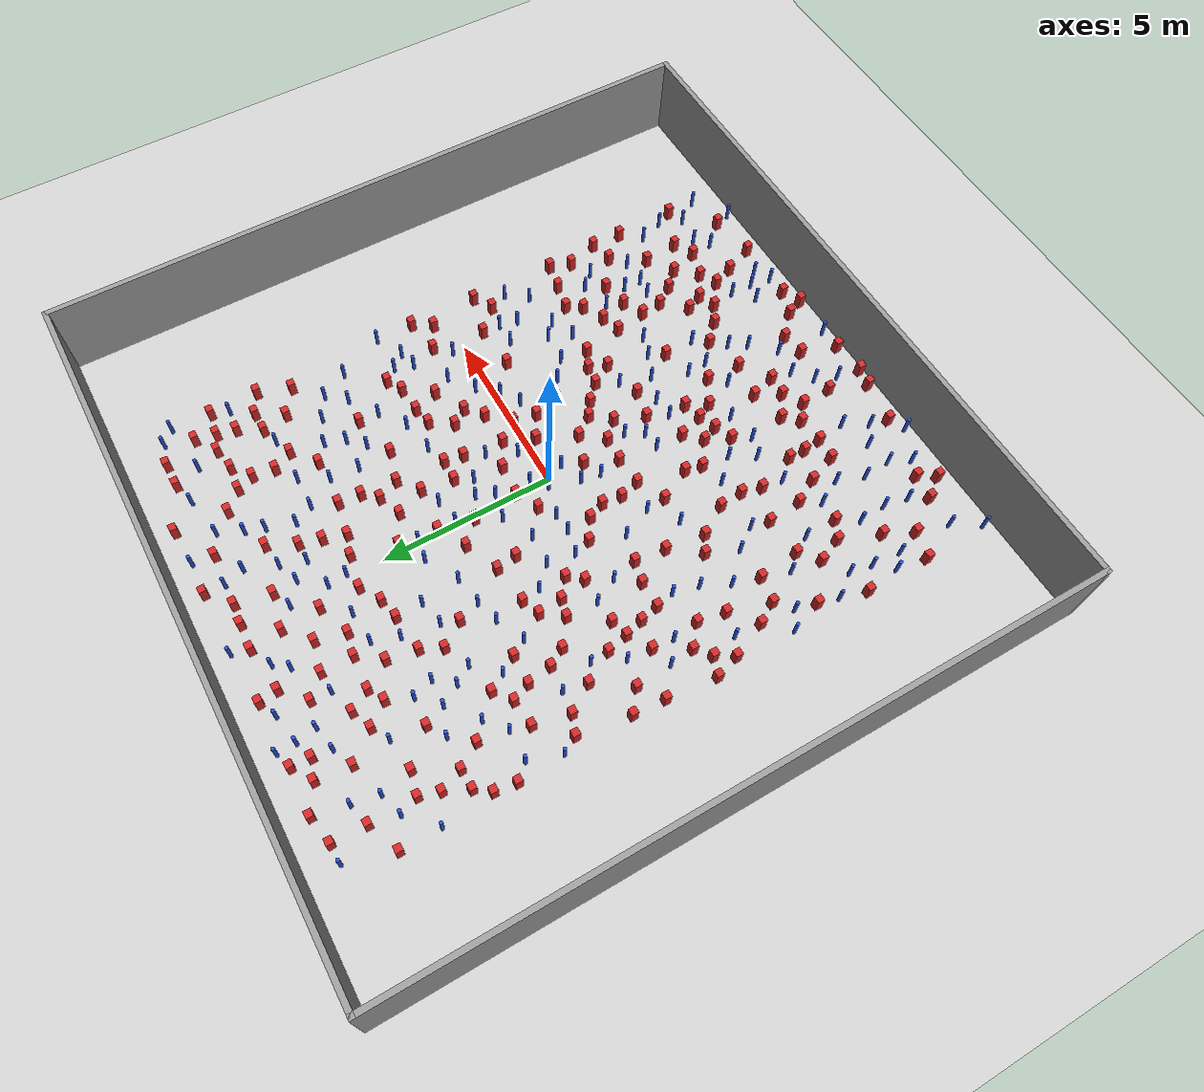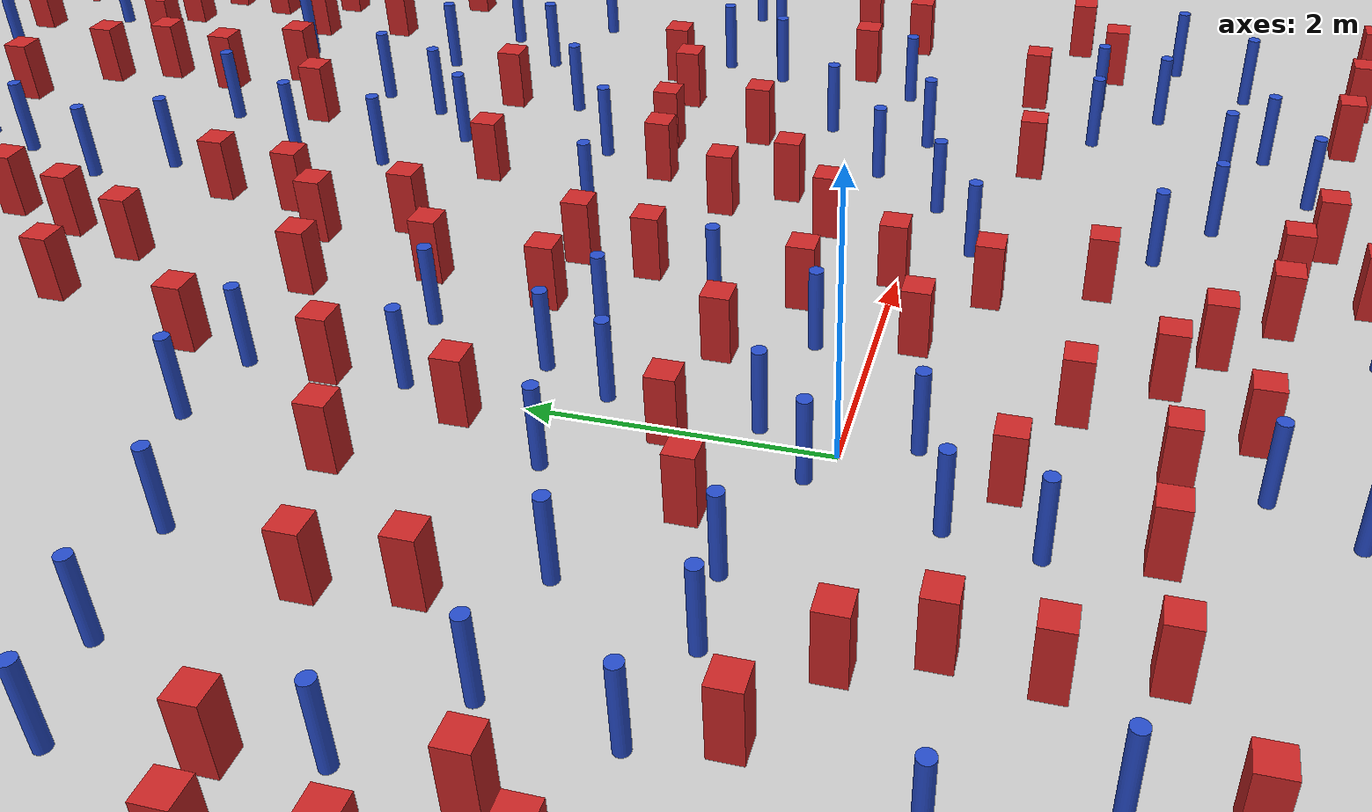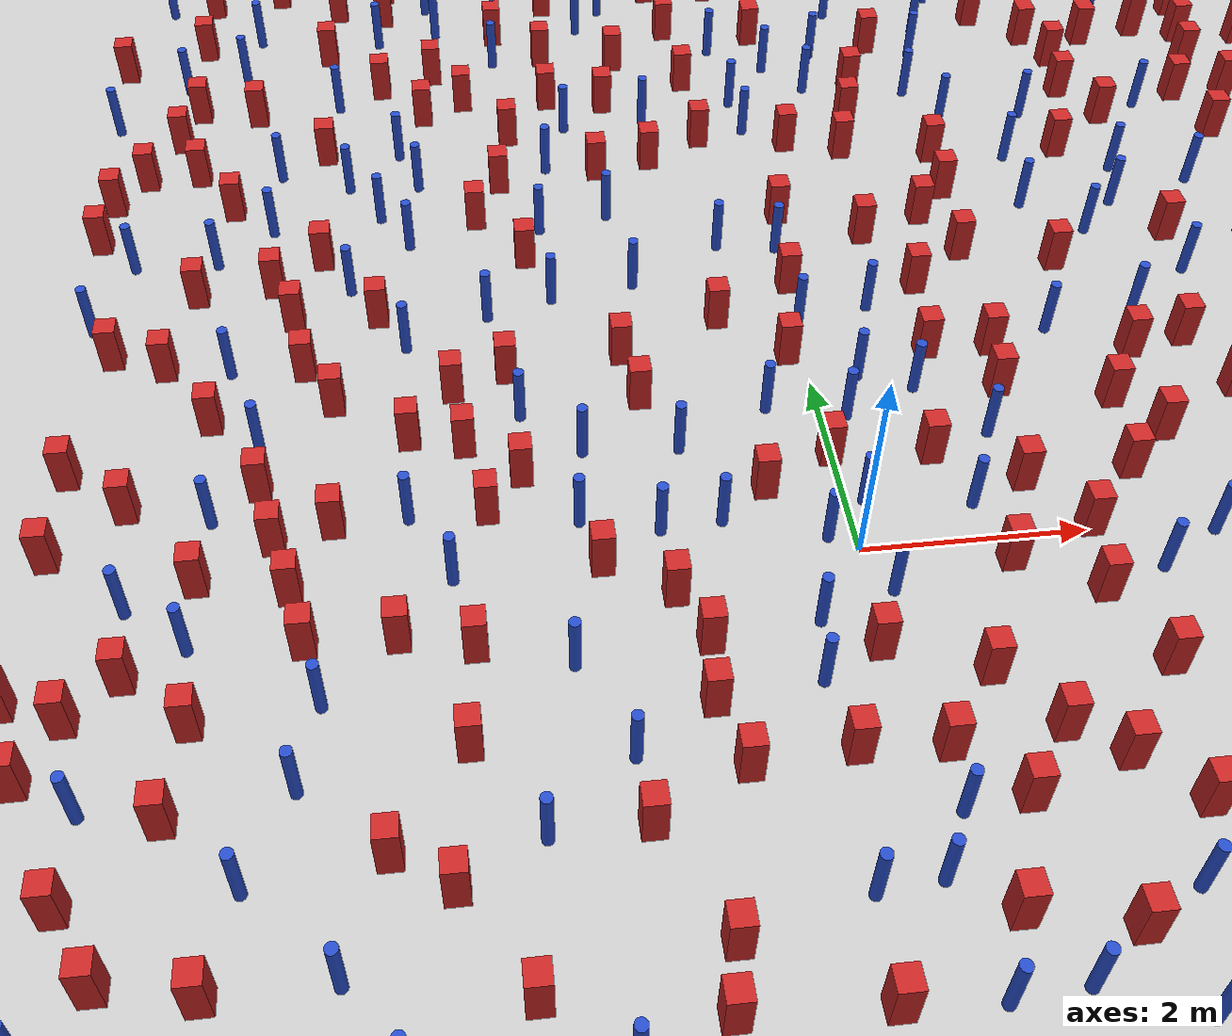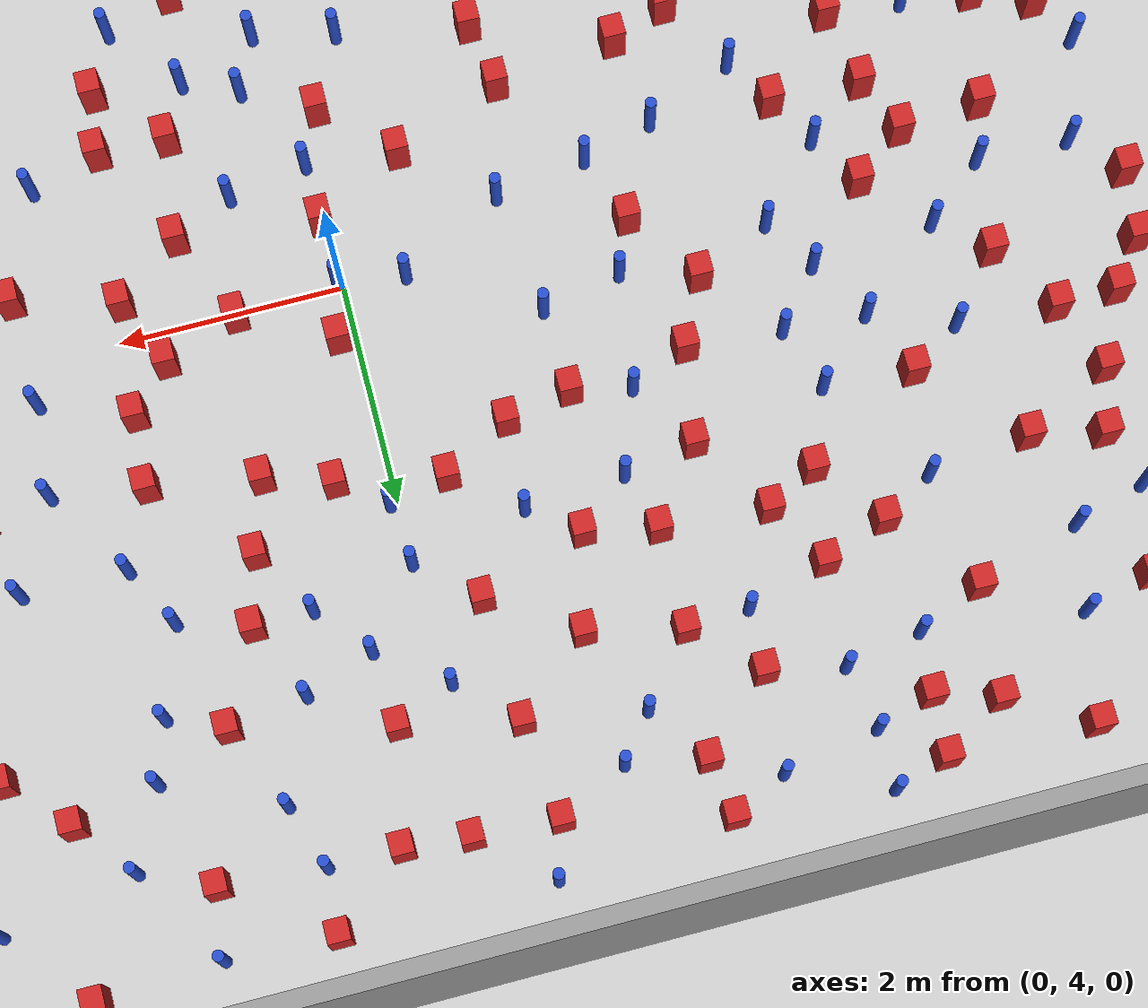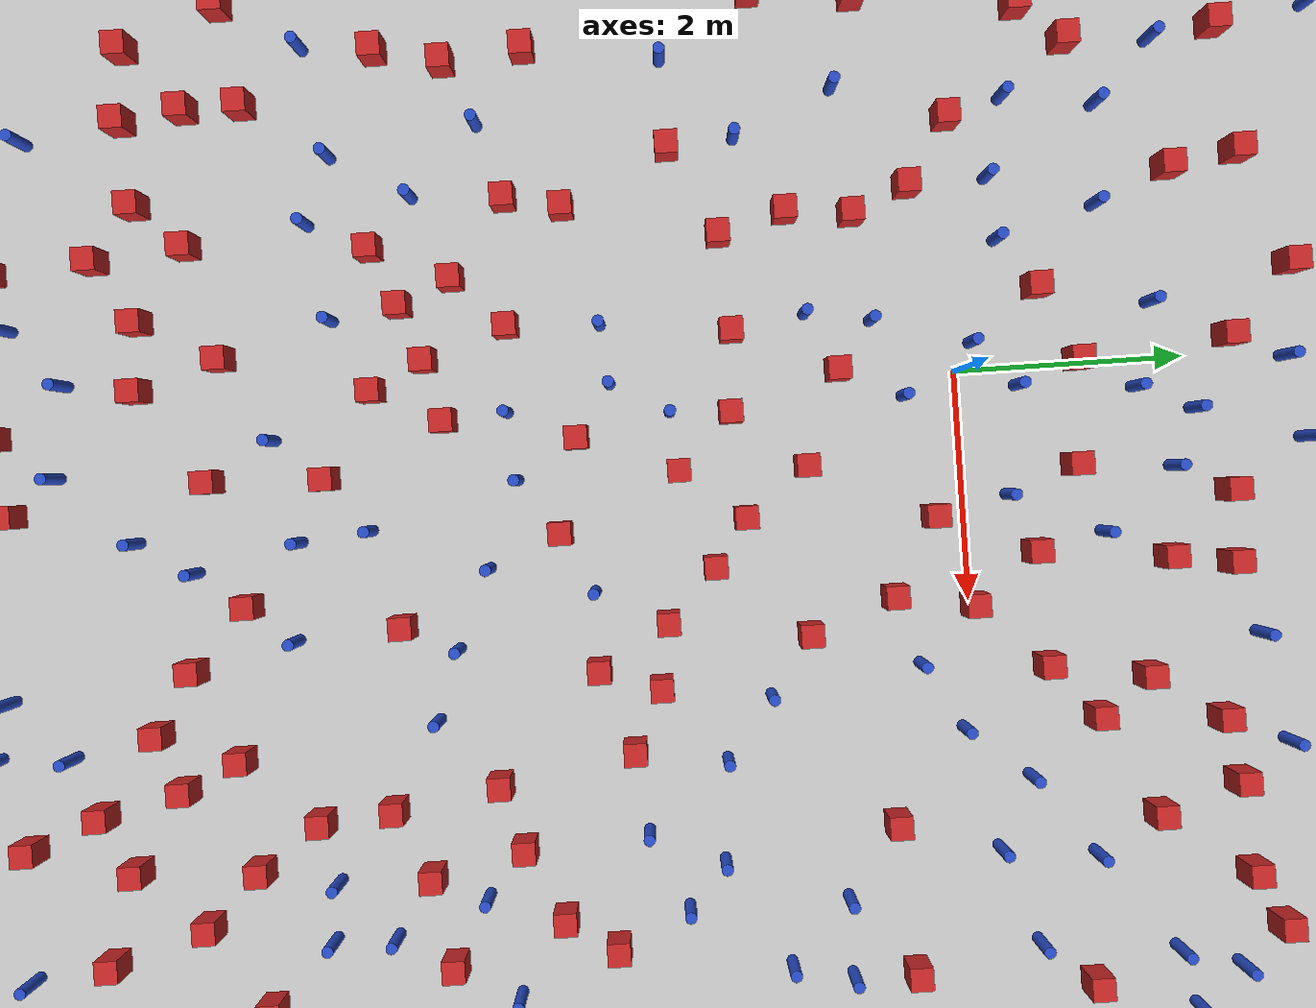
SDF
<sdf version="1.6">
 <world name="default">
  <light name="sun" type="directional">
   <pose>0 0 1000 0 -0 0</pose>
   <diffuse>0.8 0.8 0.8 1</diffuse>
   <specular>0.1 0.1 0.1 1</specular>
   <attenuation>
    <range>1000</range>
    <constant>0.9</constant>
    <linear>0.01</linear>
    <quadratic>0.001</quadratic>
   </attenuation>
   <direction>-0.5 0.5 -1</direction>
  </light>
  <model name="ground_plane">
   <static>1</static>
   <link name="link">
    <collision name="collision">
     <geometry><plane><normal>0 0 1</normal><size>100 100</size></plane></geometry>
     <surface><friction><ode><mu>100</mu><mu2>50</mu2></ode></friction></surface>
    </collision>
    <visual name="visual">
     <cast_shadows>0</cast_shadows>
     <geometry><plane><normal>0 0 1</normal><size>100 100</size></plane></geometry>
     <material>
      <ambient>1.0 1.0 1.0 1.0</ambient>
      <diffuse>0.8 0.8 0.8 1.0</diffuse>
      <specular>0.01 0.01 0.01 1.000000</specular>
     </material>
    </visual>
   </link>
  </model>
  <gravity>0 0 -9.8</gravity>
  <magnetic_field>6e-06 2.3e-05 -4.2e-05</magnetic_field>
  <atmosphere type="adiabatic"/>
  <physics name="default_physics" default="0" type="ode">
   <max_step_size>0.001</max_step_size>
   <real_time_factor>1</real_time_factor>
   <real_time_update_rate>1000</real_time_update_rate>
  </physics>
  <scene><ambient>0.4 0.4 0.4 1</ambient><background>0.7 0.7 0.7 1</background><shadows>1</shadows></scene>
  <spherical_coordinates>
   <surface_model>EARTH_WGS84</surface_model>
   <latitude_deg>0</latitude_deg>
   <longitude_deg>0</longitude_deg>
   <elevation>0</elevation>
   <heading_deg>0</heading_deg>
  </spherical_coordinates>
  <plugin name="gazebo_occupancy_map" filename="libgazebo_2Dmap_plugin.so">
   <map_resolution>0.05</map_resolution>
   <map_topic>generated_map</map_topic>
   <map_height>0.01</map_height>
   <map_size_x>50</map_size_x>
   <map_size_y>50</map_size_y>
  </plugin>
  <model name="NamedLocations">
   <static>true</static>
   <link name="DefaultStart"><pose>8.5 0 0 0 0 3.14</pose></link>
  </model>
  <model name="20x20_walls">
   <pose>0.044518 0.176112 0 0 -0 0</pose>
   <link name="Wall_1">
    <collision name="Wall_1_Collision">
     <geometry><box><size>20 0.15 2.5</size></box></geometry>
     <pose>0 0 1.25 0 -0 0</pose>
    </collision>
    <visual name="Wall_1_Visual">
     <pose>0 0 1.25 0 -0 0</pose>
     <geometry><box><size>20 0.15 2.5</size></box></geometry>
     <material>
      <script><uri>file://media/materials/scripts/gazebo.material</uri><name>Gazebo/Grey</name></script>
      <ambient>0.976471 0.992157 1 1</ambient>
     </material>
     <meta><layer>0</layer></meta>
    </visual>
    <pose>0 9.925 0 0 -0 0</pose>
   </link>
   <link name="Wall_3">
    <collision name="Wall_3_Collision">
     <geometry><box><size>20 0.15 2.5</size></box></geometry>
     <pose>0 0 1.25 0 -0 0</pose>
    </collision>
    <visual name="Wall_3_Visual">
     <pose>0 0 1.25 0 -0 0</pose>
     <geometry><box><size>20 0.15 2.5</size></box></geometry>
     <material>
      <script><uri>file://media/materials/scripts/gazebo.material</uri><name>Gazebo/Grey</name></script>
      <ambient>0.976471 0.992157 1 1</ambient>
     </material>
     <meta><layer>0</layer></meta>
    </visual>
    <pose>9.925 0 0 0 0 -1.5708</pose>
   </link>
   <link name="Wall_4">
    <collision name="Wall_4_Collision">
     <geometry><box><size>20 0.15 2.5</size></box></geometry>
     <pose>0 0 1.25 0 -0 0</pose>
    </collision>
    <visual name="Wall_4_Visual">
     <pose>0 0 1.25 0 -0 0</pose>
     <geometry><box><size>20 0.15 2.5</size></box></geometry>
     <material>
      <script><uri>file://media/materials/scripts/gazebo.material</uri><name>Gazebo/Grey</name></script>
      <ambient>0.976471 0.992157 1 1</ambient>
     </material>
     <meta><layer>0</layer></meta>
    </visual>
    <pose>0 -9.925 0 0 -0 3.14159</pose>
   </link>
   <link name="Wall_5">
    <collision name="Wall_5_Collision">
     <geometry><box><size>20 0.15 2.5</size></box></geometry>
     <pose>0 0 1.25 0 -0 0</pose>
    </collision>
    <visual name="Wall_5_Visual">
     <pose>0 0 1.25 0 -0 0</pose>
     <geometry><box><size>20 0.15 2.5</size></box></geometry>
     <material>
      <script><uri>file://media/materials/scripts/gazebo.material</uri><name>Gazebo/Grey</name></script>
      <ambient>0.976471 0.992157 1 1</ambient>
     </material>
     <meta><layer>0</layer></meta>
    </visual>
    <pose>-9.925 0 0 0 -0 1.5708</pose>
   </link>
   <static>1</static>
  </model>
  <model name="pole_obstacle0">
   <static>true</static>
   <pose>-0.240299481818 0.152974153635 -9.47619616065e-06 5.49618799737e-07 2.36310414057e-07 -1.55090534801e-07</pose>
   <link name="link">
    <pose>0 0 0.3 0 -0 0</pose>
    <inertial>
     <mass>1</mass>
     <inertia><ixx>0.145833</ixx><ixy>0</ixy><ixz>0</ixz><iyy>0.145833</iyy><iyz>0</iyz><izz>0.125</izz></inertia>
    </inertial>
    <collision name="collision">
     <geometry><cylinder><radius>0.05</radius><length>.6</length></cylinder></geometry>
    </collision>
    <visual name="visual">
     <geometry><cylinder><radius>0.05</radius><length>.6</length></cylinder></geometry>
     <material>
      <script><name>Gazebo/Blue</name><uri>file://media/materials/scripts/gazebo.material</uri></script>
     </material>
    </visual>
   </link>
  </model>
  <model name="pole_obstacle1">
   <static>true</static>
   <pose>2.85580955907 5.23067416467 -9.47619616065e-06 5.49618799738e-07 2.3631041406e-07 -1.55090534801e-07</pose>
   <link name="link">
    <pose>0 0 0.3 0 -0 0</pose>
    <inertial>
     <mass>1</mass>
     <inertia><ixx>0.145833</ixx><ixy>0</ixy><ixz>0</ixz><iyy>0.145833</iyy><iyz>0</iyz><izz>0.125</izz></inertia>
    </inertial>
    <collision name="collision">
     <geometry><cylinder><radius>0.05</radius><length>.6</length></cylinder></geometry>
    </collision>
    <visual name="visual">
     <geometry><cylinder><radius>0.05</radius><length>.6</length></cylinder></geometry>
     <material>
      <script><name>Gazebo/Blue</name><uri>file://media/materials/scripts/gazebo.material</uri></script>
     </material>
    </visual>
   </link>
  </model>
  <model name="square_post_obstacle0">
   <static>true</static>
   <pose>1.83028905246 7.55747029664 -6.11067671241e-07 -5.50515727128e-06 -8.79689657224e-07 2.37013304536e-05</pose>
   <link name="link">
    <pose>0 0 0.25 0 -0 0</pose>
    <inertial>
     <mass>100</mass>
     <inertia>
      <ixx>0.166667</ixx>
      <ixy>0</ixy>
      <ixz>0</ixz>
      <iyy>0.166667</iyy>
      <iyz>0</iyz>
      <izz>0.166667</izz>
     </inertia>
    </inertial>
    <collision name="collision"><geometry><box><size>.2 .2 .5</size></box></geometry></collision>
    <visual name="visual">
     <geometry><box><size>.2 .2 .5</size></box></geometry>
     <material>
      <script><name>Gazebo/Red</name><uri>file://media/materials/scripts/gazebo.material</uri></script>
     </material>
    </visual>
   </link>
  </model>
  <model name="square_post_obstacle1">
   <static>true</static>
   <pose>-3.93101011616 8.76190546787 -6.11067671241e-07 -5.50515727128e-06 -8.79689657224e-07 2.37013304536e-05</pose>
   <link name="link">
    <pose>0 0 0.25 0 -0 0</pose>
    <inertial>
     <mass>100</mass>
     <inertia>
      <ixx>0.166667</ixx>
      <ixy>0</ixy>
      <ixz>0</ixz>
      <iyy>0.166667</iyy>
      <iyz>0</iyz>
      <izz>0.166667</izz>
     </inertia>
    </inertial>
    <collision name="collision"><geometry><box><size>.2 .2 .5</size></box></geometry></collision>
    <visual name="visual">
     <geometry><box><size>.2 .2 .5</size></box></geometry>
     <material>
      <script><name>Gazebo/Red</name><uri>file://media/materials/scripts/gazebo.material</uri></script>
     </material>
    </visual>
   </link>
  </model>
  <model name="pole_obstacle2">
   <static>true</static>
   <pose>-0.487812181251 1.71194919246 -9.47619616065e-06 5.49618799738e-07 2.36310414059e-07 -1.55090534802e-07</pose>
   <link name="link">
    <pose>0 0 0.3 0 -0 0</pose>
    <inertial>
     <mass>1</mass>
     <inertia><ixx>0.145833</ixx><ixy>0</ixy><ixz>0</ixz><iyy>0.145833</iyy><iyz>0</iyz><izz>0.125</izz></inertia>
    </inertial>
    <collision name="collision">
     <geometry><cylinder><radius>0.05</radius><length>.6</length></cylinder></geometry>
    </collision>
    <visual name="visual">
     <geometry><cylinder><radius>0.05</radius><length>.6</length></cylinder></geometry>
     <material>
      <script><name>Gazebo/Blue</name><uri>file://media/materials/scripts/gazebo.material</uri></script>
     </material>
    </visual>
   </link>
  </model>
  <model name="pole_obstacle3">
   <static>true</static>
   <pose>-5.50317847386 0.870224016151 -9.47619616065e-06 5.49618799737e-07 2.36310414061e-07 -1.550905348e-07</pose>
   <link name="link">
    <pose>0 0 0.3 0 -0 0</pose>
    <inertial>
     <mass>1</mass>
     <inertia><ixx>0.145833</ixx><ixy>0</ixy><ixz>0</ixz><iyy>0.145833</iyy><iyz>0</iyz><izz>0.125</izz></inertia>
    </inertial>
    <collision name="collision">
     <geometry><cylinder><radius>0.05</radius><length>.6</length></cylinder></geometry>
    </collision>
    <visual name="visual">
     <geometry><cylinder><radius>0.05</radius><length>.6</length></cylinder></geometry>
     <material>
      <script><name>Gazebo/Blue</name><uri>file://media/materials/scripts/gazebo.material</uri></script>
     </material>
    </visual>
   </link>
  </model>
  <model name="pole_obstacle4">
   <static>true</static>
   <pose>-0.489798649073 -0.701766864221 -9.47619616065e-06 5.49618799737e-07 2.3631041405e-07 -1.55090534807e-07</pose>
   <link name="link">
    <pose>0 0 0.3 0 -0 0</pose>
    <inertial>
     <mass>1</mass>
     <inertia><ixx>0.145833</ixx><ixy>0</ixy><ixz>0</ixz><iyy>0.145833</iyy><iyz>0</iyz><izz>0.125</izz></inertia>
    </inertial>
    <collision name="collision">
     <geometry><cylinder><radius>0.05</radius><length>.6</length></cylinder></geometry>
    </collision>
    <visual name="visual">
     <geometry><cylinder><radius>0.05</radius><length>.6</length></cylinder></geometry>
     <material>
      <script><name>Gazebo/Blue</name><uri>file://media/materials/scripts/gazebo.material</uri></script>
     </material>
    </visual>
   </link>
  </model>
  <model name="pole_obstacle5">
   <static>true</static>
   <pose>-3.71422850612 4.40279073542 -9.47619616065e-06 5.49618799738e-07 2.3631041406e-07 -1.55090534801e-07</pose>
   <link name="link">
    <pose>0 0 0.3 0 -0 0</pose>
    <inertial>
     <mass>1</mass>
     <inertia><ixx>0.145833</ixx><ixy>0</ixy><ixz>0</ixz><iyy>0.145833</iyy><iyz>0</iyz><izz>0.125</izz></inertia>
    </inertial>
    <collision name="collision">
     <geometry><cylinder><radius>0.05</radius><length>.6</length></cylinder></geometry>
    </collision>
    <visual name="visual">
     <geometry><cylinder><radius>0.05</radius><length>.6</length></cylinder></geometry>
     <material>
      <script><name>Gazebo/Blue</name><uri>file://media/materials/scripts/gazebo.material</uri></script>
     </material>
    </visual>
   </link>
  </model>
  <model name="pole_obstacle6">
   <static>true</static>
   <pose>-6.73994371988 -4.76425897762 -9.47619616065e-06 5.49618799737e-07 2.36310414037e-07 -1.55090534814e-07</pose>
   <link name="link">
    <pose>0 0 0.3 0 -0 0</pose>
    <inertial>
     <mass>1</mass>
     <inertia><ixx>0.145833</ixx><ixy>0</ixy><ixz>0</ixz><iyy>0.145833</iyy><iyz>0</iyz><izz>0.125</izz></inertia>
    </inertial>
    <collision name="collision">
     <geometry><cylinder><radius>0.05</radius><length>.6</length></cylinder></geometry>
    </collision>
    <visual name="visual">
     <geometry><cylinder><radius>0.05</radius><length>.6</length></cylinder></geometry>
     <material>
      <script><name>Gazebo/Blue</name><uri>file://media/materials/scripts/gazebo.material</uri></script>
     </material>
    </visual>
   </link>
  </model>
  <model name="square_post_obstacle2">
   <static>true</static>
   <pose>-4.66760439507 -0.521512777751 -6.11067671241e-07 -5.50515727128e-06 -8.79689657224e-07 2.37013304536e-05</pose>
   <link name="link">
    <pose>0 0 0.25 0 -0 0</pose>
    <inertial>
     <mass>100</mass>
     <inertia>
      <ixx>0.166667</ixx>
      <ixy>0</ixy>
      <ixz>0</ixz>
      <iyy>0.166667</iyy>
      <iyz>0</iyz>
      <izz>0.166667</izz>
     </inertia>
    </inertial>
    <collision name="collision"><geometry><box><size>.2 .2 .5</size></box></geometry></collision>
    <visual name="visual">
     <geometry><box><size>.2 .2 .5</size></box></geometry>
     <material>
      <script><name>Gazebo/Red</name><uri>file://media/materials/scripts/gazebo.material</uri></script>
     </material>
    </visual>
   </link>
  </model>
  <model name="square_post_obstacle3">
   <static>true</static>
   <pose>-3.95371555942 -5.46030801869 -6.11067671241e-07 -5.50515727128e-06 -8.79689657224e-07 2.37013304536e-05</pose>
   <link name="link">
    <pose>0 0 0.25 0 -0 0</pose>
    <inertial>
     <mass>100</mass>
     <inertia>
      <ixx>0.166667</ixx>
      <ixy>0</ixy>
      <ixz>0</ixz>
      <iyy>0.166667</iyy>
      <iyz>0</iyz>
      <izz>0.166667</izz>
     </inertia>
    </inertial>
    <collision name="collision"><geometry><box><size>.2 .2 .5</size></box></geometry></collision>
    <visual name="visual">
     <geometry><box><size>.2 .2 .5</size></box></geometry>
     <material>
      <script><name>Gazebo/Red</name><uri>file://media/materials/scripts/gazebo.material</uri></script>
     </material>
    </visual>
   </link>
  </model>
  <model name="square_post_obstacle4">
   <static>true</static>
   <pose>3.69280537728 2.22293517333 -6.11067671241e-07 -5.50515727128e-06 -8.79689657224e-07 2.37013304536e-05</pose>
   <link name="link">
    <pose>0 0 0.25 0 -0 0</pose>
    <inertial>
     <mass>100</mass>
     <inertia>
      <ixx>0.166667</ixx>
      <ixy>0</ixy>
      <ixz>0</ixz>
      <iyy>0.166667</iyy>
      <iyz>0</iyz>
      <izz>0.166667</izz>
     </inertia>
    </inertial>
    <collision name="collision"><geometry><box><size>.2 .2 .5</size></box></geometry></collision>
    <visual name="visual">
     <geometry><box><size>.2 .2 .5</size></box></geometry>
     <material>
      <script><name>Gazebo/Red</name><uri>file://media/materials/scripts/gazebo.material</uri></script>
     </material>
    </visual>
   </link>
  </model>
  <model name="pole_obstacle7">
   <static>true</static>
   <pose>-5.06785787233 -2.56014334162 -9.47619616065e-06 5.49618799738e-07 2.36310414051e-07 -1.55090534805e-07</pose>
   <link name="link">
    <pose>0 0 0.3 0 -0 0</pose>
    <inertial>
     <mass>1</mass>
     <inertia><ixx>0.145833</ixx><ixy>0</ixy><ixz>0</ixz><iyy>0.145833</iyy><iyz>0</iyz><izz>0.125</izz></inertia>
    </inertial>
    <collision name="collision">
     <geometry><cylinder><radius>0.05</radius><length>.6</length></cylinder></geometry>
    </collision>
    <visual name="visual">
     <geometry><cylinder><radius>0.05</radius><length>.6</length></cylinder></geometry>
     <material>
      <script><name>Gazebo/Blue</name><uri>file://media/materials/scripts/gazebo.material</uri></script>
     </material>
    </visual>
   </link>
  </model>
  <model name="pole_obstacle8">
   <static>true</static>
   <pose>0.767769919635 2.98122470118 -9.47619616065e-06 5.49618799737e-07 2.36310414066e-07 -1.55090534797e-07</pose>
   <link name="link">
    <pose>0 0 0.3 0 -0 0</pose>
    <inertial>
     <mass>1</mass>
     <inertia><ixx>0.145833</ixx><ixy>0</ixy><ixz>0</ixz><iyy>0.145833</iyy><iyz>0</iyz><izz>0.125</izz></inertia>
    </inertial>
    <collision name="collision">
     <geometry><cylinder><radius>0.05</radius><length>.6</length></cylinder></geometry>
    </collision>
    <visual name="visual">
     <geometry><cylinder><radius>0.05</radius><length>.6</length></cylinder></geometry>
     <material>
      <script><name>Gazebo/Blue</name><uri>file://media/materials/scripts/gazebo.material</uri></script>
     </material>
    </visual>
   </link>
  </model>
  <model name="square_post_obstacle5">
   <static>true</static>
   <pose>-1.48127883033 -1.39184149811 -6.11067671241e-07 -5.50515727128e-06 -8.79689657224e-07 2.37013304536e-05</pose>
   <link name="link">
    <pose>0 0 0.25 0 -0 0</pose>
    <inertial>
     <mass>100</mass>
     <inertia>
      <ixx>0.166667</ixx>
      <ixy>0</ixy>
      <ixz>0</ixz>
      <iyy>0.166667</iyy>
      <iyz>0</iyz>
      <izz>0.166667</izz>
     </inertia>
    </inertial>
    <collision name="collision"><geometry><box><size>.2 .2 .5</size></box></geometry></collision>
    <visual name="visual">
     <geometry><box><size>.2 .2 .5</size></box></geometry>
     <material>
      <script><name>Gazebo/Red</name><uri>file://media/materials/scripts/gazebo.material</uri></script>
     </material>
    </visual>
   </link>
  </model>
  <model name="square_post_obstacle6">
   <static>true</static>
   <pose>6.10533569681 -4.18703966137 -6.11067671241e-07 -5.50515727128e-06 -8.79689657224e-07 2.37013304536e-05</pose>
   <link name="link">
    <pose>0 0 0.25 0 -0 0</pose>
    <inertial>
     <mass>100</mass>
     <inertia>
      <ixx>0.166667</ixx>
      <ixy>0</ixy>
      <ixz>0</ixz>
      <iyy>0.166667</iyy>
      <iyz>0</iyz>
      <izz>0.166667</izz>
     </inertia>
    </inertial>
    <collision name="collision"><geometry><box><size>.2 .2 .5</size></box></geometry></collision>
    <visual name="visual">
     <geometry><box><size>.2 .2 .5</size></box></geometry>
     <material>
      <script><name>Gazebo/Red</name><uri>file://media/materials/scripts/gazebo.material</uri></script>
     </material>
    </visual>
   </link>
  </model>
  <model name="square_post_obstacle7">
   <static>true</static>
   <pose>3.92760608452 1.5035485975 -6.11067671241e-07 -5.50515727128e-06 -8.79689657224e-07 2.37013304536e-05</pose>
   <link name="link">
    <pose>0 0 0.25 0 -0 0</pose>
    <inertial>
     <mass>100</mass>
     <inertia>
      <ixx>0.166667</ixx>
      <ixy>0</ixy>
      <ixz>0</ixz>
      <iyy>0.166667</iyy>
      <iyz>0</iyz>
      <izz>0.166667</izz>
     </inertia>
    </inertial>
    <collision name="collision"><geometry><box><size>.2 .2 .5</size></box></geometry></collision>
    <visual name="visual">
     <geometry><box><size>.2 .2 .5</size></box></geometry>
     <material>
      <script><name>Gazebo/Red</name><uri>file://media/materials/scripts/gazebo.material</uri></script>
     </material>
    </visual>
   </link>
  </model>
  <model name="pole_obstacle9">
   <static>true</static>
   <pose>-3.79374008691 5.95631471667 -9.47619616065e-06 5.49618799738e-07 2.3631041406e-07 -1.55090534801e-07</pose>
   <link name="link">
    <pose>0 0 0.3 0 -0 0</pose>
    <inertial>
     <mass>1</mass>
     <inertia><ixx>0.145833</ixx><ixy>0</ixy><ixz>0</ixz><iyy>0.145833</iyy><iyz>0</iyz><izz>0.125</izz></inertia>
    </inertial>
    <collision name="collision">
     <geometry><cylinder><radius>0.05</radius><length>.6</length></cylinder></geometry>
    </collision>
    <visual name="visual">
     <geometry><cylinder><radius>0.05</radius><length>.6</length></cylinder></geometry>
     <material>
      <script><name>Gazebo/Blue</name><uri>file://media/materials/scripts/gazebo.material</uri></script>
     </material>
    </visual>
   </link>
  </model>
  <model name="pole_obstacle10">
   <static>true</static>
   <pose>-6.29512703898 -1.83872455876 -9.47619616065e-06 5.49618799738e-07 2.36310414071e-07 -1.55090534796e-07</pose>
   <link name="link">
    <pose>0 0 0.3 0 -0 0</pose>
    <inertial>
     <mass>1</mass>
     <inertia><ixx>0.145833</ixx><ixy>0</ixy><ixz>0</ixz><iyy>0.145833</iyy><iyz>0</iyz><izz>0.125</izz></inertia>
    </inertial>
    <collision name="collision">
     <geometry><cylinder><radius>0.05</radius><length>.6</length></cylinder></geometry>
    </collision>
    <visual name="visual">
     <geometry><cylinder><radius>0.05</radius><length>.6</length></cylinder></geometry>
     <material>
      <script><name>Gazebo/Blue</name><uri>file://media/materials/scripts/gazebo.material</uri></script>
     </material>
    </visual>
   </link>
  </model>
  <model name="pole_obstacle11">
   <static>true</static>
   <pose>-4.38404824657 -8.93209616791 -9.47619616065e-06 5.49618799737e-07 2.36310414065e-07 -1.55090534796e-07</pose>
   <link name="link">
    <pose>0 0 0.3 0 -0 0</pose>
    <inertial>
     <mass>1</mass>
     <inertia><ixx>0.145833</ixx><ixy>0</ixy><ixz>0</ixz><iyy>0.145833</iyy><iyz>0</iyz><izz>0.125</izz></inertia>
    </inertial>
    <collision name="collision">
     <geometry><cylinder><radius>0.05</radius><length>.6</length></cylinder></geometry>
    </collision>
    <visual name="visual">
     <geometry><cylinder><radius>0.05</radius><length>.6</length></cylinder></geometry>
     <material>
      <script><name>Gazebo/Blue</name><uri>file://media/materials/scripts/gazebo.material</uri></script>
     </material>
    </visual>
   </link>
  </model>
  <model name="pole_obstacle12">
   <static>true</static>
   <pose>5.93281669993 -8.06268216293 -9.47619616065e-06 5.49618799737e-07 2.36310414065e-07 -1.55090534796e-07</pose>
   <link name="link">
    <pose>0 0 0.3 0 -0 0</pose>
    <inertial>
     <mass>1</mass>
     <inertia><ixx>0.145833</ixx><ixy>0</ixy><ixz>0</ixz><iyy>0.145833</iyy><iyz>0</iyz><izz>0.125</izz></inertia>
    </inertial>
    <collision name="collision">
     <geometry><cylinder><radius>0.05</radius><length>.6</length></cylinder></geometry>
    </collision>
    <visual name="visual">
     <geometry><cylinder><radius>0.05</radius><length>.6</length></cylinder></geometry>
     <material>
      <script><name>Gazebo/Blue</name><uri>file://media/materials/scripts/gazebo.material</uri></script>
     </material>
    </visual>
   </link>
  </model>
  <model name="square_post_obstacle8">
   <static>true</static>
   <pose>3.74884087487 7.5368950362 -6.11067671241e-07 -5.50515727128e-06 -8.79689657224e-07 2.37013304536e-05</pose>
   <link name="link">
    <pose>0 0 0.25 0 -0 0</pose>
    <inertial>
     <mass>100</mass>
     <inertia>
      <ixx>0.166667</ixx>
      <ixy>0</ixy>
      <ixz>0</ixz>
      <iyy>0.166667</iyy>
      <iyz>0</iyz>
      <izz>0.166667</izz>
     </inertia>
    </inertial>
    <collision name="collision"><geometry><box><size>.2 .2 .5</size></box></geometry></collision>
    <visual name="visual">
     <geometry><box><size>.2 .2 .5</size></box></geometry>
     <material>
      <script><name>Gazebo/Red</name><uri>file://media/materials/scripts/gazebo.material</uri></script>
     </material>
    </visual>
   </link>
  </model>
  <model name="square_post_obstacle9">
   <static>true</static>
   <pose>-0.477985754404 -1.91767797434 -6.11067671241e-07 -5.50515727128e-06 -8.79689657224e-07 2.37013304536e-05</pose>
   <link name="link">
    <pose>0 0 0.25 0 -0 0</pose>
    <inertial>
     <mass>100</mass>
     <inertia>
      <ixx>0.166667</ixx>
      <ixy>0</ixy>
      <ixz>0</ixz>
      <iyy>0.166667</iyy>
      <iyz>0</iyz>
      <izz>0.166667</izz>
     </inertia>
    </inertial>
    <collision name="collision"><geometry><box><size>.2 .2 .5</size></box></geometry></collision>
    <visual name="visual">
     <geometry><box><size>.2 .2 .5</size></box></geometry>
     <material>
      <script><name>Gazebo/Red</name><uri>file://media/materials/scripts/gazebo.material</uri></script>
     </material>
    </visual>
   </link>
  </model>
  <model name="pole_obstacle13">
   <static>true</static>
   <pose>-1.12992087261 -8.8009247254 -9.47619616065e-06 5.49618799737e-07 2.36310414046e-07 -1.55090534809e-07</pose>
   <link name="link">
    <pose>0 0 0.3 0 -0 0</pose>
    <inertial>
     <mass>1</mass>
     <inertia><ixx>0.145833</ixx><ixy>0</ixy><ixz>0</ixz><iyy>0.145833</iyy><iyz>0</iyz><izz>0.125</izz></inertia>
    </inertial>
    <collision name="collision">
     <geometry><cylinder><radius>0.05</radius><length>.6</length></cylinder></geometry>
    </collision>
    <visual name="visual">
     <geometry><cylinder><radius>0.05</radius><length>.6</length></cylinder></geometry>
     <material>
      <script><name>Gazebo/Blue</name><uri>file://media/materials/scripts/gazebo.material</uri></script>
     </material>
    </visual>
   </link>
  </model>
  <model name="square_post_obstacle10">
   <static>true</static>
   <pose>2.00440950209 -2.61996437505 -6.11067671241e-07 -5.50515727128e-06 -8.79689657224e-07 2.37013304536e-05</pose>
   <link name="link">
    <pose>0 0 0.25 0 -0 0</pose>
    <inertial>
     <mass>100</mass>
     <inertia>
      <ixx>0.166667</ixx>
      <ixy>0</ixy>
      <ixz>0</ixz>
      <iyy>0.166667</iyy>
      <iyz>0</iyz>
      <izz>0.166667</izz>
     </inertia>
    </inertial>
    <collision name="collision"><geometry><box><size>.2 .2 .5</size></box></geometry></collision>
    <visual name="visual">
     <geometry><box><size>.2 .2 .5</size></box></geometry>
     <material>
      <script><name>Gazebo/Red</name><uri>file://media/materials/scripts/gazebo.material</uri></script>
     </material>
    </visual>
   </link>
  </model>
  <model name="square_post_obstacle11">
   <static>true</static>
   <pose>-5.14176364315 -9.19598783528 -6.11067671241e-07 -5.50515727128e-06 -8.79689657224e-07 2.37013304536e-05</pose>
   <link name="link">
    <pose>0 0 0.25 0 -0 0</pose>
    <inertial>
     <mass>100</mass>
     <inertia>
      <ixx>0.166667</ixx>
      <ixy>0</ixy>
      <ixz>0</ixz>
      <iyy>0.166667</iyy>
      <iyz>0</iyz>
      <izz>0.166667</izz>
     </inertia>
    </inertial>
    <collision name="collision"><geometry><box><size>.2 .2 .5</size></box></geometry></collision>
    <visual name="visual">
     <geometry><box><size>.2 .2 .5</size></box></geometry>
     <material>
      <script><name>Gazebo/Red</name><uri>file://media/materials/scripts/gazebo.material</uri></script>
     </material>
    </visual>
   </link>
  </model>
  <model name="pole_obstacle14">
   <static>true</static>
   <pose>2.72122308292 -4.6622188699 -9.47619616065e-06 5.49618799738e-07 2.3631041406e-07 -1.55090534801e-07</pose>
   <link name="link">
    <pose>0 0 0.3 0 -0 0</pose>
    <inertial>
     <mass>1</mass>
     <inertia><ixx>0.145833</ixx><ixy>0</ixy><ixz>0</ixz><iyy>0.145833</iyy><iyz>0</iyz><izz>0.125</izz></inertia>
    </inertial>
    <collision name="collision">
     <geometry><cylinder><radius>0.05</radius><length>.6</length></cylinder></geometry>
    </collision>
    <visual name="visual">
     <geometry><cylinder><radius>0.05</radius><length>.6</length></cylinder></geometry>
     <material>
      <script><name>Gazebo/Blue</name><uri>file://media/materials/scripts/gazebo.material</uri></script>
     </material>
    </visual>
   </link>
  </model>
  <model name="pole_obstacle15">
   <static>true</static>
   <pose>3.08732034413 -0.124005722721 -9.47619616065e-06 5.49618799737e-07 2.36310414068e-07 -1.55090534797e-07</pose>
   <link name="link">
    <pose>0 0 0.3 0 -0 0</pose>
    <inertial>
     <mass>1</mass>
     <inertia><ixx>0.145833</ixx><ixy>0</ixy><ixz>0</ixz><iyy>0.145833</iyy><iyz>0</iyz><izz>0.125</izz></inertia>
    </inertial>
    <collision name="collision">
     <geometry><cylinder><radius>0.05</radius><length>.6</length></cylinder></geometry>
    </collision>
    <visual name="visual">
     <geometry><cylinder><radius>0.05</radius><length>.6</length></cylinder></geometry>
     <material>
      <script><name>Gazebo/Blue</name><uri>file://media/materials/scripts/gazebo.material</uri></script>
     </material>
    </visual>
   </link>
  </model>
  <model name="square_post_obstacle12">
   <static>true</static>
   <pose>5.20667892663 -7.29019739794 -6.11067671241e-07 -5.50515727128e-06 -8.79689657224e-07 2.37013304536e-05</pose>
   <link name="link">
    <pose>0 0 0.25 0 -0 0</pose>
    <inertial>
     <mass>100</mass>
     <inertia>
      <ixx>0.166667</ixx>
      <ixy>0</ixy>
      <ixz>0</ixz>
      <iyy>0.166667</iyy>
      <iyz>0</iyz>
      <izz>0.166667</izz>
     </inertia>
    </inertial>
    <collision name="collision"><geometry><box><size>.2 .2 .5</size></box></geometry></collision>
    <visual name="visual">
     <geometry><box><size>.2 .2 .5</size></box></geometry>
     <material>
      <script><name>Gazebo/Red</name><uri>file://media/materials/scripts/gazebo.material</uri></script>
     </material>
    </visual>
   </link>
  </model>
  <model name="pole_obstacle16">
   <static>true</static>
   <pose>2.720829693 -9.12816639796 -9.4761961606e-06 5.49618799729e-07 2.36310414e-07 -1.55090534824e-07</pose>
   <link name="link">
    <pose>0 0 0.3 0 -0 0</pose>
    <inertial>
     <mass>1</mass>
     <inertia><ixx>0.145833</ixx><ixy>0</ixy><ixz>0</ixz><iyy>0.145833</iyy><iyz>0</iyz><izz>0.125</izz></inertia>
    </inertial>
    <collision name="collision">
     <geometry><cylinder><radius>0.05</radius><length>.6</length></cylinder></geometry>
    </collision>
    <visual name="visual">
     <geometry><cylinder><radius>0.05</radius><length>.6</length></cylinder></geometry>
     <material>
      <script><name>Gazebo/Blue</name><uri>file://media/materials/scripts/gazebo.material</uri></script>
     </material>
    </visual>
   </link>
  </model>
  <model name="pole_obstacle17">
   <static>true</static>
   <pose>-6.46383993216 -6.92550078905 -9.47619616065e-06 5.49618799737e-07 2.36310414037e-07 -1.55090534814e-07</pose>
   <link name="link">
    <pose>0 0 0.3 0 -0 0</pose>
    <inertial>
     <mass>1</mass>
     <inertia><ixx>0.145833</ixx><ixy>0</ixy><ixz>0</ixz><iyy>0.145833</iyy><iyz>0</iyz><izz>0.125</izz></inertia>
    </inertial>
    <collision name="collision">
     <geometry><cylinder><radius>0.05</radius><length>.6</length></cylinder></geometry>
    </collision>
    <visual name="visual">
     <geometry><cylinder><radius>0.05</radius><length>.6</length></cylinder></geometry>
     <material>
      <script><name>Gazebo/Blue</name><uri>file://media/materials/scripts/gazebo.material</uri></script>
     </material>
    </visual>
   </link>
  </model>
  <model name="square_post_obstacle13">
   <static>true</static>
   <pose>5.71550709969 -5.27614604653 -6.11067671241e-07 -5.50515727128e-06 -8.79689657224e-07 2.37013304536e-05</pose>
   <link name="link">
    <pose>0 0 0.25 0 -0 0</pose>
    <inertial>
     <mass>100</mass>
     <inertia>
      <ixx>0.166667</ixx>
      <ixy>0</ixy>
      <ixz>0</ixz>
      <iyy>0.166667</iyy>
      <iyz>0</iyz>
      <izz>0.166667</izz>
     </inertia>
    </inertial>
    <collision name="collision"><geometry><box><size>.2 .2 .5</size></box></geometry></collision>
    <visual name="visual">
     <geometry><box><size>.2 .2 .5</size></box></geometry>
     <material>
      <script><name>Gazebo/Red</name><uri>file://media/materials/scripts/gazebo.material</uri></script>
     </material>
    </visual>
   </link>
  </model>
  <model name="pole_obstacle18">
   <static>true</static>
   <pose>-4.31520111858 3.75817734004 -9.47619616065e-06 5.49618799738e-07 2.36310414051e-07 -1.55090534805e-07</pose>
   <link name="link">
    <pose>0 0 0.3 0 -0 0</pose>
    <inertial>
     <mass>1</mass>
     <inertia><ixx>0.145833</ixx><ixy>0</ixy><ixz>0</ixz><iyy>0.145833</iyy><iyz>0</iyz><izz>0.125</izz></inertia>
    </inertial>
    <collision name="collision">
     <geometry><cylinder><radius>0.05</radius><length>.6</length></cylinder></geometry>
    </collision>
    <visual name="visual">
     <geometry><cylinder><radius>0.05</radius><length>.6</length></cylinder></geometry>
     <material>
      <script><name>Gazebo/Blue</name><uri>file://media/materials/scripts/gazebo.material</uri></script>
     </material>
    </visual>
   </link>
  </model>
  <model name="square_post_obstacle14">
   <static>true</static>
   <pose>3.09111483869 -2.97854127814 -6.11067671241e-07 -5.50515727128e-06 -8.79689657224e-07 2.37013304536e-05</pose>
   <link name="link">
    <pose>0 0 0.25 0 -0 0</pose>
    <inertial>
     <mass>100</mass>
     <inertia>
      <ixx>0.166667</ixx>
      <ixy>0</ixy>
      <ixz>0</ixz>
      <iyy>0.166667</iyy>
      <iyz>0</iyz>
      <izz>0.166667</izz>
     </inertia>
    </inertial>
    <collision name="collision"><geometry><box><size>.2 .2 .5</size></box></geometry></collision>
    <visual name="visual">
     <geometry><box><size>.2 .2 .5</size></box></geometry>
     <material>
      <script><name>Gazebo/Red</name><uri>file://media/materials/scripts/gazebo.material</uri></script>
     </material>
    </visual>
   </link>
  </model>
  <model name="pole_obstacle19">
   <static>true</static>
   <pose>4.24416532773 0.94798718305 -9.47619616065e-06 5.49618799737e-07 2.36310414061e-07 -1.550905348e-07</pose>
   <link name="link">
    <pose>0 0 0.3 0 -0 0</pose>
    <inertial>
     <mass>1</mass>
     <inertia><ixx>0.145833</ixx><ixy>0</ixy><ixz>0</ixz><iyy>0.145833</iyy><iyz>0</iyz><izz>0.125</izz></inertia>
    </inertial>
    <collision name="collision">
     <geometry><cylinder><radius>0.05</radius><length>.6</length></cylinder></geometry>
    </collision>
    <visual name="visual">
     <geometry><cylinder><radius>0.05</radius><length>.6</length></cylinder></geometry>
     <material>
      <script><name>Gazebo/Blue</name><uri>file://media/materials/scripts/gazebo.material</uri></script>
     </material>
    </visual>
   </link>
  </model>
  <model name="square_post_obstacle15">
   <static>true</static>
   <pose>-2.06721331469 9.33534077176 -6.11067671241e-07 -5.50515727128e-06 -8.79689657224e-07 2.37013304536e-05</pose>
   <link name="link">
    <pose>0 0 0.25 0 -0 0</pose>
    <inertial>
     <mass>100</mass>
     <inertia>
      <ixx>0.166667</ixx>
      <ixy>0</ixy>
      <ixz>0</ixz>
      <iyy>0.166667</iyy>
      <iyz>0</iyz>
      <izz>0.166667</izz>
     </inertia>
    </inertial>
    <collision name="collision"><geometry><box><size>.2 .2 .5</size></box></geometry></collision>
    <visual name="visual">
     <geometry><box><size>.2 .2 .5</size></box></geometry>
     <material>
      <script><name>Gazebo/Red</name><uri>file://media/materials/scripts/gazebo.material</uri></script>
     </material>
    </visual>
   </link>
  </model>
  <model name="square_post_obstacle16">
   <static>true</static>
   <pose>3.84544530139 6.41487011286 -6.11067671241e-07 -5.50515727128e-06 -8.79689657224e-07 2.37013304536e-05</pose>
   <link name="link">
    <pose>0 0 0.25 0 -0 0</pose>
    <inertial>
     <mass>100</mass>
     <inertia>
      <ixx>0.166667</ixx>
      <ixy>0</ixy>
      <ixz>0</ixz>
      <iyy>0.166667</iyy>
      <iyz>0</iyz>
      <izz>0.166667</izz>
     </inertia>
    </inertial>
    <collision name="collision"><geometry><box><size>.2 .2 .5</size></box></geometry></collision>
    <visual name="visual">
     <geometry><box><size>.2 .2 .5</size></box></geometry>
     <material>
      <script><name>Gazebo/Red</name><uri>file://media/materials/scripts/gazebo.material</uri></script>
     </material>
    </visual>
   </link>
  </model>
  <model name="square_post_obstacle17">
   <static>true</static>
   <pose>0.71277988846 -8.24891498872 -6.11067671241e-07 -5.50515727128e-06 -8.79689657224e-07 2.37013304536e-05</pose>
   <link name="link">
    <pose>0 0 0.25 0 -0 0</pose>
    <inertial>
     <mass>100</mass>
     <inertia>
      <ixx>0.166667</ixx>
      <ixy>0</ixy>
      <ixz>0</ixz>
      <iyy>0.166667</iyy>
      <iyz>0</iyz>
      <izz>0.166667</izz>
     </inertia>
    </inertial>
    <collision name="collision"><geometry><box><size>.2 .2 .5</size></box></geometry></collision>
    <visual name="visual">
     <geometry><box><size>.2 .2 .5</size></box></geometry>
     <material>
      <script><name>Gazebo/Red</name><uri>file://media/materials/scripts/gazebo.material</uri></script>
     </material>
    </visual>
   </link>
  </model>
  <model name="pole_obstacle20">
   <static>true</static>
   <pose>-3.78402829813 2.87094932875 -9.47619616065e-06 5.49618799737e-07 2.36310414051e-07 -1.55090534807e-07</pose>
   <link name="link">
    <pose>0 0 0.3 0 -0 0</pose>
    <inertial>
     <mass>1</mass>
     <inertia><ixx>0.145833</ixx><ixy>0</ixy><ixz>0</ixz><iyy>0.145833</iyy><iyz>0</iyz><izz>0.125</izz></inertia>
    </inertial>
    <collision name="collision">
     <geometry><cylinder><radius>0.05</radius><length>.6</length></cylinder></geometry>
    </collision>
    <visual name="visual">
     <geometry><cylinder><radius>0.05</radius><length>.6</length></cylinder></geometry>
     <material>
      <script><name>Gazebo/Blue</name><uri>file://media/materials/scripts/gazebo.material</uri></script>
     </material>
    </visual>
   </link>
  </model>
  <model name="pole_obstacle21">
   <static>true</static>
   <pose>1.04038166597 -5.14257661858 -9.47619616065e-06 5.49618799737e-07 2.36310414059e-07 -1.550905348e-07</pose>
   <link name="link">
    <pose>0 0 0.3 0 -0 0</pose>
    <inertial>
     <mass>1</mass>
     <inertia><ixx>0.145833</ixx><ixy>0</ixy><ixz>0</ixz><iyy>0.145833</iyy><iyz>0</iyz><izz>0.125</izz></inertia>
    </inertial>
    <collision name="collision">
     <geometry><cylinder><radius>0.05</radius><length>.6</length></cylinder></geometry>
    </collision>
    <visual name="visual">
     <geometry><cylinder><radius>0.05</radius><length>.6</length></cylinder></geometry>
     <material>
      <script><name>Gazebo/Blue</name><uri>file://media/materials/scripts/gazebo.material</uri></script>
     </material>
    </visual>
   </link>
  </model>
  <model name="pole_obstacle22">
   <static>true</static>
   <pose>5.27804432764 -5.66045612122 -9.47619616065e-06 5.49618799737e-07 2.36310414037e-07 -1.55090534814e-07</pose>
   <link name="link">
    <pose>0 0 0.3 0 -0 0</pose>
    <inertial>
     <mass>1</mass>
     <inertia><ixx>0.145833</ixx><ixy>0</ixy><ixz>0</ixz><iyy>0.145833</iyy><iyz>0</iyz><izz>0.125</izz></inertia>
    </inertial>
    <collision name="collision">
     <geometry><cylinder><radius>0.05</radius><length>.6</length></cylinder></geometry>
    </collision>
    <visual name="visual">
     <geometry><cylinder><radius>0.05</radius><length>.6</length></cylinder></geometry>
     <material>
      <script><name>Gazebo/Blue</name><uri>file://media/materials/scripts/gazebo.material</uri></script>
     </material>
    </visual>
   </link>
  </model>
  <model name="pole_obstacle23">
   <static>true</static>
   <pose>-2.14956527406 -1.78440719836 -9.47619616065e-06 5.49618799737e-07 2.36310414072e-07 -1.55090534793e-07</pose>
   <link name="link">
    <pose>0 0 0.3 0 -0 0</pose>
    <inertial>
     <mass>1</mass>
     <inertia><ixx>0.145833</ixx><ixy>0</ixy><ixz>0</ixz><iyy>0.145833</iyy><iyz>0</iyz><izz>0.125</izz></inertia>
    </inertial>
    <collision name="collision">
     <geometry><cylinder><radius>0.05</radius><length>.6</length></cylinder></geometry>
    </collision>
    <visual name="visual">
     <geometry><cylinder><radius>0.05</radius><length>.6</length></cylinder></geometry>
     <material>
      <script><name>Gazebo/Blue</name><uri>file://media/materials/scripts/gazebo.material</uri></script>
     </material>
    </visual>
   </link>
  </model>
  <model name="square_post_obstacle18">
   <static>true</static>
   <pose>-2.09965793069 -2.36724747682 -6.11067671241e-07 -5.50515727128e-06 -8.79689657224e-07 2.37013304536e-05</pose>
   <link name="link">
    <pose>0 0 0.25 0 -0 0</pose>
    <inertial>
     <mass>100</mass>
     <inertia>
      <ixx>0.166667</ixx>
      <ixy>0</ixy>
      <ixz>0</ixz>
      <iyy>0.166667</iyy>
      <iyz>0</iyz>
      <izz>0.166667</izz>
     </inertia>
    </inertial>
    <collision name="collision"><geometry><box><size>.2 .2 .5</size></box></geometry></collision>
    <visual name="visual">
     <geometry><box><size>.2 .2 .5</size></box></geometry>
     <material>
      <script><name>Gazebo/Red</name><uri>file://media/materials/scripts/gazebo.material</uri></script>
     </material>
    </visual>
   </link>
  </model>
  <model name="pole_obstacle24">
   <static>true</static>
   <pose>-0.608565551165 -3.04563329331 -9.47619616065e-06 5.49618799737e-07 2.36310414066e-07 -1.55090534797e-07</pose>
   <link name="link">
    <pose>0 0 0.3 0 -0 0</pose>
    <inertial>
     <mass>1</mass>
     <inertia><ixx>0.145833</ixx><ixy>0</ixy><ixz>0</ixz><iyy>0.145833</iyy><iyz>0</iyz><izz>0.125</izz></inertia>
    </inertial>
    <collision name="collision">
     <geometry><cylinder><radius>0.05</radius><length>.6</length></cylinder></geometry>
    </collision>
    <visual name="visual">
     <geometry><cylinder><radius>0.05</radius><length>.6</length></cylinder></geometry>
     <material>
      <script><name>Gazebo/Blue</name><uri>file://media/materials/scripts/gazebo.material</uri></script>
     </material>
    </visual>
   </link>
  </model>
  <model name="pole_obstacle25">
   <static>true</static>
   <pose>-2.416297895 -4.00244597895 -9.47619616065e-06 5.49618799737e-07 2.36310414057e-07 -1.55090534803e-07</pose>
   <link name="link">
    <pose>0 0 0.3 0 -0 0</pose>
    <inertial>
     <mass>1</mass>
     <inertia><ixx>0.145833</ixx><ixy>0</ixy><ixz>0</ixz><iyy>0.145833</iyy><iyz>0</iyz><izz>0.125</izz></inertia>
    </inertial>
    <collision name="collision">
     <geometry><cylinder><radius>0.05</radius><length>.6</length></cylinder></geometry>
    </collision>
    <visual name="visual">
     <geometry><cylinder><radius>0.05</radius><length>.6</length></cylinder></geometry>
     <material>
      <script><name>Gazebo/Blue</name><uri>file://media/materials/scripts/gazebo.material</uri></script>
     </material>
    </visual>
   </link>
  </model>
  <model name="pole_obstacle26">
   <static>true</static>
   <pose>-6.91704868237 -3.24062742938 -9.47619616065e-06 5.49618799738e-07 2.36310414051e-07 -1.55090534805e-07</pose>
   <link name="link">
    <pose>0 0 0.3 0 -0 0</pose>
    <inertial>
     <mass>1</mass>
     <inertia><ixx>0.145833</ixx><ixy>0</ixy><ixz>0</ixz><iyy>0.145833</iyy><iyz>0</iyz><izz>0.125</izz></inertia>
    </inertial>
    <collision name="collision">
     <geometry><cylinder><radius>0.05</radius><length>.6</length></cylinder></geometry>
    </collision>
    <visual name="visual">
     <geometry><cylinder><radius>0.05</radius><length>.6</length></cylinder></geometry>
     <material>
      <script><name>Gazebo/Blue</name><uri>file://media/materials/scripts/gazebo.material</uri></script>
     </material>
    </visual>
   </link>
  </model>
  <model name="pole_obstacle27">
   <static>true</static>
   <pose>-0.389254894963 -7.71401742755 -9.47619616065e-06 5.49618799737e-07 2.36310414065e-07 -1.55090534796e-07</pose>
   <link name="link">
    <pose>0 0 0.3 0 -0 0</pose>
    <inertial>
     <mass>1</mass>
     <inertia><ixx>0.145833</ixx><ixy>0</ixy><ixz>0</ixz><iyy>0.145833</iyy><iyz>0</iyz><izz>0.125</izz></inertia>
    </inertial>
    <collision name="collision">
     <geometry><cylinder><radius>0.05</radius><length>.6</length></cylinder></geometry>
    </collision>
    <visual name="visual">
     <geometry><cylinder><radius>0.05</radius><length>.6</length></cylinder></geometry>
     <material>
      <script><name>Gazebo/Blue</name><uri>file://media/materials/scripts/gazebo.material</uri></script>
     </material>
    </visual>
   </link>
  </model>
  <model name="pole_obstacle28">
   <static>true</static>
   <pose>2.83675193758 -7.84077240322 -9.47619616065e-06 5.49618799738e-07 2.3631041406e-07 -1.55090534801e-07</pose>
   <link name="link">
    <pose>0 0 0.3 0 -0 0</pose>
    <inertial>
     <mass>1</mass>
     <inertia><ixx>0.145833</ixx><ixy>0</ixy><ixz>0</ixz><iyy>0.145833</iyy><iyz>0</iyz><izz>0.125</izz></inertia>
    </inertial>
    <collision name="collision">
     <geometry><cylinder><radius>0.05</radius><length>.6</length></cylinder></geometry>
    </collision>
    <visual name="visual">
     <geometry><cylinder><radius>0.05</radius><length>.6</length></cylinder></geometry>
     <material>
      <script><name>Gazebo/Blue</name><uri>file://media/materials/scripts/gazebo.material</uri></script>
     </material>
    </visual>
   </link>
  </model>
  <model name="square_post_obstacle19">
   <static>true</static>
   <pose>-2.54614437355 4.04797166658 -6.11067671241e-07 -5.50515727128e-06 -8.79689657224e-07 2.37013304536e-05</pose>
   <link name="link">
    <pose>0 0 0.25 0 -0 0</pose>
    <inertial>
     <mass>100</mass>
     <inertia>
      <ixx>0.166667</ixx>
      <ixy>0</ixy>
      <ixz>0</ixz>
      <iyy>0.166667</iyy>
      <iyz>0</iyz>
      <izz>0.166667</izz>
     </inertia>
    </inertial>
    <collision name="collision"><geometry><box><size>.2 .2 .5</size></box></geometry></collision>
    <visual name="visual">
     <geometry><box><size>.2 .2 .5</size></box></geometry>
     <material>
      <script><name>Gazebo/Red</name><uri>file://media/materials/scripts/gazebo.material</uri></script>
     </material>
    </visual>
   </link>
  </model>
  <model name="square_post_obstacle20">
   <static>true</static>
   <pose>-1.64522488494 1.94039858455 -6.11067671241e-07 -5.50515727128e-06 -8.79689657224e-07 2.37013304536e-05</pose>
   <link name="link">
    <pose>0 0 0.25 0 -0 0</pose>
    <inertial>
     <mass>100</mass>
     <inertia>
      <ixx>0.166667</ixx>
      <ixy>0</ixy>
      <ixz>0</ixz>
      <iyy>0.166667</iyy>
      <iyz>0</iyz>
      <izz>0.166667</izz>
     </inertia>
    </inertial>
    <collision name="collision"><geometry><box><size>.2 .2 .5</size></box></geometry></collision>
    <visual name="visual">
     <geometry><box><size>.2 .2 .5</size></box></geometry>
     <material>
      <script><name>Gazebo/Red</name><uri>file://media/materials/scripts/gazebo.material</uri></script>
     </material>
    </visual>
   </link>
  </model>
  <model name="pole_obstacle29">
   <static>true</static>
   <pose>4.55896343753 -5.68509339686 -9.47619616065e-06 5.49618799737e-07 2.36310414037e-07 -1.55090534814e-07</pose>
   <link name="link">
    <pose>0 0 0.3 0 -0 0</pose>
    <inertial>
     <mass>1</mass>
     <inertia><ixx>0.145833</ixx><ixy>0</ixy><ixz>0</ixz><iyy>0.145833</iyy><iyz>0</iyz><izz>0.125</izz></inertia>
    </inertial>
    <collision name="collision">
     <geometry><cylinder><radius>0.05</radius><length>.6</length></cylinder></geometry>
    </collision>
    <visual name="visual">
     <geometry><cylinder><radius>0.05</radius><length>.6</length></cylinder></geometry>
     <material>
      <script><name>Gazebo/Blue</name><uri>file://media/materials/scripts/gazebo.material</uri></script>
     </material>
    </visual>
   </link>
  </model>
  <model name="square_post_obstacle21">
   <static>true</static>
   <pose>4.62950442919 -7.59702174267 -6.11067671241e-07 -5.50515727128e-06 -8.79689657224e-07 2.37013304536e-05</pose>
   <link name="link">
    <pose>0 0 0.25 0 -0 0</pose>
    <inertial>
     <mass>100</mass>
     <inertia>
      <ixx>0.166667</ixx>
      <ixy>0</ixy>
      <ixz>0</ixz>
      <iyy>0.166667</iyy>
      <iyz>0</iyz>
      <izz>0.166667</izz>
     </inertia>
    </inertial>
    <collision name="collision"><geometry><box><size>.2 .2 .5</size></box></geometry></collision>
    <visual name="visual">
     <geometry><box><size>.2 .2 .5</size></box></geometry>
     <material>
      <script><name>Gazebo/Red</name><uri>file://media/materials/scripts/gazebo.material</uri></script>
     </material>
    </visual>
   </link>
  </model>
  <model name="pole_obstacle30">
   <static>true</static>
   <pose>-4.10246379616 -8.32834029133 -9.47619616065e-06 5.49618799737e-07 2.36310414065e-07 -1.55090534796e-07</pose>
   <link name="link">
    <pose>0 0 0.3 0 -0 0</pose>
    <inertial>
     <mass>1</mass>
     <inertia><ixx>0.145833</ixx><ixy>0</ixy><ixz>0</ixz><iyy>0.145833</iyy><iyz>0</iyz><izz>0.125</izz></inertia>
    </inertial>
    <collision name="collision">
     <geometry><cylinder><radius>0.05</radius><length>.6</length></cylinder></geometry>
    </collision>
    <visual name="visual">
     <geometry><cylinder><radius>0.05</radius><length>.6</length></cylinder></geometry>
     <material>
      <script><name>Gazebo/Blue</name><uri>file://media/materials/scripts/gazebo.material</uri></script>
     </material>
    </visual>
   </link>
  </model>
  <model name="square_post_obstacle22">
   <static>true</static>
   <pose>2.20849700786 8.8190496391 -6.11067671241e-07 -5.50515727128e-06 -8.79689657224e-07 2.37013304536e-05</pose>
   <link name="link">
    <pose>0 0 0.25 0 -0 0</pose>
    <inertial>
     <mass>100</mass>
     <inertia>
      <ixx>0.166667</ixx>
      <ixy>0</ixy>
      <ixz>0</ixz>
      <iyy>0.166667</iyy>
      <iyz>0</iyz>
      <izz>0.166667</izz>
     </inertia>
    </inertial>
    <collision name="collision"><geometry><box><size>.2 .2 .5</size></box></geometry></collision>
    <visual name="visual">
     <geometry><box><size>.2 .2 .5</size></box></geometry>
     <material>
      <script><name>Gazebo/Red</name><uri>file://media/materials/scripts/gazebo.material</uri></script>
     </material>
    </visual>
   </link>
  </model>
  <model name="square_post_obstacle23">
   <static>true</static>
   <pose>2.93946021151 -6.38326841739 -6.11067671241e-07 -5.50515727128e-06 -8.79689657224e-07 2.37013304536e-05</pose>
   <link name="link">
    <pose>0 0 0.25 0 -0 0</pose>
    <inertial>
     <mass>100</mass>
     <inertia>
      <ixx>0.166667</ixx>
      <ixy>0</ixy>
      <ixz>0</ixz>
      <iyy>0.166667</iyy>
      <iyz>0</iyz>
      <izz>0.166667</izz>
     </inertia>
    </inertial>
    <collision name="collision"><geometry><box><size>.2 .2 .5</size></box></geometry></collision>
    <visual name="visual">
     <geometry><box><size>.2 .2 .5</size></box></geometry>
     <material>
      <script><name>Gazebo/Red</name><uri>file://media/materials/scripts/gazebo.material</uri></script>
     </material>
    </visual>
   </link>
  </model>
  <model name="pole_obstacle31">
   <static>true</static>
   <pose>-6.28884471075 -5.4136724154 -9.47619616065e-06 5.49618799737e-07 2.36310414037e-07 -1.55090534814e-07</pose>
   <link name="link">
    <pose>0 0 0.3 0 -0 0</pose>
    <inertial>
     <mass>1</mass>
     <inertia><ixx>0.145833</ixx><ixy>0</ixy><ixz>0</ixz><iyy>0.145833</iyy><iyz>0</iyz><izz>0.125</izz></inertia>
    </inertial>
    <collision name="collision">
     <geometry><cylinder><radius>0.05</radius><length>.6</length></cylinder></geometry>
    </collision>
    <visual name="visual">
     <geometry><cylinder><radius>0.05</radius><length>.6</length></cylinder></geometry>
     <material>
      <script><name>Gazebo/Blue</name><uri>file://media/materials/scripts/gazebo.material</uri></script>
     </material>
    </visual>
   </link>
  </model>
  <model name="square_post_obstacle24">
   <static>true</static>
   <pose>2.56142833989 -2.71407532058 -6.11067671241e-07 -5.50515727128e-06 -8.79689657224e-07 2.37013304536e-05</pose>
   <link name="link">
    <pose>0 0 0.25 0 -0 0</pose>
    <inertial>
     <mass>100</mass>
     <inertia>
      <ixx>0.166667</ixx>
      <ixy>0</ixy>
      <ixz>0</ixz>
      <iyy>0.166667</iyy>
      <iyz>0</iyz>
      <izz>0.166667</izz>
     </inertia>
    </inertial>
    <collision name="collision"><geometry><box><size>.2 .2 .5</size></box></geometry></collision>
    <visual name="visual">
     <geometry><box><size>.2 .2 .5</size></box></geometry>
     <material>
      <script><name>Gazebo/Red</name><uri>file://media/materials/scripts/gazebo.material</uri></script>
     </material>
    </visual>
   </link>
  </model>
  <model name="square_post_obstacle25">
   <static>true</static>
   <pose>3.84279936179 -7.34249910296 -6.11067671241e-07 -5.50515727128e-06 -8.79689657224e-07 2.37013304536e-05</pose>
   <link name="link">
    <pose>0 0 0.25 0 -0 0</pose>
    <inertial>
     <mass>100</mass>
     <inertia>
      <ixx>0.166667</ixx>
      <ixy>0</ixy>
      <ixz>0</ixz>
      <iyy>0.166667</iyy>
      <iyz>0</iyz>
      <izz>0.166667</izz>
     </inertia>
    </inertial>
    <collision name="collision"><geometry><box><size>.2 .2 .5</size></box></geometry></collision>
    <visual name="visual">
     <geometry><box><size>.2 .2 .5</size></box></geometry>
     <material>
      <script><name>Gazebo/Red</name><uri>file://media/materials/scripts/gazebo.material</uri></script>
     </material>
    </visual>
   </link>
  </model>
  <model name="square_post_obstacle26">
   <static>true</static>
   <pose>-5.07294095432 3.85860323754 -6.11067671241e-07 -5.50515727128e-06 -8.79689657224e-07 2.37013304536e-05</pose>
   <link name="link">
    <pose>0 0 0.25 0 -0 0</pose>
    <inertial>
     <mass>100</mass>
     <inertia>
      <ixx>0.166667</ixx>
      <ixy>0</ixy>
      <ixz>0</ixz>
      <iyy>0.166667</iyy>
      <iyz>0</iyz>
      <izz>0.166667</izz>
     </inertia>
    </inertial>
    <collision name="collision"><geometry><box><size>.2 .2 .5</size></box></geometry></collision>
    <visual name="visual">
     <geometry><box><size>.2 .2 .5</size></box></geometry>
     <material>
      <script><name>Gazebo/Red</name><uri>file://media/materials/scripts/gazebo.material</uri></script>
     </material>
    </visual>
   </link>
  </model>
  <model name="pole_obstacle32">
   <static>true</static>
   <pose>-3.17592929351 -5.47292304424 -9.4761961606e-06 5.49618799729e-07 2.36310414006e-07 -1.55090534822e-07</pose>
   <link name="link">
    <pose>0 0 0.3 0 -0 0</pose>
    <inertial>
     <mass>1</mass>
     <inertia><ixx>0.145833</ixx><ixy>0</ixy><ixz>0</ixz><iyy>0.145833</iyy><iyz>0</iyz><izz>0.125</izz></inertia>
    </inertial>
    <collision name="collision">
     <geometry><cylinder><radius>0.05</radius><length>.6</length></cylinder></geometry>
    </collision>
    <visual name="visual">
     <geometry><cylinder><radius>0.05</radius><length>.6</length></cylinder></geometry>
     <material>
      <script><name>Gazebo/Blue</name><uri>file://media/materials/scripts/gazebo.material</uri></script>
     </material>
    </visual>
   </link>
  </model>
  <model name="square_post_obstacle27">
   <static>true</static>
   <pose>3.37162159482 9.488462957 -6.11067671241e-07 -5.50515727128e-06 -8.79689657224e-07 2.37013304536e-05</pose>
   <link name="link">
    <pose>0 0 0.25 0 -0 0</pose>
    <inertial>
     <mass>100</mass>
     <inertia>
      <ixx>0.166667</ixx>
      <ixy>0</ixy>
      <ixz>0</ixz>
      <iyy>0.166667</iyy>
      <iyz>0</iyz>
      <izz>0.166667</izz>
     </inertia>
    </inertial>
    <collision name="collision"><geometry><box><size>.2 .2 .5</size></box></geometry></collision>
    <visual name="visual">
     <geometry><box><size>.2 .2 .5</size></box></geometry>
     <material>
      <script><name>Gazebo/Red</name><uri>file://media/materials/scripts/gazebo.material</uri></script>
     </material>
    </visual>
   </link>
  </model>
  <model name="square_post_obstacle28">
   <static>true</static>
   <pose>1.8963243854 3.69895529939 -6.11067671241e-07 -5.50515727128e-06 -8.79689657224e-07 2.37013304536e-05</pose>
   <link name="link">
    <pose>0 0 0.25 0 -0 0</pose>
    <inertial>
     <mass>100</mass>
     <inertia>
      <ixx>0.166667</ixx>
      <ixy>0</ixy>
      <ixz>0</ixz>
      <iyy>0.166667</iyy>
      <iyz>0</iyz>
      <izz>0.166667</izz>
     </inertia>
    </inertial>
    <collision name="collision"><geometry><box><size>.2 .2 .5</size></box></geometry></collision>
    <visual name="visual">
     <geometry><box><size>.2 .2 .5</size></box></geometry>
     <material>
      <script><name>Gazebo/Red</name><uri>file://media/materials/scripts/gazebo.material</uri></script>
     </material>
    </visual>
   </link>
  </model>
  <model name="pole_obstacle33">
   <static>true</static>
   <pose>6.4372163077 2.13845733889 -9.47619616065e-06 5.49618799738e-07 2.36310414051e-07 -1.55090534805e-07</pose>
   <link name="link">
    <pose>0 0 0.3 0 -0 0</pose>
    <inertial>
     <mass>1</mass>
     <inertia><ixx>0.145833</ixx><ixy>0</ixy><ixz>0</ixz><iyy>0.145833</iyy><iyz>0</iyz><izz>0.125</izz></inertia>
    </inertial>
    <collision name="collision">
     <geometry><cylinder><radius>0.05</radius><length>.6</length></cylinder></geometry>
    </collision>
    <visual name="visual">
     <geometry><cylinder><radius>0.05</radius><length>.6</length></cylinder></geometry>
     <material>
      <script><name>Gazebo/Blue</name><uri>file://media/materials/scripts/gazebo.material</uri></script>
     </material>
    </visual>
   </link>
  </model>
  <model name="pole_obstacle34">
   <static>true</static>
   <pose>-1.29527328538 8.6920325481 -9.47619616065e-06 5.49618799737e-07 2.36310414046e-07 -1.55090534809e-07</pose>
   <link name="link">
    <pose>0 0 0.3 0 -0 0</pose>
    <inertial>
     <mass>1</mass>
     <inertia><ixx>0.145833</ixx><ixy>0</ixy><ixz>0</ixz><iyy>0.145833</iyy><iyz>0</iyz><izz>0.125</izz></inertia>
    </inertial>
    <collision name="collision">
     <geometry><cylinder><radius>0.05</radius><length>.6</length></cylinder></geometry>
    </collision>
    <visual name="visual">
     <geometry><cylinder><radius>0.05</radius><length>.6</length></cylinder></geometry>
     <material>
      <script><name>Gazebo/Blue</name><uri>file://media/materials/scripts/gazebo.material</uri></script>
     </material>
    </visual>
   </link>
  </model>
  <model name="square_post_obstacle29">
   <static>true</static>
   <pose>-3.5091988343 6.63039415746 -6.11067671241e-07 -5.50515727128e-06 -8.79689657224e-07 2.37013304536e-05</pose>
   <link name="link">
    <pose>0 0 0.25 0 -0 0</pose>
    <inertial>
     <mass>100</mass>
     <inertia>
      <ixx>0.166667</ixx>
      <ixy>0</ixy>
      <ixz>0</ixz>
      <iyy>0.166667</iyy>
      <iyz>0</iyz>
      <izz>0.166667</izz>
     </inertia>
    </inertial>
    <collision name="collision"><geometry><box><size>.2 .2 .5</size></box></geometry></collision>
    <visual name="visual">
     <geometry><box><size>.2 .2 .5</size></box></geometry>
     <material>
      <script><name>Gazebo/Red</name><uri>file://media/materials/scripts/gazebo.material</uri></script>
     </material>
    </visual>
   </link>
  </model>
  <model name="pole_obstacle35">
   <static>true</static>
   <pose>2.11501321267 -4.44668897522 -9.47619616065e-06 5.49618799738e-07 2.3631041406e-07 -1.55090534801e-07</pose>
   <link name="link">
    <pose>0 0 0.3 0 -0 0</pose>
    <inertial>
     <mass>1</mass>
     <inertia><ixx>0.145833</ixx><ixy>0</ixy><ixz>0</ixz><iyy>0.145833</iyy><iyz>0</iyz><izz>0.125</izz></inertia>
    </inertial>
    <collision name="collision">
     <geometry><cylinder><radius>0.05</radius><length>.6</length></cylinder></geometry>
    </collision>
    <visual name="visual">
     <geometry><cylinder><radius>0.05</radius><length>.6</length></cylinder></geometry>
     <material>
      <script><name>Gazebo/Blue</name><uri>file://media/materials/scripts/gazebo.material</uri></script>
     </material>
    </visual>
   </link>
  </model>
  <model name="square_post_obstacle30">
   <static>true</static>
   <pose>-0.0360969323806 1.05991731777 -6.11067671241e-07 -5.50515727128e-06 -8.79689657224e-07 2.37013304536e-05</pose>
   <link name="link">
    <pose>0 0 0.25 0 -0 0</pose>
    <inertial>
     <mass>100</mass>
     <inertia>
      <ixx>0.166667</ixx>
      <ixy>0</ixy>
      <ixz>0</ixz>
      <iyy>0.166667</iyy>
      <iyz>0</iyz>
      <izz>0.166667</izz>
     </inertia>
    </inertial>
    <collision name="collision"><geometry><box><size>.2 .2 .5</size></box></geometry></collision>
    <visual name="visual">
     <geometry><box><size>.2 .2 .5</size></box></geometry>
     <material>
      <script><name>Gazebo/Red</name><uri>file://media/materials/scripts/gazebo.material</uri></script>
     </material>
    </visual>
   </link>
  </model>
  <model name="pole_obstacle36">
   <static>true</static>
   <pose>-5.15330164395 -7.38669742684 -9.47619616065e-06 5.49618799737e-07 2.36310414037e-07 -1.55090534814e-07</pose>
   <link name="link">
    <pose>0 0 0.3 0 -0 0</pose>
    <inertial>
     <mass>1</mass>
     <inertia><ixx>0.145833</ixx><ixy>0</ixy><ixz>0</ixz><iyy>0.145833</iyy><iyz>0</iyz><izz>0.125</izz></inertia>
    </inertial>
    <collision name="collision">
     <geometry><cylinder><radius>0.05</radius><length>.6</length></cylinder></geometry>
    </collision>
    <visual name="visual">
     <geometry><cylinder><radius>0.05</radius><length>.6</length></cylinder></geometry>
     <material>
      <script><name>Gazebo/Blue</name><uri>file://media/materials/scripts/gazebo.material</uri></script>
     </material>
    </visual>
   </link>
  </model>
  <model name="pole_obstacle37">
   <static>true</static>
   <pose>-2.51321072136 -7.92916862401 -9.47619616065e-06 5.49618799738e-07 2.3631041406e-07 -1.55090534801e-07</pose>
   <link name="link">
    <pose>0 0 0.3 0 -0 0</pose>
    <inertial>
     <mass>1</mass>
     <inertia><ixx>0.145833</ixx><ixy>0</ixy><ixz>0</ixz><iyy>0.145833</iyy><iyz>0</iyz><izz>0.125</izz></inertia>
    </inertial>
    <collision name="collision">
     <geometry><cylinder><radius>0.05</radius><length>.6</length></cylinder></geometry>
    </collision>
    <visual name="visual">
     <geometry><cylinder><radius>0.05</radius><length>.6</length></cylinder></geometry>
     <material>
      <script><name>Gazebo/Blue</name><uri>file://media/materials/scripts/gazebo.material</uri></script>
     </material>
    </visual>
   </link>
  </model>
  <model name="pole_obstacle38">
   <static>true</static>
   <pose>-1.36304623813 1.29198573538 -9.47619616065e-06 5.49618799737e-07 2.36310414065e-07 -1.55090534798e-07</pose>
   <link name="link">
    <pose>0 0 0.3 0 -0 0</pose>
    <inertial>
     <mass>1</mass>
     <inertia><ixx>0.145833</ixx><ixy>0</ixy><ixz>0</ixz><iyy>0.145833</iyy><iyz>0</iyz><izz>0.125</izz></inertia>
    </inertial>
    <collision name="collision">
     <geometry><cylinder><radius>0.05</radius><length>.6</length></cylinder></geometry>
    </collision>
    <visual name="visual">
     <geometry><cylinder><radius>0.05</radius><length>.6</length></cylinder></geometry>
     <material>
      <script><name>Gazebo/Blue</name><uri>file://media/materials/scripts/gazebo.material</uri></script>
     </material>
    </visual>
   </link>
  </model>
  <model name="pole_obstacle39">
   <static>true</static>
   <pose>2.69395687994 -1.76997188868 -9.47619616065e-06 5.49618799737e-07 2.36310414072e-07 -1.55090534793e-07</pose>
   <link name="link">
    <pose>0 0 0.3 0 -0 0</pose>
    <inertial>
     <mass>1</mass>
     <inertia><ixx>0.145833</ixx><ixy>0</ixy><ixz>0</ixz><iyy>0.145833</iyy><iyz>0</iyz><izz>0.125</izz></inertia>
    </inertial>
    <collision name="collision">
     <geometry><cylinder><radius>0.05</radius><length>.6</length></cylinder></geometry>
    </collision>
    <visual name="visual">
     <geometry><cylinder><radius>0.05</radius><length>.6</length></cylinder></geometry>
     <material>
      <script><name>Gazebo/Blue</name><uri>file://media/materials/scripts/gazebo.material</uri></script>
     </material>
    </visual>
   </link>
  </model>
  <model name="pole_obstacle40">
   <static>true</static>
   <pose>-6.19935487304 7.48095429086 -9.47619616065e-06 5.49618799737e-07 2.36310414037e-07 -1.55090534814e-07</pose>
   <link name="link">
    <pose>0 0 0.3 0 -0 0</pose>
    <inertial>
     <mass>1</mass>
     <inertia><ixx>0.145833</ixx><ixy>0</ixy><ixz>0</ixz><iyy>0.145833</iyy><iyz>0</iyz><izz>0.125</izz></inertia>
    </inertial>
    <collision name="collision">
     <geometry><cylinder><radius>0.05</radius><length>.6</length></cylinder></geometry>
    </collision>
    <visual name="visual">
     <geometry><cylinder><radius>0.05</radius><length>.6</length></cylinder></geometry>
     <material>
      <script><name>Gazebo/Blue</name><uri>file://media/materials/scripts/gazebo.material</uri></script>
     </material>
    </visual>
   </link>
  </model>
  <model name="pole_obstacle41">
   <static>true</static>
   <pose>4.71669889044 4.6376784754 -9.47619616065e-06 5.49618799737e-07 2.36310414037e-07 -1.55090534814e-07</pose>
   <link name="link">
    <pose>0 0 0.3 0 -0 0</pose>
    <inertial>
     <mass>1</mass>
     <inertia><ixx>0.145833</ixx><ixy>0</ixy><ixz>0</ixz><iyy>0.145833</iyy><iyz>0</iyz><izz>0.125</izz></inertia>
    </inertial>
    <collision name="collision">
     <geometry><cylinder><radius>0.05</radius><length>.6</length></cylinder></geometry>
    </collision>
    <visual name="visual">
     <geometry><cylinder><radius>0.05</radius><length>.6</length></cylinder></geometry>
     <material>
      <script><name>Gazebo/Blue</name><uri>file://media/materials/scripts/gazebo.material</uri></script>
     </material>
    </visual>
   </link>
  </model>
  <model name="pole_obstacle42">
   <static>true</static>
   <pose>6.42633788619 -8.73967846115 -9.47619616065e-06 5.49618799737e-07 2.36310414065e-07 -1.55090534796e-07</pose>
   <link name="link">
    <pose>0 0 0.3 0 -0 0</pose>
    <inertial>
     <mass>1</mass>
     <inertia><ixx>0.145833</ixx><ixy>0</ixy><ixz>0</ixz><iyy>0.145833</iyy><iyz>0</iyz><izz>0.125</izz></inertia>
    </inertial>
    <collision name="collision">
     <geometry><cylinder><radius>0.05</radius><length>.6</length></cylinder></geometry>
    </collision>
    <visual name="visual">
     <geometry><cylinder><radius>0.05</radius><length>.6</length></cylinder></geometry>
     <material>
      <script><name>Gazebo/Blue</name><uri>file://media/materials/scripts/gazebo.material</uri></script>
     </material>
    </visual>
   </link>
  </model>
  <model name="square_post_obstacle31">
   <static>true</static>
   <pose>5.29744266156 -8.92655233436 -6.11067671241e-07 -5.50515727128e-06 -8.79689657224e-07 2.37013304536e-05</pose>
   <link name="link">
    <pose>0 0 0.25 0 -0 0</pose>
    <inertial>
     <mass>100</mass>
     <inertia>
      <ixx>0.166667</ixx>
      <ixy>0</ixy>
      <ixz>0</ixz>
      <iyy>0.166667</iyy>
      <iyz>0</iyz>
      <izz>0.166667</izz>
     </inertia>
    </inertial>
    <collision name="collision"><geometry><box><size>.2 .2 .5</size></box></geometry></collision>
    <visual name="visual">
     <geometry><box><size>.2 .2 .5</size></box></geometry>
     <material>
      <script><name>Gazebo/Red</name><uri>file://media/materials/scripts/gazebo.material</uri></script>
     </material>
    </visual>
   </link>
  </model>
  <model name="square_post_obstacle32">
   <static>true</static>
   <pose>-1.64459302322 -3.30639543006 -6.11067671241e-07 -5.50515727128e-06 -8.79689657224e-07 2.37013304536e-05</pose>
   <link name="link">
    <pose>0 0 0.25 0 -0 0</pose>
    <inertial>
     <mass>100</mass>
     <inertia>
      <ixx>0.166667</ixx>
      <ixy>0</ixy>
      <ixz>0</ixz>
      <iyy>0.166667</iyy>
      <iyz>0</iyz>
      <izz>0.166667</izz>
     </inertia>
    </inertial>
    <collision name="collision"><geometry><box><size>.2 .2 .5</size></box></geometry></collision>
    <visual name="visual">
     <geometry><box><size>.2 .2 .5</size></box></geometry>
     <material>
      <script><name>Gazebo/Red</name><uri>file://media/materials/scripts/gazebo.material</uri></script>
     </material>
    </visual>
   </link>
  </model>
  <model name="square_post_obstacle33">
   <static>true</static>
   <pose>-6.04896330188 2.77622081307 -6.11067671241e-07 -5.50515727128e-06 -8.79689657224e-07 2.37013304536e-05</pose>
   <link name="link">
    <pose>0 0 0.25 0 -0 0</pose>
    <inertial>
     <mass>100</mass>
     <inertia>
      <ixx>0.166667</ixx>
      <ixy>0</ixy>
      <ixz>0</ixz>
      <iyy>0.166667</iyy>
      <iyz>0</iyz>
      <izz>0.166667</izz>
     </inertia>
    </inertial>
    <collision name="collision"><geometry><box><size>.2 .2 .5</size></box></geometry></collision>
    <visual name="visual">
     <geometry><box><size>.2 .2 .5</size></box></geometry>
     <material>
      <script><name>Gazebo/Red</name><uri>file://media/materials/scripts/gazebo.material</uri></script>
     </material>
    </visual>
   </link>
  </model>
  <model name="square_post_obstacle34">
   <static>true</static>
   <pose>4.4838422357 2.2754608265 -6.11067671241e-07 -5.50515727128e-06 -8.79689657224e-07 2.37013304536e-05</pose>
   <link name="link">
    <pose>0 0 0.25 0 -0 0</pose>
    <inertial>
     <mass>100</mass>
     <inertia>
      <ixx>0.166667</ixx>
      <ixy>0</ixy>
      <ixz>0</ixz>
      <iyy>0.166667</iyy>
      <iyz>0</iyz>
      <izz>0.166667</izz>
     </inertia>
    </inertial>
    <collision name="collision"><geometry><box><size>.2 .2 .5</size></box></geometry></collision>
    <visual name="visual">
     <geometry><box><size>.2 .2 .5</size></box></geometry>
     <material>
      <script><name>Gazebo/Red</name><uri>file://media/materials/scripts/gazebo.material</uri></script>
     </material>
    </visual>
   </link>
  </model>
  <model name="pole_obstacle43">
   <static>true</static>
   <pose>-6.50061672788 4.32821319928 -9.47619616065e-06 5.49618799737e-07 2.36310414037e-07 -1.55090534814e-07</pose>
   <link name="link">
    <pose>0 0 0.3 0 -0 0</pose>
    <inertial>
     <mass>1</mass>
     <inertia><ixx>0.145833</ixx><ixy>0</ixy><ixz>0</ixz><iyy>0.145833</iyy><iyz>0</iyz><izz>0.125</izz></inertia>
    </inertial>
    <collision name="collision">
     <geometry><cylinder><radius>0.05</radius><length>.6</length></cylinder></geometry>
    </collision>
    <visual name="visual">
     <geometry><cylinder><radius>0.05</radius><length>.6</length></cylinder></geometry>
     <material>
      <script><name>Gazebo/Blue</name><uri>file://media/materials/scripts/gazebo.material</uri></script>
     </material>
    </visual>
   </link>
  </model>
  <model name="pole_obstacle44">
   <static>true</static>
   <pose>0.18735743125 -2.48860480295 -9.47619616065e-06 5.49618799738e-07 2.36310414068e-07 -1.55090534794e-07</pose>
   <link name="link">
    <pose>0 0 0.3 0 -0 0</pose>
    <inertial>
     <mass>1</mass>
     <inertia><ixx>0.145833</ixx><ixy>0</ixy><ixz>0</ixz><iyy>0.145833</iyy><iyz>0</iyz><izz>0.125</izz></inertia>
    </inertial>
    <collision name="collision">
     <geometry><cylinder><radius>0.05</radius><length>.6</length></cylinder></geometry>
    </collision>
    <visual name="visual">
     <geometry><cylinder><radius>0.05</radius><length>.6</length></cylinder></geometry>
     <material>
      <script><name>Gazebo/Blue</name><uri>file://media/materials/scripts/gazebo.material</uri></script>
     </material>
    </visual>
   </link>
  </model>
  <model name="pole_obstacle45">
   <static>true</static>
   <pose>2.3482059789 6.03119400719 -9.47619616065e-06 5.49618799738e-07 2.3631041406e-07 -1.55090534801e-07</pose>
   <link name="link">
    <pose>0 0 0.3 0 -0 0</pose>
    <inertial>
     <mass>1</mass>
     <inertia><ixx>0.145833</ixx><ixy>0</ixy><ixz>0</ixz><iyy>0.145833</iyy><iyz>0</iyz><izz>0.125</izz></inertia>
    </inertial>
    <collision name="collision">
     <geometry><cylinder><radius>0.05</radius><length>.6</length></cylinder></geometry>
    </collision>
    <visual name="visual">
     <geometry><cylinder><radius>0.05</radius><length>.6</length></cylinder></geometry>
     <material>
      <script><name>Gazebo/Blue</name><uri>file://media/materials/scripts/gazebo.material</uri></script>
     </material>
    </visual>
   </link>
  </model>
  <model name="square_post_obstacle35">
   <static>true</static>
   <pose>-3.39252426709 -1.5815310638 -6.11067671241e-07 -5.50515727128e-06 -8.79689657224e-07 2.37013304536e-05</pose>
   <link name="link">
    <pose>0 0 0.25 0 -0 0</pose>
    <inertial>
     <mass>100</mass>
     <inertia>
      <ixx>0.166667</ixx>
      <ixy>0</ixy>
      <ixz>0</ixz>
      <iyy>0.166667</iyy>
      <iyz>0</iyz>
      <izz>0.166667</izz>
     </inertia>
    </inertial>
    <collision name="collision"><geometry><box><size>.2 .2 .5</size></box></geometry></collision>
    <visual name="visual">
     <geometry><box><size>.2 .2 .5</size></box></geometry>
     <material>
      <script><name>Gazebo/Red</name><uri>file://media/materials/scripts/gazebo.material</uri></script>
     </material>
    </visual>
   </link>
  </model>
  <model name="pole_obstacle46">
   <static>true</static>
   <pose>-1.63887279554 4.67150877002 -9.47619616065e-06 5.49618799737e-07 2.36310414061e-07 -1.550905348e-07</pose>
   <link name="link">
    <pose>0 0 0.3 0 -0 0</pose>
    <inertial>
     <mass>1</mass>
     <inertia><ixx>0.145833</ixx><ixy>0</ixy><ixz>0</ixz><iyy>0.145833</iyy><iyz>0</iyz><izz>0.125</izz></inertia>
    </inertial>
    <collision name="collision">
     <geometry><cylinder><radius>0.05</radius><length>.6</length></cylinder></geometry>
    </collision>
    <visual name="visual">
     <geometry><cylinder><radius>0.05</radius><length>.6</length></cylinder></geometry>
     <material>
      <script><name>Gazebo/Blue</name><uri>file://media/materials/scripts/gazebo.material</uri></script>
     </material>
    </visual>
   </link>
  </model>
  <model name="pole_obstacle47">
   <static>true</static>
   <pose>-2.56440999447 9.10536468596 -9.4761961606e-06 5.49618799729e-07 2.36310414e-07 -1.55090534824e-07</pose>
   <link name="link">
    <pose>0 0 0.3 0 -0 0</pose>
    <inertial>
     <mass>1</mass>
     <inertia><ixx>0.145833</ixx><ixy>0</ixy><ixz>0</ixz><iyy>0.145833</iyy><iyz>0</iyz><izz>0.125</izz></inertia>
    </inertial>
    <collision name="collision">
     <geometry><cylinder><radius>0.05</radius><length>.6</length></cylinder></geometry>
    </collision>
    <visual name="visual">
     <geometry><cylinder><radius>0.05</radius><length>.6</length></cylinder></geometry>
     <material>
      <script><name>Gazebo/Blue</name><uri>file://media/materials/scripts/gazebo.material</uri></script>
     </material>
    </visual>
   </link>
  </model>
  <model name="square_post_obstacle36">
   <static>true</static>
   <pose>-4.86638394411 -5.97102275181 -6.11067671241e-07 -5.50515727128e-06 -8.79689657224e-07 2.37013304536e-05</pose>
   <link name="link">
    <pose>0 0 0.25 0 -0 0</pose>
    <inertial>
     <mass>100</mass>
     <inertia>
      <ixx>0.166667</ixx>
      <ixy>0</ixy>
      <ixz>0</ixz>
      <iyy>0.166667</iyy>
      <iyz>0</iyz>
      <izz>0.166667</izz>
     </inertia>
    </inertial>
    <collision name="collision"><geometry><box><size>.2 .2 .5</size></box></geometry></collision>
    <visual name="visual">
     <geometry><box><size>.2 .2 .5</size></box></geometry>
     <material>
      <script><name>Gazebo/Red</name><uri>file://media/materials/scripts/gazebo.material</uri></script>
     </material>
    </visual>
   </link>
  </model>
  <model name="square_post_obstacle37">
   <static>true</static>
   <pose>5.53992866116 -3.40059529593 -6.11067671241e-07 -5.50515727128e-06 -8.79689657224e-07 2.37013304536e-05</pose>
   <link name="link">
    <pose>0 0 0.25 0 -0 0</pose>
    <inertial>
     <mass>100</mass>
     <inertia>
      <ixx>0.166667</ixx>
      <ixy>0</ixy>
      <ixz>0</ixz>
      <iyy>0.166667</iyy>
      <iyz>0</iyz>
      <izz>0.166667</izz>
     </inertia>
    </inertial>
    <collision name="collision"><geometry><box><size>.2 .2 .5</size></box></geometry></collision>
    <visual name="visual">
     <geometry><box><size>.2 .2 .5</size></box></geometry>
     <material>
      <script><name>Gazebo/Red</name><uri>file://media/materials/scripts/gazebo.material</uri></script>
     </material>
    </visual>
   </link>
  </model>
  <model name="pole_obstacle48">
   <static>true</static>
   <pose>-4.1774463068 -7.51111103914 -9.47619616065e-06 5.49618799737e-07 2.36310414037e-07 -1.55090534814e-07</pose>
   <link name="link">
    <pose>0 0 0.3 0 -0 0</pose>
    <inertial>
     <mass>1</mass>
     <inertia><ixx>0.145833</ixx><ixy>0</ixy><ixz>0</ixz><iyy>0.145833</iyy><iyz>0</iyz><izz>0.125</izz></inertia>
    </inertial>
    <collision name="collision">
     <geometry><cylinder><radius>0.05</radius><length>.6</length></cylinder></geometry>
    </collision>
    <visual name="visual">
     <geometry><cylinder><radius>0.05</radius><length>.6</length></cylinder></geometry>
     <material>
      <script><name>Gazebo/Blue</name><uri>file://media/materials/scripts/gazebo.material</uri></script>
     </material>
    </visual>
   </link>
  </model>
  <model name="square_post_obstacle38">
   <static>true</static>
   <pose>-5.15552277923 -4.51014365335 -6.11067671241e-07 -5.50515727128e-06 -8.79689657224e-07 2.37013304536e-05</pose>
   <link name="link">
    <pose>0 0 0.25 0 -0 0</pose>
    <inertial>
     <mass>100</mass>
     <inertia>
      <ixx>0.166667</ixx>
      <ixy>0</ixy>
      <ixz>0</ixz>
      <iyy>0.166667</iyy>
      <iyz>0</iyz>
      <izz>0.166667</izz>
     </inertia>
    </inertial>
    <collision name="collision"><geometry><box><size>.2 .2 .5</size></box></geometry></collision>
    <visual name="visual">
     <geometry><box><size>.2 .2 .5</size></box></geometry>
     <material>
      <script><name>Gazebo/Red</name><uri>file://media/materials/scripts/gazebo.material</uri></script>
     </material>
    </visual>
   </link>
  </model>
  <model name="square_post_obstacle39">
   <static>true</static>
   <pose>-6.79078821877 5.34065064978 -6.11067671241e-07 -5.50515727128e-06 -8.79689657224e-07 2.37013304536e-05</pose>
   <link name="link">
    <pose>0 0 0.25 0 -0 0</pose>
    <inertial>
     <mass>100</mass>
     <inertia>
      <ixx>0.166667</ixx>
      <ixy>0</ixy>
      <ixz>0</ixz>
      <iyy>0.166667</iyy>
      <iyz>0</iyz>
      <izz>0.166667</izz>
     </inertia>
    </inertial>
    <collision name="collision"><geometry><box><size>.2 .2 .5</size></box></geometry></collision>
    <visual name="visual">
     <geometry><box><size>.2 .2 .5</size></box></geometry>
     <material>
      <script><name>Gazebo/Red</name><uri>file://media/materials/scripts/gazebo.material</uri></script>
     </material>
    </visual>
   </link>
  </model>
  <model name="pole_obstacle49">
   <static>true</static>
   <pose>5.94414376201 -6.6505193736 -9.47619616065e-06 5.49618799737e-07 2.36310414037e-07 -1.55090534814e-07</pose>
   <link name="link">
    <pose>0 0 0.3 0 -0 0</pose>
    <inertial>
     <mass>1</mass>
     <inertia><ixx>0.145833</ixx><ixy>0</ixy><ixz>0</ixz><iyy>0.145833</iyy><iyz>0</iyz><izz>0.125</izz></inertia>
    </inertial>
    <collision name="collision">
     <geometry><cylinder><radius>0.05</radius><length>.6</length></cylinder></geometry>
    </collision>
    <visual name="visual">
     <geometry><cylinder><radius>0.05</radius><length>.6</length></cylinder></geometry>
     <material>
      <script><name>Gazebo/Blue</name><uri>file://media/materials/scripts/gazebo.material</uri></script>
     </material>
    </visual>
   </link>
  </model>
  <model name="pole_obstacle50">
   <static>true</static>
   <pose>-5.21162232095 -6.59021887839 -9.47619616065e-06 5.49618799737e-07 2.36310414037e-07 -1.55090534814e-07</pose>
   <link name="link">
    <pose>0 0 0.3 0 -0 0</pose>
    <inertial>
     <mass>1</mass>
     <inertia><ixx>0.145833</ixx><ixy>0</ixy><ixz>0</ixz><iyy>0.145833</iyy><iyz>0</iyz><izz>0.125</izz></inertia>
    </inertial>
    <collision name="collision">
     <geometry><cylinder><radius>0.05</radius><length>.6</length></cylinder></geometry>
    </collision>
    <visual name="visual">
     <geometry><cylinder><radius>0.05</radius><length>.6</length></cylinder></geometry>
     <material>
      <script><name>Gazebo/Blue</name><uri>file://media/materials/scripts/gazebo.material</uri></script>
     </material>
    </visual>
   </link>
  </model>
  <model name="pole_obstacle51">
   <static>true</static>
   <pose>-1.60656359076 8.29880963765 -9.47619616065e-06 5.49618799737e-07 2.36310414046e-07 -1.55090534809e-07</pose>
   <link name="link">
    <pose>0 0 0.3 0 -0 0</pose>
    <inertial>
     <mass>1</mass>
     <inertia><ixx>0.145833</ixx><ixy>0</ixy><ixz>0</ixz><iyy>0.145833</iyy><iyz>0</iyz><izz>0.125</izz></inertia>
    </inertial>
    <collision name="collision">
     <geometry><cylinder><radius>0.05</radius><length>.6</length></cylinder></geometry>
    </collision>
    <visual name="visual">
     <geometry><cylinder><radius>0.05</radius><length>.6</length></cylinder></geometry>
     <material>
      <script><name>Gazebo/Blue</name><uri>file://media/materials/scripts/gazebo.material</uri></script>
     </material>
    </visual>
   </link>
  </model>
  <model name="pole_obstacle52">
   <static>true</static>
   <pose>0.515018091593 7.229874019 -9.47619616065e-06 5.49618799737e-07 2.36310414064e-07 -1.55090534796e-07</pose>
   <link name="link">
    <pose>0 0 0.3 0 -0 0</pose>
    <inertial>
     <mass>1</mass>
     <inertia><ixx>0.145833</ixx><ixy>0</ixy><ixz>0</ixz><iyy>0.145833</iyy><iyz>0</iyz><izz>0.125</izz></inertia>
    </inertial>
    <collision name="collision">
     <geometry><cylinder><radius>0.05</radius><length>.6</length></cylinder></geometry>
    </collision>
    <visual name="visual">
     <geometry><cylinder><radius>0.05</radius><length>.6</length></cylinder></geometry>
     <material>
      <script><name>Gazebo/Blue</name><uri>file://media/materials/scripts/gazebo.material</uri></script>
     </material>
    </visual>
   </link>
  </model>
  <model name="pole_obstacle53">
   <static>true</static>
   <pose>-5.51330119905 -4.11602458814 -9.47619616065e-06 5.49618799737e-07 2.36310414037e-07 -1.55090534814e-07</pose>
   <link name="link">
    <pose>0 0 0.3 0 -0 0</pose>
    <inertial>
     <mass>1</mass>
     <inertia><ixx>0.145833</ixx><ixy>0</ixy><ixz>0</ixz><iyy>0.145833</iyy><iyz>0</iyz><izz>0.125</izz></inertia>
    </inertial>
    <collision name="collision">
     <geometry><cylinder><radius>0.05</radius><length>.6</length></cylinder></geometry>
    </collision>
    <visual name="visual">
     <geometry><cylinder><radius>0.05</radius><length>.6</length></cylinder></geometry>
     <material>
      <script><name>Gazebo/Blue</name><uri>file://media/materials/scripts/gazebo.material</uri></script>
     </material>
    </visual>
   </link>
  </model>
  <model name="square_post_obstacle40">
   <static>true</static>
   <pose>-0.301909173849 -9.3842624122 -6.11067671241e-07 -5.50515727128e-06 -8.79689657224e-07 2.37013304536e-05</pose>
   <link name="link">
    <pose>0 0 0.25 0 -0 0</pose>
    <inertial>
     <mass>100</mass>
     <inertia>
      <ixx>0.166667</ixx>
      <ixy>0</ixy>
      <ixz>0</ixz>
      <iyy>0.166667</iyy>
      <iyz>0</iyz>
      <izz>0.166667</izz>
     </inertia>
    </inertial>
    <collision name="collision"><geometry><box><size>.2 .2 .5</size></box></geometry></collision>
    <visual name="visual">
     <geometry><box><size>.2 .2 .5</size></box></geometry>
     <material>
      <script><name>Gazebo/Red</name><uri>file://media/materials/scripts/gazebo.material</uri></script>
     </material>
    </visual>
   </link>
  </model>
  <model name="pole_obstacle54">
   <static>true</static>
   <pose>5.38299766523 4.27145445951 -9.47619616065e-06 5.49618799737e-07 2.36310414037e-07 -1.55090534814e-07</pose>
   <link name="link">
    <pose>0 0 0.3 0 -0 0</pose>
    <inertial>
     <mass>1</mass>
     <inertia><ixx>0.145833</ixx><ixy>0</ixy><ixz>0</ixz><iyy>0.145833</iyy><iyz>0</iyz><izz>0.125</izz></inertia>
    </inertial>
    <collision name="collision">
     <geometry><cylinder><radius>0.05</radius><length>.6</length></cylinder></geometry>
    </collision>
    <visual name="visual">
     <geometry><cylinder><radius>0.05</radius><length>.6</length></cylinder></geometry>
     <material>
      <script><name>Gazebo/Blue</name><uri>file://media/materials/scripts/gazebo.material</uri></script>
     </material>
    </visual>
   </link>
  </model>
  <model name="square_post_obstacle41">
   <static>true</static>
   <pose>-5.57510679482 2.03123763137 -6.11067671241e-07 -5.50515727128e-06 -8.79689657224e-07 2.37013304536e-05</pose>
   <link name="link">
    <pose>0 0 0.25 0 -0 0</pose>
    <inertial>
     <mass>100</mass>
     <inertia>
      <ixx>0.166667</ixx>
      <ixy>0</ixy>
      <ixz>0</ixz>
      <iyy>0.166667</iyy>
      <iyz>0</iyz>
      <izz>0.166667</izz>
     </inertia>
    </inertial>
    <collision name="collision"><geometry><box><size>.2 .2 .5</size></box></geometry></collision>
    <visual name="visual">
     <geometry><box><size>.2 .2 .5</size></box></geometry>
     <material>
      <script><name>Gazebo/Red</name><uri>file://media/materials/scripts/gazebo.material</uri></script>
     </material>
    </visual>
   </link>
  </model>
  <model name="pole_obstacle55">
   <static>true</static>
   <pose>-6.41034782529 -6.05488212542 -9.47619616065e-06 5.49618799737e-07 2.36310414037e-07 -1.55090534814e-07</pose>
   <link name="link">
    <pose>0 0 0.3 0 -0 0</pose>
    <inertial>
     <mass>1</mass>
     <inertia><ixx>0.145833</ixx><ixy>0</ixy><ixz>0</ixz><iyy>0.145833</iyy><iyz>0</iyz><izz>0.125</izz></inertia>
    </inertial>
    <collision name="collision">
     <geometry><cylinder><radius>0.05</radius><length>.6</length></cylinder></geometry>
    </collision>
    <visual name="visual">
     <geometry><cylinder><radius>0.05</radius><length>.6</length></cylinder></geometry>
     <material>
      <script><name>Gazebo/Blue</name><uri>file://media/materials/scripts/gazebo.material</uri></script>
     </material>
    </visual>
   </link>
  </model>
  <model name="square_post_obstacle42">
   <static>true</static>
   <pose>5.35175985893 0.859702242801 -6.11067671241e-07 -5.50515727128e-06 -8.79689657224e-07 2.37013304536e-05</pose>
   <link name="link">
    <pose>0 0 0.25 0 -0 0</pose>
    <inertial>
     <mass>100</mass>
     <inertia>
      <ixx>0.166667</ixx>
      <ixy>0</ixy>
      <ixz>0</ixz>
      <iyy>0.166667</iyy>
      <iyz>0</iyz>
      <izz>0.166667</izz>
     </inertia>
    </inertial>
    <collision name="collision"><geometry><box><size>.2 .2 .5</size></box></geometry></collision>
    <visual name="visual">
     <geometry><box><size>.2 .2 .5</size></box></geometry>
     <material>
      <script><name>Gazebo/Red</name><uri>file://media/materials/scripts/gazebo.material</uri></script>
     </material>
    </visual>
   </link>
  </model>
  <model name="square_post_obstacle43">
   <static>true</static>
   <pose>5.53662683027 6.87199798454 -6.11067671241e-07 -5.50515727128e-06 -8.79689657224e-07 2.37013304536e-05</pose>
   <link name="link">
    <pose>0 0 0.25 0 -0 0</pose>
    <inertial>
     <mass>100</mass>
     <inertia>
      <ixx>0.166667</ixx>
      <ixy>0</ixy>
      <ixz>0</ixz>
      <iyy>0.166667</iyy>
      <iyz>0</iyz>
      <izz>0.166667</izz>
     </inertia>
    </inertial>
    <collision name="collision"><geometry><box><size>.2 .2 .5</size></box></geometry></collision>
    <visual name="visual">
     <geometry><box><size>.2 .2 .5</size></box></geometry>
     <material>
      <script><name>Gazebo/Red</name><uri>file://media/materials/scripts/gazebo.material</uri></script>
     </material>
    </visual>
   </link>
  </model>
  <model name="pole_obstacle56">
   <static>true</static>
   <pose>-2.97974586551 3.22970133731 -9.47619616065e-06 5.49618799737e-07 2.36310414051e-07 -1.55090534807e-07</pose>
   <link name="link">
    <pose>0 0 0.3 0 -0 0</pose>
    <inertial>
     <mass>1</mass>
     <inertia><ixx>0.145833</ixx><ixy>0</ixy><ixz>0</ixz><iyy>0.145833</iyy><iyz>0</iyz><izz>0.125</izz></inertia>
    </inertial>
    <collision name="collision">
     <geometry><cylinder><radius>0.05</radius><length>.6</length></cylinder></geometry>
    </collision>
    <visual name="visual">
     <geometry><cylinder><radius>0.05</radius><length>.6</length></cylinder></geometry>
     <material>
      <script><name>Gazebo/Blue</name><uri>file://media/materials/scripts/gazebo.material</uri></script>
     </material>
    </visual>
   </link>
  </model>
  <model name="pole_obstacle57">
   <static>true</static>
   <pose>6.06471203291 8.79837582452 -9.47619616065e-06 5.49618799737e-07 2.36310414065e-07 -1.55090534796e-07</pose>
   <link name="link">
    <pose>0 0 0.3 0 -0 0</pose>
    <inertial>
     <mass>1</mass>
     <inertia><ixx>0.145833</ixx><ixy>0</ixy><ixz>0</ixz><iyy>0.145833</iyy><iyz>0</iyz><izz>0.125</izz></inertia>
    </inertial>
    <collision name="collision">
     <geometry><cylinder><radius>0.05</radius><length>.6</length></cylinder></geometry>
    </collision>
    <visual name="visual">
     <geometry><cylinder><radius>0.05</radius><length>.6</length></cylinder></geometry>
     <material>
      <script><name>Gazebo/Blue</name><uri>file://media/materials/scripts/gazebo.material</uri></script>
     </material>
    </visual>
   </link>
  </model>
  <model name="pole_obstacle58">
   <static>true</static>
   <pose>2.50445414795 7.87052021361 -9.47619616065e-06 5.49618799738e-07 2.3631041406e-07 -1.55090534801e-07</pose>
   <link name="link">
    <pose>0 0 0.3 0 -0 0</pose>
    <inertial>
     <mass>1</mass>
     <inertia><ixx>0.145833</ixx><ixy>0</ixy><ixz>0</ixz><iyy>0.145833</iyy><iyz>0</iyz><izz>0.125</izz></inertia>
    </inertial>
    <collision name="collision">
     <geometry><cylinder><radius>0.05</radius><length>.6</length></cylinder></geometry>
    </collision>
    <visual name="visual">
     <geometry><cylinder><radius>0.05</radius><length>.6</length></cylinder></geometry>
     <material>
      <script><name>Gazebo/Blue</name><uri>file://media/materials/scripts/gazebo.material</uri></script>
     </material>
    </visual>
   </link>
  </model>
  <model name="square_post_obstacle44">
   <static>true</static>
   <pose>2.81730123864 3.44265855016 -6.11067671241e-07 -5.50515727128e-06 -8.79689657224e-07 2.37013304536e-05</pose>
   <link name="link">
    <pose>0 0 0.25 0 -0 0</pose>
    <inertial>
     <mass>100</mass>
     <inertia>
      <ixx>0.166667</ixx>
      <ixy>0</ixy>
      <ixz>0</ixz>
      <iyy>0.166667</iyy>
      <iyz>0</iyz>
      <izz>0.166667</izz>
     </inertia>
    </inertial>
    <collision name="collision"><geometry><box><size>.2 .2 .5</size></box></geometry></collision>
    <visual name="visual">
     <geometry><box><size>.2 .2 .5</size></box></geometry>
     <material>
      <script><name>Gazebo/Red</name><uri>file://media/materials/scripts/gazebo.material</uri></script>
     </material>
    </visual>
   </link>
  </model>
  <model name="pole_obstacle59">
   <static>true</static>
   <pose>-2.33032929093 3.42138777364 -9.47619616065e-06 5.49618799737e-07 2.36310414051e-07 -1.55090534807e-07</pose>
   <link name="link">
    <pose>0 0 0.3 0 -0 0</pose>
    <inertial>
     <mass>1</mass>
     <inertia><ixx>0.145833</ixx><ixy>0</ixy><ixz>0</ixz><iyy>0.145833</iyy><iyz>0</iyz><izz>0.125</izz></inertia>
    </inertial>
    <collision name="collision">
     <geometry><cylinder><radius>0.05</radius><length>.6</length></cylinder></geometry>
    </collision>
    <visual name="visual">
     <geometry><cylinder><radius>0.05</radius><length>.6</length></cylinder></geometry>
     <material>
      <script><name>Gazebo/Blue</name><uri>file://media/materials/scripts/gazebo.material</uri></script>
     </material>
    </visual>
   </link>
  </model>
  <model name="square_post_obstacle45">
   <static>true</static>
   <pose>1.99190865364 4.70756909443 -6.11067671241e-07 -5.50515727128e-06 -8.79689657224e-07 2.37013304536e-05</pose>
   <link name="link">
    <pose>0 0 0.25 0 -0 0</pose>
    <inertial>
     <mass>100</mass>
     <inertia>
      <ixx>0.166667</ixx>
      <ixy>0</ixy>
      <ixz>0</ixz>
      <iyy>0.166667</iyy>
      <iyz>0</iyz>
      <izz>0.166667</izz>
     </inertia>
    </inertial>
    <collision name="collision"><geometry><box><size>.2 .2 .5</size></box></geometry></collision>
    <visual name="visual">
     <geometry><box><size>.2 .2 .5</size></box></geometry>
     <material>
      <script><name>Gazebo/Red</name><uri>file://media/materials/scripts/gazebo.material</uri></script>
     </material>
    </visual>
   </link>
  </model>
  <model name="pole_obstacle60">
   <static>true</static>
   <pose>-3.59758957852 5.37886061155 -9.4761961606e-06 5.49618799729e-07 2.36310414006e-07 -1.55090534822e-07</pose>
   <link name="link">
    <pose>0 0 0.3 0 -0 0</pose>
    <inertial>
     <mass>1</mass>
     <inertia><ixx>0.145833</ixx><ixy>0</ixy><ixz>0</ixz><iyy>0.145833</iyy><iyz>0</iyz><izz>0.125</izz></inertia>
    </inertial>
    <collision name="collision">
     <geometry><cylinder><radius>0.05</radius><length>.6</length></cylinder></geometry>
    </collision>
    <visual name="visual">
     <geometry><cylinder><radius>0.05</radius><length>.6</length></cylinder></geometry>
     <material>
      <script><name>Gazebo/Blue</name><uri>file://media/materials/scripts/gazebo.material</uri></script>
     </material>
    </visual>
   </link>
  </model>
  <model name="square_post_obstacle46">
   <static>true</static>
   <pose>-5.28720387621 -3.30877802687 -6.11067671241e-07 -5.50515727128e-06 -8.79689657224e-07 2.37013304536e-05</pose>
   <link name="link">
    <pose>0 0 0.25 0 -0 0</pose>
    <inertial>
     <mass>100</mass>
     <inertia>
      <ixx>0.166667</ixx>
      <ixy>0</ixy>
      <ixz>0</ixz>
      <iyy>0.166667</iyy>
      <iyz>0</iyz>
      <izz>0.166667</izz>
     </inertia>
    </inertial>
    <collision name="collision"><geometry><box><size>.2 .2 .5</size></box></geometry></collision>
    <visual name="visual">
     <geometry><box><size>.2 .2 .5</size></box></geometry>
     <material>
      <script><name>Gazebo/Red</name><uri>file://media/materials/scripts/gazebo.material</uri></script>
     </material>
    </visual>
   </link>
  </model>
  <model name="pole_obstacle61">
   <static>true</static>
   <pose>-0.523843270553 9.48377676943 -9.47619616065e-06 5.49618799737e-07 2.36310414028e-07 -1.55090534819e-07</pose>
   <link name="link">
    <pose>0 0 0.3 0 -0 0</pose>
    <inertial>
     <mass>1</mass>
     <inertia><ixx>0.145833</ixx><ixy>0</ixy><ixz>0</ixz><iyy>0.145833</iyy><iyz>0</iyz><izz>0.125</izz></inertia>
    </inertial>
    <collision name="collision">
     <geometry><cylinder><radius>0.05</radius><length>.6</length></cylinder></geometry>
    </collision>
    <visual name="visual">
     <geometry><cylinder><radius>0.05</radius><length>.6</length></cylinder></geometry>
     <material>
      <script><name>Gazebo/Blue</name><uri>file://media/materials/scripts/gazebo.material</uri></script>
     </material>
    </visual>
   </link>
  </model>
  <model name="square_post_obstacle47">
   <static>true</static>
   <pose>-1.39496907529 -8.28963771189 -6.11067671241e-07 -5.50515727128e-06 -8.79689657224e-07 2.37013304536e-05</pose>
   <link name="link">
    <pose>0 0 0.25 0 -0 0</pose>
    <inertial>
     <mass>100</mass>
     <inertia>
      <ixx>0.166667</ixx>
      <ixy>0</ixy>
      <ixz>0</ixz>
      <iyy>0.166667</iyy>
      <iyz>0</iyz>
      <izz>0.166667</izz>
     </inertia>
    </inertial>
    <collision name="collision"><geometry><box><size>.2 .2 .5</size></box></geometry></collision>
    <visual name="visual">
     <geometry><box><size>.2 .2 .5</size></box></geometry>
     <material>
      <script><name>Gazebo/Red</name><uri>file://media/materials/scripts/gazebo.material</uri></script>
     </material>
    </visual>
   </link>
  </model>
  <model name="pole_obstacle62">
   <static>true</static>
   <pose>3.32741732016 3.91408078744 -9.47619616065e-06 5.49618799737e-07 2.36310414051e-07 -1.55090534807e-07</pose>
   <link name="link">
    <pose>0 0 0.3 0 -0 0</pose>
    <inertial>
     <mass>1</mass>
     <inertia><ixx>0.145833</ixx><ixy>0</ixy><ixz>0</ixz><iyy>0.145833</iyy><iyz>0</iyz><izz>0.125</izz></inertia>
    </inertial>
    <collision name="collision">
     <geometry><cylinder><radius>0.05</radius><length>.6</length></cylinder></geometry>
    </collision>
    <visual name="visual">
     <geometry><cylinder><radius>0.05</radius><length>.6</length></cylinder></geometry>
     <material>
      <script><name>Gazebo/Blue</name><uri>file://media/materials/scripts/gazebo.material</uri></script>
     </material>
    </visual>
   </link>
  </model>
  <model name="square_post_obstacle48">
   <static>true</static>
   <pose>-5.66213426914 -1.9748497821 -6.11067671241e-07 -5.50515727128e-06 -8.79689657224e-07 2.37013304536e-05</pose>
   <link name="link">
    <pose>0 0 0.25 0 -0 0</pose>
    <inertial>
     <mass>100</mass>
     <inertia>
      <ixx>0.166667</ixx>
      <ixy>0</ixy>
      <ixz>0</ixz>
      <iyy>0.166667</iyy>
      <iyz>0</iyz>
      <izz>0.166667</izz>
     </inertia>
    </inertial>
    <collision name="collision"><geometry><box><size>.2 .2 .5</size></box></geometry></collision>
    <visual name="visual">
     <geometry><box><size>.2 .2 .5</size></box></geometry>
     <material>
      <script><name>Gazebo/Red</name><uri>file://media/materials/scripts/gazebo.material</uri></script>
     </material>
    </visual>
   </link>
  </model>
  <model name="square_post_obstacle49">
   <static>true</static>
   <pose>-2.73124747361 5.31073163933 -6.11067671241e-07 -5.50515727128e-06 -8.79689657224e-07 2.37013304536e-05</pose>
   <link name="link">
    <pose>0 0 0.25 0 -0 0</pose>
    <inertial>
     <mass>100</mass>
     <inertia>
      <ixx>0.166667</ixx>
      <ixy>0</ixy>
      <ixz>0</ixz>
      <iyy>0.166667</iyy>
      <iyz>0</iyz>
      <izz>0.166667</izz>
     </inertia>
    </inertial>
    <collision name="collision"><geometry><box><size>.2 .2 .5</size></box></geometry></collision>
    <visual name="visual">
     <geometry><box><size>.2 .2 .5</size></box></geometry>
     <material>
      <script><name>Gazebo/Red</name><uri>file://media/materials/scripts/gazebo.material</uri></script>
     </material>
    </visual>
   </link>
  </model>
  <model name="pole_obstacle63">
   <static>true</static>
   <pose>-6.91607063551 6.76198697087 -9.47619616065e-06 5.49618799737e-07 2.36310414037e-07 -1.55090534814e-07</pose>
   <link name="link">
    <pose>0 0 0.3 0 -0 0</pose>
    <inertial>
     <mass>1</mass>
     <inertia><ixx>0.145833</ixx><ixy>0</ixy><ixz>0</ixz><iyy>0.145833</iyy><iyz>0</iyz><izz>0.125</izz></inertia>
    </inertial>
    <collision name="collision">
     <geometry><cylinder><radius>0.05</radius><length>.6</length></cylinder></geometry>
    </collision>
    <visual name="visual">
     <geometry><cylinder><radius>0.05</radius><length>.6</length></cylinder></geometry>
     <material>
      <script><name>Gazebo/Blue</name><uri>file://media/materials/scripts/gazebo.material</uri></script>
     </material>
    </visual>
   </link>
  </model>
  <model name="pole_obstacle64">
   <static>true</static>
   <pose>-0.558074458231 4.06157313084 -9.47619616065e-06 5.49618799737e-07 2.36310414065e-07 -1.55090534796e-07</pose>
   <link name="link">
    <pose>0 0 0.3 0 -0 0</pose>
    <inertial>
     <mass>1</mass>
     <inertia><ixx>0.145833</ixx><ixy>0</ixy><ixz>0</ixz><iyy>0.145833</iyy><iyz>0</iyz><izz>0.125</izz></inertia>
    </inertial>
    <collision name="collision">
     <geometry><cylinder><radius>0.05</radius><length>.6</length></cylinder></geometry>
    </collision>
    <visual name="visual">
     <geometry><cylinder><radius>0.05</radius><length>.6</length></cylinder></geometry>
     <material>
      <script><name>Gazebo/Blue</name><uri>file://media/materials/scripts/gazebo.material</uri></script>
     </material>
    </visual>
   </link>
  </model>
  <model name="pole_obstacle65">
   <static>true</static>
   <pose>-0.069797142201 7.66023415834 -9.47619616065e-06 5.49618799738e-07 2.36310414065e-07 -1.55090534798e-07</pose>
   <link name="link">
    <pose>0 0 0.3 0 -0 0</pose>
    <inertial>
     <mass>1</mass>
     <inertia><ixx>0.145833</ixx><ixy>0</ixy><ixz>0</ixz><iyy>0.145833</iyy><iyz>0</iyz><izz>0.125</izz></inertia>
    </inertial>
    <collision name="collision">
     <geometry><cylinder><radius>0.05</radius><length>.6</length></cylinder></geometry>
    </collision>
    <visual name="visual">
     <geometry><cylinder><radius>0.05</radius><length>.6</length></cylinder></geometry>
     <material>
      <script><name>Gazebo/Blue</name><uri>file://media/materials/scripts/gazebo.material</uri></script>
     </material>
    </visual>
   </link>
  </model>
  <model name="pole_obstacle66">
   <static>true</static>
   <pose>4.65085285205 6.06011101592 -9.47619616065e-06 5.49618799737e-07 2.36310414037e-07 -1.55090534814e-07</pose>
   <link name="link">
    <pose>0 0 0.3 0 -0 0</pose>
    <inertial>
     <mass>1</mass>
     <inertia><ixx>0.145833</ixx><ixy>0</ixy><ixz>0</ixz><iyy>0.145833</iyy><iyz>0</iyz><izz>0.125</izz></inertia>
    </inertial>
    <collision name="collision">
     <geometry><cylinder><radius>0.05</radius><length>.6</length></cylinder></geometry>
    </collision>
    <visual name="visual">
     <geometry><cylinder><radius>0.05</radius><length>.6</length></cylinder></geometry>
     <material>
      <script><name>Gazebo/Blue</name><uri>file://media/materials/scripts/gazebo.material</uri></script>
     </material>
    </visual>
   </link>
  </model>
  <model name="square_post_obstacle50">
   <static>true</static>
   <pose>5.38782595455 8.95163446814 -6.11067671241e-07 -5.50515727128e-06 -8.79689657224e-07 2.37013304536e-05</pose>
   <link name="link">
    <pose>0 0 0.25 0 -0 0</pose>
    <inertial>
     <mass>100</mass>
     <inertia>
      <ixx>0.166667</ixx>
      <ixy>0</ixy>
      <ixz>0</ixz>
      <iyy>0.166667</iyy>
      <iyz>0</iyz>
      <izz>0.166667</izz>
     </inertia>
    </inertial>
    <collision name="collision"><geometry><box><size>.2 .2 .5</size></box></geometry></collision>
    <visual name="visual">
     <geometry><box><size>.2 .2 .5</size></box></geometry>
     <material>
      <script><name>Gazebo/Red</name><uri>file://media/materials/scripts/gazebo.material</uri></script>
     </material>
    </visual>
   </link>
  </model>
  <model name="pole_obstacle67">
   <static>true</static>
   <pose>0.181871687395 -0.462348068534 -9.47619616065e-06 5.49618799737e-07 2.36310414052e-07 -1.55090534804e-07</pose>
   <link name="link">
    <pose>0 0 0.3 0 -0 0</pose>
    <inertial>
     <mass>1</mass>
     <inertia><ixx>0.145833</ixx><ixy>0</ixy><ixz>0</ixz><iyy>0.145833</iyy><iyz>0</iyz><izz>0.125</izz></inertia>
    </inertial>
    <collision name="collision">
     <geometry><cylinder><radius>0.05</radius><length>.6</length></cylinder></geometry>
    </collision>
    <visual name="visual">
     <geometry><cylinder><radius>0.05</radius><length>.6</length></cylinder></geometry>
     <material>
      <script><name>Gazebo/Blue</name><uri>file://media/materials/scripts/gazebo.material</uri></script>
     </material>
    </visual>
   </link>
  </model>
  <model name="pole_obstacle68">
   <static>true</static>
   <pose>4.14643457589 0.117384610762 -9.47619616065e-06 5.49618799737e-07 2.36310414067e-07 -1.55090534797e-07</pose>
   <link name="link">
    <pose>0 0 0.3 0 -0 0</pose>
    <inertial>
     <mass>1</mass>
     <inertia><ixx>0.145833</ixx><ixy>0</ixy><ixz>0</ixz><iyy>0.145833</iyy><iyz>0</iyz><izz>0.125</izz></inertia>
    </inertial>
    <collision name="collision">
     <geometry><cylinder><radius>0.05</radius><length>.6</length></cylinder></geometry>
    </collision>
    <visual name="visual">
     <geometry><cylinder><radius>0.05</radius><length>.6</length></cylinder></geometry>
     <material>
      <script><name>Gazebo/Blue</name><uri>file://media/materials/scripts/gazebo.material</uri></script>
     </material>
    </visual>
   </link>
  </model>
  <model name="square_post_obstacle51">
   <static>true</static>
   <pose>0.475971260374 5.71916695548 -6.11067671241e-07 -5.50515727128e-06 -8.79689657224e-07 2.37013304536e-05</pose>
   <link name="link">
    <pose>0 0 0.25 0 -0 0</pose>
    <inertial>
     <mass>100</mass>
     <inertia>
      <ixx>0.166667</ixx>
      <ixy>0</ixy>
      <ixz>0</ixz>
      <iyy>0.166667</iyy>
      <iyz>0</iyz>
      <izz>0.166667</izz>
     </inertia>
    </inertial>
    <collision name="collision"><geometry><box><size>.2 .2 .5</size></box></geometry></collision>
    <visual name="visual">
     <geometry><box><size>.2 .2 .5</size></box></geometry>
     <material>
      <script><name>Gazebo/Red</name><uri>file://media/materials/scripts/gazebo.material</uri></script>
     </material>
    </visual>
   </link>
  </model>
  <model name="square_post_obstacle52">
   <static>true</static>
   <pose>-4.05430227682 -4.43809469634 -6.11067671241e-07 -5.50515727128e-06 -8.79689657224e-07 2.37013304536e-05</pose>
   <link name="link">
    <pose>0 0 0.25 0 -0 0</pose>
    <inertial>
     <mass>100</mass>
     <inertia>
      <ixx>0.166667</ixx>
      <ixy>0</ixy>
      <ixz>0</ixz>
      <iyy>0.166667</iyy>
      <iyz>0</iyz>
      <izz>0.166667</izz>
     </inertia>
    </inertial>
    <collision name="collision"><geometry><box><size>.2 .2 .5</size></box></geometry></collision>
    <visual name="visual">
     <geometry><box><size>.2 .2 .5</size></box></geometry>
     <material>
      <script><name>Gazebo/Red</name><uri>file://media/materials/scripts/gazebo.material</uri></script>
     </material>
    </visual>
   </link>
  </model>
  <model name="square_post_obstacle53">
   <static>true</static>
   <pose>3.30415461743 -4.15804228002 -6.11067671241e-07 -5.50515727128e-06 -8.79689657224e-07 2.37013304536e-05</pose>
   <link name="link">
    <pose>0 0 0.25 0 -0 0</pose>
    <inertial>
     <mass>100</mass>
     <inertia>
      <ixx>0.166667</ixx>
      <ixy>0</ixy>
      <ixz>0</ixz>
      <iyy>0.166667</iyy>
      <iyz>0</iyz>
      <izz>0.166667</izz>
     </inertia>
    </inertial>
    <collision name="collision"><geometry><box><size>.2 .2 .5</size></box></geometry></collision>
    <visual name="visual">
     <geometry><box><size>.2 .2 .5</size></box></geometry>
     <material>
      <script><name>Gazebo/Red</name><uri>file://media/materials/scripts/gazebo.material</uri></script>
     </material>
    </visual>
   </link>
  </model>
  <model name="square_post_obstacle54">
   <static>true</static>
   <pose>3.86703430793 -0.761569076398 -6.11067671241e-07 -5.50515727128e-06 -8.79689657224e-07 2.37013304536e-05</pose>
   <link name="link">
    <pose>0 0 0.25 0 -0 0</pose>
    <inertial>
     <mass>100</mass>
     <inertia>
      <ixx>0.166667</ixx>
      <ixy>0</ixy>
      <ixz>0</ixz>
      <iyy>0.166667</iyy>
      <iyz>0</iyz>
      <izz>0.166667</izz>
     </inertia>
    </inertial>
    <collision name="collision"><geometry><box><size>.2 .2 .5</size></box></geometry></collision>
    <visual name="visual">
     <geometry><box><size>.2 .2 .5</size></box></geometry>
     <material>
      <script><name>Gazebo/Red</name><uri>file://media/materials/scripts/gazebo.material</uri></script>
     </material>
    </visual>
   </link>
  </model>
  <model name="square_post_obstacle55">
   <static>true</static>
   <pose>2.02506258432 0.0269678981709 -6.11067671241e-07 -5.50515727128e-06 -8.79689657224e-07 2.37013304536e-05</pose>
   <link name="link">
    <pose>0 0 0.25 0 -0 0</pose>
    <inertial>
     <mass>100</mass>
     <inertia>
      <ixx>0.166667</ixx>
      <ixy>0</ixy>
      <ixz>0</ixz>
      <iyy>0.166667</iyy>
      <iyz>0</iyz>
      <izz>0.166667</izz>
     </inertia>
    </inertial>
    <collision name="collision"><geometry><box><size>.2 .2 .5</size></box></geometry></collision>
    <visual name="visual">
     <geometry><box><size>.2 .2 .5</size></box></geometry>
     <material>
      <script><name>Gazebo/Red</name><uri>file://media/materials/scripts/gazebo.material</uri></script>
     </material>
    </visual>
   </link>
  </model>
  <model name="square_post_obstacle56">
   <static>true</static>
   <pose>3.05071177633 1.03974126625 -6.11067671241e-07 -5.50515727128e-06 -8.79689657224e-07 2.37013304536e-05</pose>
   <link name="link">
    <pose>0 0 0.25 0 -0 0</pose>
    <inertial>
     <mass>100</mass>
     <inertia>
      <ixx>0.166667</ixx>
      <ixy>0</ixy>
      <ixz>0</ixz>
      <iyy>0.166667</iyy>
      <iyz>0</iyz>
      <izz>0.166667</izz>
     </inertia>
    </inertial>
    <collision name="collision"><geometry><box><size>.2 .2 .5</size></box></geometry></collision>
    <visual name="visual">
     <geometry><box><size>.2 .2 .5</size></box></geometry>
     <material>
      <script><name>Gazebo/Red</name><uri>file://media/materials/scripts/gazebo.material</uri></script>
     </material>
    </visual>
   </link>
  </model>
  <model name="square_post_obstacle57">
   <static>true</static>
   <pose>1.270073538 6.15981220627 -6.11067671241e-07 -5.50515727128e-06 -8.79689657224e-07 2.37013304536e-05</pose>
   <link name="link">
    <pose>0 0 0.25 0 -0 0</pose>
    <inertial>
     <mass>100</mass>
     <inertia>
      <ixx>0.166667</ixx>
      <ixy>0</ixy>
      <ixz>0</ixz>
      <iyy>0.166667</iyy>
      <iyz>0</iyz>
      <izz>0.166667</izz>
     </inertia>
    </inertial>
    <collision name="collision"><geometry><box><size>.2 .2 .5</size></box></geometry></collision>
    <visual name="visual">
     <geometry><box><size>.2 .2 .5</size></box></geometry>
     <material>
      <script><name>Gazebo/Red</name><uri>file://media/materials/scripts/gazebo.material</uri></script>
     </material>
    </visual>
   </link>
  </model>
  <model name="square_post_obstacle58">
   <static>true</static>
   <pose>-6.84810403469 0.579750207373 -6.11067671241e-07 -5.50515727128e-06 -8.79689657224e-07 2.37013304536e-05</pose>
   <link name="link">
    <pose>0 0 0.25 0 -0 0</pose>
    <inertial>
     <mass>100</mass>
     <inertia>
      <ixx>0.166667</ixx>
      <ixy>0</ixy>
      <ixz>0</ixz>
      <iyy>0.166667</iyy>
      <iyz>0</iyz>
      <izz>0.166667</izz>
     </inertia>
    </inertial>
    <collision name="collision"><geometry><box><size>.2 .2 .5</size></box></geometry></collision>
    <visual name="visual">
     <geometry><box><size>.2 .2 .5</size></box></geometry>
     <material>
      <script><name>Gazebo/Red</name><uri>file://media/materials/scripts/gazebo.material</uri></script>
     </material>
    </visual>
   </link>
  </model>
  <model name="pole_obstacle69">
   <static>true</static>
   <pose>5.60755262189 -2.46643625858 -9.47619616065e-06 5.49618799738e-07 2.36310414051e-07 -1.55090534805e-07</pose>
   <link name="link">
    <pose>0 0 0.3 0 -0 0</pose>
    <inertial>
     <mass>1</mass>
     <inertia><ixx>0.145833</ixx><ixy>0</ixy><ixz>0</ixz><iyy>0.145833</iyy><iyz>0</iyz><izz>0.125</izz></inertia>
    </inertial>
    <collision name="collision">
     <geometry><cylinder><radius>0.05</radius><length>.6</length></cylinder></geometry>
    </collision>
    <visual name="visual">
     <geometry><cylinder><radius>0.05</radius><length>.6</length></cylinder></geometry>
     <material>
      <script><name>Gazebo/Blue</name><uri>file://media/materials/scripts/gazebo.material</uri></script>
     </material>
    </visual>
   </link>
  </model>
  <model name="pole_obstacle70">
   <static>true</static>
   <pose>2.83326348503 8.54888069848 -9.4761961606e-06 5.49618799729e-07 2.36310414e-07 -1.55090534824e-07</pose>
   <link name="link">
    <pose>0 0 0.3 0 -0 0</pose>
    <inertial>
     <mass>1</mass>
     <inertia><ixx>0.145833</ixx><ixy>0</ixy><ixz>0</ixz><iyy>0.145833</iyy><iyz>0</iyz><izz>0.125</izz></inertia>
    </inertial>
    <collision name="collision">
     <geometry><cylinder><radius>0.05</radius><length>.6</length></cylinder></geometry>
    </collision>
    <visual name="visual">
     <geometry><cylinder><radius>0.05</radius><length>.6</length></cylinder></geometry>
     <material>
      <script><name>Gazebo/Blue</name><uri>file://media/materials/scripts/gazebo.material</uri></script>
     </material>
    </visual>
   </link>
  </model>
  <model name="square_post_obstacle59">
   <static>true</static>
   <pose>-6.94653179612 -7.41567846652 -6.11067671241e-07 -5.50515727128e-06 -8.79689657224e-07 2.37013304536e-05</pose>
   <link name="link">
    <pose>0 0 0.25 0 -0 0</pose>
    <inertial>
     <mass>100</mass>
     <inertia>
      <ixx>0.166667</ixx>
      <ixy>0</ixy>
      <ixz>0</ixz>
      <iyy>0.166667</iyy>
      <iyz>0</iyz>
      <izz>0.166667</izz>
     </inertia>
    </inertial>
    <collision name="collision"><geometry><box><size>.2 .2 .5</size></box></geometry></collision>
    <visual name="visual">
     <geometry><box><size>.2 .2 .5</size></box></geometry>
     <material>
      <script><name>Gazebo/Red</name><uri>file://media/materials/scripts/gazebo.material</uri></script>
     </material>
    </visual>
   </link>
  </model>
  <model name="square_post_obstacle60">
   <static>true</static>
   <pose>-1.8038867019 -9.36342125733 -6.11067671241e-07 -5.50515727128e-06 -8.79689657224e-07 2.37013304536e-05</pose>
   <link name="link">
    <pose>0 0 0.25 0 -0 0</pose>
    <inertial>
     <mass>100</mass>
     <inertia>
      <ixx>0.166667</ixx>
      <ixy>0</ixy>
      <ixz>0</ixz>
      <iyy>0.166667</iyy>
      <iyz>0</iyz>
      <izz>0.166667</izz>
     </inertia>
    </inertial>
    <collision name="collision"><geometry><box><size>.2 .2 .5</size></box></geometry></collision>
    <visual name="visual">
     <geometry><box><size>.2 .2 .5</size></box></geometry>
     <material>
      <script><name>Gazebo/Red</name><uri>file://media/materials/scripts/gazebo.material</uri></script>
     </material>
    </visual>
   </link>
  </model>
  <model name="square_post_obstacle61">
   <static>true</static>
   <pose>4.77623949653 -3.23371440541 -6.11067671241e-07 -5.50515727128e-06 -8.79689657224e-07 2.37013304536e-05</pose>
   <link name="link">
    <pose>0 0 0.25 0 -0 0</pose>
    <inertial>
     <mass>100</mass>
     <inertia>
      <ixx>0.166667</ixx>
      <ixy>0</ixy>
      <ixz>0</ixz>
      <iyy>0.166667</iyy>
      <iyz>0</iyz>
      <izz>0.166667</izz>
     </inertia>
    </inertial>
    <collision name="collision"><geometry><box><size>.2 .2 .5</size></box></geometry></collision>
    <visual name="visual">
     <geometry><box><size>.2 .2 .5</size></box></geometry>
     <material>
      <script><name>Gazebo/Red</name><uri>file://media/materials/scripts/gazebo.material</uri></script>
     </material>
    </visual>
   </link>
  </model>
  <model name="pole_obstacle71">
   <static>true</static>
   <pose>4.11179403503 3.19697628768 -9.47619616065e-06 5.49618799738e-07 2.36310414051e-07 -1.55090534805e-07</pose>
   <link name="link">
    <pose>0 0 0.3 0 -0 0</pose>
    <inertial>
     <mass>1</mass>
     <inertia><ixx>0.145833</ixx><ixy>0</ixy><ixz>0</ixz><iyy>0.145833</iyy><iyz>0</iyz><izz>0.125</izz></inertia>
    </inertial>
    <collision name="collision">
     <geometry><cylinder><radius>0.05</radius><length>.6</length></cylinder></geometry>
    </collision>
    <visual name="visual">
     <geometry><cylinder><radius>0.05</radius><length>.6</length></cylinder></geometry>
     <material>
      <script><name>Gazebo/Blue</name><uri>file://media/materials/scripts/gazebo.material</uri></script>
     </material>
    </visual>
   </link>
  </model>
  <model name="pole_obstacle72">
   <static>true</static>
   <pose>1.29949552633 8.89652993735 -9.47619616065e-06 5.49618799737e-07 2.36310414046e-07 -1.55090534809e-07</pose>
   <link name="link">
    <pose>0 0 0.3 0 -0 0</pose>
    <inertial>
     <mass>1</mass>
     <inertia><ixx>0.145833</ixx><ixy>0</ixy><ixz>0</ixz><iyy>0.145833</iyy><iyz>0</iyz><izz>0.125</izz></inertia>
    </inertial>
    <collision name="collision">
     <geometry><cylinder><radius>0.05</radius><length>.6</length></cylinder></geometry>
    </collision>
    <visual name="visual">
     <geometry><cylinder><radius>0.05</radius><length>.6</length></cylinder></geometry>
     <material>
      <script><name>Gazebo/Blue</name><uri>file://media/materials/scripts/gazebo.material</uri></script>
     </material>
    </visual>
   </link>
  </model>
  <model name="square_post_obstacle62">
   <static>true</static>
   <pose>-6.91965950581 7.87558948765 -6.11067671241e-07 -5.50515727128e-06 -8.79689657224e-07 2.37013304536e-05</pose>
   <link name="link">
    <pose>0 0 0.25 0 -0 0</pose>
    <inertial>
     <mass>100</mass>
     <inertia>
      <ixx>0.166667</ixx>
      <ixy>0</ixy>
      <ixz>0</ixz>
      <iyy>0.166667</iyy>
      <iyz>0</iyz>
      <izz>0.166667</izz>
     </inertia>
    </inertial>
    <collision name="collision"><geometry><box><size>.2 .2 .5</size></box></geometry></collision>
    <visual name="visual">
     <geometry><box><size>.2 .2 .5</size></box></geometry>
     <material>
      <script><name>Gazebo/Red</name><uri>file://media/materials/scripts/gazebo.material</uri></script>
     </material>
    </visual>
   </link>
  </model>
  <model name="square_post_obstacle63">
   <static>true</static>
   <pose>-2.08791120888 7.70321835026 -6.11067671241e-07 -5.50515727128e-06 -8.79689657224e-07 2.37013304536e-05</pose>
   <link name="link">
    <pose>0 0 0.25 0 -0 0</pose>
    <inertial>
     <mass>100</mass>
     <inertia>
      <ixx>0.166667</ixx>
      <ixy>0</ixy>
      <ixz>0</ixz>
      <iyy>0.166667</iyy>
      <iyz>0</iyz>
      <izz>0.166667</izz>
     </inertia>
    </inertial>
    <collision name="collision"><geometry><box><size>.2 .2 .5</size></box></geometry></collision>
    <visual name="visual">
     <geometry><box><size>.2 .2 .5</size></box></geometry>
     <material>
      <script><name>Gazebo/Red</name><uri>file://media/materials/scripts/gazebo.material</uri></script>
     </material>
    </visual>
   </link>
  </model>
  <model name="pole_obstacle73">
   <static>true</static>
   <pose>-0.798685311675 -5.36839410672 -9.47619616065e-06 5.49618799737e-07 2.36310414065e-07 -1.55090534796e-07</pose>
   <link name="link">
    <pose>0 0 0.3 0 -0 0</pose>
    <inertial>
     <mass>1</mass>
     <inertia><ixx>0.145833</ixx><ixy>0</ixy><ixz>0</ixz><iyy>0.145833</iyy><iyz>0</iyz><izz>0.125</izz></inertia>
    </inertial>
    <collision name="collision">
     <geometry><cylinder><radius>0.05</radius><length>.6</length></cylinder></geometry>
    </collision>
    <visual name="visual">
     <geometry><cylinder><radius>0.05</radius><length>.6</length></cylinder></geometry>
     <material>
      <script><name>Gazebo/Blue</name><uri>file://media/materials/scripts/gazebo.material</uri></script>
     </material>
    </visual>
   </link>
  </model>
  <model name="pole_obstacle74">
   <static>true</static>
   <pose>-0.897910355347 -8.16918525089 -9.47619616065e-06 5.49618799737e-07 2.36310414038e-07 -1.55090534813e-07</pose>
   <link name="link">
    <pose>0 0 0.3 0 -0 0</pose>
    <inertial>
     <mass>1</mass>
     <inertia><ixx>0.145833</ixx><ixy>0</ixy><ixz>0</ixz><iyy>0.145833</iyy><iyz>0</iyz><izz>0.125</izz></inertia>
    </inertial>
    <collision name="collision">
     <geometry><cylinder><radius>0.05</radius><length>.6</length></cylinder></geometry>
    </collision>
    <visual name="visual">
     <geometry><cylinder><radius>0.05</radius><length>.6</length></cylinder></geometry>
     <material>
      <script><name>Gazebo/Blue</name><uri>file://media/materials/scripts/gazebo.material</uri></script>
     </material>
    </visual>
   </link>
  </model>
  <model name="square_post_obstacle64">
   <static>true</static>
   <pose>-0.167867281966 -5.04920808714 -6.11067671241e-07 -5.50515727128e-06 -8.79689657224e-07 2.37013304536e-05</pose>
   <link name="link">
    <pose>0 0 0.25 0 -0 0</pose>
    <inertial>
     <mass>100</mass>
     <inertia>
      <ixx>0.166667</ixx>
      <ixy>0</ixy>
      <ixz>0</ixz>
      <iyy>0.166667</iyy>
      <iyz>0</iyz>
      <izz>0.166667</izz>
     </inertia>
    </inertial>
    <collision name="collision"><geometry><box><size>.2 .2 .5</size></box></geometry></collision>
    <visual name="visual">
     <geometry><box><size>.2 .2 .5</size></box></geometry>
     <material>
      <script><name>Gazebo/Red</name><uri>file://media/materials/scripts/gazebo.material</uri></script>
     </material>
    </visual>
   </link>
  </model>
  <model name="pole_obstacle75">
   <static>true</static>
   <pose>-5.06561801735 5.70511838467 -9.47619616065e-06 5.49618799737e-07 2.36310414037e-07 -1.55090534814e-07</pose>
   <link name="link">
    <pose>0 0 0.3 0 -0 0</pose>
    <inertial>
     <mass>1</mass>
     <inertia><ixx>0.145833</ixx><ixy>0</ixy><ixz>0</ixz><iyy>0.145833</iyy><iyz>0</iyz><izz>0.125</izz></inertia>
    </inertial>
    <collision name="collision">
     <geometry><cylinder><radius>0.05</radius><length>.6</length></cylinder></geometry>
    </collision>
    <visual name="visual">
     <geometry><cylinder><radius>0.05</radius><length>.6</length></cylinder></geometry>
     <material>
      <script><name>Gazebo/Blue</name><uri>file://media/materials/scripts/gazebo.material</uri></script>
     </material>
    </visual>
   </link>
  </model>
  <model name="pole_obstacle76">
   <static>true</static>
   <pose>-4.45757789082 6.93720662528 -9.47619616065e-06 5.49618799737e-07 2.36310414037e-07 -1.55090534814e-07</pose>
   <link name="link">
    <pose>0 0 0.3 0 -0 0</pose>
    <inertial>
     <mass>1</mass>
     <inertia><ixx>0.145833</ixx><ixy>0</ixy><ixz>0</ixz><iyy>0.145833</iyy><iyz>0</iyz><izz>0.125</izz></inertia>
    </inertial>
    <collision name="collision">
     <geometry><cylinder><radius>0.05</radius><length>.6</length></cylinder></geometry>
    </collision>
    <visual name="visual">
     <geometry><cylinder><radius>0.05</radius><length>.6</length></cylinder></geometry>
     <material>
      <script><name>Gazebo/Blue</name><uri>file://media/materials/scripts/gazebo.material</uri></script>
     </material>
    </visual>
   </link>
  </model>
  <model name="square_post_obstacle65">
   <static>true</static>
   <pose>-3.58097158695 -6.16513667123 -6.11067671241e-07 -5.50515727128e-06 -8.79689657224e-07 2.37013304536e-05</pose>
   <link name="link">
    <pose>0 0 0.25 0 -0 0</pose>
    <inertial>
     <mass>100</mass>
     <inertia>
      <ixx>0.166667</ixx>
      <ixy>0</ixy>
      <ixz>0</ixz>
      <iyy>0.166667</iyy>
      <iyz>0</iyz>
      <izz>0.166667</izz>
     </inertia>
    </inertial>
    <collision name="collision"><geometry><box><size>.2 .2 .5</size></box></geometry></collision>
    <visual name="visual">
     <geometry><box><size>.2 .2 .5</size></box></geometry>
     <material>
      <script><name>Gazebo/Red</name><uri>file://media/materials/scripts/gazebo.material</uri></script>
     </material>
    </visual>
   </link>
  </model>
  <model name="pole_obstacle77">
   <static>true</static>
   <pose>1.30455774647 -6.67680093777 -9.47619616065e-06 5.49618799737e-07 2.36310414061e-07 -1.550905348e-07</pose>
   <link name="link">
    <pose>0 0 0.3 0 -0 0</pose>
    <inertial>
     <mass>1</mass>
     <inertia><ixx>0.145833</ixx><ixy>0</ixy><ixz>0</ixz><iyy>0.145833</iyy><iyz>0</iyz><izz>0.125</izz></inertia>
    </inertial>
    <collision name="collision">
     <geometry><cylinder><radius>0.05</radius><length>.6</length></cylinder></geometry>
    </collision>
    <visual name="visual">
     <geometry><cylinder><radius>0.05</radius><length>.6</length></cylinder></geometry>
     <material>
      <script><name>Gazebo/Blue</name><uri>file://media/materials/scripts/gazebo.material</uri></script>
     </material>
    </visual>
   </link>
  </model>
  <model name="square_post_obstacle66">
   <static>true</static>
   <pose>-0.527873992376 -6.33831731109 -6.11067671241e-07 -5.50515727128e-06 -8.79689657224e-07 2.37013304536e-05</pose>
   <link name="link">
    <pose>0 0 0.25 0 -0 0</pose>
    <inertial>
     <mass>100</mass>
     <inertia>
      <ixx>0.166667</ixx>
      <ixy>0</ixy>
      <ixz>0</ixz>
      <iyy>0.166667</iyy>
      <iyz>0</iyz>
      <izz>0.166667</izz>
     </inertia>
    </inertial>
    <collision name="collision"><geometry><box><size>.2 .2 .5</size></box></geometry></collision>
    <visual name="visual">
     <geometry><box><size>.2 .2 .5</size></box></geometry>
     <material>
      <script><name>Gazebo/Red</name><uri>file://media/materials/scripts/gazebo.material</uri></script>
     </material>
    </visual>
   </link>
  </model>
  <model name="pole_obstacle78">
   <static>true</static>
   <pose>-4.33369580763 5.42312579142 -9.47619616065e-06 5.49618799737e-07 2.36310414037e-07 -1.55090534814e-07</pose>
   <link name="link">
    <pose>0 0 0.3 0 -0 0</pose>
    <inertial>
     <mass>1</mass>
     <inertia><ixx>0.145833</ixx><ixy>0</ixy><ixz>0</ixz><iyy>0.145833</iyy><iyz>0</iyz><izz>0.125</izz></inertia>
    </inertial>
    <collision name="collision">
     <geometry><cylinder><radius>0.05</radius><length>.6</length></cylinder></geometry>
    </collision>
    <visual name="visual">
     <geometry><cylinder><radius>0.05</radius><length>.6</length></cylinder></geometry>
     <material>
      <script><name>Gazebo/Blue</name><uri>file://media/materials/scripts/gazebo.material</uri></script>
     </material>
    </visual>
   </link>
  </model>
  <model name="pole_obstacle79">
   <static>true</static>
   <pose>2.80960580099 -8.49916377541 -9.4761961606e-06 5.49618799729e-07 2.36310414e-07 -1.55090534824e-07</pose>
   <link name="link">
    <pose>0 0 0.3 0 -0 0</pose>
    <inertial>
     <mass>1</mass>
     <inertia><ixx>0.145833</ixx><ixy>0</ixy><ixz>0</ixz><iyy>0.145833</iyy><iyz>0</iyz><izz>0.125</izz></inertia>
    </inertial>
    <collision name="collision">
     <geometry><cylinder><radius>0.05</radius><length>.6</length></cylinder></geometry>
    </collision>
    <visual name="visual">
     <geometry><cylinder><radius>0.05</radius><length>.6</length></cylinder></geometry>
     <material>
      <script><name>Gazebo/Blue</name><uri>file://media/materials/scripts/gazebo.material</uri></script>
     </material>
    </visual>
   </link>
  </model>
  <model name="square_post_obstacle67">
   <static>true</static>
   <pose>6.40763302864 1.03324362311 -6.11067671241e-07 -5.50515727128e-06 -8.79689657224e-07 2.37013304536e-05</pose>
   <link name="link">
    <pose>0 0 0.25 0 -0 0</pose>
    <inertial>
     <mass>100</mass>
     <inertia>
      <ixx>0.166667</ixx>
      <ixy>0</ixy>
      <ixz>0</ixz>
      <iyy>0.166667</iyy>
      <iyz>0</iyz>
      <izz>0.166667</izz>
     </inertia>
    </inertial>
    <collision name="collision"><geometry><box><size>.2 .2 .5</size></box></geometry></collision>
    <visual name="visual">
     <geometry><box><size>.2 .2 .5</size></box></geometry>
     <material>
      <script><name>Gazebo/Red</name><uri>file://media/materials/scripts/gazebo.material</uri></script>
     </material>
    </visual>
   </link>
  </model>
  <model name="square_post_obstacle68">
   <static>true</static>
   <pose>3.5210242254 -5.72274346135 -6.11067671241e-07 -5.50515727128e-06 -8.79689657224e-07 2.37013304536e-05</pose>
   <link name="link">
    <pose>0 0 0.25 0 -0 0</pose>
    <inertial>
     <mass>100</mass>
     <inertia>
      <ixx>0.166667</ixx>
      <ixy>0</ixy>
      <ixz>0</ixz>
      <iyy>0.166667</iyy>
      <iyz>0</iyz>
      <izz>0.166667</izz>
     </inertia>
    </inertial>
    <collision name="collision"><geometry><box><size>.2 .2 .5</size></box></geometry></collision>
    <visual name="visual">
     <geometry><box><size>.2 .2 .5</size></box></geometry>
     <material>
      <script><name>Gazebo/Red</name><uri>file://media/materials/scripts/gazebo.material</uri></script>
     </material>
    </visual>
   </link>
  </model>
  <model name="pole_obstacle80">
   <static>true</static>
   <pose>-2.65790835532 7.67264745156 -9.47619616065e-06 5.49618799738e-07 2.3631041406e-07 -1.55090534801e-07</pose>
   <link name="link">
    <pose>0 0 0.3 0 -0 0</pose>
    <inertial>
     <mass>1</mass>
     <inertia><ixx>0.145833</ixx><ixy>0</ixy><ixz>0</ixz><iyy>0.145833</iyy><iyz>0</iyz><izz>0.125</izz></inertia>
    </inertial>
    <collision name="collision">
     <geometry><cylinder><radius>0.05</radius><length>.6</length></cylinder></geometry>
    </collision>
    <visual name="visual">
     <geometry><cylinder><radius>0.05</radius><length>.6</length></cylinder></geometry>
     <material>
      <script><name>Gazebo/Blue</name><uri>file://media/materials/scripts/gazebo.material</uri></script>
     </material>
    </visual>
   </link>
  </model>
  <model name="square_post_obstacle69">
   <static>true</static>
   <pose>2.67509893249 -7.08658786884 -6.11067671241e-07 -5.50515727128e-06 -8.79689657224e-07 2.37013304536e-05</pose>
   <link name="link">
    <pose>0 0 0.25 0 -0 0</pose>
    <inertial>
     <mass>100</mass>
     <inertia>
      <ixx>0.166667</ixx>
      <ixy>0</ixy>
      <ixz>0</ixz>
      <iyy>0.166667</iyy>
      <iyz>0</iyz>
      <izz>0.166667</izz>
     </inertia>
    </inertial>
    <collision name="collision"><geometry><box><size>.2 .2 .5</size></box></geometry></collision>
    <visual name="visual">
     <geometry><box><size>.2 .2 .5</size></box></geometry>
     <material>
      <script><name>Gazebo/Red</name><uri>file://media/materials/scripts/gazebo.material</uri></script>
     </material>
    </visual>
   </link>
  </model>
  <model name="pole_obstacle81">
   <static>true</static>
   <pose>-1.82416118786 -4.60821948742 -9.47619616065e-06 5.49618799737e-07 2.36310414061e-07 -1.550905348e-07</pose>
   <link name="link">
    <pose>0 0 0.3 0 -0 0</pose>
    <inertial>
     <mass>1</mass>
     <inertia><ixx>0.145833</ixx><ixy>0</ixy><ixz>0</ixz><iyy>0.145833</iyy><iyz>0</iyz><izz>0.125</izz></inertia>
    </inertial>
    <collision name="collision">
     <geometry><cylinder><radius>0.05</radius><length>.6</length></cylinder></geometry>
    </collision>
    <visual name="visual">
     <geometry><cylinder><radius>0.05</radius><length>.6</length></cylinder></geometry>
     <material>
      <script><name>Gazebo/Blue</name><uri>file://media/materials/scripts/gazebo.material</uri></script>
     </material>
    </visual>
   </link>
  </model>
  <model name="square_post_obstacle70">
   <static>true</static>
   <pose>0.700120316315 -2.44375437625 -6.11067671241e-07 -5.50515727128e-06 -8.79689657224e-07 2.37013304536e-05</pose>
   <link name="link">
    <pose>0 0 0.25 0 -0 0</pose>
    <inertial>
     <mass>100</mass>
     <inertia>
      <ixx>0.166667</ixx>
      <ixy>0</ixy>
      <ixz>0</ixz>
      <iyy>0.166667</iyy>
      <iyz>0</iyz>
      <izz>0.166667</izz>
     </inertia>
    </inertial>
    <collision name="collision"><geometry><box><size>.2 .2 .5</size></box></geometry></collision>
    <visual name="visual">
     <geometry><box><size>.2 .2 .5</size></box></geometry>
     <material>
      <script><name>Gazebo/Red</name><uri>file://media/materials/scripts/gazebo.material</uri></script>
     </material>
    </visual>
   </link>
  </model>
  <model name="pole_obstacle82">
   <static>true</static>
   <pose>4.48062844624 -2.60001021089 -9.47619616065e-06 5.49618799738e-07 2.36310414051e-07 -1.55090534805e-07</pose>
   <link name="link">
    <pose>0 0 0.3 0 -0 0</pose>
    <inertial>
     <mass>1</mass>
     <inertia><ixx>0.145833</ixx><ixy>0</ixy><ixz>0</ixz><iyy>0.145833</iyy><iyz>0</iyz><izz>0.125</izz></inertia>
    </inertial>
    <collision name="collision">
     <geometry><cylinder><radius>0.05</radius><length>.6</length></cylinder></geometry>
    </collision>
    <visual name="visual">
     <geometry><cylinder><radius>0.05</radius><length>.6</length></cylinder></geometry>
     <material>
      <script><name>Gazebo/Blue</name><uri>file://media/materials/scripts/gazebo.material</uri></script>
     </material>
    </visual>
   </link>
  </model>
  <model name="square_post_obstacle71">
   <static>true</static>
   <pose>3.95427747895 -9.12383704508 -6.11067671241e-07 -5.50515727128e-06 -8.79689657224e-07 2.37013304536e-05</pose>
   <link name="link">
    <pose>0 0 0.25 0 -0 0</pose>
    <inertial>
     <mass>100</mass>
     <inertia>
      <ixx>0.166667</ixx>
      <ixy>0</ixy>
      <ixz>0</ixz>
      <iyy>0.166667</iyy>
      <iyz>0</iyz>
      <izz>0.166667</izz>
     </inertia>
    </inertial>
    <collision name="collision"><geometry><box><size>.2 .2 .5</size></box></geometry></collision>
    <visual name="visual">
     <geometry><box><size>.2 .2 .5</size></box></geometry>
     <material>
      <script><name>Gazebo/Red</name><uri>file://media/materials/scripts/gazebo.material</uri></script>
     </material>
    </visual>
   </link>
  </model>
  <model name="square_post_obstacle72">
   <static>true</static>
   <pose>-4.73880773252 2.63555104784 -6.11067671241e-07 -5.50515727128e-06 -8.79689657224e-07 2.37013304536e-05</pose>
   <link name="link">
    <pose>0 0 0.25 0 -0 0</pose>
    <inertial>
     <mass>100</mass>
     <inertia>
      <ixx>0.166667</ixx>
      <ixy>0</ixy>
      <ixz>0</ixz>
      <iyy>0.166667</iyy>
      <iyz>0</iyz>
      <izz>0.166667</izz>
     </inertia>
    </inertial>
    <collision name="collision"><geometry><box><size>.2 .2 .5</size></box></geometry></collision>
    <visual name="visual">
     <geometry><box><size>.2 .2 .5</size></box></geometry>
     <material>
      <script><name>Gazebo/Red</name><uri>file://media/materials/scripts/gazebo.material</uri></script>
     </material>
    </visual>
   </link>
  </model>
  <model name="pole_obstacle83">
   <static>true</static>
   <pose>5.45472518656 -9.41509939792 -9.47619616065e-06 5.49618799737e-07 2.36310414065e-07 -1.55090534796e-07</pose>
   <link name="link">
    <pose>0 0 0.3 0 -0 0</pose>
    <inertial>
     <mass>1</mass>
     <inertia><ixx>0.145833</ixx><ixy>0</ixy><ixz>0</ixz><iyy>0.145833</iyy><iyz>0</iyz><izz>0.125</izz></inertia>
    </inertial>
    <collision name="collision">
     <geometry><cylinder><radius>0.05</radius><length>.6</length></cylinder></geometry>
    </collision>
    <visual name="visual">
     <geometry><cylinder><radius>0.05</radius><length>.6</length></cylinder></geometry>
     <material>
      <script><name>Gazebo/Blue</name><uri>file://media/materials/scripts/gazebo.material</uri></script>
     </material>
    </visual>
   </link>
  </model>
  <model name="pole_obstacle84">
   <static>true</static>
   <pose>1.94964343044 -5.8425881173 -9.47619616065e-06 5.49618799737e-07 2.36310414061e-07 -1.550905348e-07</pose>
   <link name="link">
    <pose>0 0 0.3 0 -0 0</pose>
    <inertial>
     <mass>1</mass>
     <inertia><ixx>0.145833</ixx><ixy>0</ixy><ixz>0</ixz><iyy>0.145833</iyy><iyz>0</iyz><izz>0.125</izz></inertia>
    </inertial>
    <collision name="collision">
     <geometry><cylinder><radius>0.05</radius><length>.6</length></cylinder></geometry>
    </collision>
    <visual name="visual">
     <geometry><cylinder><radius>0.05</radius><length>.6</length></cylinder></geometry>
     <material>
      <script><name>Gazebo/Blue</name><uri>file://media/materials/scripts/gazebo.material</uri></script>
     </material>
    </visual>
   </link>
  </model>
  <model name="pole_obstacle85">
   <static>true</static>
   <pose>4.56542222274 -5.14206042272 -9.47619616065e-06 5.49618799737e-07 2.36310414037e-07 -1.55090534814e-07</pose>
   <link name="link">
    <pose>0 0 0.3 0 -0 0</pose>
    <inertial>
     <mass>1</mass>
     <inertia><ixx>0.145833</ixx><ixy>0</ixy><ixz>0</ixz><iyy>0.145833</iyy><iyz>0</iyz><izz>0.125</izz></inertia>
    </inertial>
    <collision name="collision">
     <geometry><cylinder><radius>0.05</radius><length>.6</length></cylinder></geometry>
    </collision>
    <visual name="visual">
     <geometry><cylinder><radius>0.05</radius><length>.6</length></cylinder></geometry>
     <material>
      <script><name>Gazebo/Blue</name><uri>file://media/materials/scripts/gazebo.material</uri></script>
     </material>
    </visual>
   </link>
  </model>
  <model name="square_post_obstacle73">
   <static>true</static>
   <pose>-0.686974482907 0.739586899729 -6.11067671241e-07 -5.50515727128e-06 -8.79689657224e-07 2.37013304536e-05</pose>
   <link name="link">
    <pose>0 0 0.25 0 -0 0</pose>
    <inertial>
     <mass>100</mass>
     <inertia>
      <ixx>0.166667</ixx>
      <ixy>0</ixy>
      <ixz>0</ixz>
      <iyy>0.166667</iyy>
      <iyz>0</iyz>
      <izz>0.166667</izz>
     </inertia>
    </inertial>
    <collision name="collision"><geometry><box><size>.2 .2 .5</size></box></geometry></collision>
    <visual name="visual">
     <geometry><box><size>.2 .2 .5</size></box></geometry>
     <material>
      <script><name>Gazebo/Red</name><uri>file://media/materials/scripts/gazebo.material</uri></script>
     </material>
    </visual>
   </link>
  </model>
  <model name="pole_obstacle86">
   <static>true</static>
   <pose>5.81162590875 3.48142350158 -9.47619616065e-06 5.49618799738e-07 2.36310414051e-07 -1.55090534805e-07</pose>
   <link name="link">
    <pose>0 0 0.3 0 -0 0</pose>
    <inertial>
     <mass>1</mass>
     <inertia><ixx>0.145833</ixx><ixy>0</ixy><ixz>0</ixz><iyy>0.145833</iyy><iyz>0</iyz><izz>0.125</izz></inertia>
    </inertial>
    <collision name="collision">
     <geometry><cylinder><radius>0.05</radius><length>.6</length></cylinder></geometry>
    </collision>
    <visual name="visual">
     <geometry><cylinder><radius>0.05</radius><length>.6</length></cylinder></geometry>
     <material>
      <script><name>Gazebo/Blue</name><uri>file://media/materials/scripts/gazebo.material</uri></script>
     </material>
    </visual>
   </link>
  </model>
  <model name="square_post_obstacle74">
   <static>true</static>
   <pose>3.16929546181 -6.8870300143 -6.11067671241e-07 -5.50515727128e-06 -8.79689657224e-07 2.37013304536e-05</pose>
   <link name="link">
    <pose>0 0 0.25 0 -0 0</pose>
    <inertial>
     <mass>100</mass>
     <inertia>
      <ixx>0.166667</ixx>
      <ixy>0</ixy>
      <ixz>0</ixz>
      <iyy>0.166667</iyy>
      <iyz>0</iyz>
      <izz>0.166667</izz>
     </inertia>
    </inertial>
    <collision name="collision"><geometry><box><size>.2 .2 .5</size></box></geometry></collision>
    <visual name="visual">
     <geometry><box><size>.2 .2 .5</size></box></geometry>
     <material>
      <script><name>Gazebo/Red</name><uri>file://media/materials/scripts/gazebo.material</uri></script>
     </material>
    </visual>
   </link>
  </model>
  <model name="pole_obstacle87">
   <static>true</static>
   <pose>4.98019573924 0.405692615105 -9.47619616065e-06 5.49618799737e-07 2.36310414057e-07 -1.55090534802e-07</pose>
   <link name="link">
    <pose>0 0 0.3 0 -0 0</pose>
    <inertial>
     <mass>1</mass>
     <inertia><ixx>0.145833</ixx><ixy>0</ixy><ixz>0</ixz><iyy>0.145833</iyy><iyz>0</iyz><izz>0.125</izz></inertia>
    </inertial>
    <collision name="collision">
     <geometry><cylinder><radius>0.05</radius><length>.6</length></cylinder></geometry>
    </collision>
    <visual name="visual">
     <geometry><cylinder><radius>0.05</radius><length>.6</length></cylinder></geometry>
     <material>
      <script><name>Gazebo/Blue</name><uri>file://media/materials/scripts/gazebo.material</uri></script>
     </material>
    </visual>
   </link>
  </model>
  <model name="pole_obstacle88">
   <static>true</static>
   <pose>0.0551312334051 2.8501928194 -9.4761961606e-06 5.49618799729e-07 2.36310413998e-07 -1.55090534825e-07</pose>
   <link name="link">
    <pose>0 0 0.3 0 -0 0</pose>
    <inertial>
     <mass>1</mass>
     <inertia><ixx>0.145833</ixx><ixy>0</ixy><ixz>0</ixz><iyy>0.145833</iyy><iyz>0</iyz><izz>0.125</izz></inertia>
    </inertial>
    <collision name="collision">
     <geometry><cylinder><radius>0.05</radius><length>.6</length></cylinder></geometry>
    </collision>
    <visual name="visual">
     <geometry><cylinder><radius>0.05</radius><length>.6</length></cylinder></geometry>
     <material>
      <script><name>Gazebo/Blue</name><uri>file://media/materials/scripts/gazebo.material</uri></script>
     </material>
    </visual>
   </link>
  </model>
  <model name="square_post_obstacle75">
   <static>true</static>
   <pose>-5.81218229049 -6.81623504157 -6.11067671241e-07 -5.50515727128e-06 -8.79689657224e-07 2.37013304536e-05</pose>
   <link name="link">
    <pose>0 0 0.25 0 -0 0</pose>
    <inertial>
     <mass>100</mass>
     <inertia>
      <ixx>0.166667</ixx>
      <ixy>0</ixy>
      <ixz>0</ixz>
      <iyy>0.166667</iyy>
      <iyz>0</iyz>
      <izz>0.166667</izz>
     </inertia>
    </inertial>
    <collision name="collision"><geometry><box><size>.2 .2 .5</size></box></geometry></collision>
    <visual name="visual">
     <geometry><box><size>.2 .2 .5</size></box></geometry>
     <material>
      <script><name>Gazebo/Red</name><uri>file://media/materials/scripts/gazebo.material</uri></script>
     </material>
    </visual>
   </link>
  </model>
  <model name="square_post_obstacle76">
   <static>true</static>
   <pose>0.356748601217 -3.30609268458 -6.11067671241e-07 -5.50515727128e-06 -8.79689657224e-07 2.37013304536e-05</pose>
   <link name="link">
    <pose>0 0 0.25 0 -0 0</pose>
    <inertial>
     <mass>100</mass>
     <inertia>
      <ixx>0.166667</ixx>
      <ixy>0</ixy>
      <ixz>0</ixz>
      <iyy>0.166667</iyy>
      <iyz>0</iyz>
      <izz>0.166667</izz>
     </inertia>
    </inertial>
    <collision name="collision"><geometry><box><size>.2 .2 .5</size></box></geometry></collision>
    <visual name="visual">
     <geometry><box><size>.2 .2 .5</size></box></geometry>
     <material>
      <script><name>Gazebo/Red</name><uri>file://media/materials/scripts/gazebo.material</uri></script>
     </material>
    </visual>
   </link>
  </model>
  <model name="square_post_obstacle77">
   <static>true</static>
   <pose>5.10005069878 -6.24870577223 -6.11067671241e-07 -5.50515727128e-06 -8.79689657224e-07 2.37013304536e-05</pose>
   <link name="link">
    <pose>0 0 0.25 0 -0 0</pose>
    <inertial>
     <mass>100</mass>
     <inertia>
      <ixx>0.166667</ixx>
      <ixy>0</ixy>
      <ixz>0</ixz>
      <iyy>0.166667</iyy>
      <iyz>0</iyz>
      <izz>0.166667</izz>
     </inertia>
    </inertial>
    <collision name="collision"><geometry><box><size>.2 .2 .5</size></box></geometry></collision>
    <visual name="visual">
     <geometry><box><size>.2 .2 .5</size></box></geometry>
     <material>
      <script><name>Gazebo/Red</name><uri>file://media/materials/scripts/gazebo.material</uri></script>
     </material>
    </visual>
   </link>
  </model>
  <model name="square_post_obstacle78">
   <static>true</static>
   <pose>6.39688557485 -5.12096300864 -6.11067671241e-07 -5.50515727128e-06 -8.79689657224e-07 2.37013304536e-05</pose>
   <link name="link">
    <pose>0 0 0.25 0 -0 0</pose>
    <inertial>
     <mass>100</mass>
     <inertia>
      <ixx>0.166667</ixx>
      <ixy>0</ixy>
      <ixz>0</ixz>
      <iyy>0.166667</iyy>
      <iyz>0</iyz>
      <izz>0.166667</izz>
     </inertia>
    </inertial>
    <collision name="collision"><geometry><box><size>.2 .2 .5</size></box></geometry></collision>
    <visual name="visual">
     <geometry><box><size>.2 .2 .5</size></box></geometry>
     <material>
      <script><name>Gazebo/Red</name><uri>file://media/materials/scripts/gazebo.material</uri></script>
     </material>
    </visual>
   </link>
  </model>
  <model name="pole_obstacle89">
   <static>true</static>
   <pose>-4.00031937842 8.23350062503 -9.47619616065e-06 5.49618799737e-07 2.36310414065e-07 -1.55090534796e-07</pose>
   <link name="link">
    <pose>0 0 0.3 0 -0 0</pose>
    <inertial>
     <mass>1</mass>
     <inertia><ixx>0.145833</ixx><ixy>0</ixy><ixz>0</ixz><iyy>0.145833</iyy><iyz>0</iyz><izz>0.125</izz></inertia>
    </inertial>
    <collision name="collision">
     <geometry><cylinder><radius>0.05</radius><length>.6</length></cylinder></geometry>
    </collision>
    <visual name="visual">
     <geometry><cylinder><radius>0.05</radius><length>.6</length></cylinder></geometry>
     <material>
      <script><name>Gazebo/Blue</name><uri>file://media/materials/scripts/gazebo.material</uri></script>
     </material>
    </visual>
   </link>
  </model>
  <model name="square_post_obstacle79">
   <static>true</static>
   <pose>-2.70569212412 -6.01404604692 -6.11067671241e-07 -5.50515727128e-06 -8.79689657224e-07 2.37013304536e-05</pose>
   <link name="link">
    <pose>0 0 0.25 0 -0 0</pose>
    <inertial>
     <mass>100</mass>
     <inertia>
      <ixx>0.166667</ixx>
      <ixy>0</ixy>
      <ixz>0</ixz>
      <iyy>0.166667</iyy>
      <iyz>0</iyz>
      <izz>0.166667</izz>
     </inertia>
    </inertial>
    <collision name="collision"><geometry><box><size>.2 .2 .5</size></box></geometry></collision>
    <visual name="visual">
     <geometry><box><size>.2 .2 .5</size></box></geometry>
     <material>
      <script><name>Gazebo/Red</name><uri>file://media/materials/scripts/gazebo.material</uri></script>
     </material>
    </visual>
   </link>
  </model>
  <model name="square_post_obstacle80">
   <static>true</static>
   <pose>-3.10354058353 -4.84023745276 -6.11067671241e-07 -5.50515727128e-06 -8.79689657224e-07 2.37013304536e-05</pose>
   <link name="link">
    <pose>0 0 0.25 0 -0 0</pose>
    <inertial>
     <mass>100</mass>
     <inertia>
      <ixx>0.166667</ixx>
      <ixy>0</ixy>
      <ixz>0</ixz>
      <iyy>0.166667</iyy>
      <iyz>0</iyz>
      <izz>0.166667</izz>
     </inertia>
    </inertial>
    <collision name="collision"><geometry><box><size>.2 .2 .5</size></box></geometry></collision>
    <visual name="visual">
     <geometry><box><size>.2 .2 .5</size></box></geometry>
     <material>
      <script><name>Gazebo/Red</name><uri>file://media/materials/scripts/gazebo.material</uri></script>
     </material>
    </visual>
   </link>
  </model>
  <model name="square_post_obstacle81">
   <static>true</static>
   <pose>1.180690042 2.31409241837 -6.11067671241e-07 -5.50515727128e-06 -8.79689657224e-07 2.37013304536e-05</pose>
   <link name="link">
    <pose>0 0 0.25 0 -0 0</pose>
    <inertial>
     <mass>100</mass>
     <inertia>
      <ixx>0.166667</ixx>
      <ixy>0</ixy>
      <ixz>0</ixz>
      <iyy>0.166667</iyy>
      <iyz>0</iyz>
      <izz>0.166667</izz>
     </inertia>
    </inertial>
    <collision name="collision"><geometry><box><size>.2 .2 .5</size></box></geometry></collision>
    <visual name="visual">
     <geometry><box><size>.2 .2 .5</size></box></geometry>
     <material>
      <script><name>Gazebo/Red</name><uri>file://media/materials/scripts/gazebo.material</uri></script>
     </material>
    </visual>
   </link>
  </model>
  <model name="pole_obstacle90">
   <static>true</static>
   <pose>4.09755227436 -2.26523370769 -9.47619616065e-06 5.49618799738e-07 2.36310414051e-07 -1.55090534805e-07</pose>
   <link name="link">
    <pose>0 0 0.3 0 -0 0</pose>
    <inertial>
     <mass>1</mass>
     <inertia><ixx>0.145833</ixx><ixy>0</ixy><ixz>0</ixz><iyy>0.145833</iyy><iyz>0</iyz><izz>0.125</izz></inertia>
    </inertial>
    <collision name="collision">
     <geometry><cylinder><radius>0.05</radius><length>.6</length></cylinder></geometry>
    </collision>
    <visual name="visual">
     <geometry><cylinder><radius>0.05</radius><length>.6</length></cylinder></geometry>
     <material>
      <script><name>Gazebo/Blue</name><uri>file://media/materials/scripts/gazebo.material</uri></script>
     </material>
    </visual>
   </link>
  </model>
  <model name="square_post_obstacle82">
   <static>true</static>
   <pose>3.86720397368 -3.98480551389 -6.11067671241e-07 -5.50515727128e-06 -8.79689657224e-07 2.37013304536e-05</pose>
   <link name="link">
    <pose>0 0 0.25 0 -0 0</pose>
    <inertial>
     <mass>100</mass>
     <inertia>
      <ixx>0.166667</ixx>
      <ixy>0</ixy>
      <ixz>0</ixz>
      <iyy>0.166667</iyy>
      <iyz>0</iyz>
      <izz>0.166667</izz>
     </inertia>
    </inertial>
    <collision name="collision"><geometry><box><size>.2 .2 .5</size></box></geometry></collision>
    <visual name="visual">
     <geometry><box><size>.2 .2 .5</size></box></geometry>
     <material>
      <script><name>Gazebo/Red</name><uri>file://media/materials/scripts/gazebo.material</uri></script>
     </material>
    </visual>
   </link>
  </model>
  <model name="square_post_obstacle83">
   <static>true</static>
   <pose>-4.95301688087 0.562530819166 -6.11067671241e-07 -5.50515727128e-06 -8.79689657224e-07 2.37013304536e-05</pose>
   <link name="link">
    <pose>0 0 0.25 0 -0 0</pose>
    <inertial>
     <mass>100</mass>
     <inertia>
      <ixx>0.166667</ixx>
      <ixy>0</ixy>
      <ixz>0</ixz>
      <iyy>0.166667</iyy>
      <iyz>0</iyz>
      <izz>0.166667</izz>
     </inertia>
    </inertial>
    <collision name="collision"><geometry><box><size>.2 .2 .5</size></box></geometry></collision>
    <visual name="visual">
     <geometry><box><size>.2 .2 .5</size></box></geometry>
     <material>
      <script><name>Gazebo/Red</name><uri>file://media/materials/scripts/gazebo.material</uri></script>
     </material>
    </visual>
   </link>
  </model>
  <model name="square_post_obstacle84">
   <static>true</static>
   <pose>-6.48567346125 5.75032184256 -6.11067671241e-07 -5.50515727128e-06 -8.79689657224e-07 2.37013304536e-05</pose>
   <link name="link">
    <pose>0 0 0.25 0 -0 0</pose>
    <inertial>
     <mass>100</mass>
     <inertia>
      <ixx>0.166667</ixx>
      <ixy>0</ixy>
      <ixz>0</ixz>
      <iyy>0.166667</iyy>
      <iyz>0</iyz>
      <izz>0.166667</izz>
     </inertia>
    </inertial>
    <collision name="collision"><geometry><box><size>.2 .2 .5</size></box></geometry></collision>
    <visual name="visual">
     <geometry><box><size>.2 .2 .5</size></box></geometry>
     <material>
      <script><name>Gazebo/Red</name><uri>file://media/materials/scripts/gazebo.material</uri></script>
     </material>
    </visual>
   </link>
  </model>
  <model name="pole_obstacle91">
   <static>true</static>
   <pose>4.02550675556 8.77714383015 -9.47619616065e-06 5.49618799737e-07 2.36310414062e-07 -1.55090534799e-07</pose>
   <link name="link">
    <pose>0 0 0.3 0 -0 0</pose>
    <inertial>
     <mass>1</mass>
     <inertia><ixx>0.145833</ixx><ixy>0</ixy><ixz>0</ixz><iyy>0.145833</iyy><iyz>0</iyz><izz>0.125</izz></inertia>
    </inertial>
    <collision name="collision">
     <geometry><cylinder><radius>0.05</radius><length>.6</length></cylinder></geometry>
    </collision>
    <visual name="visual">
     <geometry><cylinder><radius>0.05</radius><length>.6</length></cylinder></geometry>
     <material>
      <script><name>Gazebo/Blue</name><uri>file://media/materials/scripts/gazebo.material</uri></script>
     </material>
    </visual>
   </link>
  </model>
  <model name="square_post_obstacle85">
   <static>true</static>
   <pose>4.83126122299 -4.64924901179 -6.11067671241e-07 -5.50515727128e-06 -8.79689657224e-07 2.37013304536e-05</pose>
   <link name="link">
    <pose>0 0 0.25 0 -0 0</pose>
    <inertial>
     <mass>100</mass>
     <inertia>
      <ixx>0.166667</ixx>
      <ixy>0</ixy>
      <ixz>0</ixz>
      <iyy>0.166667</iyy>
      <iyz>0</iyz>
      <izz>0.166667</izz>
     </inertia>
    </inertial>
    <collision name="collision"><geometry><box><size>.2 .2 .5</size></box></geometry></collision>
    <visual name="visual">
     <geometry><box><size>.2 .2 .5</size></box></geometry>
     <material>
      <script><name>Gazebo/Red</name><uri>file://media/materials/scripts/gazebo.material</uri></script>
     </material>
    </visual>
   </link>
  </model>
  <model name="pole_obstacle92">
   <static>true</static>
   <pose>1.13587199653 7.45641889118 -9.47619616065e-06 5.49618799737e-07 2.36310414061e-07 -1.550905348e-07</pose>
   <link name="link">
    <pose>0 0 0.3 0 -0 0</pose>
    <inertial>
     <mass>1</mass>
     <inertia><ixx>0.145833</ixx><ixy>0</ixy><ixz>0</ixz><iyy>0.145833</iyy><iyz>0</iyz><izz>0.125</izz></inertia>
    </inertial>
    <collision name="collision">
     <geometry><cylinder><radius>0.05</radius><length>.6</length></cylinder></geometry>
    </collision>
    <visual name="visual">
     <geometry><cylinder><radius>0.05</radius><length>.6</length></cylinder></geometry>
     <material>
      <script><name>Gazebo/Blue</name><uri>file://media/materials/scripts/gazebo.material</uri></script>
     </material>
    </visual>
   </link>
  </model>
  <model name="pole_obstacle93">
   <static>true</static>
   <pose>3.53884156486 0.422860158452 -9.47619616065e-06 5.49618799738e-07 2.36310414074e-07 -1.55090534794e-07</pose>
   <link name="link">
    <pose>0 0 0.3 0 -0 0</pose>
    <inertial>
     <mass>1</mass>
     <inertia><ixx>0.145833</ixx><ixy>0</ixy><ixz>0</ixz><iyy>0.145833</iyy><iyz>0</iyz><izz>0.125</izz></inertia>
    </inertial>
    <collision name="collision">
     <geometry><cylinder><radius>0.05</radius><length>.6</length></cylinder></geometry>
    </collision>
    <visual name="visual">
     <geometry><cylinder><radius>0.05</radius><length>.6</length></cylinder></geometry>
     <material>
      <script><name>Gazebo/Blue</name><uri>file://media/materials/scripts/gazebo.material</uri></script>
     </material>
    </visual>
   </link>
  </model>
  <model name="square_post_obstacle86">
   <static>true</static>
   <pose>0.662292389797 8.89794215684 -6.11067671241e-07 -5.50515727128e-06 -8.79689657224e-07 2.37013304536e-05</pose>
   <link name="link">
    <pose>0 0 0.25 0 -0 0</pose>
    <inertial>
     <mass>100</mass>
     <inertia>
      <ixx>0.166667</ixx>
      <ixy>0</ixy>
      <ixz>0</ixz>
      <iyy>0.166667</iyy>
      <iyz>0</iyz>
      <izz>0.166667</izz>
     </inertia>
    </inertial>
    <collision name="collision"><geometry><box><size>.2 .2 .5</size></box></geometry></collision>
    <visual name="visual">
     <geometry><box><size>.2 .2 .5</size></box></geometry>
     <material>
      <script><name>Gazebo/Red</name><uri>file://media/materials/scripts/gazebo.material</uri></script>
     </material>
    </visual>
   </link>
  </model>
  <model name="pole_obstacle94">
   <static>true</static>
   <pose>-1.4989461862 3.55707421389 -9.47619616065e-06 5.49618799737e-07 2.36310414062e-07 -1.55090534798e-07</pose>
   <link name="link">
    <pose>0 0 0.3 0 -0 0</pose>
    <inertial>
     <mass>1</mass>
     <inertia><ixx>0.145833</ixx><ixy>0</ixy><ixz>0</ixz><iyy>0.145833</iyy><iyz>0</iyz><izz>0.125</izz></inertia>
    </inertial>
    <collision name="collision">
     <geometry><cylinder><radius>0.05</radius><length>.6</length></cylinder></geometry>
    </collision>
    <visual name="visual">
     <geometry><cylinder><radius>0.05</radius><length>.6</length></cylinder></geometry>
     <material>
      <script><name>Gazebo/Blue</name><uri>file://media/materials/scripts/gazebo.material</uri></script>
     </material>
    </visual>
   </link>
  </model>
  <model name="square_post_obstacle87">
   <static>true</static>
   <pose>-3.54252245469 -2.71761704175 -6.11067671241e-07 -5.50515727128e-06 -8.79689657224e-07 2.37013304536e-05</pose>
   <link name="link">
    <pose>0 0 0.25 0 -0 0</pose>
    <inertial>
     <mass>100</mass>
     <inertia>
      <ixx>0.166667</ixx>
      <ixy>0</ixy>
      <ixz>0</ixz>
      <iyy>0.166667</iyy>
      <iyz>0</iyz>
      <izz>0.166667</izz>
     </inertia>
    </inertial>
    <collision name="collision"><geometry><box><size>.2 .2 .5</size></box></geometry></collision>
    <visual name="visual">
     <geometry><box><size>.2 .2 .5</size></box></geometry>
     <material>
      <script><name>Gazebo/Red</name><uri>file://media/materials/scripts/gazebo.material</uri></script>
     </material>
    </visual>
   </link>
  </model>
  <model name="pole_obstacle95">
   <static>true</static>
   <pose>0.912615577414 6.76168383278 -9.47619616065e-06 5.49618799737e-07 2.36310414065e-07 -1.55090534796e-07</pose>
   <link name="link">
    <pose>0 0 0.3 0 -0 0</pose>
    <inertial>
     <mass>1</mass>
     <inertia><ixx>0.145833</ixx><ixy>0</ixy><ixz>0</ixz><iyy>0.145833</iyy><iyz>0</iyz><izz>0.125</izz></inertia>
    </inertial>
    <collision name="collision">
     <geometry><cylinder><radius>0.05</radius><length>.6</length></cylinder></geometry>
    </collision>
    <visual name="visual">
     <geometry><cylinder><radius>0.05</radius><length>.6</length></cylinder></geometry>
     <material>
      <script><name>Gazebo/Blue</name><uri>file://media/materials/scripts/gazebo.material</uri></script>
     </material>
    </visual>
   </link>
  </model>
  <model name="square_post_obstacle88">
   <static>true</static>
   <pose>6.3158927276 -3.55991471031 -6.11067671241e-07 -5.50515727128e-06 -8.79689657224e-07 2.37013304536e-05</pose>
   <link name="link">
    <pose>0 0 0.25 0 -0 0</pose>
    <inertial>
     <mass>100</mass>
     <inertia>
      <ixx>0.166667</ixx>
      <ixy>0</ixy>
      <ixz>0</ixz>
      <iyy>0.166667</iyy>
      <iyz>0</iyz>
      <izz>0.166667</izz>
     </inertia>
    </inertial>
    <collision name="collision"><geometry><box><size>.2 .2 .5</size></box></geometry></collision>
    <visual name="visual">
     <geometry><box><size>.2 .2 .5</size></box></geometry>
     <material>
      <script><name>Gazebo/Red</name><uri>file://media/materials/scripts/gazebo.material</uri></script>
     </material>
    </visual>
   </link>
  </model>
  <model name="pole_obstacle96">
   <static>true</static>
   <pose>5.11314997426 1.60261455648 -9.47619616065e-06 5.49618799738e-07 2.36310414071e-07 -1.55090534796e-07</pose>
   <link name="link">
    <pose>0 0 0.3 0 -0 0</pose>
    <inertial>
     <mass>1</mass>
     <inertia><ixx>0.145833</ixx><ixy>0</ixy><ixz>0</ixz><iyy>0.145833</iyy><iyz>0</iyz><izz>0.125</izz></inertia>
    </inertial>
    <collision name="collision">
     <geometry><cylinder><radius>0.05</radius><length>.6</length></cylinder></geometry>
    </collision>
    <visual name="visual">
     <geometry><cylinder><radius>0.05</radius><length>.6</length></cylinder></geometry>
     <material>
      <script><name>Gazebo/Blue</name><uri>file://media/materials/scripts/gazebo.material</uri></script>
     </material>
    </visual>
   </link>
  </model>
  <model name="pole_obstacle97">
   <static>true</static>
   <pose>5.52544303441 -4.5111514518 -9.47619616065e-06 5.49618799737e-07 2.36310414037e-07 -1.55090534814e-07</pose>
   <link name="link">
    <pose>0 0 0.3 0 -0 0</pose>
    <inertial>
     <mass>1</mass>
     <inertia><ixx>0.145833</ixx><ixy>0</ixy><ixz>0</ixz><iyy>0.145833</iyy><iyz>0</iyz><izz>0.125</izz></inertia>
    </inertial>
    <collision name="collision">
     <geometry><cylinder><radius>0.05</radius><length>.6</length></cylinder></geometry>
    </collision>
    <visual name="visual">
     <geometry><cylinder><radius>0.05</radius><length>.6</length></cylinder></geometry>
     <material>
      <script><name>Gazebo/Blue</name><uri>file://media/materials/scripts/gazebo.material</uri></script>
     </material>
    </visual>
   </link>
  </model>
  <model name="square_post_obstacle89">
   <static>true</static>
   <pose>-2.6293624798 8.2164045874 -6.11067671241e-07 -5.50515727128e-06 -8.79689657224e-07 2.37013304536e-05</pose>
   <link name="link">
    <pose>0 0 0.25 0 -0 0</pose>
    <inertial>
     <mass>100</mass>
     <inertia>
      <ixx>0.166667</ixx>
      <ixy>0</ixy>
      <ixz>0</ixz>
      <iyy>0.166667</iyy>
      <iyz>0</iyz>
      <izz>0.166667</izz>
     </inertia>
    </inertial>
    <collision name="collision"><geometry><box><size>.2 .2 .5</size></box></geometry></collision>
    <visual name="visual">
     <geometry><box><size>.2 .2 .5</size></box></geometry>
     <material>
      <script><name>Gazebo/Red</name><uri>file://media/materials/scripts/gazebo.material</uri></script>
     </material>
    </visual>
   </link>
  </model>
  <model name="pole_obstacle98">
   <static>true</static>
   <pose>1.69802144728 -3.23610538821 -9.47619616065e-06 5.49618799737e-07 2.36310414062e-07 -1.55090534798e-07</pose>
   <link name="link">
    <pose>0 0 0.3 0 -0 0</pose>
    <inertial>
     <mass>1</mass>
     <inertia><ixx>0.145833</ixx><ixy>0</ixy><ixz>0</ixz><iyy>0.145833</iyy><iyz>0</iyz><izz>0.125</izz></inertia>
    </inertial>
    <collision name="collision">
     <geometry><cylinder><radius>0.05</radius><length>.6</length></cylinder></geometry>
    </collision>
    <visual name="visual">
     <geometry><cylinder><radius>0.05</radius><length>.6</length></cylinder></geometry>
     <material>
      <script><name>Gazebo/Blue</name><uri>file://media/materials/scripts/gazebo.material</uri></script>
     </material>
    </visual>
   </link>
  </model>
  <model name="pole_obstacle99">
   <static>true</static>
   <pose>-2.21980350445 -5.29520624267 -9.47619616065e-06 5.49618799738e-07 2.3631041406e-07 -1.55090534801e-07</pose>
   <link name="link">
    <pose>0 0 0.3 0 -0 0</pose>
    <inertial>
     <mass>1</mass>
     <inertia><ixx>0.145833</ixx><ixy>0</ixy><ixz>0</ixz><iyy>0.145833</iyy><iyz>0</iyz><izz>0.125</izz></inertia>
    </inertial>
    <collision name="collision">
     <geometry><cylinder><radius>0.05</radius><length>.6</length></cylinder></geometry>
    </collision>
    <visual name="visual">
     <geometry><cylinder><radius>0.05</radius><length>.6</length></cylinder></geometry>
     <material>
      <script><name>Gazebo/Blue</name><uri>file://media/materials/scripts/gazebo.material</uri></script>
     </material>
    </visual>
   </link>
  </model>
  <model name="square_post_obstacle90">
   <static>true</static>
   <pose>0.0329092696904 -8.3432242406 -6.11067671241e-07 -5.50515727128e-06 -8.79689657224e-07 2.37013304536e-05</pose>
   <link name="link">
    <pose>0 0 0.25 0 -0 0</pose>
    <inertial>
     <mass>100</mass>
     <inertia>
      <ixx>0.166667</ixx>
      <ixy>0</ixy>
      <ixz>0</ixz>
      <iyy>0.166667</iyy>
      <iyz>0</iyz>
      <izz>0.166667</izz>
     </inertia>
    </inertial>
    <collision name="collision"><geometry><box><size>.2 .2 .5</size></box></geometry></collision>
    <visual name="visual">
     <geometry><box><size>.2 .2 .5</size></box></geometry>
     <material>
      <script><name>Gazebo/Red</name><uri>file://media/materials/scripts/gazebo.material</uri></script>
     </material>
    </visual>
   </link>
  </model>
  <model name="square_post_obstacle91">
   <static>true</static>
   <pose>-0.889258979599 -4.76958318386 -6.11067671241e-07 -5.50515727128e-06 -8.79689657224e-07 2.37013304536e-05</pose>
   <link name="link">
    <pose>0 0 0.25 0 -0 0</pose>
    <inertial>
     <mass>100</mass>
     <inertia>
      <ixx>0.166667</ixx>
      <ixy>0</ixy>
      <ixz>0</ixz>
      <iyy>0.166667</iyy>
      <iyz>0</iyz>
      <izz>0.166667</izz>
     </inertia>
    </inertial>
    <collision name="collision"><geometry><box><size>.2 .2 .5</size></box></geometry></collision>
    <visual name="visual">
     <geometry><box><size>.2 .2 .5</size></box></geometry>
     <material>
      <script><name>Gazebo/Red</name><uri>file://media/materials/scripts/gazebo.material</uri></script>
     </material>
    </visual>
   </link>
  </model>
  <model name="pole_obstacle100">
   <static>true</static>
   <pose>-4.35152701368 -3.30086687288 -9.47619616065e-06 5.49618799738e-07 2.36310414051e-07 -1.55090534805e-07</pose>
   <link name="link">
    <pose>0 0 0.3 0 -0 0</pose>
    <inertial>
     <mass>1</mass>
     <inertia><ixx>0.145833</ixx><ixy>0</ixy><ixz>0</ixz><iyy>0.145833</iyy><iyz>0</iyz><izz>0.125</izz></inertia>
    </inertial>
    <collision name="collision">
     <geometry><cylinder><radius>0.05</radius><length>.6</length></cylinder></geometry>
    </collision>
    <visual name="visual">
     <geometry><cylinder><radius>0.05</radius><length>.6</length></cylinder></geometry>
     <material>
      <script><name>Gazebo/Blue</name><uri>file://media/materials/scripts/gazebo.material</uri></script>
     </material>
    </visual>
   </link>
  </model>
  <model name="square_post_obstacle92">
   <static>true</static>
   <pose>-4.8548030735 -8.68850081849 -6.11067671241e-07 -5.50515727128e-06 -8.79689657224e-07 2.37013304536e-05</pose>
   <link name="link">
    <pose>0 0 0.25 0 -0 0</pose>
    <inertial>
     <mass>100</mass>
     <inertia>
      <ixx>0.166667</ixx>
      <ixy>0</ixy>
      <ixz>0</ixz>
      <iyy>0.166667</iyy>
      <iyz>0</iyz>
      <izz>0.166667</izz>
     </inertia>
    </inertial>
    <collision name="collision"><geometry><box><size>.2 .2 .5</size></box></geometry></collision>
    <visual name="visual">
     <geometry><box><size>.2 .2 .5</size></box></geometry>
     <material>
      <script><name>Gazebo/Red</name><uri>file://media/materials/scripts/gazebo.material</uri></script>
     </material>
    </visual>
   </link>
  </model>
  <model name="pole_obstacle101">
   <static>true</static>
   <pose>0.0374332358474 3.95878103369 -9.47619616065e-06 5.49618799737e-07 2.36310414066e-07 -1.55090534796e-07</pose>
   <link name="link">
    <pose>0 0 0.3 0 -0 0</pose>
    <inertial>
     <mass>1</mass>
     <inertia><ixx>0.145833</ixx><ixy>0</ixy><ixz>0</ixz><iyy>0.145833</iyy><iyz>0</iyz><izz>0.125</izz></inertia>
    </inertial>
    <collision name="collision">
     <geometry><cylinder><radius>0.05</radius><length>.6</length></cylinder></geometry>
    </collision>
    <visual name="visual">
     <geometry><cylinder><radius>0.05</radius><length>.6</length></cylinder></geometry>
     <material>
      <script><name>Gazebo/Blue</name><uri>file://media/materials/scripts/gazebo.material</uri></script>
     </material>
    </visual>
   </link>
  </model>
  <model name="square_post_obstacle93">
   <static>true</static>
   <pose>-6.56298488728 2.98589634851 -6.11067671241e-07 -5.50515727128e-06 -8.79689657224e-07 2.37013304536e-05</pose>
   <link name="link">
    <pose>0 0 0.25 0 -0 0</pose>
    <inertial>
     <mass>100</mass>
     <inertia>
      <ixx>0.166667</ixx>
      <ixy>0</ixy>
      <ixz>0</ixz>
      <iyy>0.166667</iyy>
      <iyz>0</iyz>
      <izz>0.166667</izz>
     </inertia>
    </inertial>
    <collision name="collision"><geometry><box><size>.2 .2 .5</size></box></geometry></collision>
    <visual name="visual">
     <geometry><box><size>.2 .2 .5</size></box></geometry>
     <material>
      <script><name>Gazebo/Red</name><uri>file://media/materials/scripts/gazebo.material</uri></script>
     </material>
    </visual>
   </link>
  </model>
  <model name="square_post_obstacle94">
   <static>true</static>
   <pose>-3.36433779309 2.20661417713 -6.11067671241e-07 -5.50515727128e-06 -8.79689657224e-07 2.37013304536e-05</pose>
   <link name="link">
    <pose>0 0 0.25 0 -0 0</pose>
    <inertial>
     <mass>100</mass>
     <inertia>
      <ixx>0.166667</ixx>
      <ixy>0</ixy>
      <ixz>0</ixz>
      <iyy>0.166667</iyy>
      <iyz>0</iyz>
      <izz>0.166667</izz>
     </inertia>
    </inertial>
    <collision name="collision"><geometry><box><size>.2 .2 .5</size></box></geometry></collision>
    <visual name="visual">
     <geometry><box><size>.2 .2 .5</size></box></geometry>
     <material>
      <script><name>Gazebo/Red</name><uri>file://media/materials/scripts/gazebo.material</uri></script>
     </material>
    </visual>
   </link>
  </model>
  <model name="square_post_obstacle95">
   <static>true</static>
   <pose>0.0823641384119 8.95176169801 -6.11067671241e-07 -5.50515727128e-06 -8.79689657224e-07 2.37013304536e-05</pose>
   <link name="link">
    <pose>0 0 0.25 0 -0 0</pose>
    <inertial>
     <mass>100</mass>
     <inertia>
      <ixx>0.166667</ixx>
      <ixy>0</ixy>
      <ixz>0</ixz>
      <iyy>0.166667</iyy>
      <iyz>0</iyz>
      <izz>0.166667</izz>
     </inertia>
    </inertial>
    <collision name="collision"><geometry><box><size>.2 .2 .5</size></box></geometry></collision>
    <visual name="visual">
     <geometry><box><size>.2 .2 .5</size></box></geometry>
     <material>
      <script><name>Gazebo/Red</name><uri>file://media/materials/scripts/gazebo.material</uri></script>
     </material>
    </visual>
   </link>
  </model>
  <model name="square_post_obstacle96">
   <static>true</static>
   <pose>-1.42145987992 -0.81912012384 -6.11067671241e-07 -5.50515727128e-06 -8.79689657224e-07 2.37013304536e-05</pose>
   <link name="link">
    <pose>0 0 0.25 0 -0 0</pose>
    <inertial>
     <mass>100</mass>
     <inertia>
      <ixx>0.166667</ixx>
      <ixy>0</ixy>
      <ixz>0</ixz>
      <iyy>0.166667</iyy>
      <iyz>0</iyz>
      <izz>0.166667</izz>
     </inertia>
    </inertial>
    <collision name="collision"><geometry><box><size>.2 .2 .5</size></box></geometry></collision>
    <visual name="visual">
     <geometry><box><size>.2 .2 .5</size></box></geometry>
     <material>
      <script><name>Gazebo/Red</name><uri>file://media/materials/scripts/gazebo.material</uri></script>
     </material>
    </visual>
   </link>
  </model>
  <model name="square_post_obstacle97">
   <static>true</static>
   <pose>0.525384420493 -6.50785885668 -6.11067671241e-07 -5.50515727128e-06 -8.79689657224e-07 2.37013304536e-05</pose>
   <link name="link">
    <pose>0 0 0.25 0 -0 0</pose>
    <inertial>
     <mass>100</mass>
     <inertia>
      <ixx>0.166667</ixx>
      <ixy>0</ixy>
      <ixz>0</ixz>
      <iyy>0.166667</iyy>
      <iyz>0</iyz>
      <izz>0.166667</izz>
     </inertia>
    </inertial>
    <collision name="collision"><geometry><box><size>.2 .2 .5</size></box></geometry></collision>
    <visual name="visual">
     <geometry><box><size>.2 .2 .5</size></box></geometry>
     <material>
      <script><name>Gazebo/Red</name><uri>file://media/materials/scripts/gazebo.material</uri></script>
     </material>
    </visual>
   </link>
  </model>
  <model name="pole_obstacle102">
   <static>true</static>
   <pose>-1.1146924168 0.422353284665 -9.47619616065e-06 5.49618799737e-07 2.36310414064e-07 -1.55090534799e-07</pose>
   <link name="link">
    <pose>0 0 0.3 0 -0 0</pose>
    <inertial>
     <mass>1</mass>
     <inertia><ixx>0.145833</ixx><ixy>0</ixy><ixz>0</ixz><iyy>0.145833</iyy><iyz>0</iyz><izz>0.125</izz></inertia>
    </inertial>
    <collision name="collision">
     <geometry><cylinder><radius>0.05</radius><length>.6</length></cylinder></geometry>
    </collision>
    <visual name="visual">
     <geometry><cylinder><radius>0.05</radius><length>.6</length></cylinder></geometry>
     <material>
      <script><name>Gazebo/Blue</name><uri>file://media/materials/scripts/gazebo.material</uri></script>
     </material>
    </visual>
   </link>
  </model>
  <model name="pole_obstacle103">
   <static>true</static>
   <pose>0.00601956938306 6.57209851133 -9.47619616065e-06 5.49618799737e-07 2.36310414062e-07 -1.550905348e-07</pose>
   <link name="link">
    <pose>0 0 0.3 0 -0 0</pose>
    <inertial>
     <mass>1</mass>
     <inertia><ixx>0.145833</ixx><ixy>0</ixy><ixz>0</ixz><iyy>0.145833</iyy><iyz>0</iyz><izz>0.125</izz></inertia>
    </inertial>
    <collision name="collision">
     <geometry><cylinder><radius>0.05</radius><length>.6</length></cylinder></geometry>
    </collision>
    <visual name="visual">
     <geometry><cylinder><radius>0.05</radius><length>.6</length></cylinder></geometry>
     <material>
      <script><name>Gazebo/Blue</name><uri>file://media/materials/scripts/gazebo.material</uri></script>
     </material>
    </visual>
   </link>
  </model>
  <model name="square_post_obstacle98">
   <static>true</static>
   <pose>-4.48244091897 8.93773082074 -6.11067671241e-07 -5.50515727128e-06 -8.79689657224e-07 2.37013304536e-05</pose>
   <link name="link">
    <pose>0 0 0.25 0 -0 0</pose>
    <inertial>
     <mass>100</mass>
     <inertia>
      <ixx>0.166667</ixx>
      <ixy>0</ixy>
      <ixz>0</ixz>
      <iyy>0.166667</iyy>
      <iyz>0</iyz>
      <izz>0.166667</izz>
     </inertia>
    </inertial>
    <collision name="collision"><geometry><box><size>.2 .2 .5</size></box></geometry></collision>
    <visual name="visual">
     <geometry><box><size>.2 .2 .5</size></box></geometry>
     <material>
      <script><name>Gazebo/Red</name><uri>file://media/materials/scripts/gazebo.material</uri></script>
     </material>
    </visual>
   </link>
  </model>
  <model name="square_post_obstacle99">
   <static>true</static>
   <pose>-3.26168625344 -7.00785458594 -6.11067671241e-07 -5.50515727128e-06 -8.79689657224e-07 2.37013304536e-05</pose>
   <link name="link">
    <pose>0 0 0.25 0 -0 0</pose>
    <inertial>
     <mass>100</mass>
     <inertia>
      <ixx>0.166667</ixx>
      <ixy>0</ixy>
      <ixz>0</ixz>
      <iyy>0.166667</iyy>
      <iyz>0</iyz>
      <izz>0.166667</izz>
     </inertia>
    </inertial>
    <collision name="collision"><geometry><box><size>.2 .2 .5</size></box></geometry></collision>
    <visual name="visual">
     <geometry><box><size>.2 .2 .5</size></box></geometry>
     <material>
      <script><name>Gazebo/Red</name><uri>file://media/materials/scripts/gazebo.material</uri></script>
     </material>
    </visual>
   </link>
  </model>
  <model name="pole_obstacle104">
   <static>true</static>
   <pose>-2.8847888371 -8.62874314237 -9.4761961606e-06 5.49618799729e-07 2.36310414e-07 -1.55090534824e-07</pose>
   <link name="link">
    <pose>0 0 0.3 0 -0 0</pose>
    <inertial>
     <mass>1</mass>
     <inertia><ixx>0.145833</ixx><ixy>0</ixy><ixz>0</ixz><iyy>0.145833</iyy><iyz>0</iyz><izz>0.125</izz></inertia>
    </inertial>
    <collision name="collision">
     <geometry><cylinder><radius>0.05</radius><length>.6</length></cylinder></geometry>
    </collision>
    <visual name="visual">
     <geometry><cylinder><radius>0.05</radius><length>.6</length></cylinder></geometry>
     <material>
      <script><name>Gazebo/Blue</name><uri>file://media/materials/scripts/gazebo.material</uri></script>
     </material>
    </visual>
   </link>
  </model>
  <model name="pole_obstacle105">
   <static>true</static>
   <pose>3.27946936242 6.01267195641 -9.47619616065e-06 5.49618799738e-07 2.3631041406e-07 -1.55090534801e-07</pose>
   <link name="link">
    <pose>0 0 0.3 0 -0 0</pose>
    <inertial>
     <mass>1</mass>
     <inertia><ixx>0.145833</ixx><ixy>0</ixy><ixz>0</ixz><iyy>0.145833</iyy><iyz>0</iyz><izz>0.125</izz></inertia>
    </inertial>
    <collision name="collision">
     <geometry><cylinder><radius>0.05</radius><length>.6</length></cylinder></geometry>
    </collision>
    <visual name="visual">
     <geometry><cylinder><radius>0.05</radius><length>.6</length></cylinder></geometry>
     <material>
      <script><name>Gazebo/Blue</name><uri>file://media/materials/scripts/gazebo.material</uri></script>
     </material>
    </visual>
   </link>
  </model>
  <model name="square_post_obstacle100">
   <static>true</static>
   <pose>3.59843075839 -8.24982943547 -6.11067671241e-07 -5.50515727128e-06 -8.79689657224e-07 2.37013304536e-05</pose>
   <link name="link">
    <pose>0 0 0.25 0 -0 0</pose>
    <inertial>
     <mass>100</mass>
     <inertia>
      <ixx>0.166667</ixx>
      <ixy>0</ixy>
      <ixz>0</ixz>
      <iyy>0.166667</iyy>
      <iyz>0</iyz>
      <izz>0.166667</izz>
     </inertia>
    </inertial>
    <collision name="collision"><geometry><box><size>.2 .2 .5</size></box></geometry></collision>
    <visual name="visual">
     <geometry><box><size>.2 .2 .5</size></box></geometry>
     <material>
      <script><name>Gazebo/Red</name><uri>file://media/materials/scripts/gazebo.material</uri></script>
     </material>
    </visual>
   </link>
  </model>
  <model name="pole_obstacle106">
   <static>true</static>
   <pose>0.0633143659111 6.02285485583 -9.47619616065e-06 5.49618799737e-07 2.36310414061e-07 -1.550905348e-07</pose>
   <link name="link">
    <pose>0 0 0.3 0 -0 0</pose>
    <inertial>
     <mass>1</mass>
     <inertia><ixx>0.145833</ixx><ixy>0</ixy><ixz>0</ixz><iyy>0.145833</iyy><iyz>0</iyz><izz>0.125</izz></inertia>
    </inertial>
    <collision name="collision">
     <geometry><cylinder><radius>0.05</radius><length>.6</length></cylinder></geometry>
    </collision>
    <visual name="visual">
     <geometry><cylinder><radius>0.05</radius><length>.6</length></cylinder></geometry>
     <material>
      <script><name>Gazebo/Blue</name><uri>file://media/materials/scripts/gazebo.material</uri></script>
     </material>
    </visual>
   </link>
  </model>
  <model name="square_post_obstacle101">
   <static>true</static>
   <pose>-6.0249009246 8.24527640478 -6.11067671241e-07 -5.50515727128e-06 -8.79689657224e-07 2.37013304536e-05</pose>
   <link name="link">
    <pose>0 0 0.25 0 -0 0</pose>
    <inertial>
     <mass>100</mass>
     <inertia>
      <ixx>0.166667</ixx>
      <ixy>0</ixy>
      <ixz>0</ixz>
      <iyy>0.166667</iyy>
      <iyz>0</iyz>
      <izz>0.166667</izz>
     </inertia>
    </inertial>
    <collision name="collision"><geometry><box><size>.2 .2 .5</size></box></geometry></collision>
    <visual name="visual">
     <geometry><box><size>.2 .2 .5</size></box></geometry>
     <material>
      <script><name>Gazebo/Red</name><uri>file://media/materials/scripts/gazebo.material</uri></script>
     </material>
    </visual>
   </link>
  </model>
  <model name="square_post_obstacle102">
   <static>true</static>
   <pose>-1.46179817074 6.67234186855 -6.11067671241e-07 -5.50515727128e-06 -8.79689657224e-07 2.37013304536e-05</pose>
   <link name="link">
    <pose>0 0 0.25 0 -0 0</pose>
    <inertial>
     <mass>100</mass>
     <inertia>
      <ixx>0.166667</ixx>
      <ixy>0</ixy>
      <ixz>0</ixz>
      <iyy>0.166667</iyy>
      <iyz>0</iyz>
      <izz>0.166667</izz>
     </inertia>
    </inertial>
    <collision name="collision"><geometry><box><size>.2 .2 .5</size></box></geometry></collision>
    <visual name="visual">
     <geometry><box><size>.2 .2 .5</size></box></geometry>
     <material>
      <script><name>Gazebo/Red</name><uri>file://media/materials/scripts/gazebo.material</uri></script>
     </material>
    </visual>
   </link>
  </model>
  <model name="pole_obstacle107">
   <static>true</static>
   <pose>6.21603808845 6.8076604136 -9.47619616065e-06 5.49618799737e-07 2.36310414037e-07 -1.55090534814e-07</pose>
   <link name="link">
    <pose>0 0 0.3 0 -0 0</pose>
    <inertial>
     <mass>1</mass>
     <inertia><ixx>0.145833</ixx><ixy>0</ixy><ixz>0</ixz><iyy>0.145833</iyy><iyz>0</iyz><izz>0.125</izz></inertia>
    </inertial>
    <collision name="collision">
     <geometry><cylinder><radius>0.05</radius><length>.6</length></cylinder></geometry>
    </collision>
    <visual name="visual">
     <geometry><cylinder><radius>0.05</radius><length>.6</length></cylinder></geometry>
     <material>
      <script><name>Gazebo/Blue</name><uri>file://media/materials/scripts/gazebo.material</uri></script>
     </material>
    </visual>
   </link>
  </model>
  <model name="pole_obstacle108">
   <static>true</static>
   <pose>5.16380093295 -1.22243509806 -9.47619616065e-06 5.49618799738e-07 2.36310414071e-07 -1.55090534796e-07</pose>
   <link name="link">
    <pose>0 0 0.3 0 -0 0</pose>
    <inertial>
     <mass>1</mass>
     <inertia><ixx>0.145833</ixx><ixy>0</ixy><ixz>0</ixz><iyy>0.145833</iyy><iyz>0</iyz><izz>0.125</izz></inertia>
    </inertial>
    <collision name="collision">
     <geometry><cylinder><radius>0.05</radius><length>.6</length></cylinder></geometry>
    </collision>
    <visual name="visual">
     <geometry><cylinder><radius>0.05</radius><length>.6</length></cylinder></geometry>
     <material>
      <script><name>Gazebo/Blue</name><uri>file://media/materials/scripts/gazebo.material</uri></script>
     </material>
    </visual>
   </link>
  </model>
  <model name="pole_obstacle109">
   <static>true</static>
   <pose>-5.40837130879 8.41540186259 -9.47619616065e-06 5.49618799737e-07 2.36310414065e-07 -1.55090534796e-07</pose>
   <link name="link">
    <pose>0 0 0.3 0 -0 0</pose>
    <inertial>
     <mass>1</mass>
     <inertia><ixx>0.145833</ixx><ixy>0</ixy><ixz>0</ixz><iyy>0.145833</iyy><iyz>0</iyz><izz>0.125</izz></inertia>
    </inertial>
    <collision name="collision">
     <geometry><cylinder><radius>0.05</radius><length>.6</length></cylinder></geometry>
    </collision>
    <visual name="visual">
     <geometry><cylinder><radius>0.05</radius><length>.6</length></cylinder></geometry>
     <material>
      <script><name>Gazebo/Blue</name><uri>file://media/materials/scripts/gazebo.material</uri></script>
     </material>
    </visual>
   </link>
  </model>
  <model name="pole_obstacle110">
   <static>true</static>
   <pose>-5.66726535735 4.3028033624 -9.47619616065e-06 5.49618799737e-07 2.36310414037e-07 -1.55090534814e-07</pose>
   <link name="link">
    <pose>0 0 0.3 0 -0 0</pose>
    <inertial>
     <mass>1</mass>
     <inertia><ixx>0.145833</ixx><ixy>0</ixy><ixz>0</ixz><iyy>0.145833</iyy><iyz>0</iyz><izz>0.125</izz></inertia>
    </inertial>
    <collision name="collision">
     <geometry><cylinder><radius>0.05</radius><length>.6</length></cylinder></geometry>
    </collision>
    <visual name="visual">
     <geometry><cylinder><radius>0.05</radius><length>.6</length></cylinder></geometry>
     <material>
      <script><name>Gazebo/Blue</name><uri>file://media/materials/scripts/gazebo.material</uri></script>
     </material>
    </visual>
   </link>
  </model>
  <model name="square_post_obstacle103">
   <static>true</static>
   <pose>6.4030038879 5.90497335156 -6.11067671241e-07 -5.50515727128e-06 -8.79689657224e-07 2.37013304536e-05</pose>
   <link name="link">
    <pose>0 0 0.25 0 -0 0</pose>
    <inertial>
     <mass>100</mass>
     <inertia>
      <ixx>0.166667</ixx>
      <ixy>0</ixy>
      <ixz>0</ixz>
      <iyy>0.166667</iyy>
      <iyz>0</iyz>
      <izz>0.166667</izz>
     </inertia>
    </inertial>
    <collision name="collision"><geometry><box><size>.2 .2 .5</size></box></geometry></collision>
    <visual name="visual">
     <geometry><box><size>.2 .2 .5</size></box></geometry>
     <material>
      <script><name>Gazebo/Red</name><uri>file://media/materials/scripts/gazebo.material</uri></script>
     </material>
    </visual>
   </link>
  </model>
  <model name="square_post_obstacle104">
   <static>true</static>
   <pose>-5.82156051148 3.79033473281 -6.11067671241e-07 -5.50515727128e-06 -8.79689657224e-07 2.37013304536e-05</pose>
   <link name="link">
    <pose>0 0 0.25 0 -0 0</pose>
    <inertial>
     <mass>100</mass>
     <inertia>
      <ixx>0.166667</ixx>
      <ixy>0</ixy>
      <ixz>0</ixz>
      <iyy>0.166667</iyy>
      <iyz>0</iyz>
      <izz>0.166667</izz>
     </inertia>
    </inertial>
    <collision name="collision"><geometry><box><size>.2 .2 .5</size></box></geometry></collision>
    <visual name="visual">
     <geometry><box><size>.2 .2 .5</size></box></geometry>
     <material>
      <script><name>Gazebo/Red</name><uri>file://media/materials/scripts/gazebo.material</uri></script>
     </material>
    </visual>
   </link>
  </model>
  <model name="square_post_obstacle105">
   <static>true</static>
   <pose>1.30832829084 3.23836102406 -6.11067671241e-07 -5.50515727128e-06 -8.79689657224e-07 2.37013304536e-05</pose>
   <link name="link">
    <pose>0 0 0.25 0 -0 0</pose>
    <inertial>
     <mass>100</mass>
     <inertia>
      <ixx>0.166667</ixx>
      <ixy>0</ixy>
      <ixz>0</ixz>
      <iyy>0.166667</iyy>
      <iyz>0</iyz>
      <izz>0.166667</izz>
     </inertia>
    </inertial>
    <collision name="collision"><geometry><box><size>.2 .2 .5</size></box></geometry></collision>
    <visual name="visual">
     <geometry><box><size>.2 .2 .5</size></box></geometry>
     <material>
      <script><name>Gazebo/Red</name><uri>file://media/materials/scripts/gazebo.material</uri></script>
     </material>
    </visual>
   </link>
  </model>
  <model name="pole_obstacle111">
   <static>true</static>
   <pose>3.37869174754 2.66776359021 -9.47619616065e-06 5.49618799737e-07 2.36310414051e-07 -1.55090534807e-07</pose>
   <link name="link">
    <pose>0 0 0.3 0 -0 0</pose>
    <inertial>
     <mass>1</mass>
     <inertia><ixx>0.145833</ixx><ixy>0</ixy><ixz>0</ixz><iyy>0.145833</iyy><iyz>0</iyz><izz>0.125</izz></inertia>
    </inertial>
    <collision name="collision">
     <geometry><cylinder><radius>0.05</radius><length>.6</length></cylinder></geometry>
    </collision>
    <visual name="visual">
     <geometry><cylinder><radius>0.05</radius><length>.6</length></cylinder></geometry>
     <material>
      <script><name>Gazebo/Blue</name><uri>file://media/materials/scripts/gazebo.material</uri></script>
     </material>
    </visual>
   </link>
  </model>
  <model name="square_post_obstacle106">
   <static>true</static>
   <pose>5.79100281252 7.993634885 -6.11067671241e-07 -5.50515727128e-06 -8.79689657224e-07 2.37013304536e-05</pose>
   <link name="link">
    <pose>0 0 0.25 0 -0 0</pose>
    <inertial>
     <mass>100</mass>
     <inertia>
      <ixx>0.166667</ixx>
      <ixy>0</ixy>
      <ixz>0</ixz>
      <iyy>0.166667</iyy>
      <iyz>0</iyz>
      <izz>0.166667</izz>
     </inertia>
    </inertial>
    <collision name="collision"><geometry><box><size>.2 .2 .5</size></box></geometry></collision>
    <visual name="visual">
     <geometry><box><size>.2 .2 .5</size></box></geometry>
     <material>
      <script><name>Gazebo/Red</name><uri>file://media/materials/scripts/gazebo.material</uri></script>
     </material>
    </visual>
   </link>
  </model>
  <model name="square_post_obstacle107">
   <static>true</static>
   <pose>-4.45290474772 0.692908418465 -6.11067671241e-07 -5.50515727128e-06 -8.79689657224e-07 2.37013304536e-05</pose>
   <link name="link">
    <pose>0 0 0.25 0 -0 0</pose>
    <inertial>
     <mass>100</mass>
     <inertia>
      <ixx>0.166667</ixx>
      <ixy>0</ixy>
      <ixz>0</ixz>
      <iyy>0.166667</iyy>
      <iyz>0</iyz>
      <izz>0.166667</izz>
     </inertia>
    </inertial>
    <collision name="collision"><geometry><box><size>.2 .2 .5</size></box></geometry></collision>
    <visual name="visual">
     <geometry><box><size>.2 .2 .5</size></box></geometry>
     <material>
      <script><name>Gazebo/Red</name><uri>file://media/materials/scripts/gazebo.material</uri></script>
     </material>
    </visual>
   </link>
  </model>
  <model name="square_post_obstacle108">
   <static>true</static>
   <pose>-3.38045916165 7.44335587176 -6.11067671241e-07 -5.50515727128e-06 -8.79689657224e-07 2.37013304536e-05</pose>
   <link name="link">
    <pose>0 0 0.25 0 -0 0</pose>
    <inertial>
     <mass>100</mass>
     <inertia>
      <ixx>0.166667</ixx>
      <ixy>0</ixy>
      <ixz>0</ixz>
      <iyy>0.166667</iyy>
      <iyz>0</iyz>
      <izz>0.166667</izz>
     </inertia>
    </inertial>
    <collision name="collision"><geometry><box><size>.2 .2 .5</size></box></geometry></collision>
    <visual name="visual">
     <geometry><box><size>.2 .2 .5</size></box></geometry>
     <material>
      <script><name>Gazebo/Red</name><uri>file://media/materials/scripts/gazebo.material</uri></script>
     </material>
    </visual>
   </link>
  </model>
  <model name="pole_obstacle112">
   <static>true</static>
   <pose>-6.90024262196 -9.36630064303 -9.47619616065e-06 5.49618799737e-07 2.36310414065e-07 -1.55090534796e-07</pose>
   <link name="link">
    <pose>0 0 0.3 0 -0 0</pose>
    <inertial>
     <mass>1</mass>
     <inertia><ixx>0.145833</ixx><ixy>0</ixy><ixz>0</ixz><iyy>0.145833</iyy><iyz>0</iyz><izz>0.125</izz></inertia>
    </inertial>
    <collision name="collision">
     <geometry><cylinder><radius>0.05</radius><length>.6</length></cylinder></geometry>
    </collision>
    <visual name="visual">
     <geometry><cylinder><radius>0.05</radius><length>.6</length></cylinder></geometry>
     <material>
      <script><name>Gazebo/Blue</name><uri>file://media/materials/scripts/gazebo.material</uri></script>
     </material>
    </visual>
   </link>
  </model>
  <model name="square_post_obstacle109">
   <static>true</static>
   <pose>0.871969190971 0.984973243615 -6.11067671241e-07 -5.50515727128e-06 -8.79689657224e-07 2.37013304536e-05</pose>
   <link name="link">
    <pose>0 0 0.25 0 -0 0</pose>
    <inertial>
     <mass>100</mass>
     <inertia>
      <ixx>0.166667</ixx>
      <ixy>0</ixy>
      <ixz>0</ixz>
      <iyy>0.166667</iyy>
      <iyz>0</iyz>
      <izz>0.166667</izz>
     </inertia>
    </inertial>
    <collision name="collision"><geometry><box><size>.2 .2 .5</size></box></geometry></collision>
    <visual name="visual">
     <geometry><box><size>.2 .2 .5</size></box></geometry>
     <material>
      <script><name>Gazebo/Red</name><uri>file://media/materials/scripts/gazebo.material</uri></script>
     </material>
    </visual>
   </link>
  </model>
  <model name="square_post_obstacle110">
   <static>true</static>
   <pose>4.14677289548 5.85699659064 -6.11067671241e-07 -5.50515727128e-06 -8.79689657224e-07 2.37013304536e-05</pose>
   <link name="link">
    <pose>0 0 0.25 0 -0 0</pose>
    <inertial>
     <mass>100</mass>
     <inertia>
      <ixx>0.166667</ixx>
      <ixy>0</ixy>
      <ixz>0</ixz>
      <iyy>0.166667</iyy>
      <iyz>0</iyz>
      <izz>0.166667</izz>
     </inertia>
    </inertial>
    <collision name="collision"><geometry><box><size>.2 .2 .5</size></box></geometry></collision>
    <visual name="visual">
     <geometry><box><size>.2 .2 .5</size></box></geometry>
     <material>
      <script><name>Gazebo/Red</name><uri>file://media/materials/scripts/gazebo.material</uri></script>
     </material>
    </visual>
   </link>
  </model>
  <model name="pole_obstacle113">
   <static>true</static>
   <pose>2.29466223772 9.4259273865 -9.4761961606e-06 5.49618799729e-07 2.36310414e-07 -1.55090534824e-07</pose>
   <link name="link">
    <pose>0 0 0.3 0 -0 0</pose>
    <inertial>
     <mass>1</mass>
     <inertia><ixx>0.145833</ixx><ixy>0</ixy><ixz>0</ixz><iyy>0.145833</iyy><iyz>0</iyz><izz>0.125</izz></inertia>
    </inertial>
    <collision name="collision">
     <geometry><cylinder><radius>0.05</radius><length>.6</length></cylinder></geometry>
    </collision>
    <visual name="visual">
     <geometry><cylinder><radius>0.05</radius><length>.6</length></cylinder></geometry>
     <material>
      <script><name>Gazebo/Blue</name><uri>file://media/materials/scripts/gazebo.material</uri></script>
     </material>
    </visual>
   </link>
  </model>
  <model name="pole_obstacle114">
   <static>true</static>
   <pose>-1.64329532261 -5.52371696116 -9.47619616065e-06 5.49618799737e-07 2.36310414061e-07 -1.550905348e-07</pose>
   <link name="link">
    <pose>0 0 0.3 0 -0 0</pose>
    <inertial>
     <mass>1</mass>
     <inertia><ixx>0.145833</ixx><ixy>0</ixy><ixz>0</ixz><iyy>0.145833</iyy><iyz>0</iyz><izz>0.125</izz></inertia>
    </inertial>
    <collision name="collision">
     <geometry><cylinder><radius>0.05</radius><length>.6</length></cylinder></geometry>
    </collision>
    <visual name="visual">
     <geometry><cylinder><radius>0.05</radius><length>.6</length></cylinder></geometry>
     <material>
      <script><name>Gazebo/Blue</name><uri>file://media/materials/scripts/gazebo.material</uri></script>
     </material>
    </visual>
   </link>
  </model>
  <model name="square_post_obstacle111">
   <static>true</static>
   <pose>-2.58143958403 6.15483560474 -6.11067671241e-07 -5.50515727128e-06 -8.79689657224e-07 2.37013304536e-05</pose>
   <link name="link">
    <pose>0 0 0.25 0 -0 0</pose>
    <inertial>
     <mass>100</mass>
     <inertia>
      <ixx>0.166667</ixx>
      <ixy>0</ixy>
      <ixz>0</ixz>
      <iyy>0.166667</iyy>
      <iyz>0</iyz>
      <izz>0.166667</izz>
     </inertia>
    </inertial>
    <collision name="collision"><geometry><box><size>.2 .2 .5</size></box></geometry></collision>
    <visual name="visual">
     <geometry><box><size>.2 .2 .5</size></box></geometry>
     <material>
      <script><name>Gazebo/Red</name><uri>file://media/materials/scripts/gazebo.material</uri></script>
     </material>
    </visual>
   </link>
  </model>
  <model name="pole_obstacle115">
   <static>true</static>
   <pose>-3.40367059697 -8.19729226476 -9.47619616065e-06 5.49618799738e-07 2.36310414059e-07 -1.55090534802e-07</pose>
   <link name="link">
    <pose>0 0 0.3 0 -0 0</pose>
    <inertial>
     <mass>1</mass>
     <inertia><ixx>0.145833</ixx><ixy>0</ixy><ixz>0</ixz><iyy>0.145833</iyy><iyz>0</iyz><izz>0.125</izz></inertia>
    </inertial>
    <collision name="collision">
     <geometry><cylinder><radius>0.05</radius><length>.6</length></cylinder></geometry>
    </collision>
    <visual name="visual">
     <geometry><cylinder><radius>0.05</radius><length>.6</length></cylinder></geometry>
     <material>
      <script><name>Gazebo/Blue</name><uri>file://media/materials/scripts/gazebo.material</uri></script>
     </material>
    </visual>
   </link>
  </model>
  <model name="square_post_obstacle112">
   <static>true</static>
   <pose>-0.669799356321 8.9944673139 -6.11067671241e-07 -5.50515727128e-06 -8.79689657224e-07 2.37013304536e-05</pose>
   <link name="link">
    <pose>0 0 0.25 0 -0 0</pose>
    <inertial>
     <mass>100</mass>
     <inertia>
      <ixx>0.166667</ixx>
      <ixy>0</ixy>
      <ixz>0</ixz>
      <iyy>0.166667</iyy>
      <iyz>0</iyz>
      <izz>0.166667</izz>
     </inertia>
    </inertial>
    <collision name="collision"><geometry><box><size>.2 .2 .5</size></box></geometry></collision>
    <visual name="visual">
     <geometry><box><size>.2 .2 .5</size></box></geometry>
     <material>
      <script><name>Gazebo/Red</name><uri>file://media/materials/scripts/gazebo.material</uri></script>
     </material>
    </visual>
   </link>
  </model>
  <model name="square_post_obstacle113">
   <static>true</static>
   <pose>-3.9069270397 9.29875326937 -6.11067671241e-07 -5.50515727128e-06 -8.79689657224e-07 2.37013304536e-05</pose>
   <link name="link">
    <pose>0 0 0.25 0 -0 0</pose>
    <inertial>
     <mass>100</mass>
     <inertia>
      <ixx>0.166667</ixx>
      <ixy>0</ixy>
      <ixz>0</ixz>
      <iyy>0.166667</iyy>
      <iyz>0</iyz>
      <izz>0.166667</izz>
     </inertia>
    </inertial>
    <collision name="collision"><geometry><box><size>.2 .2 .5</size></box></geometry></collision>
    <visual name="visual">
     <geometry><box><size>.2 .2 .5</size></box></geometry>
     <material>
      <script><name>Gazebo/Red</name><uri>file://media/materials/scripts/gazebo.material</uri></script>
     </material>
    </visual>
   </link>
  </model>
  <model name="square_post_obstacle114">
   <static>true</static>
   <pose>2.03566413805 5.35289319383 -6.11067671241e-07 -5.50515727128e-06 -8.79689657224e-07 2.37013304536e-05</pose>
   <link name="link">
    <pose>0 0 0.25 0 -0 0</pose>
    <inertial>
     <mass>100</mass>
     <inertia>
      <ixx>0.166667</ixx>
      <ixy>0</ixy>
      <ixz>0</ixz>
      <iyy>0.166667</iyy>
      <iyz>0</iyz>
      <izz>0.166667</izz>
     </inertia>
    </inertial>
    <collision name="collision"><geometry><box><size>.2 .2 .5</size></box></geometry></collision>
    <visual name="visual">
     <geometry><box><size>.2 .2 .5</size></box></geometry>
     <material>
      <script><name>Gazebo/Red</name><uri>file://media/materials/scripts/gazebo.material</uri></script>
     </material>
    </visual>
   </link>
  </model>
  <model name="square_post_obstacle115">
   <static>true</static>
   <pose>1.63409261064 4.30810418463 -6.11067671241e-07 -5.50515727128e-06 -8.79689657224e-07 2.37013304536e-05</pose>
   <link name="link">
    <pose>0 0 0.25 0 -0 0</pose>
    <inertial>
     <mass>100</mass>
     <inertia>
      <ixx>0.166667</ixx>
      <ixy>0</ixy>
      <ixz>0</ixz>
      <iyy>0.166667</iyy>
      <iyz>0</iyz>
      <izz>0.166667</izz>
     </inertia>
    </inertial>
    <collision name="collision"><geometry><box><size>.2 .2 .5</size></box></geometry></collision>
    <visual name="visual">
     <geometry><box><size>.2 .2 .5</size></box></geometry>
     <material>
      <script><name>Gazebo/Red</name><uri>file://media/materials/scripts/gazebo.material</uri></script>
     </material>
    </visual>
   </link>
  </model>
  <model name="pole_obstacle116">
   <static>true</static>
   <pose>5.622537648 1.7429333963 -9.47619616065e-06 5.49618799738e-07 2.36310414071e-07 -1.55090534796e-07</pose>
   <link name="link">
    <pose>0 0 0.3 0 -0 0</pose>
    <inertial>
     <mass>1</mass>
     <inertia><ixx>0.145833</ixx><ixy>0</ixy><ixz>0</ixz><iyy>0.145833</iyy><iyz>0</iyz><izz>0.125</izz></inertia>
    </inertial>
    <collision name="collision">
     <geometry><cylinder><radius>0.05</radius><length>.6</length></cylinder></geometry>
    </collision>
    <visual name="visual">
     <geometry><cylinder><radius>0.05</radius><length>.6</length></cylinder></geometry>
     <material>
      <script><name>Gazebo/Blue</name><uri>file://media/materials/scripts/gazebo.material</uri></script>
     </material>
    </visual>
   </link>
  </model>
  <model name="pole_obstacle117">
   <static>true</static>
   <pose>4.49183869158 -1.21585915619 -9.47619616065e-06 5.49618799738e-07 2.36310414071e-07 -1.55090534796e-07</pose>
   <link name="link">
    <pose>0 0 0.3 0 -0 0</pose>
    <inertial>
     <mass>1</mass>
     <inertia><ixx>0.145833</ixx><ixy>0</ixy><ixz>0</ixz><iyy>0.145833</iyy><iyz>0</iyz><izz>0.125</izz></inertia>
    </inertial>
    <collision name="collision">
     <geometry><cylinder><radius>0.05</radius><length>.6</length></cylinder></geometry>
    </collision>
    <visual name="visual">
     <geometry><cylinder><radius>0.05</radius><length>.6</length></cylinder></geometry>
     <material>
      <script><name>Gazebo/Blue</name><uri>file://media/materials/scripts/gazebo.material</uri></script>
     </material>
    </visual>
   </link>
  </model>
  <model name="square_post_obstacle116">
   <static>true</static>
   <pose>-1.63381451836 -0.324277363671 -6.11067671241e-07 -5.50515727128e-06 -8.79689657224e-07 2.37013304536e-05</pose>
   <link name="link">
    <pose>0 0 0.25 0 -0 0</pose>
    <inertial>
     <mass>100</mass>
     <inertia>
      <ixx>0.166667</ixx>
      <ixy>0</ixy>
      <ixz>0</ixz>
      <iyy>0.166667</iyy>
      <iyz>0</iyz>
      <izz>0.166667</izz>
     </inertia>
    </inertial>
    <collision name="collision"><geometry><box><size>.2 .2 .5</size></box></geometry></collision>
    <visual name="visual">
     <geometry><box><size>.2 .2 .5</size></box></geometry>
     <material>
      <script><name>Gazebo/Red</name><uri>file://media/materials/scripts/gazebo.material</uri></script>
     </material>
    </visual>
   </link>
  </model>
  <model name="square_post_obstacle117">
   <static>true</static>
   <pose>-4.58518394033 7.97008042674 -6.11067671241e-07 -5.50515727128e-06 -8.79689657224e-07 2.37013304536e-05</pose>
   <link name="link">
    <pose>0 0 0.25 0 -0 0</pose>
    <inertial>
     <mass>100</mass>
     <inertia>
      <ixx>0.166667</ixx>
      <ixy>0</ixy>
      <ixz>0</ixz>
      <iyy>0.166667</iyy>
      <iyz>0</iyz>
      <izz>0.166667</izz>
     </inertia>
    </inertial>
    <collision name="collision"><geometry><box><size>.2 .2 .5</size></box></geometry></collision>
    <visual name="visual">
     <geometry><box><size>.2 .2 .5</size></box></geometry>
     <material>
      <script><name>Gazebo/Red</name><uri>file://media/materials/scripts/gazebo.material</uri></script>
     </material>
    </visual>
   </link>
  </model>
  <model name="square_post_obstacle118">
   <static>true</static>
   <pose>-1.44279554461 -7.38337424911 -6.11067671241e-07 -5.50515727128e-06 -8.79689657224e-07 2.37013304536e-05</pose>
   <link name="link">
    <pose>0 0 0.25 0 -0 0</pose>
    <inertial>
     <mass>100</mass>
     <inertia>
      <ixx>0.166667</ixx>
      <ixy>0</ixy>
      <ixz>0</ixz>
      <iyy>0.166667</iyy>
      <iyz>0</iyz>
      <izz>0.166667</izz>
     </inertia>
    </inertial>
    <collision name="collision"><geometry><box><size>.2 .2 .5</size></box></geometry></collision>
    <visual name="visual">
     <geometry><box><size>.2 .2 .5</size></box></geometry>
     <material>
      <script><name>Gazebo/Red</name><uri>file://media/materials/scripts/gazebo.material</uri></script>
     </material>
    </visual>
   </link>
  </model>
  <model name="pole_obstacle118">
   <static>true</static>
   <pose>0.236821451954 1.54279347426 -9.47619616065e-06 5.49618799737e-07 2.36310414054e-07 -1.55090534804e-07</pose>
   <link name="link">
    <pose>0 0 0.3 0 -0 0</pose>
    <inertial>
     <mass>1</mass>
     <inertia><ixx>0.145833</ixx><ixy>0</ixy><ixz>0</ixz><iyy>0.145833</iyy><iyz>0</iyz><izz>0.125</izz></inertia>
    </inertial>
    <collision name="collision">
     <geometry><cylinder><radius>0.05</radius><length>.6</length></cylinder></geometry>
    </collision>
    <visual name="visual">
     <geometry><cylinder><radius>0.05</radius><length>.6</length></cylinder></geometry>
     <material>
      <script><name>Gazebo/Blue</name><uri>file://media/materials/scripts/gazebo.material</uri></script>
     </material>
    </visual>
   </link>
  </model>
  <model name="square_post_obstacle119">
   <static>true</static>
   <pose>5.76489861948 6.22090672362 -6.11067671241e-07 -5.50515727128e-06 -8.79689657224e-07 2.37013304536e-05</pose>
   <link name="link">
    <pose>0 0 0.25 0 -0 0</pose>
    <inertial>
     <mass>100</mass>
     <inertia>
      <ixx>0.166667</ixx>
      <ixy>0</ixy>
      <ixz>0</ixz>
      <iyy>0.166667</iyy>
      <iyz>0</iyz>
      <izz>0.166667</izz>
     </inertia>
    </inertial>
    <collision name="collision"><geometry><box><size>.2 .2 .5</size></box></geometry></collision>
    <visual name="visual">
     <geometry><box><size>.2 .2 .5</size></box></geometry>
     <material>
      <script><name>Gazebo/Red</name><uri>file://media/materials/scripts/gazebo.material</uri></script>
     </material>
    </visual>
   </link>
  </model>
  <model name="square_post_obstacle120">
   <static>true</static>
   <pose>1.59671026568 0.59072320867 -6.11067671241e-07 -5.50515727128e-06 -8.79689657224e-07 2.37013304536e-05</pose>
   <link name="link">
    <pose>0 0 0.25 0 -0 0</pose>
    <inertial>
     <mass>100</mass>
     <inertia>
      <ixx>0.166667</ixx>
      <ixy>0</ixy>
      <ixz>0</ixz>
      <iyy>0.166667</iyy>
      <iyz>0</iyz>
      <izz>0.166667</izz>
     </inertia>
    </inertial>
    <collision name="collision"><geometry><box><size>.2 .2 .5</size></box></geometry></collision>
    <visual name="visual">
     <geometry><box><size>.2 .2 .5</size></box></geometry>
     <material>
      <script><name>Gazebo/Red</name><uri>file://media/materials/scripts/gazebo.material</uri></script>
     </material>
    </visual>
   </link>
  </model>
  <model name="pole_obstacle119">
   <static>true</static>
   <pose>-3.93016598782 -3.91586343936 -9.47619616065e-06 5.49618799737e-07 2.36310414051e-07 -1.55090534807e-07</pose>
   <link name="link">
    <pose>0 0 0.3 0 -0 0</pose>
    <inertial>
     <mass>1</mass>
     <inertia><ixx>0.145833</ixx><ixy>0</ixy><ixz>0</ixz><iyy>0.145833</iyy><iyz>0</iyz><izz>0.125</izz></inertia>
    </inertial>
    <collision name="collision">
     <geometry><cylinder><radius>0.05</radius><length>.6</length></cylinder></geometry>
    </collision>
    <visual name="visual">
     <geometry><cylinder><radius>0.05</radius><length>.6</length></cylinder></geometry>
     <material>
      <script><name>Gazebo/Blue</name><uri>file://media/materials/scripts/gazebo.material</uri></script>
     </material>
    </visual>
   </link>
  </model>
  <model name="pole_obstacle120">
   <static>true</static>
   <pose>1.09691074855 0.386702304819 -9.47619616065e-06 5.49618799737e-07 2.36310414064e-07 -1.55090534799e-07</pose>
   <link name="link">
    <pose>0 0 0.3 0 -0 0</pose>
    <inertial>
     <mass>1</mass>
     <inertia><ixx>0.145833</ixx><ixy>0</ixy><ixz>0</ixz><iyy>0.145833</iyy><iyz>0</iyz><izz>0.125</izz></inertia>
    </inertial>
    <collision name="collision">
     <geometry><cylinder><radius>0.05</radius><length>.6</length></cylinder></geometry>
    </collision>
    <visual name="visual">
     <geometry><cylinder><radius>0.05</radius><length>.6</length></cylinder></geometry>
     <material>
      <script><name>Gazebo/Blue</name><uri>file://media/materials/scripts/gazebo.material</uri></script>
     </material>
    </visual>
   </link>
  </model>
  <model name="pole_obstacle121">
   <static>true</static>
   <pose>3.16852493648 -8.86113924173 -9.4761961606e-06 5.49618799729e-07 2.36310414e-07 -1.55090534824e-07</pose>
   <link name="link">
    <pose>0 0 0.3 0 -0 0</pose>
    <inertial>
     <mass>1</mass>
     <inertia><ixx>0.145833</ixx><ixy>0</ixy><ixz>0</ixz><iyy>0.145833</iyy><iyz>0</iyz><izz>0.125</izz></inertia>
    </inertial>
    <collision name="collision">
     <geometry><cylinder><radius>0.05</radius><length>.6</length></cylinder></geometry>
    </collision>
    <visual name="visual">
     <geometry><cylinder><radius>0.05</radius><length>.6</length></cylinder></geometry>
     <material>
      <script><name>Gazebo/Blue</name><uri>file://media/materials/scripts/gazebo.material</uri></script>
     </material>
    </visual>
   </link>
  </model>
  <model name="square_post_obstacle121">
   <static>true</static>
   <pose>5.31257544029 5.46941878328 -6.11067671241e-07 -5.50515727128e-06 -8.79689657224e-07 2.37013304536e-05</pose>
   <link name="link">
    <pose>0 0 0.25 0 -0 0</pose>
    <inertial>
     <mass>100</mass>
     <inertia>
      <ixx>0.166667</ixx>
      <ixy>0</ixy>
      <ixz>0</ixz>
      <iyy>0.166667</iyy>
      <iyz>0</iyz>
      <izz>0.166667</izz>
     </inertia>
    </inertial>
    <collision name="collision"><geometry><box><size>.2 .2 .5</size></box></geometry></collision>
    <visual name="visual">
     <geometry><box><size>.2 .2 .5</size></box></geometry>
     <material>
      <script><name>Gazebo/Red</name><uri>file://media/materials/scripts/gazebo.material</uri></script>
     </material>
    </visual>
   </link>
  </model>
  <model name="pole_obstacle122">
   <static>true</static>
   <pose>0.943366641053 1.8291367113 -9.47619616065e-06 5.49618799738e-07 2.36310414061e-07 -1.55090534801e-07</pose>
   <link name="link">
    <pose>0 0 0.3 0 -0 0</pose>
    <inertial>
     <mass>1</mass>
     <inertia><ixx>0.145833</ixx><ixy>0</ixy><ixz>0</ixz><iyy>0.145833</iyy><iyz>0</iyz><izz>0.125</izz></inertia>
    </inertial>
    <collision name="collision">
     <geometry><cylinder><radius>0.05</radius><length>.6</length></cylinder></geometry>
    </collision>
    <visual name="visual">
     <geometry><cylinder><radius>0.05</radius><length>.6</length></cylinder></geometry>
     <material>
      <script><name>Gazebo/Blue</name><uri>file://media/materials/scripts/gazebo.material</uri></script>
     </material>
    </visual>
   </link>
  </model>
  <model name="pole_obstacle123">
   <static>true</static>
   <pose>-6.44157681546 -3.57219350665 -9.47619616065e-06 5.49618799738e-07 2.36310414051e-07 -1.55090534805e-07</pose>
   <link name="link">
    <pose>0 0 0.3 0 -0 0</pose>
    <inertial>
     <mass>1</mass>
     <inertia><ixx>0.145833</ixx><ixy>0</ixy><ixz>0</ixz><iyy>0.145833</iyy><iyz>0</iyz><izz>0.125</izz></inertia>
    </inertial>
    <collision name="collision">
     <geometry><cylinder><radius>0.05</radius><length>.6</length></cylinder></geometry>
    </collision>
    <visual name="visual">
     <geometry><cylinder><radius>0.05</radius><length>.6</length></cylinder></geometry>
     <material>
      <script><name>Gazebo/Blue</name><uri>file://media/materials/scripts/gazebo.material</uri></script>
     </material>
    </visual>
   </link>
  </model>
  <model name="pole_obstacle124">
   <static>true</static>
   <pose>2.43304529755 2.48319438129 -9.47619616065e-06 5.49618799737e-07 2.36310414051e-07 -1.55090534807e-07</pose>
   <link name="link">
    <pose>0 0 0.3 0 -0 0</pose>
    <inertial>
     <mass>1</mass>
     <inertia><ixx>0.145833</ixx><ixy>0</ixy><ixz>0</ixz><iyy>0.145833</iyy><iyz>0</iyz><izz>0.125</izz></inertia>
    </inertial>
    <collision name="collision">
     <geometry><cylinder><radius>0.05</radius><length>.6</length></cylinder></geometry>
    </collision>
    <visual name="visual">
     <geometry><cylinder><radius>0.05</radius><length>.6</length></cylinder></geometry>
     <material>
      <script><name>Gazebo/Blue</name><uri>file://media/materials/scripts/gazebo.material</uri></script>
     </material>
    </visual>
   </link>
  </model>
  <model name="pole_obstacle125">
   <static>true</static>
   <pose>-3.80908332965 0.730824033454 -9.47619616065e-06 5.49618799738e-07 2.36310414075e-07 -1.55090534793e-07</pose>
   <link name="link">
    <pose>0 0 0.3 0 -0 0</pose>
    <inertial>
     <mass>1</mass>
     <inertia><ixx>0.145833</ixx><ixy>0</ixy><ixz>0</ixz><iyy>0.145833</iyy><iyz>0</iyz><izz>0.125</izz></inertia>
    </inertial>
    <collision name="collision">
     <geometry><cylinder><radius>0.05</radius><length>.6</length></cylinder></geometry>
    </collision>
    <visual name="visual">
     <geometry><cylinder><radius>0.05</radius><length>.6</length></cylinder></geometry>
     <material>
      <script><name>Gazebo/Blue</name><uri>file://media/materials/scripts/gazebo.material</uri></script>
     </material>
    </visual>
   </link>
  </model>
  <model name="pole_obstacle126">
   <static>true</static>
   <pose>-5.54769115928 7.67533644168 -9.47619616065e-06 5.49618799737e-07 2.36310414037e-07 -1.55090534814e-07</pose>
   <link name="link">
    <pose>0 0 0.3 0 -0 0</pose>
    <inertial>
     <mass>1</mass>
     <inertia><ixx>0.145833</ixx><ixy>0</ixy><ixz>0</ixz><iyy>0.145833</iyy><iyz>0</iyz><izz>0.125</izz></inertia>
    </inertial>
    <collision name="collision">
     <geometry><cylinder><radius>0.05</radius><length>.6</length></cylinder></geometry>
    </collision>
    <visual name="visual">
     <geometry><cylinder><radius>0.05</radius><length>.6</length></cylinder></geometry>
     <material>
      <script><name>Gazebo/Blue</name><uri>file://media/materials/scripts/gazebo.material</uri></script>
     </material>
    </visual>
   </link>
  </model>
  <model name="square_post_obstacle122">
   <static>true</static>
   <pose>-4.57949910107 6.01020596055 -6.11067671241e-07 -5.50515727128e-06 -8.79689657224e-07 2.37013304536e-05</pose>
   <link name="link">
    <pose>0 0 0.25 0 -0 0</pose>
    <inertial>
     <mass>100</mass>
     <inertia>
      <ixx>0.166667</ixx>
      <ixy>0</ixy>
      <ixz>0</ixz>
      <iyy>0.166667</iyy>
      <iyz>0</iyz>
      <izz>0.166667</izz>
     </inertia>
    </inertial>
    <collision name="collision"><geometry><box><size>.2 .2 .5</size></box></geometry></collision>
    <visual name="visual">
     <geometry><box><size>.2 .2 .5</size></box></geometry>
     <material>
      <script><name>Gazebo/Red</name><uri>file://media/materials/scripts/gazebo.material</uri></script>
     </material>
    </visual>
   </link>
  </model>
  <model name="pole_obstacle127">
   <static>true</static>
   <pose>-2.8710982973 -2.37603759729 -9.47619616065e-06 5.49618799737e-07 2.36310414051e-07 -1.55090534807e-07</pose>
   <link name="link">
    <pose>0 0 0.3 0 -0 0</pose>
    <inertial>
     <mass>1</mass>
     <inertia><ixx>0.145833</ixx><ixy>0</ixy><ixz>0</ixz><iyy>0.145833</iyy><iyz>0</iyz><izz>0.125</izz></inertia>
    </inertial>
    <collision name="collision">
     <geometry><cylinder><radius>0.05</radius><length>.6</length></cylinder></geometry>
    </collision>
    <visual name="visual">
     <geometry><cylinder><radius>0.05</radius><length>.6</length></cylinder></geometry>
     <material>
      <script><name>Gazebo/Blue</name><uri>file://media/materials/scripts/gazebo.material</uri></script>
     </material>
    </visual>
   </link>
  </model>
  <model name="square_post_obstacle123">
   <static>true</static>
   <pose>3.44747856314 5.30113020797 -6.11067671241e-07 -5.50515727128e-06 -8.79689657224e-07 2.37013304536e-05</pose>
   <link name="link">
    <pose>0 0 0.25 0 -0 0</pose>
    <inertial>
     <mass>100</mass>
     <inertia>
      <ixx>0.166667</ixx>
      <ixy>0</ixy>
      <ixz>0</ixz>
      <iyy>0.166667</iyy>
      <iyz>0</iyz>
      <izz>0.166667</izz>
     </inertia>
    </inertial>
    <collision name="collision"><geometry><box><size>.2 .2 .5</size></box></geometry></collision>
    <visual name="visual">
     <geometry><box><size>.2 .2 .5</size></box></geometry>
     <material>
      <script><name>Gazebo/Red</name><uri>file://media/materials/scripts/gazebo.material</uri></script>
     </material>
    </visual>
   </link>
  </model>
  <model name="pole_obstacle128">
   <static>true</static>
   <pose>2.50812097265 -0.463264640705 -9.47619616065e-06 5.49618799737e-07 2.36310414066e-07 -1.55090534798e-07</pose>
   <link name="link">
    <pose>0 0 0.3 0 -0 0</pose>
    <inertial>
     <mass>1</mass>
     <inertia><ixx>0.145833</ixx><ixy>0</ixy><ixz>0</ixz><iyy>0.145833</iyy><iyz>0</iyz><izz>0.125</izz></inertia>
    </inertial>
    <collision name="collision">
     <geometry><cylinder><radius>0.05</radius><length>.6</length></cylinder></geometry>
    </collision>
    <visual name="visual">
     <geometry><cylinder><radius>0.05</radius><length>.6</length></cylinder></geometry>
     <material>
      <script><name>Gazebo/Blue</name><uri>file://media/materials/scripts/gazebo.material</uri></script>
     </material>
    </visual>
   </link>
  </model>
  <model name="square_post_obstacle124">
   <static>true</static>
   <pose>-1.89691083683 -6.99461518189 -6.11067671241e-07 -5.50515727128e-06 -8.79689657224e-07 2.37013304536e-05</pose>
   <link name="link">
    <pose>0 0 0.25 0 -0 0</pose>
    <inertial>
     <mass>100</mass>
     <inertia>
      <ixx>0.166667</ixx>
      <ixy>0</ixy>
      <ixz>0</ixz>
      <iyy>0.166667</iyy>
      <iyz>0</iyz>
      <izz>0.166667</izz>
     </inertia>
    </inertial>
    <collision name="collision"><geometry><box><size>.2 .2 .5</size></box></geometry></collision>
    <visual name="visual">
     <geometry><box><size>.2 .2 .5</size></box></geometry>
     <material>
      <script><name>Gazebo/Red</name><uri>file://media/materials/scripts/gazebo.material</uri></script>
     </material>
    </visual>
   </link>
  </model>
  <model name="pole_obstacle129">
   <static>true</static>
   <pose>-0.585289271104 -1.270323799 -9.47619616065e-06 5.49618799738e-07 2.36310414061e-07 -1.55090534801e-07</pose>
   <link name="link">
    <pose>0 0 0.3 0 -0 0</pose>
    <inertial>
     <mass>1</mass>
     <inertia><ixx>0.145833</ixx><ixy>0</ixy><ixz>0</ixz><iyy>0.145833</iyy><iyz>0</iyz><izz>0.125</izz></inertia>
    </inertial>
    <collision name="collision">
     <geometry><cylinder><radius>0.05</radius><length>.6</length></cylinder></geometry>
    </collision>
    <visual name="visual">
     <geometry><cylinder><radius>0.05</radius><length>.6</length></cylinder></geometry>
     <material>
      <script><name>Gazebo/Blue</name><uri>file://media/materials/scripts/gazebo.material</uri></script>
     </material>
    </visual>
   </link>
  </model>
  <model name="square_post_obstacle125">
   <static>true</static>
   <pose>-3.05299228096 6.87342144964 -6.11067671241e-07 -5.50515727128e-06 -8.79689657224e-07 2.37013304536e-05</pose>
   <link name="link">
    <pose>0 0 0.25 0 -0 0</pose>
    <inertial>
     <mass>100</mass>
     <inertia>
      <ixx>0.166667</ixx>
      <ixy>0</ixy>
      <ixz>0</ixz>
      <iyy>0.166667</iyy>
      <iyz>0</iyz>
      <izz>0.166667</izz>
     </inertia>
    </inertial>
    <collision name="collision"><geometry><box><size>.2 .2 .5</size></box></geometry></collision>
    <visual name="visual">
     <geometry><box><size>.2 .2 .5</size></box></geometry>
     <material>
      <script><name>Gazebo/Red</name><uri>file://media/materials/scripts/gazebo.material</uri></script>
     </material>
    </visual>
   </link>
  </model>
  <model name="pole_obstacle130">
   <static>true</static>
   <pose>5.14182631632 -4.10890187203 -9.47619616065e-06 5.49618799737e-07 2.36310414037e-07 -1.55090534814e-07</pose>
   <link name="link">
    <pose>0 0 0.3 0 -0 0</pose>
    <inertial>
     <mass>1</mass>
     <inertia><ixx>0.145833</ixx><ixy>0</ixy><ixz>0</ixz><iyy>0.145833</iyy><iyz>0</iyz><izz>0.125</izz></inertia>
    </inertial>
    <collision name="collision">
     <geometry><cylinder><radius>0.05</radius><length>.6</length></cylinder></geometry>
    </collision>
    <visual name="visual">
     <geometry><cylinder><radius>0.05</radius><length>.6</length></cylinder></geometry>
     <material>
      <script><name>Gazebo/Blue</name><uri>file://media/materials/scripts/gazebo.material</uri></script>
     </material>
    </visual>
   </link>
  </model>
  <model name="pole_obstacle131">
   <static>true</static>
   <pose>-2.20640793183 5.54849505962 -9.47619616065e-06 5.49618799738e-07 2.3631041406e-07 -1.55090534801e-07</pose>
   <link name="link">
    <pose>0 0 0.3 0 -0 0</pose>
    <inertial>
     <mass>1</mass>
     <inertia><ixx>0.145833</ixx><ixy>0</ixy><ixz>0</ixz><iyy>0.145833</iyy><iyz>0</iyz><izz>0.125</izz></inertia>
    </inertial>
    <collision name="collision">
     <geometry><cylinder><radius>0.05</radius><length>.6</length></cylinder></geometry>
    </collision>
    <visual name="visual">
     <geometry><cylinder><radius>0.05</radius><length>.6</length></cylinder></geometry>
     <material>
      <script><name>Gazebo/Blue</name><uri>file://media/materials/scripts/gazebo.material</uri></script>
     </material>
    </visual>
   </link>
  </model>
  <model name="square_post_obstacle126">
   <static>true</static>
   <pose>1.32919012169 9.45756232961 -6.11067671241e-07 -5.50515727128e-06 -8.79689657224e-07 2.37013304536e-05</pose>
   <link name="link">
    <pose>0 0 0.25 0 -0 0</pose>
    <inertial>
     <mass>100</mass>
     <inertia>
      <ixx>0.166667</ixx>
      <ixy>0</ixy>
      <ixz>0</ixz>
      <iyy>0.166667</iyy>
      <iyz>0</iyz>
      <izz>0.166667</izz>
     </inertia>
    </inertial>
    <collision name="collision"><geometry><box><size>.2 .2 .5</size></box></geometry></collision>
    <visual name="visual">
     <geometry><box><size>.2 .2 .5</size></box></geometry>
     <material>
      <script><name>Gazebo/Red</name><uri>file://media/materials/scripts/gazebo.material</uri></script>
     </material>
    </visual>
   </link>
  </model>
  <model name="square_post_obstacle127">
   <static>true</static>
   <pose>2.09717497922 -9.13430235939 -6.11067671241e-07 -5.50515727128e-06 -8.79689657224e-07 2.37013304536e-05</pose>
   <link name="link">
    <pose>0 0 0.25 0 -0 0</pose>
    <inertial>
     <mass>100</mass>
     <inertia>
      <ixx>0.166667</ixx>
      <ixy>0</ixy>
      <ixz>0</ixz>
      <iyy>0.166667</iyy>
      <iyz>0</iyz>
      <izz>0.166667</izz>
     </inertia>
    </inertial>
    <collision name="collision"><geometry><box><size>.2 .2 .5</size></box></geometry></collision>
    <visual name="visual">
     <geometry><box><size>.2 .2 .5</size></box></geometry>
     <material>
      <script><name>Gazebo/Red</name><uri>file://media/materials/scripts/gazebo.material</uri></script>
     </material>
    </visual>
   </link>
  </model>
  <model name="square_post_obstacle128">
   <static>true</static>
   <pose>-5.66293745979 -4.97249735625 -6.11067671241e-07 -5.50515727128e-06 -8.79689657224e-07 2.37013304536e-05</pose>
   <link name="link">
    <pose>0 0 0.25 0 -0 0</pose>
    <inertial>
     <mass>100</mass>
     <inertia>
      <ixx>0.166667</ixx>
      <ixy>0</ixy>
      <ixz>0</ixz>
      <iyy>0.166667</iyy>
      <iyz>0</iyz>
      <izz>0.166667</izz>
     </inertia>
    </inertial>
    <collision name="collision"><geometry><box><size>.2 .2 .5</size></box></geometry></collision>
    <visual name="visual">
     <geometry><box><size>.2 .2 .5</size></box></geometry>
     <material>
      <script><name>Gazebo/Red</name><uri>file://media/materials/scripts/gazebo.material</uri></script>
     </material>
    </visual>
   </link>
  </model>
  <model name="pole_obstacle132">
   <static>true</static>
   <pose>-6.44122981251 -8.57981291718 -9.47619616065e-06 5.49618799737e-07 2.36310414065e-07 -1.55090534796e-07</pose>
   <link name="link">
    <pose>0 0 0.3 0 -0 0</pose>
    <inertial>
     <mass>1</mass>
     <inertia><ixx>0.145833</ixx><ixy>0</ixy><ixz>0</ixz><iyy>0.145833</iyy><iyz>0</iyz><izz>0.125</izz></inertia>
    </inertial>
    <collision name="collision">
     <geometry><cylinder><radius>0.05</radius><length>.6</length></cylinder></geometry>
    </collision>
    <visual name="visual">
     <geometry><cylinder><radius>0.05</radius><length>.6</length></cylinder></geometry>
     <material>
      <script><name>Gazebo/Blue</name><uri>file://media/materials/scripts/gazebo.material</uri></script>
     </material>
    </visual>
   </link>
  </model>
  <model name="square_post_obstacle129">
   <static>true</static>
   <pose>1.43832163277 6.76761638438 -6.11067671241e-07 -5.50515727128e-06 -8.79689657224e-07 2.37013304536e-05</pose>
   <link name="link">
    <pose>0 0 0.25 0 -0 0</pose>
    <inertial>
     <mass>100</mass>
     <inertia>
      <ixx>0.166667</ixx>
      <ixy>0</ixy>
      <ixz>0</ixz>
      <iyy>0.166667</iyy>
      <iyz>0</iyz>
      <izz>0.166667</izz>
     </inertia>
    </inertial>
    <collision name="collision"><geometry><box><size>.2 .2 .5</size></box></geometry></collision>
    <visual name="visual">
     <geometry><box><size>.2 .2 .5</size></box></geometry>
     <material>
      <script><name>Gazebo/Red</name><uri>file://media/materials/scripts/gazebo.material</uri></script>
     </material>
    </visual>
   </link>
  </model>
  <model name="square_post_obstacle130">
   <static>true</static>
   <pose>1.34570061338 -8.8744989437 -6.11067671241e-07 -5.50515727128e-06 -8.79689657224e-07 2.37013304536e-05</pose>
   <link name="link">
    <pose>0 0 0.25 0 -0 0</pose>
    <inertial>
     <mass>100</mass>
     <inertia>
      <ixx>0.166667</ixx>
      <ixy>0</ixy>
      <ixz>0</ixz>
      <iyy>0.166667</iyy>
      <iyz>0</iyz>
      <izz>0.166667</izz>
     </inertia>
    </inertial>
    <collision name="collision"><geometry><box><size>.2 .2 .5</size></box></geometry></collision>
    <visual name="visual">
     <geometry><box><size>.2 .2 .5</size></box></geometry>
     <material>
      <script><name>Gazebo/Red</name><uri>file://media/materials/scripts/gazebo.material</uri></script>
     </material>
    </visual>
   </link>
  </model>
  <model name="square_post_obstacle131">
   <static>true</static>
   <pose>-3.02752138347 -9.14381359818 -6.11067671241e-07 -5.50515727128e-06 -8.79689657224e-07 2.37013304536e-05</pose>
   <link name="link">
    <pose>0 0 0.25 0 -0 0</pose>
    <inertial>
     <mass>100</mass>
     <inertia>
      <ixx>0.166667</ixx>
      <ixy>0</ixy>
      <ixz>0</ixz>
      <iyy>0.166667</iyy>
      <iyz>0</iyz>
      <izz>0.166667</izz>
     </inertia>
    </inertial>
    <collision name="collision"><geometry><box><size>.2 .2 .5</size></box></geometry></collision>
    <visual name="visual">
     <geometry><box><size>.2 .2 .5</size></box></geometry>
     <material>
      <script><name>Gazebo/Red</name><uri>file://media/materials/scripts/gazebo.material</uri></script>
     </material>
    </visual>
   </link>
  </model>
  <model name="square_post_obstacle132">
   <static>true</static>
   <pose>-5.36635743751 6.81545489523 -6.11067671241e-07 -5.50515727128e-06 -8.79689657224e-07 2.37013304536e-05</pose>
   <link name="link">
    <pose>0 0 0.25 0 -0 0</pose>
    <inertial>
     <mass>100</mass>
     <inertia>
      <ixx>0.166667</ixx>
      <ixy>0</ixy>
      <ixz>0</ixz>
      <iyy>0.166667</iyy>
      <iyz>0</iyz>
      <izz>0.166667</izz>
     </inertia>
    </inertial>
    <collision name="collision"><geometry><box><size>.2 .2 .5</size></box></geometry></collision>
    <visual name="visual">
     <geometry><box><size>.2 .2 .5</size></box></geometry>
     <material>
      <script><name>Gazebo/Red</name><uri>file://media/materials/scripts/gazebo.material</uri></script>
     </material>
    </visual>
   </link>
  </model>
  <model name="pole_obstacle133">
   <static>true</static>
   <pose>0.357211621863 -9.36256699731 -9.47619616065e-06 5.49618799737e-07 2.36310414031e-07 -1.55090534818e-07</pose>
   <link name="link">
    <pose>0 0 0.3 0 -0 0</pose>
    <inertial>
     <mass>1</mass>
     <inertia><ixx>0.145833</ixx><ixy>0</ixy><ixz>0</ixz><iyy>0.145833</iyy><iyz>0</iyz><izz>0.125</izz></inertia>
    </inertial>
    <collision name="collision">
     <geometry><cylinder><radius>0.05</radius><length>.6</length></cylinder></geometry>
    </collision>
    <visual name="visual">
     <geometry><cylinder><radius>0.05</radius><length>.6</length></cylinder></geometry>
     <material>
      <script><name>Gazebo/Blue</name><uri>file://media/materials/scripts/gazebo.material</uri></script>
     </material>
    </visual>
   </link>
  </model>
  <model name="pole_obstacle134">
   <static>true</static>
   <pose>4.26820003731 -4.32938499524 -9.47619616065e-06 5.49618799737e-07 2.36310414037e-07 -1.55090534814e-07</pose>
   <link name="link">
    <pose>0 0 0.3 0 -0 0</pose>
    <inertial>
     <mass>1</mass>
     <inertia><ixx>0.145833</ixx><ixy>0</ixy><ixz>0</ixz><iyy>0.145833</iyy><iyz>0</iyz><izz>0.125</izz></inertia>
    </inertial>
    <collision name="collision">
     <geometry><cylinder><radius>0.05</radius><length>.6</length></cylinder></geometry>
    </collision>
    <visual name="visual">
     <geometry><cylinder><radius>0.05</radius><length>.6</length></cylinder></geometry>
     <material>
      <script><name>Gazebo/Blue</name><uri>file://media/materials/scripts/gazebo.material</uri></script>
     </material>
    </visual>
   </link>
  </model>
  <model name="pole_obstacle135">
   <static>true</static>
   <pose>-3.47325242596 -9.41124437518 -9.47619616065e-06 5.49618799738e-07 2.36310414059e-07 -1.55090534802e-07</pose>
   <link name="link">
    <pose>0 0 0.3 0 -0 0</pose>
    <inertial>
     <mass>1</mass>
     <inertia><ixx>0.145833</ixx><ixy>0</ixy><ixz>0</ixz><iyy>0.145833</iyy><iyz>0</iyz><izz>0.125</izz></inertia>
    </inertial>
    <collision name="collision">
     <geometry><cylinder><radius>0.05</radius><length>.6</length></cylinder></geometry>
    </collision>
    <visual name="visual">
     <geometry><cylinder><radius>0.05</radius><length>.6</length></cylinder></geometry>
     <material>
      <script><name>Gazebo/Blue</name><uri>file://media/materials/scripts/gazebo.material</uri></script>
     </material>
    </visual>
   </link>
  </model>
  <model name="pole_obstacle136">
   <static>true</static>
   <pose>0.204394022643 -5.93883474323 -9.47619616065e-06 5.49618799737e-07 2.36310414069e-07 -1.55090534795e-07</pose>
   <link name="link">
    <pose>0 0 0.3 0 -0 0</pose>
    <inertial>
     <mass>1</mass>
     <inertia><ixx>0.145833</ixx><ixy>0</ixy><ixz>0</ixz><iyy>0.145833</iyy><iyz>0</iyz><izz>0.125</izz></inertia>
    </inertial>
    <collision name="collision">
     <geometry><cylinder><radius>0.05</radius><length>.6</length></cylinder></geometry>
    </collision>
    <visual name="visual">
     <geometry><cylinder><radius>0.05</radius><length>.6</length></cylinder></geometry>
     <material>
      <script><name>Gazebo/Blue</name><uri>file://media/materials/scripts/gazebo.material</uri></script>
     </material>
    </visual>
   </link>
  </model>
  <model name="square_post_obstacle133">
   <static>true</static>
   <pose>-4.86017825581 3.34209731672 -6.11067671241e-07 -5.50515727128e-06 -8.79689657224e-07 2.37013304536e-05</pose>
   <link name="link">
    <pose>0 0 0.25 0 -0 0</pose>
    <inertial>
     <mass>100</mass>
     <inertia>
      <ixx>0.166667</ixx>
      <ixy>0</ixy>
      <ixz>0</ixz>
      <iyy>0.166667</iyy>
      <iyz>0</iyz>
      <izz>0.166667</izz>
     </inertia>
    </inertial>
    <collision name="collision"><geometry><box><size>.2 .2 .5</size></box></geometry></collision>
    <visual name="visual">
     <geometry><box><size>.2 .2 .5</size></box></geometry>
     <material>
      <script><name>Gazebo/Red</name><uri>file://media/materials/scripts/gazebo.material</uri></script>
     </material>
    </visual>
   </link>
  </model>
  <model name="pole_obstacle137">
   <static>true</static>
   <pose>1.43488998938 -4.13742060281 -9.47619616065e-06 5.49618799737e-07 2.36310414061e-07 -1.550905348e-07</pose>
   <link name="link">
    <pose>0 0 0.3 0 -0 0</pose>
    <inertial>
     <mass>1</mass>
     <inertia><ixx>0.145833</ixx><ixy>0</ixy><ixz>0</ixz><iyy>0.145833</iyy><iyz>0</iyz><izz>0.125</izz></inertia>
    </inertial>
    <collision name="collision">
     <geometry><cylinder><radius>0.05</radius><length>.6</length></cylinder></geometry>
    </collision>
    <visual name="visual">
     <geometry><cylinder><radius>0.05</radius><length>.6</length></cylinder></geometry>
     <material>
      <script><name>Gazebo/Blue</name><uri>file://media/materials/scripts/gazebo.material</uri></script>
     </material>
    </visual>
   </link>
  </model>
  <model name="pole_obstacle138">
   <static>true</static>
   <pose>-3.42361335266 8.93778349776 -9.4761961606e-06 5.49618799729e-07 2.36310414e-07 -1.55090534824e-07</pose>
   <link name="link">
    <pose>0 0 0.3 0 -0 0</pose>
    <inertial>
     <mass>1</mass>
     <inertia><ixx>0.145833</ixx><ixy>0</ixy><ixz>0</ixz><iyy>0.145833</iyy><iyz>0</iyz><izz>0.125</izz></inertia>
    </inertial>
    <collision name="collision">
     <geometry><cylinder><radius>0.05</radius><length>.6</length></cylinder></geometry>
    </collision>
    <visual name="visual">
     <geometry><cylinder><radius>0.05</radius><length>.6</length></cylinder></geometry>
     <material>
      <script><name>Gazebo/Blue</name><uri>file://media/materials/scripts/gazebo.material</uri></script>
     </material>
    </visual>
   </link>
  </model>
  <model name="square_post_obstacle134">
   <static>true</static>
   <pose>6.06680393245 4.97147537675 -6.11067671241e-07 -5.50515727128e-06 -8.79689657224e-07 2.37013304536e-05</pose>
   <link name="link">
    <pose>0 0 0.25 0 -0 0</pose>
    <inertial>
     <mass>100</mass>
     <inertia>
      <ixx>0.166667</ixx>
      <ixy>0</ixy>
      <ixz>0</ixz>
      <iyy>0.166667</iyy>
      <iyz>0</iyz>
      <izz>0.166667</izz>
     </inertia>
    </inertial>
    <collision name="collision"><geometry><box><size>.2 .2 .5</size></box></geometry></collision>
    <visual name="visual">
     <geometry><box><size>.2 .2 .5</size></box></geometry>
     <material>
      <script><name>Gazebo/Red</name><uri>file://media/materials/scripts/gazebo.material</uri></script>
     </material>
    </visual>
   </link>
  </model>
  <model name="pole_obstacle139">
   <static>true</static>
   <pose>1.09948052902 -5.76245432606 -9.47619616065e-06 5.49618799737e-07 2.36310414061e-07 -1.550905348e-07</pose>
   <link name="link">
    <pose>0 0 0.3 0 -0 0</pose>
    <inertial>
     <mass>1</mass>
     <inertia><ixx>0.145833</ixx><ixy>0</ixy><ixz>0</ixz><iyy>0.145833</iyy><iyz>0</iyz><izz>0.125</izz></inertia>
    </inertial>
    <collision name="collision">
     <geometry><cylinder><radius>0.05</radius><length>.6</length></cylinder></geometry>
    </collision>
    <visual name="visual">
     <geometry><cylinder><radius>0.05</radius><length>.6</length></cylinder></geometry>
     <material>
      <script><name>Gazebo/Blue</name><uri>file://media/materials/scripts/gazebo.material</uri></script>
     </material>
    </visual>
   </link>
  </model>
  <model name="pole_obstacle140">
   <static>true</static>
   <pose>-5.44076994209 2.69561626141 -9.47619616065e-06 5.49618799738e-07 2.36310414051e-07 -1.55090534805e-07</pose>
   <link name="link">
    <pose>0 0 0.3 0 -0 0</pose>
    <inertial>
     <mass>1</mass>
     <inertia><ixx>0.145833</ixx><ixy>0</ixy><ixz>0</ixz><iyy>0.145833</iyy><iyz>0</iyz><izz>0.125</izz></inertia>
    </inertial>
    <collision name="collision">
     <geometry><cylinder><radius>0.05</radius><length>.6</length></cylinder></geometry>
    </collision>
    <visual name="visual">
     <geometry><cylinder><radius>0.05</radius><length>.6</length></cylinder></geometry>
     <material>
      <script><name>Gazebo/Blue</name><uri>file://media/materials/scripts/gazebo.material</uri></script>
     </material>
    </visual>
   </link>
  </model>
  <model name="square_post_obstacle135">
   <static>true</static>
   <pose>6.37445238583 7.29612828535 -6.11067671241e-07 -5.50515727128e-06 -8.79689657224e-07 2.37013304536e-05</pose>
   <link name="link">
    <pose>0 0 0.25 0 -0 0</pose>
    <inertial>
     <mass>100</mass>
     <inertia>
      <ixx>0.166667</ixx>
      <ixy>0</ixy>
      <ixz>0</ixz>
      <iyy>0.166667</iyy>
      <iyz>0</iyz>
      <izz>0.166667</izz>
     </inertia>
    </inertial>
    <collision name="collision"><geometry><box><size>.2 .2 .5</size></box></geometry></collision>
    <visual name="visual">
     <geometry><box><size>.2 .2 .5</size></box></geometry>
     <material>
      <script><name>Gazebo/Red</name><uri>file://media/materials/scripts/gazebo.material</uri></script>
     </material>
    </visual>
   </link>
  </model>
  <model name="square_post_obstacle136">
   <static>true</static>
   <pose>-6.87215022418 4.72628115701 -6.11067671241e-07 -5.50515727128e-06 -8.79689657224e-07 2.37013304536e-05</pose>
   <link name="link">
    <pose>0 0 0.25 0 -0 0</pose>
    <inertial>
     <mass>100</mass>
     <inertia>
      <ixx>0.166667</ixx>
      <ixy>0</ixy>
      <ixz>0</ixz>
      <iyy>0.166667</iyy>
      <iyz>0</iyz>
      <izz>0.166667</izz>
     </inertia>
    </inertial>
    <collision name="collision"><geometry><box><size>.2 .2 .5</size></box></geometry></collision>
    <visual name="visual">
     <geometry><box><size>.2 .2 .5</size></box></geometry>
     <material>
      <script><name>Gazebo/Red</name><uri>file://media/materials/scripts/gazebo.material</uri></script>
     </material>
    </visual>
   </link>
  </model>
  <model name="square_post_obstacle137">
   <static>true</static>
   <pose>-1.24780806272 7.51010513613 -6.11067671241e-07 -5.50515727128e-06 -8.79689657224e-07 2.37013304536e-05</pose>
   <link name="link">
    <pose>0 0 0.25 0 -0 0</pose>
    <inertial>
     <mass>100</mass>
     <inertia>
      <ixx>0.166667</ixx>
      <ixy>0</ixy>
      <ixz>0</ixz>
      <iyy>0.166667</iyy>
      <iyz>0</iyz>
      <izz>0.166667</izz>
     </inertia>
    </inertial>
    <collision name="collision"><geometry><box><size>.2 .2 .5</size></box></geometry></collision>
    <visual name="visual">
     <geometry><box><size>.2 .2 .5</size></box></geometry>
     <material>
      <script><name>Gazebo/Red</name><uri>file://media/materials/scripts/gazebo.material</uri></script>
     </material>
    </visual>
   </link>
  </model>
  <model name="pole_obstacle141">
   <static>true</static>
   <pose>-4.69674502268 -1.80624729426 -9.47619616065e-06 5.49618799738e-07 2.36310414071e-07 -1.55090534796e-07</pose>
   <link name="link">
    <pose>0 0 0.3 0 -0 0</pose>
    <inertial>
     <mass>1</mass>
     <inertia><ixx>0.145833</ixx><ixy>0</ixy><ixz>0</ixz><iyy>0.145833</iyy><iyz>0</iyz><izz>0.125</izz></inertia>
    </inertial>
    <collision name="collision">
     <geometry><cylinder><radius>0.05</radius><length>.6</length></cylinder></geometry>
    </collision>
    <visual name="visual">
     <geometry><cylinder><radius>0.05</radius><length>.6</length></cylinder></geometry>
     <material>
      <script><name>Gazebo/Blue</name><uri>file://media/materials/scripts/gazebo.material</uri></script>
     </material>
    </visual>
   </link>
  </model>
  <model name="square_post_obstacle138">
   <static>true</static>
   <pose>0.224098370027 -1.96644473021 -6.11067671241e-07 -5.50515727128e-06 -8.79689657224e-07 2.37013304536e-05</pose>
   <link name="link">
    <pose>0 0 0.25 0 -0 0</pose>
    <inertial>
     <mass>100</mass>
     <inertia>
      <ixx>0.166667</ixx>
      <ixy>0</ixy>
      <ixz>0</ixz>
      <iyy>0.166667</iyy>
      <iyz>0</iyz>
      <izz>0.166667</izz>
     </inertia>
    </inertial>
    <collision name="collision"><geometry><box><size>.2 .2 .5</size></box></geometry></collision>
    <visual name="visual">
     <geometry><box><size>.2 .2 .5</size></box></geometry>
     <material>
      <script><name>Gazebo/Red</name><uri>file://media/materials/scripts/gazebo.material</uri></script>
     </material>
    </visual>
   </link>
  </model>
  <model name="pole_obstacle142">
   <static>true</static>
   <pose>6.06916516345 -1.87708028532 -9.47619616065e-06 5.49618799738e-07 2.36310414071e-07 -1.55090534796e-07</pose>
   <link name="link">
    <pose>0 0 0.3 0 -0 0</pose>
    <inertial>
     <mass>1</mass>
     <inertia><ixx>0.145833</ixx><ixy>0</ixy><ixz>0</ixz><iyy>0.145833</iyy><iyz>0</iyz><izz>0.125</izz></inertia>
    </inertial>
    <collision name="collision">
     <geometry><cylinder><radius>0.05</radius><length>.6</length></cylinder></geometry>
    </collision>
    <visual name="visual">
     <geometry><cylinder><radius>0.05</radius><length>.6</length></cylinder></geometry>
     <material>
      <script><name>Gazebo/Blue</name><uri>file://media/materials/scripts/gazebo.material</uri></script>
     </material>
    </visual>
   </link>
  </model>
  <model name="square_post_obstacle139">
   <static>true</static>
   <pose>4.49313546081 -3.67228720673 -6.11067671241e-07 -5.50515727128e-06 -8.79689657224e-07 2.37013304536e-05</pose>
   <link name="link">
    <pose>0 0 0.25 0 -0 0</pose>
    <inertial>
     <mass>100</mass>
     <inertia>
      <ixx>0.166667</ixx>
      <ixy>0</ixy>
      <ixz>0</ixz>
      <iyy>0.166667</iyy>
      <iyz>0</iyz>
      <izz>0.166667</izz>
     </inertia>
    </inertial>
    <collision name="collision"><geometry><box><size>.2 .2 .5</size></box></geometry></collision>
    <visual name="visual">
     <geometry><box><size>.2 .2 .5</size></box></geometry>
     <material>
      <script><name>Gazebo/Red</name><uri>file://media/materials/scripts/gazebo.material</uri></script>
     </material>
    </visual>
   </link>
  </model>
  <model name="pole_obstacle143">
   <static>true</static>
   <pose>0.406221420843 -7.83316427109 -9.47619616065e-06 5.49618799737e-07 2.36310414065e-07 -1.55090534796e-07</pose>
   <link name="link">
    <pose>0 0 0.3 0 -0 0</pose>
    <inertial>
     <mass>1</mass>
     <inertia><ixx>0.145833</ixx><ixy>0</ixy><ixz>0</ixz><iyy>0.145833</iyy><iyz>0</iyz><izz>0.125</izz></inertia>
    </inertial>
    <collision name="collision">
     <geometry><cylinder><radius>0.05</radius><length>.6</length></cylinder></geometry>
    </collision>
    <visual name="visual">
     <geometry><cylinder><radius>0.05</radius><length>.6</length></cylinder></geometry>
     <material>
      <script><name>Gazebo/Blue</name><uri>file://media/materials/scripts/gazebo.material</uri></script>
     </material>
    </visual>
   </link>
  </model>
  <model name="pole_obstacle144">
   <static>true</static>
   <pose>-5.12099727735 4.76630900202 -9.47619616065e-06 5.49618799737e-07 2.36310414037e-07 -1.55090534814e-07</pose>
   <link name="link">
    <pose>0 0 0.3 0 -0 0</pose>
    <inertial>
     <mass>1</mass>
     <inertia><ixx>0.145833</ixx><ixy>0</ixy><ixz>0</ixz><iyy>0.145833</iyy><iyz>0</iyz><izz>0.125</izz></inertia>
    </inertial>
    <collision name="collision">
     <geometry><cylinder><radius>0.05</radius><length>.6</length></cylinder></geometry>
    </collision>
    <visual name="visual">
     <geometry><cylinder><radius>0.05</radius><length>.6</length></cylinder></geometry>
     <material>
      <script><name>Gazebo/Blue</name><uri>file://media/materials/scripts/gazebo.material</uri></script>
     </material>
    </visual>
   </link>
  </model>
  <model name="pole_obstacle145">
   <static>true</static>
   <pose>-5.61038437027 -0.441057686524 -9.47619616065e-06 5.49618799737e-07 2.36310414057e-07 -1.55090534802e-07</pose>
   <link name="link">
    <pose>0 0 0.3 0 -0 0</pose>
    <inertial>
     <mass>1</mass>
     <inertia><ixx>0.145833</ixx><ixy>0</ixy><ixz>0</ixz><iyy>0.145833</iyy><iyz>0</iyz><izz>0.125</izz></inertia>
    </inertial>
    <collision name="collision">
     <geometry><cylinder><radius>0.05</radius><length>.6</length></cylinder></geometry>
    </collision>
    <visual name="visual">
     <geometry><cylinder><radius>0.05</radius><length>.6</length></cylinder></geometry>
     <material>
      <script><name>Gazebo/Blue</name><uri>file://media/materials/scripts/gazebo.material</uri></script>
     </material>
    </visual>
   </link>
  </model>
  <model name="square_post_obstacle140">
   <static>true</static>
   <pose>-0.648866519883 -3.85067272719 -6.11067671241e-07 -5.50515727128e-06 -8.79689657224e-07 2.37013304536e-05</pose>
   <link name="link">
    <pose>0 0 0.25 0 -0 0</pose>
    <inertial>
     <mass>100</mass>
     <inertia>
      <ixx>0.166667</ixx>
      <ixy>0</ixy>
      <ixz>0</ixz>
      <iyy>0.166667</iyy>
      <iyz>0</iyz>
      <izz>0.166667</izz>
     </inertia>
    </inertial>
    <collision name="collision"><geometry><box><size>.2 .2 .5</size></box></geometry></collision>
    <visual name="visual">
     <geometry><box><size>.2 .2 .5</size></box></geometry>
     <material>
      <script><name>Gazebo/Red</name><uri>file://media/materials/scripts/gazebo.material</uri></script>
     </material>
    </visual>
   </link>
  </model>
  <model name="pole_obstacle146">
   <static>true</static>
   <pose>3.22239131291 -2.18536874327 -9.47619616065e-06 5.49618799737e-07 2.36310414051e-07 -1.55090534807e-07</pose>
   <link name="link">
    <pose>0 0 0.3 0 -0 0</pose>
    <inertial>
     <mass>1</mass>
     <inertia><ixx>0.145833</ixx><ixy>0</ixy><ixz>0</ixz><iyy>0.145833</iyy><iyz>0</iyz><izz>0.125</izz></inertia>
    </inertial>
    <collision name="collision">
     <geometry><cylinder><radius>0.05</radius><length>.6</length></cylinder></geometry>
    </collision>
    <visual name="visual">
     <geometry><cylinder><radius>0.05</radius><length>.6</length></cylinder></geometry>
     <material>
      <script><name>Gazebo/Blue</name><uri>file://media/materials/scripts/gazebo.material</uri></script>
     </material>
    </visual>
   </link>
  </model>
  <model name="pole_obstacle147">
   <static>true</static>
   <pose>4.73493850237 -8.3010017767 -9.47619616065e-06 5.49618799737e-07 2.36310414065e-07 -1.55090534796e-07</pose>
   <link name="link">
    <pose>0 0 0.3 0 -0 0</pose>
    <inertial>
     <mass>1</mass>
     <inertia><ixx>0.145833</ixx><ixy>0</ixy><ixz>0</ixz><iyy>0.145833</iyy><iyz>0</iyz><izz>0.125</izz></inertia>
    </inertial>
    <collision name="collision">
     <geometry><cylinder><radius>0.05</radius><length>.6</length></cylinder></geometry>
    </collision>
    <visual name="visual">
     <geometry><cylinder><radius>0.05</radius><length>.6</length></cylinder></geometry>
     <material>
      <script><name>Gazebo/Blue</name><uri>file://media/materials/scripts/gazebo.material</uri></script>
     </material>
    </visual>
   </link>
  </model>
  <model name="square_post_obstacle141">
   <static>true</static>
   <pose>0.731204884408 -1.33912670988 -6.11067671241e-07 -5.50515727128e-06 -8.79689657224e-07 2.37013304536e-05</pose>
   <link name="link">
    <pose>0 0 0.25 0 -0 0</pose>
    <inertial>
     <mass>100</mass>
     <inertia>
      <ixx>0.166667</ixx>
      <ixy>0</ixy>
      <ixz>0</ixz>
      <iyy>0.166667</iyy>
      <iyz>0</iyz>
      <izz>0.166667</izz>
     </inertia>
    </inertial>
    <collision name="collision"><geometry><box><size>.2 .2 .5</size></box></geometry></collision>
    <visual name="visual">
     <geometry><box><size>.2 .2 .5</size></box></geometry>
     <material>
      <script><name>Gazebo/Red</name><uri>file://media/materials/scripts/gazebo.material</uri></script>
     </material>
    </visual>
   </link>
  </model>
  <model name="pole_obstacle148">
   <static>true</static>
   <pose>0.155302557805 0.52348102198 -9.47619616065e-06 5.49618799737e-07 2.36310414054e-07 -1.55090534803e-07</pose>
   <link name="link">
    <pose>0 0 0.3 0 -0 0</pose>
    <inertial>
     <mass>1</mass>
     <inertia><ixx>0.145833</ixx><ixy>0</ixy><ixz>0</ixz><iyy>0.145833</iyy><iyz>0</iyz><izz>0.125</izz></inertia>
    </inertial>
    <collision name="collision">
     <geometry><cylinder><radius>0.05</radius><length>.6</length></cylinder></geometry>
    </collision>
    <visual name="visual">
     <geometry><cylinder><radius>0.05</radius><length>.6</length></cylinder></geometry>
     <material>
      <script><name>Gazebo/Blue</name><uri>file://media/materials/scripts/gazebo.material</uri></script>
     </material>
    </visual>
   </link>
  </model>
  <model name="pole_obstacle149">
   <static>true</static>
   <pose>-6.51806233034 9.17999122547 -9.47619616065e-06 5.49618799737e-07 2.36310414065e-07 -1.55090534796e-07</pose>
   <link name="link">
    <pose>0 0 0.3 0 -0 0</pose>
    <inertial>
     <mass>1</mass>
     <inertia><ixx>0.145833</ixx><ixy>0</ixy><ixz>0</ixz><iyy>0.145833</iyy><iyz>0</iyz><izz>0.125</izz></inertia>
    </inertial>
    <collision name="collision">
     <geometry><cylinder><radius>0.05</radius><length>.6</length></cylinder></geometry>
    </collision>
    <visual name="visual">
     <geometry><cylinder><radius>0.05</radius><length>.6</length></cylinder></geometry>
     <material>
      <script><name>Gazebo/Blue</name><uri>file://media/materials/scripts/gazebo.material</uri></script>
     </material>
    </visual>
   </link>
  </model>
  <model name="square_post_obstacle142">
   <static>true</static>
   <pose>-3.30104407523 -0.695845291864 -6.11067671241e-07 -5.50515727128e-06 -8.79689657224e-07 2.37013304536e-05</pose>
   <link name="link">
    <pose>0 0 0.25 0 -0 0</pose>
    <inertial>
     <mass>100</mass>
     <inertia>
      <ixx>0.166667</ixx>
      <ixy>0</ixy>
      <ixz>0</ixz>
      <iyy>0.166667</iyy>
      <iyz>0</iyz>
      <izz>0.166667</izz>
     </inertia>
    </inertial>
    <collision name="collision"><geometry><box><size>.2 .2 .5</size></box></geometry></collision>
    <visual name="visual">
     <geometry><box><size>.2 .2 .5</size></box></geometry>
     <material>
      <script><name>Gazebo/Red</name><uri>file://media/materials/scripts/gazebo.material</uri></script>
     </material>
    </visual>
   </link>
  </model>
  <model name="square_post_obstacle143">
   <static>true</static>
   <pose>1.23811293748 -0.261133623207 -6.11067671241e-07 -5.50515727128e-06 -8.79689657224e-07 2.37013304536e-05</pose>
   <link name="link">
    <pose>0 0 0.25 0 -0 0</pose>
    <inertial>
     <mass>100</mass>
     <inertia>
      <ixx>0.166667</ixx>
      <ixy>0</ixy>
      <ixz>0</ixz>
      <iyy>0.166667</iyy>
      <iyz>0</iyz>
      <izz>0.166667</izz>
     </inertia>
    </inertial>
    <collision name="collision"><geometry><box><size>.2 .2 .5</size></box></geometry></collision>
    <visual name="visual">
     <geometry><box><size>.2 .2 .5</size></box></geometry>
     <material>
      <script><name>Gazebo/Red</name><uri>file://media/materials/scripts/gazebo.material</uri></script>
     </material>
    </visual>
   </link>
  </model>
  <model name="square_post_obstacle144">
   <static>true</static>
   <pose>2.58615659373 0.62790057353 -6.11067671241e-07 -5.50515727128e-06 -8.79689657224e-07 2.37013304536e-05</pose>
   <link name="link">
    <pose>0 0 0.25 0 -0 0</pose>
    <inertial>
     <mass>100</mass>
     <inertia>
      <ixx>0.166667</ixx>
      <ixy>0</ixy>
      <ixz>0</ixz>
      <iyy>0.166667</iyy>
      <iyz>0</iyz>
      <izz>0.166667</izz>
     </inertia>
    </inertial>
    <collision name="collision"><geometry><box><size>.2 .2 .5</size></box></geometry></collision>
    <visual name="visual">
     <geometry><box><size>.2 .2 .5</size></box></geometry>
     <material>
      <script><name>Gazebo/Red</name><uri>file://media/materials/scripts/gazebo.material</uri></script>
     </material>
    </visual>
   </link>
  </model>
  <model name="pole_obstacle150">
   <static>true</static>
   <pose>0.688418848363 -3.84756935485 -9.47619616065e-06 5.49618799737e-07 2.36310414066e-07 -1.55090534797e-07</pose>
   <link name="link">
    <pose>0 0 0.3 0 -0 0</pose>
    <inertial>
     <mass>1</mass>
     <inertia><ixx>0.145833</ixx><ixy>0</ixy><ixz>0</ixz><iyy>0.145833</iyy><iyz>0</iyz><izz>0.125</izz></inertia>
    </inertial>
    <collision name="collision">
     <geometry><cylinder><radius>0.05</radius><length>.6</length></cylinder></geometry>
    </collision>
    <visual name="visual">
     <geometry><cylinder><radius>0.05</radius><length>.6</length></cylinder></geometry>
     <material>
      <script><name>Gazebo/Blue</name><uri>file://media/materials/scripts/gazebo.material</uri></script>
     </material>
    </visual>
   </link>
  </model>
  <model name="pole_obstacle151">
   <static>true</static>
   <pose>-3.43163065489 9.46548642131 -9.47619616065e-06 5.49618799738e-07 2.36310414059e-07 -1.55090534802e-07</pose>
   <link name="link">
    <pose>0 0 0.3 0 -0 0</pose>
    <inertial>
     <mass>1</mass>
     <inertia><ixx>0.145833</ixx><ixy>0</ixy><ixz>0</ixz><iyy>0.145833</iyy><iyz>0</iyz><izz>0.125</izz></inertia>
    </inertial>
    <collision name="collision">
     <geometry><cylinder><radius>0.05</radius><length>.6</length></cylinder></geometry>
    </collision>
    <visual name="visual">
     <geometry><cylinder><radius>0.05</radius><length>.6</length></cylinder></geometry>
     <material>
      <script><name>Gazebo/Blue</name><uri>file://media/materials/scripts/gazebo.material</uri></script>
     </material>
    </visual>
   </link>
  </model>
  <model name="pole_obstacle152">
   <static>true</static>
   <pose>5.03364433642 -1.74539104717 -9.47619616065e-06 5.49618799738e-07 2.36310414071e-07 -1.55090534796e-07</pose>
   <link name="link">
    <pose>0 0 0.3 0 -0 0</pose>
    <inertial>
     <mass>1</mass>
     <inertia><ixx>0.145833</ixx><ixy>0</ixy><ixz>0</ixz><iyy>0.145833</iyy><iyz>0</iyz><izz>0.125</izz></inertia>
    </inertial>
    <collision name="collision">
     <geometry><cylinder><radius>0.05</radius><length>.6</length></cylinder></geometry>
    </collision>
    <visual name="visual">
     <geometry><cylinder><radius>0.05</radius><length>.6</length></cylinder></geometry>
     <material>
      <script><name>Gazebo/Blue</name><uri>file://media/materials/scripts/gazebo.material</uri></script>
     </material>
    </visual>
   </link>
  </model>
  <model name="square_post_obstacle145">
   <static>true</static>
   <pose>1.5491377571 -2.18388108792 -6.11067671241e-07 -5.50515727128e-06 -8.79689657224e-07 2.37013304536e-05</pose>
   <link name="link">
    <pose>0 0 0.25 0 -0 0</pose>
    <inertial>
     <mass>100</mass>
     <inertia>
      <ixx>0.166667</ixx>
      <ixy>0</ixy>
      <ixz>0</ixz>
      <iyy>0.166667</iyy>
      <iyz>0</iyz>
      <izz>0.166667</izz>
     </inertia>
    </inertial>
    <collision name="collision"><geometry><box><size>.2 .2 .5</size></box></geometry></collision>
    <visual name="visual">
     <geometry><box><size>.2 .2 .5</size></box></geometry>
     <material>
      <script><name>Gazebo/Red</name><uri>file://media/materials/scripts/gazebo.material</uri></script>
     </material>
    </visual>
   </link>
  </model>
  <model name="square_post_obstacle146">
   <static>true</static>
   <pose>3.24774305563 8.02758662707 -6.11067671241e-07 -5.50515727128e-06 -8.79689657224e-07 2.37013304536e-05</pose>
   <link name="link">
    <pose>0 0 0.25 0 -0 0</pose>
    <inertial>
     <mass>100</mass>
     <inertia>
      <ixx>0.166667</ixx>
      <ixy>0</ixy>
      <ixz>0</ixz>
      <iyy>0.166667</iyy>
      <iyz>0</iyz>
      <izz>0.166667</izz>
     </inertia>
    </inertial>
    <collision name="collision"><geometry><box><size>.2 .2 .5</size></box></geometry></collision>
    <visual name="visual">
     <geometry><box><size>.2 .2 .5</size></box></geometry>
     <material>
      <script><name>Gazebo/Red</name><uri>file://media/materials/scripts/gazebo.material</uri></script>
     </material>
    </visual>
   </link>
  </model>
  <model name="square_post_obstacle147">
   <static>true</static>
   <pose>3.34500143807 -7.61101806555 -6.11067671241e-07 -5.50515727128e-06 -8.79689657224e-07 2.37013304536e-05</pose>
   <link name="link">
    <pose>0 0 0.25 0 -0 0</pose>
    <inertial>
     <mass>100</mass>
     <inertia>
      <ixx>0.166667</ixx>
      <ixy>0</ixy>
      <ixz>0</ixz>
      <iyy>0.166667</iyy>
      <iyz>0</iyz>
      <izz>0.166667</izz>
     </inertia>
    </inertial>
    <collision name="collision"><geometry><box><size>.2 .2 .5</size></box></geometry></collision>
    <visual name="visual">
     <geometry><box><size>.2 .2 .5</size></box></geometry>
     <material>
      <script><name>Gazebo/Red</name><uri>file://media/materials/scripts/gazebo.material</uri></script>
     </material>
    </visual>
   </link>
  </model>
  <model name="square_post_obstacle148">
   <static>true</static>
   <pose>-5.20411261855 9.34885970369 -6.11067671241e-07 -5.50515727128e-06 -8.79689657224e-07 2.37013304536e-05</pose>
   <link name="link">
    <pose>0 0 0.25 0 -0 0</pose>
    <inertial>
     <mass>100</mass>
     <inertia>
      <ixx>0.166667</ixx>
      <ixy>0</ixy>
      <ixz>0</ixz>
      <iyy>0.166667</iyy>
      <iyz>0</iyz>
      <izz>0.166667</izz>
     </inertia>
    </inertial>
    <collision name="collision"><geometry><box><size>.2 .2 .5</size></box></geometry></collision>
    <visual name="visual">
     <geometry><box><size>.2 .2 .5</size></box></geometry>
     <material>
      <script><name>Gazebo/Red</name><uri>file://media/materials/scripts/gazebo.material</uri></script>
     </material>
    </visual>
   </link>
  </model>
  <model name="square_post_obstacle149">
   <static>true</static>
   <pose>3.90545622597 -6.27494212339 -6.11067671241e-07 -5.50515727128e-06 -8.79689657224e-07 2.37013304536e-05</pose>
   <link name="link">
    <pose>0 0 0.25 0 -0 0</pose>
    <inertial>
     <mass>100</mass>
     <inertia>
      <ixx>0.166667</ixx>
      <ixy>0</ixy>
      <ixz>0</ixz>
      <iyy>0.166667</iyy>
      <iyz>0</iyz>
      <izz>0.166667</izz>
     </inertia>
    </inertial>
    <collision name="collision"><geometry><box><size>.2 .2 .5</size></box></geometry></collision>
    <visual name="visual">
     <geometry><box><size>.2 .2 .5</size></box></geometry>
     <material>
      <script><name>Gazebo/Red</name><uri>file://media/materials/scripts/gazebo.material</uri></script>
     </material>
    </visual>
   </link>
  </model>
  <model name="square_post_obstacle150">
   <static>true</static>
   <pose>4.95565555831 2.51809444745 -6.11067671241e-07 -5.50515727128e-06 -8.79689657224e-07 2.37013304536e-05</pose>
   <link name="link">
    <pose>0 0 0.25 0 -0 0</pose>
    <inertial>
     <mass>100</mass>
     <inertia>
      <ixx>0.166667</ixx>
      <ixy>0</ixy>
      <ixz>0</ixz>
      <iyy>0.166667</iyy>
      <iyz>0</iyz>
      <izz>0.166667</izz>
     </inertia>
    </inertial>
    <collision name="collision"><geometry><box><size>.2 .2 .5</size></box></geometry></collision>
    <visual name="visual">
     <geometry><box><size>.2 .2 .5</size></box></geometry>
     <material>
      <script><name>Gazebo/Red</name><uri>file://media/materials/scripts/gazebo.material</uri></script>
     </material>
    </visual>
   </link>
  </model>
  <model name="pole_obstacle153">
   <static>true</static>
   <pose>-1.03808503379 6.34891315979 -9.47619616065e-06 5.49618799737e-07 2.36310414062e-07 -1.55090534799e-07</pose>
   <link name="link">
    <pose>0 0 0.3 0 -0 0</pose>
    <inertial>
     <mass>1</mass>
     <inertia><ixx>0.145833</ixx><ixy>0</ixy><ixz>0</ixz><iyy>0.145833</iyy><iyz>0</iyz><izz>0.125</izz></inertia>
    </inertial>
    <collision name="collision">
     <geometry><cylinder><radius>0.05</radius><length>.6</length></cylinder></geometry>
    </collision>
    <visual name="visual">
     <geometry><cylinder><radius>0.05</radius><length>.6</length></cylinder></geometry>
     <material>
      <script><name>Gazebo/Blue</name><uri>file://media/materials/scripts/gazebo.material</uri></script>
     </material>
    </visual>
   </link>
  </model>
  <model name="pole_obstacle154">
   <static>true</static>
   <pose>6.44669878986 8.43821555677 -9.47619616065e-06 5.49618799737e-07 2.36310414065e-07 -1.55090534796e-07</pose>
   <link name="link">
    <pose>0 0 0.3 0 -0 0</pose>
    <inertial>
     <mass>1</mass>
     <inertia><ixx>0.145833</ixx><ixy>0</ixy><ixz>0</ixz><iyy>0.145833</iyy><iyz>0</iyz><izz>0.125</izz></inertia>
    </inertial>
    <collision name="collision">
     <geometry><cylinder><radius>0.05</radius><length>.6</length></cylinder></geometry>
    </collision>
    <visual name="visual">
     <geometry><cylinder><radius>0.05</radius><length>.6</length></cylinder></geometry>
     <material>
      <script><name>Gazebo/Blue</name><uri>file://media/materials/scripts/gazebo.material</uri></script>
     </material>
    </visual>
   </link>
  </model>
  <model name="square_post_obstacle151">
   <static>true</static>
   <pose>-0.468115734367 5.90281843189 -6.11067671241e-07 -5.50515727128e-06 -8.79689657224e-07 2.37013304536e-05</pose>
   <link name="link">
    <pose>0 0 0.25 0 -0 0</pose>
    <inertial>
     <mass>100</mass>
     <inertia>
      <ixx>0.166667</ixx>
      <ixy>0</ixy>
      <ixz>0</ixz>
      <iyy>0.166667</iyy>
      <iyz>0</iyz>
      <izz>0.166667</izz>
     </inertia>
    </inertial>
    <collision name="collision"><geometry><box><size>.2 .2 .5</size></box></geometry></collision>
    <visual name="visual">
     <geometry><box><size>.2 .2 .5</size></box></geometry>
     <material>
      <script><name>Gazebo/Red</name><uri>file://media/materials/scripts/gazebo.material</uri></script>
     </material>
    </visual>
   </link>
  </model>
  <model name="pole_obstacle155">
   <static>true</static>
   <pose>3.75396969724 4.34154133363 -9.47619616065e-06 5.49618799738e-07 2.3631041406e-07 -1.55090534801e-07</pose>
   <link name="link">
    <pose>0 0 0.3 0 -0 0</pose>
    <inertial>
     <mass>1</mass>
     <inertia><ixx>0.145833</ixx><ixy>0</ixy><ixz>0</ixz><iyy>0.145833</iyy><iyz>0</iyz><izz>0.125</izz></inertia>
    </inertial>
    <collision name="collision">
     <geometry><cylinder><radius>0.05</radius><length>.6</length></cylinder></geometry>
    </collision>
    <visual name="visual">
     <geometry><cylinder><radius>0.05</radius><length>.6</length></cylinder></geometry>
     <material>
      <script><name>Gazebo/Blue</name><uri>file://media/materials/scripts/gazebo.material</uri></script>
     </material>
    </visual>
   </link>
  </model>
  <model name="pole_obstacle156">
   <static>true</static>
   <pose>2.78645025342 4.40657249441 -9.47619616065e-06 5.49618799738e-07 2.3631041406e-07 -1.55090534801e-07</pose>
   <link name="link">
    <pose>0 0 0.3 0 -0 0</pose>
    <inertial>
     <mass>1</mass>
     <inertia><ixx>0.145833</ixx><ixy>0</ixy><ixz>0</ixz><iyy>0.145833</iyy><iyz>0</iyz><izz>0.125</izz></inertia>
    </inertial>
    <collision name="collision">
     <geometry><cylinder><radius>0.05</radius><length>.6</length></cylinder></geometry>
    </collision>
    <visual name="visual">
     <geometry><cylinder><radius>0.05</radius><length>.6</length></cylinder></geometry>
     <material>
      <script><name>Gazebo/Blue</name><uri>file://media/materials/scripts/gazebo.material</uri></script>
     </material>
    </visual>
   </link>
  </model>
  <model name="square_post_obstacle152">
   <static>true</static>
   <pose>-2.09395035175 6.80698452213 -6.11067671241e-07 -5.50515727128e-06 -8.79689657224e-07 2.37013304536e-05</pose>
   <link name="link">
    <pose>0 0 0.25 0 -0 0</pose>
    <inertial>
     <mass>100</mass>
     <inertia>
      <ixx>0.166667</ixx>
      <ixy>0</ixy>
      <ixz>0</ixz>
      <iyy>0.166667</iyy>
      <iyz>0</iyz>
      <izz>0.166667</izz>
     </inertia>
    </inertial>
    <collision name="collision"><geometry><box><size>.2 .2 .5</size></box></geometry></collision>
    <visual name="visual">
     <geometry><box><size>.2 .2 .5</size></box></geometry>
     <material>
      <script><name>Gazebo/Red</name><uri>file://media/materials/scripts/gazebo.material</uri></script>
     </material>
    </visual>
   </link>
  </model>
  <model name="pole_obstacle157">
   <static>true</static>
   <pose>-5.13179507145 1.71138823037 -9.47619616065e-06 5.49618799738e-07 2.36310414071e-07 -1.55090534796e-07</pose>
   <link name="link">
    <pose>0 0 0.3 0 -0 0</pose>
    <inertial>
     <mass>1</mass>
     <inertia><ixx>0.145833</ixx><ixy>0</ixy><ixz>0</ixz><iyy>0.145833</iyy><iyz>0</iyz><izz>0.125</izz></inertia>
    </inertial>
    <collision name="collision">
     <geometry><cylinder><radius>0.05</radius><length>.6</length></cylinder></geometry>
    </collision>
    <visual name="visual">
     <geometry><cylinder><radius>0.05</radius><length>.6</length></cylinder></geometry>
     <material>
      <script><name>Gazebo/Blue</name><uri>file://media/materials/scripts/gazebo.material</uri></script>
     </material>
    </visual>
   </link>
  </model>
  <model name="pole_obstacle158">
   <static>true</static>
   <pose>6.19972009492 -7.37102440738 -9.47619616065e-06 5.49618799737e-07 2.36310414037e-07 -1.55090534814e-07</pose>
   <link name="link">
    <pose>0 0 0.3 0 -0 0</pose>
    <inertial>
     <mass>1</mass>
     <inertia><ixx>0.145833</ixx><ixy>0</ixy><ixz>0</ixz><iyy>0.145833</iyy><iyz>0</iyz><izz>0.125</izz></inertia>
    </inertial>
    <collision name="collision">
     <geometry><cylinder><radius>0.05</radius><length>.6</length></cylinder></geometry>
    </collision>
    <visual name="visual">
     <geometry><cylinder><radius>0.05</radius><length>.6</length></cylinder></geometry>
     <material>
      <script><name>Gazebo/Blue</name><uri>file://media/materials/scripts/gazebo.material</uri></script>
     </material>
    </visual>
   </link>
  </model>
  <model name="square_post_obstacle153">
   <static>true</static>
   <pose>-1.74540856157 2.54298090651 -6.11067671241e-07 -5.50515727128e-06 -8.79689657224e-07 2.37013304536e-05</pose>
   <link name="link">
    <pose>0 0 0.25 0 -0 0</pose>
    <inertial>
     <mass>100</mass>
     <inertia>
      <ixx>0.166667</ixx>
      <ixy>0</ixy>
      <ixz>0</ixz>
      <iyy>0.166667</iyy>
      <iyz>0</iyz>
      <izz>0.166667</izz>
     </inertia>
    </inertial>
    <collision name="collision"><geometry><box><size>.2 .2 .5</size></box></geometry></collision>
    <visual name="visual">
     <geometry><box><size>.2 .2 .5</size></box></geometry>
     <material>
      <script><name>Gazebo/Red</name><uri>file://media/materials/scripts/gazebo.material</uri></script>
     </material>
    </visual>
   </link>
  </model>
  <model name="pole_obstacle159">
   <static>true</static>
   <pose>-4.88770994111 -5.02619630647 -9.47619616065e-06 5.49618799737e-07 2.36310414037e-07 -1.55090534814e-07</pose>
   <link name="link">
    <pose>0 0 0.3 0 -0 0</pose>
    <inertial>
     <mass>1</mass>
     <inertia><ixx>0.145833</ixx><ixy>0</ixy><ixz>0</ixz><iyy>0.145833</iyy><iyz>0</iyz><izz>0.125</izz></inertia>
    </inertial>
    <collision name="collision">
     <geometry><cylinder><radius>0.05</radius><length>.6</length></cylinder></geometry>
    </collision>
    <visual name="visual">
     <geometry><cylinder><radius>0.05</radius><length>.6</length></cylinder></geometry>
     <material>
      <script><name>Gazebo/Blue</name><uri>file://media/materials/scripts/gazebo.material</uri></script>
     </material>
    </visual>
   </link>
  </model>
  <model name="pole_obstacle160">
   <static>true</static>
   <pose>-2.75894895587 1.85314903466 -9.47619616065e-06 5.49618799737e-07 2.36310414072e-07 -1.55090534793e-07</pose>
   <link name="link">
    <pose>0 0 0.3 0 -0 0</pose>
    <inertial>
     <mass>1</mass>
     <inertia><ixx>0.145833</ixx><ixy>0</ixy><ixz>0</ixz><iyy>0.145833</iyy><iyz>0</iyz><izz>0.125</izz></inertia>
    </inertial>
    <collision name="collision">
     <geometry><cylinder><radius>0.05</radius><length>.6</length></cylinder></geometry>
    </collision>
    <visual name="visual">
     <geometry><cylinder><radius>0.05</radius><length>.6</length></cylinder></geometry>
     <material>
      <script><name>Gazebo/Blue</name><uri>file://media/materials/scripts/gazebo.material</uri></script>
     </material>
    </visual>
   </link>
  </model>
  <model name="pole_obstacle161">
   <static>true</static>
   <pose>-2.23372867126 1.34903382826 -9.47619616065e-06 5.49618799737e-07 2.36310414072e-07 -1.55090534793e-07</pose>
   <link name="link">
    <pose>0 0 0.3 0 -0 0</pose>
    <inertial>
     <mass>1</mass>
     <inertia><ixx>0.145833</ixx><ixy>0</ixy><ixz>0</ixz><iyy>0.145833</iyy><iyz>0</iyz><izz>0.125</izz></inertia>
    </inertial>
    <collision name="collision">
     <geometry><cylinder><radius>0.05</radius><length>.6</length></cylinder></geometry>
    </collision>
    <visual name="visual">
     <geometry><cylinder><radius>0.05</radius><length>.6</length></cylinder></geometry>
     <material>
      <script><name>Gazebo/Blue</name><uri>file://media/materials/scripts/gazebo.material</uri></script>
     </material>
    </visual>
   </link>
  </model>
  <model name="pole_obstacle162">
   <static>true</static>
   <pose>-3.45536763187 0.0361129789183 -9.47619616065e-06 5.49618799738e-07 2.36310414033e-07 -1.55090534819e-07</pose>
   <link name="link">
    <pose>0 0 0.3 0 -0 0</pose>
    <inertial>
     <mass>1</mass>
     <inertia><ixx>0.145833</ixx><ixy>0</ixy><ixz>0</ixz><iyy>0.145833</iyy><iyz>0</iyz><izz>0.125</izz></inertia>
    </inertial>
    <collision name="collision">
     <geometry><cylinder><radius>0.05</radius><length>.6</length></cylinder></geometry>
    </collision>
    <visual name="visual">
     <geometry><cylinder><radius>0.05</radius><length>.6</length></cylinder></geometry>
     <material>
      <script><name>Gazebo/Blue</name><uri>file://media/materials/scripts/gazebo.material</uri></script>
     </material>
    </visual>
   </link>
  </model>
  <model name="pole_obstacle163">
   <static>true</static>
   <pose>1.47115402093 1.19374681263 -9.47619616065e-06 5.49618799737e-07 2.36310414065e-07 -1.55090534798e-07</pose>
   <link name="link">
    <pose>0 0 0.3 0 -0 0</pose>
    <inertial>
     <mass>1</mass>
     <inertia><ixx>0.145833</ixx><ixy>0</ixy><ixz>0</ixz><iyy>0.145833</iyy><iyz>0</iyz><izz>0.125</izz></inertia>
    </inertial>
    <collision name="collision">
     <geometry><cylinder><radius>0.05</radius><length>.6</length></cylinder></geometry>
    </collision>
    <visual name="visual">
     <geometry><cylinder><radius>0.05</radius><length>.6</length></cylinder></geometry>
     <material>
      <script><name>Gazebo/Blue</name><uri>file://media/materials/scripts/gazebo.material</uri></script>
     </material>
    </visual>
   </link>
  </model>
  <model name="square_post_obstacle154">
   <static>true</static>
   <pose>4.46570357327 7.46690338285 -6.11067671241e-07 -5.50515727128e-06 -8.79689657224e-07 2.37013304536e-05</pose>
   <link name="link">
    <pose>0 0 0.25 0 -0 0</pose>
    <inertial>
     <mass>100</mass>
     <inertia>
      <ixx>0.166667</ixx>
      <ixy>0</ixy>
      <ixz>0</ixz>
      <iyy>0.166667</iyy>
      <iyz>0</iyz>
      <izz>0.166667</izz>
     </inertia>
    </inertial>
    <collision name="collision"><geometry><box><size>.2 .2 .5</size></box></geometry></collision>
    <visual name="visual">
     <geometry><box><size>.2 .2 .5</size></box></geometry>
     <material>
      <script><name>Gazebo/Red</name><uri>file://media/materials/scripts/gazebo.material</uri></script>
     </material>
    </visual>
   </link>
  </model>
  <model name="pole_obstacle164">
   <static>true</static>
   <pose>2.32576745663 7.34918078238 -9.47619616065e-06 5.49618799738e-07 2.3631041406e-07 -1.55090534801e-07</pose>
   <link name="link">
    <pose>0 0 0.3 0 -0 0</pose>
    <inertial>
     <mass>1</mass>
     <inertia><ixx>0.145833</ixx><ixy>0</ixy><ixz>0</ixz><iyy>0.145833</iyy><iyz>0</iyz><izz>0.125</izz></inertia>
    </inertial>
    <collision name="collision">
     <geometry><cylinder><radius>0.05</radius><length>.6</length></cylinder></geometry>
    </collision>
    <visual name="visual">
     <geometry><cylinder><radius>0.05</radius><length>.6</length></cylinder></geometry>
     <material>
      <script><name>Gazebo/Blue</name><uri>file://media/materials/scripts/gazebo.material</uri></script>
     </material>
    </visual>
   </link>
  </model>
  <model name="square_post_obstacle155">
   <static>true</static>
   <pose>5.15283563666 6.21159209235 -6.11067671241e-07 -5.50515727128e-06 -8.79689657224e-07 2.37013304536e-05</pose>
   <link name="link">
    <pose>0 0 0.25 0 -0 0</pose>
    <inertial>
     <mass>100</mass>
     <inertia>
      <ixx>0.166667</ixx>
      <ixy>0</ixy>
      <ixz>0</ixz>
      <iyy>0.166667</iyy>
      <iyz>0</iyz>
      <izz>0.166667</izz>
     </inertia>
    </inertial>
    <collision name="collision"><geometry><box><size>.2 .2 .5</size></box></geometry></collision>
    <visual name="visual">
     <geometry><box><size>.2 .2 .5</size></box></geometry>
     <material>
      <script><name>Gazebo/Red</name><uri>file://media/materials/scripts/gazebo.material</uri></script>
     </material>
    </visual>
   </link>
  </model>
  <model name="square_post_obstacle156">
   <static>true</static>
   <pose>2.1485260849 -6.74976451197 -6.11067671241e-07 -5.50515727128e-06 -8.79689657224e-07 2.37013304536e-05</pose>
   <link name="link">
    <pose>0 0 0.25 0 -0 0</pose>
    <inertial>
     <mass>100</mass>
     <inertia>
      <ixx>0.166667</ixx>
      <ixy>0</ixy>
      <ixz>0</ixz>
      <iyy>0.166667</iyy>
      <iyz>0</iyz>
      <izz>0.166667</izz>
     </inertia>
    </inertial>
    <collision name="collision"><geometry><box><size>.2 .2 .5</size></box></geometry></collision>
    <visual name="visual">
     <geometry><box><size>.2 .2 .5</size></box></geometry>
     <material>
      <script><name>Gazebo/Red</name><uri>file://media/materials/scripts/gazebo.material</uri></script>
     </material>
    </visual>
   </link>
  </model>
  <model name="square_post_obstacle157">
   <static>true</static>
   <pose>3.94144189499 7.05030379863 -6.11067671241e-07 -5.50515727128e-06 -8.79689657224e-07 2.37013304536e-05</pose>
   <link name="link">
    <pose>0 0 0.25 0 -0 0</pose>
    <inertial>
     <mass>100</mass>
     <inertia>
      <ixx>0.166667</ixx>
      <ixy>0</ixy>
      <ixz>0</ixz>
      <iyy>0.166667</iyy>
      <iyz>0</iyz>
      <izz>0.166667</izz>
     </inertia>
    </inertial>
    <collision name="collision"><geometry><box><size>.2 .2 .5</size></box></geometry></collision>
    <visual name="visual">
     <geometry><box><size>.2 .2 .5</size></box></geometry>
     <material>
      <script><name>Gazebo/Red</name><uri>file://media/materials/scripts/gazebo.material</uri></script>
     </material>
    </visual>
   </link>
  </model>
  <model name="square_post_obstacle158">
   <static>true</static>
   <pose>0.0446554983195 3.37871515555 -6.11067671241e-07 -5.50515727128e-06 -8.79689657224e-07 2.37013304536e-05</pose>
   <link name="link">
    <pose>0 0 0.25 0 -0 0</pose>
    <inertial>
     <mass>100</mass>
     <inertia>
      <ixx>0.166667</ixx>
      <ixy>0</ixy>
      <ixz>0</ixz>
      <iyy>0.166667</iyy>
      <iyz>0</iyz>
      <izz>0.166667</izz>
     </inertia>
    </inertial>
    <collision name="collision"><geometry><box><size>.2 .2 .5</size></box></geometry></collision>
    <visual name="visual">
     <geometry><box><size>.2 .2 .5</size></box></geometry>
     <material>
      <script><name>Gazebo/Red</name><uri>file://media/materials/scripts/gazebo.material</uri></script>
     </material>
    </visual>
   </link>
  </model>
  <model name="pole_obstacle165">
   <static>true</static>
   <pose>-0.0923627110854 -2.99506493666 -9.47619616065e-06 5.49618799737e-07 2.36310414067e-07 -1.55090534797e-07</pose>
   <link name="link">
    <pose>0 0 0.3 0 -0 0</pose>
    <inertial>
     <mass>1</mass>
     <inertia><ixx>0.145833</ixx><ixy>0</ixy><ixz>0</ixz><iyy>0.145833</iyy><iyz>0</iyz><izz>0.125</izz></inertia>
    </inertial>
    <collision name="collision">
     <geometry><cylinder><radius>0.05</radius><length>.6</length></cylinder></geometry>
    </collision>
    <visual name="visual">
     <geometry><cylinder><radius>0.05</radius><length>.6</length></cylinder></geometry>
     <material>
      <script><name>Gazebo/Blue</name><uri>file://media/materials/scripts/gazebo.material</uri></script>
     </material>
    </visual>
   </link>
  </model>
  <model name="square_post_obstacle159">
   <static>true</static>
   <pose>-4.00824110654 -2.41038192375 -6.11067671241e-07 -5.50515727128e-06 -8.79689657224e-07 2.37013304536e-05</pose>
   <link name="link">
    <pose>0 0 0.25 0 -0 0</pose>
    <inertial>
     <mass>100</mass>
     <inertia>
      <ixx>0.166667</ixx>
      <ixy>0</ixy>
      <ixz>0</ixz>
      <iyy>0.166667</iyy>
      <iyz>0</iyz>
      <izz>0.166667</izz>
     </inertia>
    </inertial>
    <collision name="collision"><geometry><box><size>.2 .2 .5</size></box></geometry></collision>
    <visual name="visual">
     <geometry><box><size>.2 .2 .5</size></box></geometry>
     <material>
      <script><name>Gazebo/Red</name><uri>file://media/materials/scripts/gazebo.material</uri></script>
     </material>
    </visual>
   </link>
  </model>
  <model name="square_post_obstacle160">
   <static>true</static>
   <pose>-6.48829825593 -1.04729297522 -6.11067671241e-07 -5.50515727128e-06 -8.79689657224e-07 2.37013304536e-05</pose>
   <link name="link">
    <pose>0 0 0.25 0 -0 0</pose>
    <inertial>
     <mass>100</mass>
     <inertia>
      <ixx>0.166667</ixx>
      <ixy>0</ixy>
      <ixz>0</ixz>
      <iyy>0.166667</iyy>
      <iyz>0</iyz>
      <izz>0.166667</izz>
     </inertia>
    </inertial>
    <collision name="collision"><geometry><box><size>.2 .2 .5</size></box></geometry></collision>
    <visual name="visual">
     <geometry><box><size>.2 .2 .5</size></box></geometry>
     <material>
      <script><name>Gazebo/Red</name><uri>file://media/materials/scripts/gazebo.material</uri></script>
     </material>
    </visual>
   </link>
  </model>
  <model name="square_post_obstacle161">
   <static>true</static>
   <pose>0.566592438559 -5.49720873082 -6.11067671241e-07 -5.50515727128e-06 -8.79689657224e-07 2.37013304536e-05</pose>
   <link name="link">
    <pose>0 0 0.25 0 -0 0</pose>
    <inertial>
     <mass>100</mass>
     <inertia>
      <ixx>0.166667</ixx>
      <ixy>0</ixy>
      <ixz>0</ixz>
      <iyy>0.166667</iyy>
      <iyz>0</iyz>
      <izz>0.166667</izz>
     </inertia>
    </inertial>
    <collision name="collision"><geometry><box><size>.2 .2 .5</size></box></geometry></collision>
    <visual name="visual">
     <geometry><box><size>.2 .2 .5</size></box></geometry>
     <material>
      <script><name>Gazebo/Red</name><uri>file://media/materials/scripts/gazebo.material</uri></script>
     </material>
    </visual>
   </link>
  </model>
  <model name="square_post_obstacle162">
   <static>true</static>
   <pose>-3.12930426376 0.712265454828 -6.11067671241e-07 -5.50515727128e-06 -8.79689657224e-07 2.37013304536e-05</pose>
   <link name="link">
    <pose>0 0 0.25 0 -0 0</pose>
    <inertial>
     <mass>100</mass>
     <inertia>
      <ixx>0.166667</ixx>
      <ixy>0</ixy>
      <ixz>0</ixz>
      <iyy>0.166667</iyy>
      <iyz>0</iyz>
      <izz>0.166667</izz>
     </inertia>
    </inertial>
    <collision name="collision"><geometry><box><size>.2 .2 .5</size></box></geometry></collision>
    <visual name="visual">
     <geometry><box><size>.2 .2 .5</size></box></geometry>
     <material>
      <script><name>Gazebo/Red</name><uri>file://media/materials/scripts/gazebo.material</uri></script>
     </material>
    </visual>
   </link>
  </model>
  <model name="square_post_obstacle163">
   <static>true</static>
   <pose>-2.63328884415 -7.06768160969 -6.11067671241e-07 -5.50515727128e-06 -8.79689657224e-07 2.37013304536e-05</pose>
   <link name="link">
    <pose>0 0 0.25 0 -0 0</pose>
    <inertial>
     <mass>100</mass>
     <inertia>
      <ixx>0.166667</ixx>
      <ixy>0</ixy>
      <ixz>0</ixz>
      <iyy>0.166667</iyy>
      <iyz>0</iyz>
      <izz>0.166667</izz>
     </inertia>
    </inertial>
    <collision name="collision"><geometry><box><size>.2 .2 .5</size></box></geometry></collision>
    <visual name="visual">
     <geometry><box><size>.2 .2 .5</size></box></geometry>
     <material>
      <script><name>Gazebo/Red</name><uri>file://media/materials/scripts/gazebo.material</uri></script>
     </material>
    </visual>
   </link>
  </model>
  <model name="pole_obstacle166">
   <static>true</static>
   <pose>5.28716187503 2.13662970273 -9.47619616065e-06 5.49618799738e-07 2.36310414051e-07 -1.55090534805e-07</pose>
   <link name="link">
    <pose>0 0 0.3 0 -0 0</pose>
    <inertial>
     <mass>1</mass>
     <inertia><ixx>0.145833</ixx><ixy>0</ixy><ixz>0</ixz><iyy>0.145833</iyy><iyz>0</iyz><izz>0.125</izz></inertia>
    </inertial>
    <collision name="collision">
     <geometry><cylinder><radius>0.05</radius><length>.6</length></cylinder></geometry>
    </collision>
    <visual name="visual">
     <geometry><cylinder><radius>0.05</radius><length>.6</length></cylinder></geometry>
     <material>
      <script><name>Gazebo/Blue</name><uri>file://media/materials/scripts/gazebo.material</uri></script>
     </material>
    </visual>
   </link>
  </model>
  <model name="square_post_obstacle164">
   <static>true</static>
   <pose>-6.17891622707 6.40243777633 -6.11067671241e-07 -5.50515727128e-06 -8.79689657224e-07 2.37013304536e-05</pose>
   <link name="link">
    <pose>0 0 0.25 0 -0 0</pose>
    <inertial>
     <mass>100</mass>
     <inertia>
      <ixx>0.166667</ixx>
      <ixy>0</ixy>
      <ixz>0</ixz>
      <iyy>0.166667</iyy>
      <iyz>0</iyz>
      <izz>0.166667</izz>
     </inertia>
    </inertial>
    <collision name="collision"><geometry><box><size>.2 .2 .5</size></box></geometry></collision>
    <visual name="visual">
     <geometry><box><size>.2 .2 .5</size></box></geometry>
     <material>
      <script><name>Gazebo/Red</name><uri>file://media/materials/scripts/gazebo.material</uri></script>
     </material>
    </visual>
   </link>
  </model>
  <model name="pole_obstacle167">
   <static>true</static>
   <pose>-2.35830070955 4.51604263742 -9.47619616065e-06 5.49618799738e-07 2.3631041406e-07 -1.55090534801e-07</pose>
   <link name="link">
    <pose>0 0 0.3 0 -0 0</pose>
    <inertial>
     <mass>1</mass>
     <inertia><ixx>0.145833</ixx><ixy>0</ixy><ixz>0</ixz><iyy>0.145833</iyy><iyz>0</iyz><izz>0.125</izz></inertia>
    </inertial>
    <collision name="collision">
     <geometry><cylinder><radius>0.05</radius><length>.6</length></cylinder></geometry>
    </collision>
    <visual name="visual">
     <geometry><cylinder><radius>0.05</radius><length>.6</length></cylinder></geometry>
     <material>
      <script><name>Gazebo/Blue</name><uri>file://media/materials/scripts/gazebo.material</uri></script>
     </material>
    </visual>
   </link>
  </model>
  <model name="pole_obstacle168">
   <static>true</static>
   <pose>4.93395761174 3.74017706079 -9.47619616065e-06 5.49618799738e-07 2.36310414051e-07 -1.55090534805e-07</pose>
   <link name="link">
    <pose>0 0 0.3 0 -0 0</pose>
    <inertial>
     <mass>1</mass>
     <inertia><ixx>0.145833</ixx><ixy>0</ixy><ixz>0</ixz><iyy>0.145833</iyy><iyz>0</iyz><izz>0.125</izz></inertia>
    </inertial>
    <collision name="collision">
     <geometry><cylinder><radius>0.05</radius><length>.6</length></cylinder></geometry>
    </collision>
    <visual name="visual">
     <geometry><cylinder><radius>0.05</radius><length>.6</length></cylinder></geometry>
     <material>
      <script><name>Gazebo/Blue</name><uri>file://media/materials/scripts/gazebo.material</uri></script>
     </material>
    </visual>
   </link>
  </model>
  <model name="square_post_obstacle165">
   <static>true</static>
   <pose>4.67938398882 8.94881920404 -6.11067671241e-07 -5.50515727128e-06 -8.79689657224e-07 2.37013304536e-05</pose>
   <link name="link">
    <pose>0 0 0.25 0 -0 0</pose>
    <inertial>
     <mass>100</mass>
     <inertia>
      <ixx>0.166667</ixx>
      <ixy>0</ixy>
      <ixz>0</ixz>
      <iyy>0.166667</iyy>
      <iyz>0</iyz>
      <izz>0.166667</izz>
     </inertia>
    </inertial>
    <collision name="collision"><geometry><box><size>.2 .2 .5</size></box></geometry></collision>
    <visual name="visual">
     <geometry><box><size>.2 .2 .5</size></box></geometry>
     <material>
      <script><name>Gazebo/Red</name><uri>file://media/materials/scripts/gazebo.material</uri></script>
     </material>
    </visual>
   </link>
  </model>
  <model name="square_post_obstacle166">
   <static>true</static>
   <pose>-4.46159764598 2.14903145982 -6.11067671241e-07 -5.50515727128e-06 -8.79689657224e-07 2.37013304536e-05</pose>
   <link name="link">
    <pose>0 0 0.25 0 -0 0</pose>
    <inertial>
     <mass>100</mass>
     <inertia>
      <ixx>0.166667</ixx>
      <ixy>0</ixy>
      <ixz>0</ixz>
      <iyy>0.166667</iyy>
      <iyz>0</iyz>
      <izz>0.166667</izz>
     </inertia>
    </inertial>
    <collision name="collision"><geometry><box><size>.2 .2 .5</size></box></geometry></collision>
    <visual name="visual">
     <geometry><box><size>.2 .2 .5</size></box></geometry>
     <material>
      <script><name>Gazebo/Red</name><uri>file://media/materials/scripts/gazebo.material</uri></script>
     </material>
    </visual>
   </link>
  </model>
  <model name="square_post_obstacle167">
   <static>true</static>
   <pose>-1.31842424794 -1.9762423427 -6.11067671241e-07 -5.50515727128e-06 -8.79689657224e-07 2.37013304536e-05</pose>
   <link name="link">
    <pose>0 0 0.25 0 -0 0</pose>
    <inertial>
     <mass>100</mass>
     <inertia>
      <ixx>0.166667</ixx>
      <ixy>0</ixy>
      <ixz>0</ixz>
      <iyy>0.166667</iyy>
      <iyz>0</iyz>
      <izz>0.166667</izz>
     </inertia>
    </inertial>
    <collision name="collision"><geometry><box><size>.2 .2 .5</size></box></geometry></collision>
    <visual name="visual">
     <geometry><box><size>.2 .2 .5</size></box></geometry>
     <material>
      <script><name>Gazebo/Red</name><uri>file://media/materials/scripts/gazebo.material</uri></script>
     </material>
    </visual>
   </link>
  </model>
  <model name="pole_obstacle169">
   <static>true</static>
   <pose>-2.52507178832 -0.912190186752 -9.47619616065e-06 5.49618799738e-07 2.36310414075e-07 -1.55090534793e-07</pose>
   <link name="link">
    <pose>0 0 0.3 0 -0 0</pose>
    <inertial>
     <mass>1</mass>
     <inertia><ixx>0.145833</ixx><ixy>0</ixy><ixz>0</ixz><iyy>0.145833</iyy><iyz>0</iyz><izz>0.125</izz></inertia>
    </inertial>
    <collision name="collision">
     <geometry><cylinder><radius>0.05</radius><length>.6</length></cylinder></geometry>
    </collision>
    <visual name="visual">
     <geometry><cylinder><radius>0.05</radius><length>.6</length></cylinder></geometry>
     <material>
      <script><name>Gazebo/Blue</name><uri>file://media/materials/scripts/gazebo.material</uri></script>
     </material>
    </visual>
   </link>
  </model>
  <model name="square_post_obstacle168">
   <static>true</static>
   <pose>4.11889226667 3.7769641063 -6.11067671241e-07 -5.50515727128e-06 -8.79689657224e-07 2.37013304536e-05</pose>
   <link name="link">
    <pose>0 0 0.25 0 -0 0</pose>
    <inertial>
     <mass>100</mass>
     <inertia>
      <ixx>0.166667</ixx>
      <ixy>0</ixy>
      <ixz>0</ixz>
      <iyy>0.166667</iyy>
      <iyz>0</iyz>
      <izz>0.166667</izz>
     </inertia>
    </inertial>
    <collision name="collision"><geometry><box><size>.2 .2 .5</size></box></geometry></collision>
    <visual name="visual">
     <geometry><box><size>.2 .2 .5</size></box></geometry>
     <material>
      <script><name>Gazebo/Red</name><uri>file://media/materials/scripts/gazebo.material</uri></script>
     </material>
    </visual>
   </link>
  </model>
  <model name="square_post_obstacle169">
   <static>true</static>
   <pose>-3.91420939956 -0.538773001373 -6.11067671241e-07 -5.50515727128e-06 -8.79689657224e-07 2.37013304536e-05</pose>
   <link name="link">
    <pose>0 0 0.25 0 -0 0</pose>
    <inertial>
     <mass>100</mass>
     <inertia>
      <ixx>0.166667</ixx>
      <ixy>0</ixy>
      <ixz>0</ixz>
      <iyy>0.166667</iyy>
      <iyz>0</iyz>
      <izz>0.166667</izz>
     </inertia>
    </inertial>
    <collision name="collision"><geometry><box><size>.2 .2 .5</size></box></geometry></collision>
    <visual name="visual">
     <geometry><box><size>.2 .2 .5</size></box></geometry>
     <material>
      <script><name>Gazebo/Red</name><uri>file://media/materials/scripts/gazebo.material</uri></script>
     </material>
    </visual>
   </link>
  </model>
  <model name="square_post_obstacle170">
   <static>true</static>
   <pose>5.6533437574 7.40983712135 -6.11067671241e-07 -5.50515727128e-06 -8.79689657224e-07 2.37013304536e-05</pose>
   <link name="link">
    <pose>0 0 0.25 0 -0 0</pose>
    <inertial>
     <mass>100</mass>
     <inertia>
      <ixx>0.166667</ixx>
      <ixy>0</ixy>
      <ixz>0</ixz>
      <iyy>0.166667</iyy>
      <iyz>0</iyz>
      <izz>0.166667</izz>
     </inertia>
    </inertial>
    <collision name="collision"><geometry><box><size>.2 .2 .5</size></box></geometry></collision>
    <visual name="visual">
     <geometry><box><size>.2 .2 .5</size></box></geometry>
     <material>
      <script><name>Gazebo/Red</name><uri>file://media/materials/scripts/gazebo.material</uri></script>
     </material>
    </visual>
   </link>
  </model>
  <model name="square_post_obstacle171">
   <static>true</static>
   <pose>-5.09673178691 1.18063784337 -6.11067671241e-07 -5.50515727128e-06 -8.79689657224e-07 2.37013304536e-05</pose>
   <link name="link">
    <pose>0 0 0.25 0 -0 0</pose>
    <inertial>
     <mass>100</mass>
     <inertia>
      <ixx>0.166667</ixx>
      <ixy>0</ixy>
      <ixz>0</ixz>
      <iyy>0.166667</iyy>
      <iyz>0</iyz>
      <izz>0.166667</izz>
     </inertia>
    </inertial>
    <collision name="collision"><geometry><box><size>.2 .2 .5</size></box></geometry></collision>
    <visual name="visual">
     <geometry><box><size>.2 .2 .5</size></box></geometry>
     <material>
      <script><name>Gazebo/Red</name><uri>file://media/materials/scripts/gazebo.material</uri></script>
     </material>
    </visual>
   </link>
  </model>
  <model name="pole_obstacle170">
   <static>true</static>
   <pose>3.8034531697 -2.90651706625 -9.47619616065e-06 5.49618799737e-07 2.36310414051e-07 -1.55090534807e-07</pose>
   <link name="link">
    <pose>0 0 0.3 0 -0 0</pose>
    <inertial>
     <mass>1</mass>
     <inertia><ixx>0.145833</ixx><ixy>0</ixy><ixz>0</ixz><iyy>0.145833</iyy><iyz>0</iyz><izz>0.125</izz></inertia>
    </inertial>
    <collision name="collision">
     <geometry><cylinder><radius>0.05</radius><length>.6</length></cylinder></geometry>
    </collision>
    <visual name="visual">
     <geometry><cylinder><radius>0.05</radius><length>.6</length></cylinder></geometry>
     <material>
      <script><name>Gazebo/Blue</name><uri>file://media/materials/scripts/gazebo.material</uri></script>
     </material>
    </visual>
   </link>
  </model>
  <model name="pole_obstacle171">
   <static>true</static>
   <pose>-1.65776859113 0.375724287684 -9.47619616065e-06 5.49618799737e-07 2.36310414064e-07 -1.55090534799e-07</pose>
   <link name="link">
    <pose>0 0 0.3 0 -0 0</pose>
    <inertial>
     <mass>1</mass>
     <inertia><ixx>0.145833</ixx><ixy>0</ixy><ixz>0</ixz><iyy>0.145833</iyy><iyz>0</iyz><izz>0.125</izz></inertia>
    </inertial>
    <collision name="collision">
     <geometry><cylinder><radius>0.05</radius><length>.6</length></cylinder></geometry>
    </collision>
    <visual name="visual">
     <geometry><cylinder><radius>0.05</radius><length>.6</length></cylinder></geometry>
     <material>
      <script><name>Gazebo/Blue</name><uri>file://media/materials/scripts/gazebo.material</uri></script>
     </material>
    </visual>
   </link>
  </model>
  <model name="pole_obstacle172">
   <static>true</static>
   <pose>-4.00584518794 4.87722740369 -9.47619616065e-06 5.49618799737e-07 2.36310414031e-07 -1.55090534817e-07</pose>
   <link name="link">
    <pose>0 0 0.3 0 -0 0</pose>
    <inertial>
     <mass>1</mass>
     <inertia><ixx>0.145833</ixx><ixy>0</ixy><ixz>0</ixz><iyy>0.145833</iyy><iyz>0</iyz><izz>0.125</izz></inertia>
    </inertial>
    <collision name="collision">
     <geometry><cylinder><radius>0.05</radius><length>.6</length></cylinder></geometry>
    </collision>
    <visual name="visual">
     <geometry><cylinder><radius>0.05</radius><length>.6</length></cylinder></geometry>
     <material>
      <script><name>Gazebo/Blue</name><uri>file://media/materials/scripts/gazebo.material</uri></script>
     </material>
    </visual>
   </link>
  </model>
  <model name="pole_obstacle173">
   <static>true</static>
   <pose>-3.31534238196 8.3650974964 -9.4761961606e-06 5.49618799729e-07 2.36310414e-07 -1.55090534824e-07</pose>
   <link name="link">
    <pose>0 0 0.3 0 -0 0</pose>
    <inertial>
     <mass>1</mass>
     <inertia><ixx>0.145833</ixx><ixy>0</ixy><ixz>0</ixz><iyy>0.145833</iyy><iyz>0</iyz><izz>0.125</izz></inertia>
    </inertial>
    <collision name="collision">
     <geometry><cylinder><radius>0.05</radius><length>.6</length></cylinder></geometry>
    </collision>
    <visual name="visual">
     <geometry><cylinder><radius>0.05</radius><length>.6</length></cylinder></geometry>
     <material>
      <script><name>Gazebo/Blue</name><uri>file://media/materials/scripts/gazebo.material</uri></script>
     </material>
    </visual>
   </link>
  </model>
  <model name="pole_obstacle174">
   <static>true</static>
   <pose>-3.89741148104 -6.72744770181 -9.47619616065e-06 5.49618799738e-07 2.3631041406e-07 -1.55090534801e-07</pose>
   <link name="link">
    <pose>0 0 0.3 0 -0 0</pose>
    <inertial>
     <mass>1</mass>
     <inertia><ixx>0.145833</ixx><ixy>0</ixy><ixz>0</ixz><iyy>0.145833</iyy><iyz>0</iyz><izz>0.125</izz></inertia>
    </inertial>
    <collision name="collision">
     <geometry><cylinder><radius>0.05</radius><length>.6</length></cylinder></geometry>
    </collision>
    <visual name="visual">
     <geometry><cylinder><radius>0.05</radius><length>.6</length></cylinder></geometry>
     <material>
      <script><name>Gazebo/Blue</name><uri>file://media/materials/scripts/gazebo.material</uri></script>
     </material>
    </visual>
   </link>
  </model>
  <model name="square_post_obstacle172">
   <static>true</static>
   <pose>0.961219226005 4.05624266832 -6.11067671241e-07 -5.50515727128e-06 -8.79689657224e-07 2.37013304536e-05</pose>
   <link name="link">
    <pose>0 0 0.25 0 -0 0</pose>
    <inertial>
     <mass>100</mass>
     <inertia>
      <ixx>0.166667</ixx>
      <ixy>0</ixy>
      <ixz>0</ixz>
      <iyy>0.166667</iyy>
      <iyz>0</iyz>
      <izz>0.166667</izz>
     </inertia>
    </inertial>
    <collision name="collision"><geometry><box><size>.2 .2 .5</size></box></geometry></collision>
    <visual name="visual">
     <geometry><box><size>.2 .2 .5</size></box></geometry>
     <material>
      <script><name>Gazebo/Red</name><uri>file://media/materials/scripts/gazebo.material</uri></script>
     </material>
    </visual>
   </link>
  </model>
  <model name="square_post_obstacle173">
   <static>true</static>
   <pose>-3.01353984447 4.71943373204 -6.11067671241e-07 -5.50515727128e-06 -8.79689657224e-07 2.37013304536e-05</pose>
   <link name="link">
    <pose>0 0 0.25 0 -0 0</pose>
    <inertial>
     <mass>100</mass>
     <inertia>
      <ixx>0.166667</ixx>
      <ixy>0</ixy>
      <ixz>0</ixz>
      <iyy>0.166667</iyy>
      <iyz>0</iyz>
      <izz>0.166667</izz>
     </inertia>
    </inertial>
    <collision name="collision"><geometry><box><size>.2 .2 .5</size></box></geometry></collision>
    <visual name="visual">
     <geometry><box><size>.2 .2 .5</size></box></geometry>
     <material>
      <script><name>Gazebo/Red</name><uri>file://media/materials/scripts/gazebo.material</uri></script>
     </material>
    </visual>
   </link>
  </model>
  <model name="pole_obstacle175">
   <static>true</static>
   <pose>1.0126889612 -7.1760288264 -9.47619616065e-06 5.49618799737e-07 2.36310414059e-07 -1.550905348e-07</pose>
   <link name="link">
    <pose>0 0 0.3 0 -0 0</pose>
    <inertial>
     <mass>1</mass>
     <inertia><ixx>0.145833</ixx><ixy>0</ixy><ixz>0</ixz><iyy>0.145833</iyy><iyz>0</iyz><izz>0.125</izz></inertia>
    </inertial>
    <collision name="collision">
     <geometry><cylinder><radius>0.05</radius><length>.6</length></cylinder></geometry>
    </collision>
    <visual name="visual">
     <geometry><cylinder><radius>0.05</radius><length>.6</length></cylinder></geometry>
     <material>
      <script><name>Gazebo/Blue</name><uri>file://media/materials/scripts/gazebo.material</uri></script>
     </material>
    </visual>
   </link>
  </model>
  <model name="pole_obstacle176">
   <static>true</static>
   <pose>-1.93856029199 6.27723420412 -9.47619616065e-06 5.49618799737e-07 2.36310414061e-07 -1.550905348e-07</pose>
   <link name="link">
    <pose>0 0 0.3 0 -0 0</pose>
    <inertial>
     <mass>1</mass>
     <inertia><ixx>0.145833</ixx><ixy>0</ixy><ixz>0</ixz><iyy>0.145833</iyy><iyz>0</iyz><izz>0.125</izz></inertia>
    </inertial>
    <collision name="collision">
     <geometry><cylinder><radius>0.05</radius><length>.6</length></cylinder></geometry>
    </collision>
    <visual name="visual">
     <geometry><cylinder><radius>0.05</radius><length>.6</length></cylinder></geometry>
     <material>
      <script><name>Gazebo/Blue</name><uri>file://media/materials/scripts/gazebo.material</uri></script>
     </material>
    </visual>
   </link>
  </model>
  <model name="square_post_obstacle174">
   <static>true</static>
   <pose>-1.75351296977 -3.79931392412 -6.11067671241e-07 -5.50515727128e-06 -8.79689657224e-07 2.37013304536e-05</pose>
   <link name="link">
    <pose>0 0 0.25 0 -0 0</pose>
    <inertial>
     <mass>100</mass>
     <inertia>
      <ixx>0.166667</ixx>
      <ixy>0</ixy>
      <ixz>0</ixz>
      <iyy>0.166667</iyy>
      <iyz>0</iyz>
      <izz>0.166667</izz>
     </inertia>
    </inertial>
    <collision name="collision"><geometry><box><size>.2 .2 .5</size></box></geometry></collision>
    <visual name="visual">
     <geometry><box><size>.2 .2 .5</size></box></geometry>
     <material>
      <script><name>Gazebo/Red</name><uri>file://media/materials/scripts/gazebo.material</uri></script>
     </material>
    </visual>
   </link>
  </model>
  <model name="pole_obstacle177">
   <static>true</static>
   <pose>-6.81001386036 -6.54454078145 -9.47619616065e-06 5.49618799737e-07 2.36310414037e-07 -1.55090534814e-07</pose>
   <link name="link">
    <pose>0 0 0.3 0 -0 0</pose>
    <inertial>
     <mass>1</mass>
     <inertia><ixx>0.145833</ixx><ixy>0</ixy><ixz>0</ixz><iyy>0.145833</iyy><iyz>0</iyz><izz>0.125</izz></inertia>
    </inertial>
    <collision name="collision">
     <geometry><cylinder><radius>0.05</radius><length>.6</length></cylinder></geometry>
    </collision>
    <visual name="visual">
     <geometry><cylinder><radius>0.05</radius><length>.6</length></cylinder></geometry>
     <material>
      <script><name>Gazebo/Blue</name><uri>file://media/materials/scripts/gazebo.material</uri></script>
     </material>
    </visual>
   </link>
  </model>
  <model name="pole_obstacle178">
   <static>true</static>
   <pose>0.0954261199773 -3.89819581061 -9.47619616065e-06 5.49618799737e-07 2.36310414059e-07 -1.550905348e-07</pose>
   <link name="link">
    <pose>0 0 0.3 0 -0 0</pose>
    <inertial>
     <mass>1</mass>
     <inertia><ixx>0.145833</ixx><ixy>0</ixy><ixz>0</ixz><iyy>0.145833</iyy><iyz>0</iyz><izz>0.125</izz></inertia>
    </inertial>
    <collision name="collision">
     <geometry><cylinder><radius>0.05</radius><length>.6</length></cylinder></geometry>
    </collision>
    <visual name="visual">
     <geometry><cylinder><radius>0.05</radius><length>.6</length></cylinder></geometry>
     <material>
      <script><name>Gazebo/Blue</name><uri>file://media/materials/scripts/gazebo.material</uri></script>
     </material>
    </visual>
   </link>
  </model>
  <model name="pole_obstacle179">
   <static>true</static>
   <pose>-4.52688246104 -1.08209602057 -9.47619616065e-06 5.49618799738e-07 2.36310414071e-07 -1.55090534796e-07</pose>
   <link name="link">
    <pose>0 0 0.3 0 -0 0</pose>
    <inertial>
     <mass>1</mass>
     <inertia><ixx>0.145833</ixx><ixy>0</ixy><ixz>0</ixz><iyy>0.145833</iyy><iyz>0</iyz><izz>0.125</izz></inertia>
    </inertial>
    <collision name="collision">
     <geometry><cylinder><radius>0.05</radius><length>.6</length></cylinder></geometry>
    </collision>
    <visual name="visual">
     <geometry><cylinder><radius>0.05</radius><length>.6</length></cylinder></geometry>
     <material>
      <script><name>Gazebo/Blue</name><uri>file://media/materials/scripts/gazebo.material</uri></script>
     </material>
    </visual>
   </link>
  </model>
  <model name="square_post_obstacle175">
   <static>true</static>
   <pose>-2.19970499533 0.0498789923769 -6.11067671241e-07 -5.50515727128e-06 -8.79689657224e-07 2.37013304536e-05</pose>
   <link name="link">
    <pose>0 0 0.25 0 -0 0</pose>
    <inertial>
     <mass>100</mass>
     <inertia>
      <ixx>0.166667</ixx>
      <ixy>0</ixy>
      <ixz>0</ixz>
      <iyy>0.166667</iyy>
      <iyz>0</iyz>
      <izz>0.166667</izz>
     </inertia>
    </inertial>
    <collision name="collision"><geometry><box><size>.2 .2 .5</size></box></geometry></collision>
    <visual name="visual">
     <geometry><box><size>.2 .2 .5</size></box></geometry>
     <material>
      <script><name>Gazebo/Red</name><uri>file://media/materials/scripts/gazebo.material</uri></script>
     </material>
    </visual>
   </link>
  </model>
  <model name="square_post_obstacle176">
   <static>true</static>
   <pose>2.72904402423 1.48918091928 -6.11067671241e-07 -5.50515727128e-06 -8.79689657224e-07 2.37013304536e-05</pose>
   <link name="link">
    <pose>0 0 0.25 0 -0 0</pose>
    <inertial>
     <mass>100</mass>
     <inertia>
      <ixx>0.166667</ixx>
      <ixy>0</ixy>
      <ixz>0</ixz>
      <iyy>0.166667</iyy>
      <iyz>0</iyz>
      <izz>0.166667</izz>
     </inertia>
    </inertial>
    <collision name="collision"><geometry><box><size>.2 .2 .5</size></box></geometry></collision>
    <visual name="visual">
     <geometry><box><size>.2 .2 .5</size></box></geometry>
     <material>
      <script><name>Gazebo/Red</name><uri>file://media/materials/scripts/gazebo.material</uri></script>
     </material>
    </visual>
   </link>
  </model>
  <model name="square_post_obstacle177">
   <static>true</static>
   <pose>-5.57442663171 0.192566568689 -6.11067671241e-07 -5.50515727128e-06 -8.79689657224e-07 2.37013304536e-05</pose>
   <link name="link">
    <pose>0 0 0.25 0 -0 0</pose>
    <inertial>
     <mass>100</mass>
     <inertia>
      <ixx>0.166667</ixx>
      <ixy>0</ixy>
      <ixz>0</ixz>
      <iyy>0.166667</iyy>
      <iyz>0</iyz>
      <izz>0.166667</izz>
     </inertia>
    </inertial>
    <collision name="collision"><geometry><box><size>.2 .2 .5</size></box></geometry></collision>
    <visual name="visual">
     <geometry><box><size>.2 .2 .5</size></box></geometry>
     <material>
      <script><name>Gazebo/Red</name><uri>file://media/materials/scripts/gazebo.material</uri></script>
     </material>
    </visual>
   </link>
  </model>
  <model name="square_post_obstacle178">
   <static>true</static>
   <pose>1.17016821336 -3.49866781367 -6.11067671241e-07 -5.50515727128e-06 -8.79689657224e-07 2.37013304536e-05</pose>
   <link name="link">
    <pose>0 0 0.25 0 -0 0</pose>
    <inertial>
     <mass>100</mass>
     <inertia>
      <ixx>0.166667</ixx>
      <ixy>0</ixy>
      <ixz>0</ixz>
      <iyy>0.166667</iyy>
      <iyz>0</iyz>
      <izz>0.166667</izz>
     </inertia>
    </inertial>
    <collision name="collision"><geometry><box><size>.2 .2 .5</size></box></geometry></collision>
    <visual name="visual">
     <geometry><box><size>.2 .2 .5</size></box></geometry>
     <material>
      <script><name>Gazebo/Red</name><uri>file://media/materials/scripts/gazebo.material</uri></script>
     </material>
    </visual>
   </link>
  </model>
  <model name="square_post_obstacle179">
   <static>true</static>
   <pose>-6.08082964559 -0.700131677768 -6.11067671241e-07 -5.50515727128e-06 -8.79689657224e-07 2.37013304536e-05</pose>
   <link name="link">
    <pose>0 0 0.25 0 -0 0</pose>
    <inertial>
     <mass>100</mass>
     <inertia>
      <ixx>0.166667</ixx>
      <ixy>0</ixy>
      <ixz>0</ixz>
      <iyy>0.166667</iyy>
      <iyz>0</iyz>
      <izz>0.166667</izz>
     </inertia>
    </inertial>
    <collision name="collision"><geometry><box><size>.2 .2 .5</size></box></geometry></collision>
    <visual name="visual">
     <geometry><box><size>.2 .2 .5</size></box></geometry>
     <material>
      <script><name>Gazebo/Red</name><uri>file://media/materials/scripts/gazebo.material</uri></script>
     </material>
    </visual>
   </link>
  </model>
  <model name="pole_obstacle180">
   <static>true</static>
   <pose>5.10807671601 -7.93797199988 -9.47619616065e-06 5.49618799737e-07 2.36310414037e-07 -1.55090534814e-07</pose>
   <link name="link">
    <pose>0 0 0.3 0 -0 0</pose>
    <inertial>
     <mass>1</mass>
     <inertia><ixx>0.145833</ixx><ixy>0</ixy><ixz>0</ixz><iyy>0.145833</iyy><iyz>0</iyz><izz>0.125</izz></inertia>
    </inertial>
    <collision name="collision">
     <geometry><cylinder><radius>0.05</radius><length>.6</length></cylinder></geometry>
    </collision>
    <visual name="visual">
     <geometry><cylinder><radius>0.05</radius><length>.6</length></cylinder></geometry>
     <material>
      <script><name>Gazebo/Blue</name><uri>file://media/materials/scripts/gazebo.material</uri></script>
     </material>
    </visual>
   </link>
  </model>
  <model name="square_post_obstacle180">
   <static>true</static>
   <pose>-0.559718276186 8.11490499076 -6.11067671241e-07 -5.50515727128e-06 -8.79689657224e-07 2.37013304536e-05</pose>
   <link name="link">
    <pose>0 0 0.25 0 -0 0</pose>
    <inertial>
     <mass>100</mass>
     <inertia>
      <ixx>0.166667</ixx>
      <ixy>0</ixy>
      <ixz>0</ixz>
      <iyy>0.166667</iyy>
      <iyz>0</iyz>
      <izz>0.166667</izz>
     </inertia>
    </inertial>
    <collision name="collision"><geometry><box><size>.2 .2 .5</size></box></geometry></collision>
    <visual name="visual">
     <geometry><box><size>.2 .2 .5</size></box></geometry>
     <material>
      <script><name>Gazebo/Red</name><uri>file://media/materials/scripts/gazebo.material</uri></script>
     </material>
    </visual>
   </link>
  </model>
  <model name="pole_obstacle181">
   <static>true</static>
   <pose>2.06373983885 6.57326452407 -9.47619616065e-06 5.49618799738e-07 2.3631041406e-07 -1.55090534801e-07</pose>
   <link name="link">
    <pose>0 0 0.3 0 -0 0</pose>
    <inertial>
     <mass>1</mass>
     <inertia><ixx>0.145833</ixx><ixy>0</ixy><ixz>0</ixz><iyy>0.145833</iyy><iyz>0</iyz><izz>0.125</izz></inertia>
    </inertial>
    <collision name="collision">
     <geometry><cylinder><radius>0.05</radius><length>.6</length></cylinder></geometry>
    </collision>
    <visual name="visual">
     <geometry><cylinder><radius>0.05</radius><length>.6</length></cylinder></geometry>
     <material>
      <script><name>Gazebo/Blue</name><uri>file://media/materials/scripts/gazebo.material</uri></script>
     </material>
    </visual>
   </link>
  </model>
  <model name="square_post_obstacle181">
   <static>true</static>
   <pose>-5.52480777059 -1.17831551238 -6.11067671241e-07 -5.50515727128e-06 -8.79689657224e-07 2.37013304536e-05</pose>
   <link name="link">
    <pose>0 0 0.25 0 -0 0</pose>
    <inertial>
     <mass>100</mass>
     <inertia>
      <ixx>0.166667</ixx>
      <ixy>0</ixy>
      <ixz>0</ixz>
      <iyy>0.166667</iyy>
      <iyz>0</iyz>
      <izz>0.166667</izz>
     </inertia>
    </inertial>
    <collision name="collision"><geometry><box><size>.2 .2 .5</size></box></geometry></collision>
    <visual name="visual">
     <geometry><box><size>.2 .2 .5</size></box></geometry>
     <material>
      <script><name>Gazebo/Red</name><uri>file://media/materials/scripts/gazebo.material</uri></script>
     </material>
    </visual>
   </link>
  </model>
  <model name="pole_obstacle182">
   <static>true</static>
   <pose>4.05716123802 -5.61371453975 -9.47619616065e-06 5.49618799737e-07 2.36310414037e-07 -1.55090534814e-07</pose>
   <link name="link">
    <pose>0 0 0.3 0 -0 0</pose>
    <inertial>
     <mass>1</mass>
     <inertia><ixx>0.145833</ixx><ixy>0</ixy><ixz>0</ixz><iyy>0.145833</iyy><iyz>0</iyz><izz>0.125</izz></inertia>
    </inertial>
    <collision name="collision">
     <geometry><cylinder><radius>0.05</radius><length>.6</length></cylinder></geometry>
    </collision>
    <visual name="visual">
     <geometry><cylinder><radius>0.05</radius><length>.6</length></cylinder></geometry>
     <material>
      <script><name>Gazebo/Blue</name><uri>file://media/materials/scripts/gazebo.material</uri></script>
     </material>
    </visual>
   </link>
  </model>
  <model name="square_post_obstacle182">
   <static>true</static>
   <pose>-4.7966033704 0.0250209549906 -6.11067671241e-07 -5.50515727128e-06 -8.79689657224e-07 2.37013304536e-05</pose>
   <link name="link">
    <pose>0 0 0.25 0 -0 0</pose>
    <inertial>
     <mass>100</mass>
     <inertia>
      <ixx>0.166667</ixx>
      <ixy>0</ixy>
      <ixz>0</ixz>
      <iyy>0.166667</iyy>
      <iyz>0</iyz>
      <izz>0.166667</izz>
     </inertia>
    </inertial>
    <collision name="collision"><geometry><box><size>.2 .2 .5</size></box></geometry></collision>
    <visual name="visual">
     <geometry><box><size>.2 .2 .5</size></box></geometry>
     <material>
      <script><name>Gazebo/Red</name><uri>file://media/materials/scripts/gazebo.material</uri></script>
     </material>
    </visual>
   </link>
  </model>
  <model name="pole_obstacle183">
   <static>true</static>
   <pose>-6.14835250469 -0.013969159742 -9.47619616065e-06 5.49618799737e-07 2.36310414065e-07 -1.55090534799e-07</pose>
   <link name="link">
    <pose>0 0 0.3 0 -0 0</pose>
    <inertial>
     <mass>1</mass>
     <inertia><ixx>0.145833</ixx><ixy>0</ixy><ixz>0</ixz><iyy>0.145833</iyy><iyz>0</iyz><izz>0.125</izz></inertia>
    </inertial>
    <collision name="collision">
     <geometry><cylinder><radius>0.05</radius><length>.6</length></cylinder></geometry>
    </collision>
    <visual name="visual">
     <geometry><cylinder><radius>0.05</radius><length>.6</length></cylinder></geometry>
     <material>
      <script><name>Gazebo/Blue</name><uri>file://media/materials/scripts/gazebo.material</uri></script>
     </material>
    </visual>
   </link>
  </model>
  <model name="square_post_obstacle183">
   <static>true</static>
   <pose>4.05870285917 -4.79272451883 -6.11067671241e-07 -5.50515727128e-06 -8.79689657224e-07 2.37013304536e-05</pose>
   <link name="link">
    <pose>0 0 0.25 0 -0 0</pose>
    <inertial>
     <mass>100</mass>
     <inertia>
      <ixx>0.166667</ixx>
      <ixy>0</ixy>
      <ixz>0</ixz>
      <iyy>0.166667</iyy>
      <iyz>0</iyz>
      <izz>0.166667</izz>
     </inertia>
    </inertial>
    <collision name="collision"><geometry><box><size>.2 .2 .5</size></box></geometry></collision>
    <visual name="visual">
     <geometry><box><size>.2 .2 .5</size></box></geometry>
     <material>
      <script><name>Gazebo/Red</name><uri>file://media/materials/scripts/gazebo.material</uri></script>
     </material>
    </visual>
   </link>
  </model>
  <model name="pole_obstacle184">
   <static>true</static>
   <pose>-2.34231107403 0.546469238811 -9.47619616065e-06 5.49618799737e-07 2.36310414072e-07 -1.55090534795e-07</pose>
   <link name="link">
    <pose>0 0 0.3 0 -0 0</pose>
    <inertial>
     <mass>1</mass>
     <inertia><ixx>0.145833</ixx><ixy>0</ixy><ixz>0</ixz><iyy>0.145833</iyy><iyz>0</iyz><izz>0.125</izz></inertia>
    </inertial>
    <collision name="collision">
     <geometry><cylinder><radius>0.05</radius><length>.6</length></cylinder></geometry>
    </collision>
    <visual name="visual">
     <geometry><cylinder><radius>0.05</radius><length>.6</length></cylinder></geometry>
     <material>
      <script><name>Gazebo/Blue</name><uri>file://media/materials/scripts/gazebo.material</uri></script>
     </material>
    </visual>
   </link>
  </model>
  <model name="pole_obstacle185">
   <static>true</static>
   <pose>0.455248861163 2.03864091724 -9.47619616065e-06 5.49618799737e-07 2.36310414066e-07 -1.55090534797e-07</pose>
   <link name="link">
    <pose>0 0 0.3 0 -0 0</pose>
    <inertial>
     <mass>1</mass>
     <inertia><ixx>0.145833</ixx><ixy>0</ixy><ixz>0</ixz><iyy>0.145833</iyy><iyz>0</iyz><izz>0.125</izz></inertia>
    </inertial>
    <collision name="collision">
     <geometry><cylinder><radius>0.05</radius><length>.6</length></cylinder></geometry>
    </collision>
    <visual name="visual">
     <geometry><cylinder><radius>0.05</radius><length>.6</length></cylinder></geometry>
     <material>
      <script><name>Gazebo/Blue</name><uri>file://media/materials/scripts/gazebo.material</uri></script>
     </material>
    </visual>
   </link>
  </model>
  <model name="square_post_obstacle184">
   <static>true</static>
   <pose>-2.96332284259 -4.25801168314 -6.11067671241e-07 -5.50515727128e-06 -8.79689657224e-07 2.37013304536e-05</pose>
   <link name="link">
    <pose>0 0 0.25 0 -0 0</pose>
    <inertial>
     <mass>100</mass>
     <inertia>
      <ixx>0.166667</ixx>
      <ixy>0</ixy>
      <ixz>0</ixz>
      <iyy>0.166667</iyy>
      <iyz>0</iyz>
      <izz>0.166667</izz>
     </inertia>
    </inertial>
    <collision name="collision"><geometry><box><size>.2 .2 .5</size></box></geometry></collision>
    <visual name="visual">
     <geometry><box><size>.2 .2 .5</size></box></geometry>
     <material>
      <script><name>Gazebo/Red</name><uri>file://media/materials/scripts/gazebo.material</uri></script>
     </material>
    </visual>
   </link>
  </model>
  <model name="square_post_obstacle185">
   <static>true</static>
   <pose>-0.397697577403 -4.58100989139 -6.11067671241e-07 -5.50515727128e-06 -8.79689657224e-07 2.37013304536e-05</pose>
   <link name="link">
    <pose>0 0 0.25 0 -0 0</pose>
    <inertial>
     <mass>100</mass>
     <inertia>
      <ixx>0.166667</ixx>
      <ixy>0</ixy>
      <ixz>0</ixz>
      <iyy>0.166667</iyy>
      <iyz>0</iyz>
      <izz>0.166667</izz>
     </inertia>
    </inertial>
    <collision name="collision"><geometry><box><size>.2 .2 .5</size></box></geometry></collision>
    <visual name="visual">
     <geometry><box><size>.2 .2 .5</size></box></geometry>
     <material>
      <script><name>Gazebo/Red</name><uri>file://media/materials/scripts/gazebo.material</uri></script>
     </material>
    </visual>
   </link>
  </model>
  <model name="square_post_obstacle186">
   <static>true</static>
   <pose>-4.04507023136 3.31128417262 -6.11067671241e-07 -5.50515727128e-06 -8.79689657224e-07 2.37013304536e-05</pose>
   <link name="link">
    <pose>0 0 0.25 0 -0 0</pose>
    <inertial>
     <mass>100</mass>
     <inertia>
      <ixx>0.166667</ixx>
      <ixy>0</ixy>
      <ixz>0</ixz>
      <iyy>0.166667</iyy>
      <iyz>0</iyz>
      <izz>0.166667</izz>
     </inertia>
    </inertial>
    <collision name="collision"><geometry><box><size>.2 .2 .5</size></box></geometry></collision>
    <visual name="visual">
     <geometry><box><size>.2 .2 .5</size></box></geometry>
     <material>
      <script><name>Gazebo/Red</name><uri>file://media/materials/scripts/gazebo.material</uri></script>
     </material>
    </visual>
   </link>
  </model>
  <model name="pole_obstacle186">
   <static>true</static>
   <pose>3.95911618634 4.92118936426 -9.47619616065e-06 5.49618799737e-07 2.36310414049e-07 -1.55090534808e-07</pose>
   <link name="link">
    <pose>0 0 0.3 0 -0 0</pose>
    <inertial>
     <mass>1</mass>
     <inertia><ixx>0.145833</ixx><ixy>0</ixy><ixz>0</ixz><iyy>0.145833</iyy><iyz>0</iyz><izz>0.125</izz></inertia>
    </inertial>
    <collision name="collision">
     <geometry><cylinder><radius>0.05</radius><length>.6</length></cylinder></geometry>
    </collision>
    <visual name="visual">
     <geometry><cylinder><radius>0.05</radius><length>.6</length></cylinder></geometry>
     <material>
      <script><name>Gazebo/Blue</name><uri>file://media/materials/scripts/gazebo.material</uri></script>
     </material>
    </visual>
   </link>
  </model>
  <model name="square_post_obstacle187">
   <static>true</static>
   <pose>-6.01006045177 -3.1634137052 -6.11067671241e-07 -5.50515727128e-06 -8.79689657224e-07 2.37013304536e-05</pose>
   <link name="link">
    <pose>0 0 0.25 0 -0 0</pose>
    <inertial>
     <mass>100</mass>
     <inertia>
      <ixx>0.166667</ixx>
      <ixy>0</ixy>
      <ixz>0</ixz>
      <iyy>0.166667</iyy>
      <iyz>0</iyz>
      <izz>0.166667</izz>
     </inertia>
    </inertial>
    <collision name="collision"><geometry><box><size>.2 .2 .5</size></box></geometry></collision>
    <visual name="visual">
     <geometry><box><size>.2 .2 .5</size></box></geometry>
     <material>
      <script><name>Gazebo/Red</name><uri>file://media/materials/scripts/gazebo.material</uri></script>
     </material>
    </visual>
   </link>
  </model>
  <model name="square_post_obstacle188">
   <static>true</static>
   <pose>-3.97107666223 7.21498787063 -6.11067671241e-07 -5.50515727128e-06 -8.79689657224e-07 2.37013304536e-05</pose>
   <link name="link">
    <pose>0 0 0.25 0 -0 0</pose>
    <inertial>
     <mass>100</mass>
     <inertia>
      <ixx>0.166667</ixx>
      <ixy>0</ixy>
      <ixz>0</ixz>
      <iyy>0.166667</iyy>
      <iyz>0</iyz>
      <izz>0.166667</izz>
     </inertia>
    </inertial>
    <collision name="collision"><geometry><box><size>.2 .2 .5</size></box></geometry></collision>
    <visual name="visual">
     <geometry><box><size>.2 .2 .5</size></box></geometry>
     <material>
      <script><name>Gazebo/Red</name><uri>file://media/materials/scripts/gazebo.material</uri></script>
     </material>
    </visual>
   </link>
  </model>
  <model name="square_post_obstacle189">
   <static>true</static>
   <pose>-6.00660766819 6.95806387809 -6.11067671241e-07 -5.50515727128e-06 -8.79689657224e-07 2.37013304536e-05</pose>
   <link name="link">
    <pose>0 0 0.25 0 -0 0</pose>
    <inertial>
     <mass>100</mass>
     <inertia>
      <ixx>0.166667</ixx>
      <ixy>0</ixy>
      <ixz>0</ixz>
      <iyy>0.166667</iyy>
      <iyz>0</iyz>
      <izz>0.166667</izz>
     </inertia>
    </inertial>
    <collision name="collision"><geometry><box><size>.2 .2 .5</size></box></geometry></collision>
    <visual name="visual">
     <geometry><box><size>.2 .2 .5</size></box></geometry>
     <material>
      <script><name>Gazebo/Red</name><uri>file://media/materials/scripts/gazebo.material</uri></script>
     </material>
    </visual>
   </link>
  </model>
  <model name="square_post_obstacle190">
   <static>true</static>
   <pose>-2.85092592552 2.40456561843 -6.11067671241e-07 -5.50515727128e-06 -8.79689657224e-07 2.37013304536e-05</pose>
   <link name="link">
    <pose>0 0 0.25 0 -0 0</pose>
    <inertial>
     <mass>100</mass>
     <inertia>
      <ixx>0.166667</ixx>
      <ixy>0</ixy>
      <ixz>0</ixz>
      <iyy>0.166667</iyy>
      <iyz>0</iyz>
      <izz>0.166667</izz>
     </inertia>
    </inertial>
    <collision name="collision"><geometry><box><size>.2 .2 .5</size></box></geometry></collision>
    <visual name="visual">
     <geometry><box><size>.2 .2 .5</size></box></geometry>
     <material>
      <script><name>Gazebo/Red</name><uri>file://media/materials/scripts/gazebo.material</uri></script>
     </material>
    </visual>
   </link>
  </model>
  <model name="square_post_obstacle191">
   <static>true</static>
   <pose>-6.95515346498 -5.51340727968 -6.11067671241e-07 -5.50515727128e-06 -8.79689657224e-07 2.37013304536e-05</pose>
   <link name="link">
    <pose>0 0 0.25 0 -0 0</pose>
    <inertial>
     <mass>100</mass>
     <inertia>
      <ixx>0.166667</ixx>
      <ixy>0</ixy>
      <ixz>0</ixz>
      <iyy>0.166667</iyy>
      <iyz>0</iyz>
      <izz>0.166667</izz>
     </inertia>
    </inertial>
    <collision name="collision"><geometry><box><size>.2 .2 .5</size></box></geometry></collision>
    <visual name="visual">
     <geometry><box><size>.2 .2 .5</size></box></geometry>
     <material>
      <script><name>Gazebo/Red</name><uri>file://media/materials/scripts/gazebo.material</uri></script>
     </material>
    </visual>
   </link>
  </model>
  <model name="square_post_obstacle192">
   <static>true</static>
   <pose>-3.78135113943 1.64756379717 -6.11067671241e-07 -5.50515727128e-06 -8.79689657224e-07 2.37013304536e-05</pose>
   <link name="link">
    <pose>0 0 0.25 0 -0 0</pose>
    <inertial>
     <mass>100</mass>
     <inertia>
      <ixx>0.166667</ixx>
      <ixy>0</ixy>
      <ixz>0</ixz>
      <iyy>0.166667</iyy>
      <iyz>0</iyz>
      <izz>0.166667</izz>
     </inertia>
    </inertial>
    <collision name="collision"><geometry><box><size>.2 .2 .5</size></box></geometry></collision>
    <visual name="visual">
     <geometry><box><size>.2 .2 .5</size></box></geometry>
     <material>
      <script><name>Gazebo/Red</name><uri>file://media/materials/scripts/gazebo.material</uri></script>
     </material>
    </visual>
   </link>
  </model>
  <model name="pole_obstacle187">
   <static>true</static>
   <pose>4.91971137757 8.24275030666 -9.47619616065e-06 5.49618799737e-07 2.36310414065e-07 -1.55090534796e-07</pose>
   <link name="link">
    <pose>0 0 0.3 0 -0 0</pose>
    <inertial>
     <mass>1</mass>
     <inertia><ixx>0.145833</ixx><ixy>0</ixy><ixz>0</ixz><iyy>0.145833</iyy><iyz>0</iyz><izz>0.125</izz></inertia>
    </inertial>
    <collision name="collision">
     <geometry><cylinder><radius>0.05</radius><length>.6</length></cylinder></geometry>
    </collision>
    <visual name="visual">
     <geometry><cylinder><radius>0.05</radius><length>.6</length></cylinder></geometry>
     <material>
      <script><name>Gazebo/Blue</name><uri>file://media/materials/scripts/gazebo.material</uri></script>
     </material>
    </visual>
   </link>
  </model>
  <model name="square_post_obstacle193">
   <static>true</static>
   <pose>1.06992740941 5.52584942687 -6.11067671241e-07 -5.50515727128e-06 -8.79689657224e-07 2.37013304536e-05</pose>
   <link name="link">
    <pose>0 0 0.25 0 -0 0</pose>
    <inertial>
     <mass>100</mass>
     <inertia>
      <ixx>0.166667</ixx>
      <ixy>0</ixy>
      <ixz>0</ixz>
      <iyy>0.166667</iyy>
      <iyz>0</iyz>
      <izz>0.166667</izz>
     </inertia>
    </inertial>
    <collision name="collision"><geometry><box><size>.2 .2 .5</size></box></geometry></collision>
    <visual name="visual">
     <geometry><box><size>.2 .2 .5</size></box></geometry>
     <material>
      <script><name>Gazebo/Red</name><uri>file://media/materials/scripts/gazebo.material</uri></script>
     </material>
    </visual>
   </link>
  </model>
  <model name="square_post_obstacle194">
   <static>true</static>
   <pose>-6.20124180825 -7.6319744416 -6.11067671241e-07 -5.50515727128e-06 -8.79689657224e-07 2.37013304536e-05</pose>
   <link name="link">
    <pose>0 0 0.25 0 -0 0</pose>
    <inertial>
     <mass>100</mass>
     <inertia>
      <ixx>0.166667</ixx>
      <ixy>0</ixy>
      <ixz>0</ixz>
      <iyy>0.166667</iyy>
      <iyz>0</iyz>
      <izz>0.166667</izz>
     </inertia>
    </inertial>
    <collision name="collision"><geometry><box><size>.2 .2 .5</size></box></geometry></collision>
    <visual name="visual">
     <geometry><box><size>.2 .2 .5</size></box></geometry>
     <material>
      <script><name>Gazebo/Red</name><uri>file://media/materials/scripts/gazebo.material</uri></script>
     </material>
    </visual>
   </link>
  </model>
  <model name="square_post_obstacle195">
   <static>true</static>
   <pose>-5.56268788447 -8.59250362974 -6.11067671241e-07 -5.50515727128e-06 -8.79689657224e-07 2.37013304536e-05</pose>
   <link name="link">
    <pose>0 0 0.25 0 -0 0</pose>
    <inertial>
     <mass>100</mass>
     <inertia>
      <ixx>0.166667</ixx>
      <ixy>0</ixy>
      <ixz>0</ixz>
      <iyy>0.166667</iyy>
      <iyz>0</iyz>
      <izz>0.166667</izz>
     </inertia>
    </inertial>
    <collision name="collision"><geometry><box><size>.2 .2 .5</size></box></geometry></collision>
    <visual name="visual">
     <geometry><box><size>.2 .2 .5</size></box></geometry>
     <material>
      <script><name>Gazebo/Red</name><uri>file://media/materials/scripts/gazebo.material</uri></script>
     </material>
    </visual>
   </link>
  </model>
  <model name="square_post_obstacle196">
   <static>true</static>
   <pose>-5.37426660667 -5.67366921236 -6.11067671241e-07 -5.50515727128e-06 -8.79689657224e-07 2.37013304536e-05</pose>
   <link name="link">
    <pose>0 0 0.25 0 -0 0</pose>
    <inertial>
     <mass>100</mass>
     <inertia>
      <ixx>0.166667</ixx>
      <ixy>0</ixy>
      <ixz>0</ixz>
      <iyy>0.166667</iyy>
      <iyz>0</iyz>
      <izz>0.166667</izz>
     </inertia>
    </inertial>
    <collision name="collision"><geometry><box><size>.2 .2 .5</size></box></geometry></collision>
    <visual name="visual">
     <geometry><box><size>.2 .2 .5</size></box></geometry>
     <material>
      <script><name>Gazebo/Red</name><uri>file://media/materials/scripts/gazebo.material</uri></script>
     </material>
    </visual>
   </link>
  </model>
  <model name="pole_obstacle188">
   <static>true</static>
   <pose>2.31673145909 -8.34881930086 -9.4761961606e-06 5.49618799729e-07 2.36310414e-07 -1.55090534824e-07</pose>
   <link name="link">
    <pose>0 0 0.3 0 -0 0</pose>
    <inertial>
     <mass>1</mass>
     <inertia><ixx>0.145833</ixx><ixy>0</ixy><ixz>0</ixz><iyy>0.145833</iyy><iyz>0</iyz><izz>0.125</izz></inertia>
    </inertial>
    <collision name="collision">
     <geometry><cylinder><radius>0.05</radius><length>.6</length></cylinder></geometry>
    </collision>
    <visual name="visual">
     <geometry><cylinder><radius>0.05</radius><length>.6</length></cylinder></geometry>
     <material>
      <script><name>Gazebo/Blue</name><uri>file://media/materials/scripts/gazebo.material</uri></script>
     </material>
    </visual>
   </link>
  </model>
  <model name="square_post_obstacle197">
   <static>true</static>
   <pose>-0.297848064092 -7.08293656303 -6.11067671241e-07 -5.50515727128e-06 -8.79689657224e-07 2.37013304536e-05</pose>
   <link name="link">
    <pose>0 0 0.25 0 -0 0</pose>
    <inertial>
     <mass>100</mass>
     <inertia>
      <ixx>0.166667</ixx>
      <ixy>0</ixy>
      <ixz>0</ixz>
      <iyy>0.166667</iyy>
      <iyz>0</iyz>
      <izz>0.166667</izz>
     </inertia>
    </inertial>
    <collision name="collision"><geometry><box><size>.2 .2 .5</size></box></geometry></collision>
    <visual name="visual">
     <geometry><box><size>.2 .2 .5</size></box></geometry>
     <material>
      <script><name>Gazebo/Red</name><uri>file://media/materials/scripts/gazebo.material</uri></script>
     </material>
    </visual>
   </link>
  </model>
  <model name="pole_obstacle189">
   <static>true</static>
   <pose>-4.26614045893 -6.01214291378 -9.47619616065e-06 5.49618799737e-07 2.36310414037e-07 -1.55090534814e-07</pose>
   <link name="link">
    <pose>0 0 0.3 0 -0 0</pose>
    <inertial>
     <mass>1</mass>
     <inertia><ixx>0.145833</ixx><ixy>0</ixy><ixz>0</ixz><iyy>0.145833</iyy><iyz>0</iyz><izz>0.125</izz></inertia>
    </inertial>
    <collision name="collision">
     <geometry><cylinder><radius>0.05</radius><length>.6</length></cylinder></geometry>
    </collision>
    <visual name="visual">
     <geometry><cylinder><radius>0.05</radius><length>.6</length></cylinder></geometry>
     <material>
      <script><name>Gazebo/Blue</name><uri>file://media/materials/scripts/gazebo.material</uri></script>
     </material>
    </visual>
   </link>
  </model>
  <model name="pole_obstacle190">
   <static>true</static>
   <pose>-6.81372446179 3.41931036324 -9.47619616065e-06 5.49618799738e-07 2.36310414051e-07 -1.55090534805e-07</pose>
   <link name="link">
    <pose>0 0 0.3 0 -0 0</pose>
    <inertial>
     <mass>1</mass>
     <inertia><ixx>0.145833</ixx><ixy>0</ixy><ixz>0</ixz><iyy>0.145833</iyy><iyz>0</iyz><izz>0.125</izz></inertia>
    </inertial>
    <collision name="collision">
     <geometry><cylinder><radius>0.05</radius><length>.6</length></cylinder></geometry>
    </collision>
    <visual name="visual">
     <geometry><cylinder><radius>0.05</radius><length>.6</length></cylinder></geometry>
     <material>
      <script><name>Gazebo/Blue</name><uri>file://media/materials/scripts/gazebo.material</uri></script>
     </material>
    </visual>
   </link>
  </model>
  <model name="square_post_obstacle198">
   <static>true</static>
   <pose>6.06305859653 0.486389196642 -6.11067671241e-07 -5.50515727128e-06 -8.79689657224e-07 2.37013304536e-05</pose>
   <link name="link">
    <pose>0 0 0.25 0 -0 0</pose>
    <inertial>
     <mass>100</mass>
     <inertia>
      <ixx>0.166667</ixx>
      <ixy>0</ixy>
      <ixz>0</ixz>
      <iyy>0.166667</iyy>
      <iyz>0</iyz>
      <izz>0.166667</izz>
     </inertia>
    </inertial>
    <collision name="collision"><geometry><box><size>.2 .2 .5</size></box></geometry></collision>
    <visual name="visual">
     <geometry><box><size>.2 .2 .5</size></box></geometry>
     <material>
      <script><name>Gazebo/Red</name><uri>file://media/materials/scripts/gazebo.material</uri></script>
     </material>
    </visual>
   </link>
  </model>
  <model name="square_post_obstacle199">
   <static>true</static>
   <pose>5.16005254935 -0.677646362308 -6.11067671241e-07 -5.50515727128e-06 -8.79689657224e-07 2.37013304536e-05</pose>
   <link name="link">
    <pose>0 0 0.25 0 -0 0</pose>
    <inertial>
     <mass>100</mass>
     <inertia>
      <ixx>0.166667</ixx>
      <ixy>0</ixy>
      <ixz>0</ixz>
      <iyy>0.166667</iyy>
      <iyz>0</iyz>
      <izz>0.166667</izz>
     </inertia>
    </inertial>
    <collision name="collision"><geometry><box><size>.2 .2 .5</size></box></geometry></collision>
    <visual name="visual">
     <geometry><box><size>.2 .2 .5</size></box></geometry>
     <material>
      <script><name>Gazebo/Red</name><uri>file://media/materials/scripts/gazebo.material</uri></script>
     </material>
    </visual>
   </link>
  </model>
  <model name="square_post_obstacle200">
   <static>true</static>
   <pose>2.37359039181 -3.24176052995 -6.11067671241e-07 -5.50515727128e-06 -8.79689657224e-07 2.37013304536e-05</pose>
   <link name="link">
    <pose>0 0 0.25 0 -0 0</pose>
    <inertial>
     <mass>100</mass>
     <inertia>
      <ixx>0.166667</ixx>
      <ixy>0</ixy>
      <ixz>0</ixz>
      <iyy>0.166667</iyy>
      <iyz>0</iyz>
      <izz>0.166667</izz>
     </inertia>
    </inertial>
    <collision name="collision"><geometry><box><size>.2 .2 .5</size></box></geometry></collision>
    <visual name="visual">
     <geometry><box><size>.2 .2 .5</size></box></geometry>
     <material>
      <script><name>Gazebo/Red</name><uri>file://media/materials/scripts/gazebo.material</uri></script>
     </material>
    </visual>
   </link>
  </model>
  <model name="square_post_obstacle201">
   <static>true</static>
   <pose>-4.59385167606 4.23055559568 -6.11067671241e-07 -5.50515727128e-06 -8.79689657224e-07 2.37013304536e-05</pose>
   <link name="link">
    <pose>0 0 0.25 0 -0 0</pose>
    <inertial>
     <mass>100</mass>
     <inertia>
      <ixx>0.166667</ixx>
      <ixy>0</ixy>
      <ixz>0</ixz>
      <iyy>0.166667</iyy>
      <iyz>0</iyz>
      <izz>0.166667</izz>
     </inertia>
    </inertial>
    <collision name="collision"><geometry><box><size>.2 .2 .5</size></box></geometry></collision>
    <visual name="visual">
     <geometry><box><size>.2 .2 .5</size></box></geometry>
     <material>
      <script><name>Gazebo/Red</name><uri>file://media/materials/scripts/gazebo.material</uri></script>
     </material>
    </visual>
   </link>
  </model>
  <model name="pole_obstacle191">
   <static>true</static>
   <pose>1.49724051402 8.32159296745 -9.47619616065e-06 5.49618799737e-07 2.36310414046e-07 -1.55090534809e-07</pose>
   <link name="link">
    <pose>0 0 0.3 0 -0 0</pose>
    <inertial>
     <mass>1</mass>
     <inertia><ixx>0.145833</ixx><ixy>0</ixy><ixz>0</ixz><iyy>0.145833</iyy><iyz>0</iyz><izz>0.125</izz></inertia>
    </inertial>
    <collision name="collision">
     <geometry><cylinder><radius>0.05</radius><length>.6</length></cylinder></geometry>
    </collision>
    <visual name="visual">
     <geometry><cylinder><radius>0.05</radius><length>.6</length></cylinder></geometry>
     <material>
      <script><name>Gazebo/Blue</name><uri>file://media/materials/scripts/gazebo.material</uri></script>
     </material>
    </visual>
   </link>
  </model>
  <model name="pole_obstacle192">
   <static>true</static>
   <pose>-5.27599635474 -8.10455888213 -9.47619616065e-06 5.49618799737e-07 2.36310414065e-07 -1.55090534796e-07</pose>
   <link name="link">
    <pose>0 0 0.3 0 -0 0</pose>
    <inertial>
     <mass>1</mass>
     <inertia><ixx>0.145833</ixx><ixy>0</ixy><ixz>0</ixz><iyy>0.145833</iyy><iyz>0</iyz><izz>0.125</izz></inertia>
    </inertial>
    <collision name="collision">
     <geometry><cylinder><radius>0.05</radius><length>.6</length></cylinder></geometry>
    </collision>
    <visual name="visual">
     <geometry><cylinder><radius>0.05</radius><length>.6</length></cylinder></geometry>
     <material>
      <script><name>Gazebo/Blue</name><uri>file://media/materials/scripts/gazebo.material</uri></script>
     </material>
    </visual>
   </link>
  </model>
  <model name="square_post_obstacle202">
   <static>true</static>
   <pose>-0.493531499114 7.0139995699 -6.11067671241e-07 -5.50515727128e-06 -8.79689657224e-07 2.37013304536e-05</pose>
   <link name="link">
    <pose>0 0 0.25 0 -0 0</pose>
    <inertial>
     <mass>100</mass>
     <inertia>
      <ixx>0.166667</ixx>
      <ixy>0</ixy>
      <ixz>0</ixz>
      <iyy>0.166667</iyy>
      <iyz>0</iyz>
      <izz>0.166667</izz>
     </inertia>
    </inertial>
    <collision name="collision"><geometry><box><size>.2 .2 .5</size></box></geometry></collision>
    <visual name="visual">
     <geometry><box><size>.2 .2 .5</size></box></geometry>
     <material>
      <script><name>Gazebo/Red</name><uri>file://media/materials/scripts/gazebo.material</uri></script>
     </material>
    </visual>
   </link>
  </model>
  <model name="square_post_obstacle203">
   <static>true</static>
   <pose>1.71951087483 1.74234016082 -6.11067671241e-07 -5.50515727128e-06 -8.79689657224e-07 2.37013304536e-05</pose>
   <link name="link">
    <pose>0 0 0.25 0 -0 0</pose>
    <inertial>
     <mass>100</mass>
     <inertia>
      <ixx>0.166667</ixx>
      <ixy>0</ixy>
      <ixz>0</ixz>
      <iyy>0.166667</iyy>
      <iyz>0</iyz>
      <izz>0.166667</izz>
     </inertia>
    </inertial>
    <collision name="collision"><geometry><box><size>.2 .2 .5</size></box></geometry></collision>
    <visual name="visual">
     <geometry><box><size>.2 .2 .5</size></box></geometry>
     <material>
      <script><name>Gazebo/Red</name><uri>file://media/materials/scripts/gazebo.material</uri></script>
     </material>
    </visual>
   </link>
  </model>
  <model name="square_post_obstacle204">
   <static>true</static>
   <pose>-6.77915681403 -1.54702731176 -6.11067671241e-07 -5.50515727128e-06 -8.79689657224e-07 2.37013304536e-05</pose>
   <link name="link">
    <pose>0 0 0.25 0 -0 0</pose>
    <inertial>
     <mass>100</mass>
     <inertia>
      <ixx>0.166667</ixx>
      <ixy>0</ixy>
      <ixz>0</ixz>
      <iyy>0.166667</iyy>
      <iyz>0</iyz>
      <izz>0.166667</izz>
     </inertia>
    </inertial>
    <collision name="collision"><geometry><box><size>.2 .2 .5</size></box></geometry></collision>
    <visual name="visual">
     <geometry><box><size>.2 .2 .5</size></box></geometry>
     <material>
      <script><name>Gazebo/Red</name><uri>file://media/materials/scripts/gazebo.material</uri></script>
     </material>
    </visual>
   </link>
  </model>
  <model name="square_post_obstacle205">
   <static>true</static>
   <pose>-1.27657956116 -9.46081626462 -6.11067671241e-07 -5.50515727128e-06 -8.79689657224e-07 2.37013304536e-05</pose>
   <link name="link">
    <pose>0 0 0.25 0 -0 0</pose>
    <inertial>
     <mass>100</mass>
     <inertia>
      <ixx>0.166667</ixx>
      <ixy>0</ixy>
      <ixz>0</ixz>
      <iyy>0.166667</iyy>
      <iyz>0</iyz>
      <izz>0.166667</izz>
     </inertia>
    </inertial>
    <collision name="collision"><geometry><box><size>.2 .2 .5</size></box></geometry></collision>
    <visual name="visual">
     <geometry><box><size>.2 .2 .5</size></box></geometry>
     <material>
      <script><name>Gazebo/Red</name><uri>file://media/materials/scripts/gazebo.material</uri></script>
     </material>
    </visual>
   </link>
  </model>
  <model name="square_post_obstacle206">
   <static>true</static>
   <pose>6.37505084056 -6.03085681965 -6.11067671241e-07 -5.50515727128e-06 -8.79689657224e-07 2.37013304536e-05</pose>
   <link name="link">
    <pose>0 0 0.25 0 -0 0</pose>
    <inertial>
     <mass>100</mass>
     <inertia>
      <ixx>0.166667</ixx>
      <ixy>0</ixy>
      <ixz>0</ixz>
      <iyy>0.166667</iyy>
      <iyz>0</iyz>
      <izz>0.166667</izz>
     </inertia>
    </inertial>
    <collision name="collision"><geometry><box><size>.2 .2 .5</size></box></geometry></collision>
    <visual name="visual">
     <geometry><box><size>.2 .2 .5</size></box></geometry>
     <material>
      <script><name>Gazebo/Red</name><uri>file://media/materials/scripts/gazebo.material</uri></script>
     </material>
    </visual>
   </link>
  </model>
  <model name="square_post_obstacle207">
   <static>true</static>
   <pose>-1.07620304364 5.55798990529 -6.11067671241e-07 -5.50515727128e-06 -8.79689657224e-07 2.37013304536e-05</pose>
   <link name="link">
    <pose>0 0 0.25 0 -0 0</pose>
    <inertial>
     <mass>100</mass>
     <inertia>
      <ixx>0.166667</ixx>
      <ixy>0</ixy>
      <ixz>0</ixz>
      <iyy>0.166667</iyy>
      <iyz>0</iyz>
      <izz>0.166667</izz>
     </inertia>
    </inertial>
    <collision name="collision"><geometry><box><size>.2 .2 .5</size></box></geometry></collision>
    <visual name="visual">
     <geometry><box><size>.2 .2 .5</size></box></geometry>
     <material>
      <script><name>Gazebo/Red</name><uri>file://media/materials/scripts/gazebo.material</uri></script>
     </material>
    </visual>
   </link>
  </model>
  <model name="square_post_obstacle208">
   <static>true</static>
   <pose>3.13847730589 2.11360986971 -6.11067671241e-07 -5.50515727128e-06 -8.79689657224e-07 2.37013304536e-05</pose>
   <link name="link">
    <pose>0 0 0.25 0 -0 0</pose>
    <inertial>
     <mass>100</mass>
     <inertia>
      <ixx>0.166667</ixx>
      <ixy>0</ixy>
      <ixz>0</ixz>
      <iyy>0.166667</iyy>
      <iyz>0</iyz>
      <izz>0.166667</izz>
     </inertia>
    </inertial>
    <collision name="collision"><geometry><box><size>.2 .2 .5</size></box></geometry></collision>
    <visual name="visual">
     <geometry><box><size>.2 .2 .5</size></box></geometry>
     <material>
      <script><name>Gazebo/Red</name><uri>file://media/materials/scripts/gazebo.material</uri></script>
     </material>
    </visual>
   </link>
  </model>
  <model name="square_post_obstacle209">
   <static>true</static>
   <pose>-3.03253390681 -3.55301166119 -6.11067671241e-07 -5.50515727128e-06 -8.79689657224e-07 2.37013304536e-05</pose>
   <link name="link">
    <pose>0 0 0.25 0 -0 0</pose>
    <inertial>
     <mass>100</mass>
     <inertia>
      <ixx>0.166667</ixx>
      <ixy>0</ixy>
      <ixz>0</ixz>
      <iyy>0.166667</iyy>
      <iyz>0</iyz>
      <izz>0.166667</izz>
     </inertia>
    </inertial>
    <collision name="collision"><geometry><box><size>.2 .2 .5</size></box></geometry></collision>
    <visual name="visual">
     <geometry><box><size>.2 .2 .5</size></box></geometry>
     <material>
      <script><name>Gazebo/Red</name><uri>file://media/materials/scripts/gazebo.material</uri></script>
     </material>
    </visual>
   </link>
  </model>
  <model name="square_post_obstacle210">
   <static>true</static>
   <pose>4.3595508105 -6.74754869025 -6.11067671241e-07 -5.50515727128e-06 -8.79689657224e-07 2.37013304536e-05</pose>
   <link name="link">
    <pose>0 0 0.25 0 -0 0</pose>
    <inertial>
     <mass>100</mass>
     <inertia>
      <ixx>0.166667</ixx>
      <ixy>0</ixy>
      <ixz>0</ixz>
      <iyy>0.166667</iyy>
      <iyz>0</iyz>
      <izz>0.166667</izz>
     </inertia>
    </inertial>
    <collision name="collision"><geometry><box><size>.2 .2 .5</size></box></geometry></collision>
    <visual name="visual">
     <geometry><box><size>.2 .2 .5</size></box></geometry>
     <material>
      <script><name>Gazebo/Red</name><uri>file://media/materials/scripts/gazebo.material</uri></script>
     </material>
    </visual>
   </link>
  </model>
  <model name="square_post_obstacle211">
   <static>true</static>
   <pose>5.81548207012 -1.31677948074 -6.11067671241e-07 -5.50515727128e-06 -8.79689657224e-07 2.37013304536e-05</pose>
   <link name="link">
    <pose>0 0 0.25 0 -0 0</pose>
    <inertial>
     <mass>100</mass>
     <inertia>
      <ixx>0.166667</ixx>
      <ixy>0</ixy>
      <ixz>0</ixz>
      <iyy>0.166667</iyy>
      <iyz>0</iyz>
      <izz>0.166667</izz>
     </inertia>
    </inertial>
    <collision name="collision"><geometry><box><size>.2 .2 .5</size></box></geometry></collision>
    <visual name="visual">
     <geometry><box><size>.2 .2 .5</size></box></geometry>
     <material>
      <script><name>Gazebo/Red</name><uri>file://media/materials/scripts/gazebo.material</uri></script>
     </material>
    </visual>
   </link>
  </model>
  <model name="square_post_obstacle212">
   <static>true</static>
   <pose>-6.23443159457 1.05091280705 -6.11067671241e-07 -5.50515727128e-06 -8.79689657224e-07 2.37013304536e-05</pose>
   <link name="link">
    <pose>0 0 0.25 0 -0 0</pose>
    <inertial>
     <mass>100</mass>
     <inertia>
      <ixx>0.166667</ixx>
      <ixy>0</ixy>
      <ixz>0</ixz>
      <iyy>0.166667</iyy>
      <iyz>0</iyz>
      <izz>0.166667</izz>
     </inertia>
    </inertial>
    <collision name="collision"><geometry><box><size>.2 .2 .5</size></box></geometry></collision>
    <visual name="visual">
     <geometry><box><size>.2 .2 .5</size></box></geometry>
     <material>
      <script><name>Gazebo/Red</name><uri>file://media/materials/scripts/gazebo.material</uri></script>
     </material>
    </visual>
   </link>
  </model>
  <model name="square_post_obstacle213">
   <static>true</static>
   <pose>2.18619784532 -1.40359750525 -6.11067671241e-07 -5.50515727128e-06 -8.79689657224e-07 2.37013304536e-05</pose>
   <link name="link">
    <pose>0 0 0.25 0 -0 0</pose>
    <inertial>
     <mass>100</mass>
     <inertia>
      <ixx>0.166667</ixx>
      <ixy>0</ixy>
      <ixz>0</ixz>
      <iyy>0.166667</iyy>
      <iyz>0</iyz>
      <izz>0.166667</izz>
     </inertia>
    </inertial>
    <collision name="collision"><geometry><box><size>.2 .2 .5</size></box></geometry></collision>
    <visual name="visual">
     <geometry><box><size>.2 .2 .5</size></box></geometry>
     <material>
      <script><name>Gazebo/Red</name><uri>file://media/materials/scripts/gazebo.material</uri></script>
     </material>
    </visual>
   </link>
  </model>
  <model name="square_post_obstacle214">
   <static>true</static>
   <pose>6.36839183729 -0.995177407036 -6.11067671241e-07 -5.50515727128e-06 -8.79689657224e-07 2.37013304536e-05</pose>
   <link name="link">
    <pose>0 0 0.25 0 -0 0</pose>
    <inertial>
     <mass>100</mass>
     <inertia>
      <ixx>0.166667</ixx>
      <ixy>0</ixy>
      <ixz>0</ixz>
      <iyy>0.166667</iyy>
      <iyz>0</iyz>
      <izz>0.166667</izz>
     </inertia>
    </inertial>
    <collision name="collision"><geometry><box><size>.2 .2 .5</size></box></geometry></collision>
    <visual name="visual">
     <geometry><box><size>.2 .2 .5</size></box></geometry>
     <material>
      <script><name>Gazebo/Red</name><uri>file://media/materials/scripts/gazebo.material</uri></script>
     </material>
    </visual>
   </link>
  </model>
  <model name="square_post_obstacle215">
   <static>true</static>
   <pose>3.46019954548 -5.0877294796 -6.11067671241e-07 -5.50515727128e-06 -8.79689657224e-07 2.37013304536e-05</pose>
   <link name="link">
    <pose>0 0 0.25 0 -0 0</pose>
    <inertial>
     <mass>100</mass>
     <inertia>
      <ixx>0.166667</ixx>
      <ixy>0</ixy>
      <ixz>0</ixz>
      <iyy>0.166667</iyy>
      <iyz>0</iyz>
      <izz>0.166667</izz>
     </inertia>
    </inertial>
    <collision name="collision"><geometry><box><size>.2 .2 .5</size></box></geometry></collision>
    <visual name="visual">
     <geometry><box><size>.2 .2 .5</size></box></geometry>
     <material>
      <script><name>Gazebo/Red</name><uri>file://media/materials/scripts/gazebo.material</uri></script>
     </material>
    </visual>
   </link>
  </model>
  <model name="square_post_obstacle216">
   <static>true</static>
   <pose>1.80063511262 2.29295233841 -6.11067671241e-07 -5.50515727128e-06 -8.79689657224e-07 2.37013304536e-05</pose>
   <link name="link">
    <pose>0 0 0.25 0 -0 0</pose>
    <inertial>
     <mass>100</mass>
     <inertia>
      <ixx>0.166667</ixx>
      <ixy>0</ixy>
      <ixz>0</ixz>
      <iyy>0.166667</iyy>
      <iyz>0</iyz>
      <izz>0.166667</izz>
     </inertia>
    </inertial>
    <collision name="collision"><geometry><box><size>.2 .2 .5</size></box></geometry></collision>
    <visual name="visual">
     <geometry><box><size>.2 .2 .5</size></box></geometry>
     <material>
      <script><name>Gazebo/Red</name><uri>file://media/materials/scripts/gazebo.material</uri></script>
     </material>
    </visual>
   </link>
  </model>
  <model name="square_post_obstacle217">
   <static>true</static>
   <pose>0.456263621181 7.89441935686 -6.11067671241e-07 -5.50515727128e-06 -8.79689657224e-07 2.37013304536e-05</pose>
   <link name="link">
    <pose>0 0 0.25 0 -0 0</pose>
    <inertial>
     <mass>100</mass>
     <inertia>
      <ixx>0.166667</ixx>
      <ixy>0</ixy>
      <ixz>0</ixz>
      <iyy>0.166667</iyy>
      <iyz>0</iyz>
      <izz>0.166667</izz>
     </inertia>
    </inertial>
    <collision name="collision"><geometry><box><size>.2 .2 .5</size></box></geometry></collision>
    <visual name="visual">
     <geometry><box><size>.2 .2 .5</size></box></geometry>
     <material>
      <script><name>Gazebo/Red</name><uri>file://media/materials/scripts/gazebo.material</uri></script>
     </material>
    </visual>
   </link>
  </model>
  <model name="square_post_obstacle218">
   <static>true</static>
   <pose>-0.750438880431 2.9443923697 -6.11067671241e-07 -5.50515727128e-06 -8.79689657224e-07 2.37013304536e-05</pose>
   <link name="link">
    <pose>0 0 0.25 0 -0 0</pose>
    <inertial>
     <mass>100</mass>
     <inertia>
      <ixx>0.166667</ixx>
      <ixy>0</ixy>
      <ixz>0</ixz>
      <iyy>0.166667</iyy>
      <iyz>0</iyz>
      <izz>0.166667</izz>
     </inertia>
    </inertial>
    <collision name="collision"><geometry><box><size>.2 .2 .5</size></box></geometry></collision>
    <visual name="visual">
     <geometry><box><size>.2 .2 .5</size></box></geometry>
     <material>
      <script><name>Gazebo/Red</name><uri>file://media/materials/scripts/gazebo.material</uri></script>
     </material>
    </visual>
   </link>
  </model>
  <model name="square_post_obstacle219">
   <static>true</static>
   <pose>-0.157721063917 2.37397994081 -6.11067671241e-07 -5.50515727128e-06 -8.79689657224e-07 2.37013304536e-05</pose>
   <link name="link">
    <pose>0 0 0.25 0 -0 0</pose>
    <inertial>
     <mass>100</mass>
     <inertia>
      <ixx>0.166667</ixx>
      <ixy>0</ixy>
      <ixz>0</ixz>
      <iyy>0.166667</iyy>
      <iyz>0</iyz>
      <izz>0.166667</izz>
     </inertia>
    </inertial>
    <collision name="collision"><geometry><box><size>.2 .2 .5</size></box></geometry></collision>
    <visual name="visual">
     <geometry><box><size>.2 .2 .5</size></box></geometry>
     <material>
      <script><name>Gazebo/Red</name><uri>file://media/materials/scripts/gazebo.material</uri></script>
     </material>
    </visual>
   </link>
  </model>
  <model name="square_post_obstacle220">
   <static>true</static>
   <pose>-3.2879322459 1.50790141792 -6.11067671241e-07 -5.50515727128e-06 -8.79689657224e-07 2.37013304536e-05</pose>
   <link name="link">
    <pose>0 0 0.25 0 -0 0</pose>
    <inertial>
     <mass>100</mass>
     <inertia>
      <ixx>0.166667</ixx>
      <ixy>0</ixy>
      <ixz>0</ixz>
      <iyy>0.166667</iyy>
      <iyz>0</iyz>
      <izz>0.166667</izz>
     </inertia>
    </inertial>
    <collision name="collision"><geometry><box><size>.2 .2 .5</size></box></geometry></collision>
    <visual name="visual">
     <geometry><box><size>.2 .2 .5</size></box></geometry>
     <material>
      <script><name>Gazebo/Red</name><uri>file://media/materials/scripts/gazebo.material</uri></script>
     </material>
    </visual>
   </link>
  </model>
  <model name="square_post_obstacle221">
   <static>true</static>
   <pose>-5.99446998212 9.19330421909 -6.11067671241e-07 -5.50515727128e-06 -8.79689657224e-07 2.37013304536e-05</pose>
   <link name="link">
    <pose>0 0 0.25 0 -0 0</pose>
    <inertial>
     <mass>100</mass>
     <inertia>
      <ixx>0.166667</ixx>
      <ixy>0</ixy>
      <ixz>0</ixz>
      <iyy>0.166667</iyy>
      <iyz>0</iyz>
      <izz>0.166667</izz>
     </inertia>
    </inertial>
    <collision name="collision"><geometry><box><size>.2 .2 .5</size></box></geometry></collision>
    <visual name="visual">
     <geometry><box><size>.2 .2 .5</size></box></geometry>
     <material>
      <script><name>Gazebo/Red</name><uri>file://media/materials/scripts/gazebo.material</uri></script>
     </material>
    </visual>
   </link>
  </model>
  <model name="square_post_obstacle222">
   <static>true</static>
   <pose>-1.66651322141 5.4304934794 -6.11067671241e-07 -5.50515727128e-06 -8.79689657224e-07 2.37013304536e-05</pose>
   <link name="link">
    <pose>0 0 0.25 0 -0 0</pose>
    <inertial>
     <mass>100</mass>
     <inertia>
      <ixx>0.166667</ixx>
      <ixy>0</ixy>
      <ixz>0</ixz>
      <iyy>0.166667</iyy>
      <iyz>0</iyz>
      <izz>0.166667</izz>
     </inertia>
    </inertial>
    <collision name="collision"><geometry><box><size>.2 .2 .5</size></box></geometry></collision>
    <visual name="visual">
     <geometry><box><size>.2 .2 .5</size></box></geometry>
     <material>
      <script><name>Gazebo/Red</name><uri>file://media/materials/scripts/gazebo.material</uri></script>
     </material>
    </visual>
   </link>
  </model>
  <model name="square_post_obstacle223">
   <static>true</static>
   <pose>-1.51652163949 -6.57305471201 -6.11067671241e-07 -5.50515727128e-06 -8.79689657224e-07 2.37013304536e-05</pose>
   <link name="link">
    <pose>0 0 0.25 0 -0 0</pose>
    <inertial>
     <mass>100</mass>
     <inertia>
      <ixx>0.166667</ixx>
      <ixy>0</ixy>
      <ixz>0</ixz>
      <iyy>0.166667</iyy>
      <iyz>0</iyz>
      <izz>0.166667</izz>
     </inertia>
    </inertial>
    <collision name="collision"><geometry><box><size>.2 .2 .5</size></box></geometry></collision>
    <visual name="visual">
     <geometry><box><size>.2 .2 .5</size></box></geometry>
     <material>
      <script><name>Gazebo/Red</name><uri>file://media/materials/scripts/gazebo.material</uri></script>
     </material>
    </visual>
   </link>
  </model>
  <model name="square_post_obstacle224">
   <static>true</static>
   <pose>-5.53747355811 5.13470282039 -6.11067671241e-07 -5.50515727128e-06 -8.79689657224e-07 2.37013304536e-05</pose>
   <link name="link">
    <pose>0 0 0.25 0 -0 0</pose>
    <inertial>
     <mass>100</mass>
     <inertia>
      <ixx>0.166667</ixx>
      <ixy>0</ixy>
      <ixz>0</ixz>
      <iyy>0.166667</iyy>
      <iyz>0</iyz>
      <izz>0.166667</izz>
     </inertia>
    </inertial>
    <collision name="collision"><geometry><box><size>.2 .2 .5</size></box></geometry></collision>
    <visual name="visual">
     <geometry><box><size>.2 .2 .5</size></box></geometry>
     <material>
      <script><name>Gazebo/Red</name><uri>file://media/materials/scripts/gazebo.material</uri></script>
     </material>
    </visual>
   </link>
  </model>
  <model name="square_post_obstacle225">
   <static>true</static>
   <pose>-5.93483246154 5.76622500176 -6.11067671241e-07 -5.50515727128e-06 -8.79689657224e-07 2.37013304536e-05</pose>
   <link name="link">
    <pose>0 0 0.25 0 -0 0</pose>
    <inertial>
     <mass>100</mass>
     <inertia>
      <ixx>0.166667</ixx>
      <ixy>0</ixy>
      <ixz>0</ixz>
      <iyy>0.166667</iyy>
      <iyz>0</iyz>
      <izz>0.166667</izz>
     </inertia>
    </inertial>
    <collision name="collision"><geometry><box><size>.2 .2 .5</size></box></geometry></collision>
    <visual name="visual">
     <geometry><box><size>.2 .2 .5</size></box></geometry>
     <material>
      <script><name>Gazebo/Red</name><uri>file://media/materials/scripts/gazebo.material</uri></script>
     </material>
    </visual>
   </link>
  </model>
  <model name="square_post_obstacle226">
   <static>true</static>
   <pose>1.14178440448 -1.89253296495 -6.11067671241e-07 -5.50515727128e-06 -8.79689657224e-07 2.37013304536e-05</pose>
   <link name="link">
    <pose>0 0 0.25 0 -0 0</pose>
    <inertial>
     <mass>100</mass>
     <inertia>
      <ixx>0.166667</ixx>
      <ixy>0</ixy>
      <ixz>0</ixz>
      <iyy>0.166667</iyy>
      <iyz>0</iyz>
      <izz>0.166667</izz>
     </inertia>
    </inertial>
    <collision name="collision"><geometry><box><size>.2 .2 .5</size></box></geometry></collision>
    <visual name="visual">
     <geometry><box><size>.2 .2 .5</size></box></geometry>
     <material>
      <script><name>Gazebo/Red</name><uri>file://media/materials/scripts/gazebo.material</uri></script>
     </material>
    </visual>
   </link>
  </model>
  <model name="square_post_obstacle227">
   <static>true</static>
   <pose>-6.34492758649 -2.58060221598 -6.11067671241e-07 -5.50515727128e-06 -8.79689657224e-07 2.37013304536e-05</pose>
   <link name="link">
    <pose>0 0 0.25 0 -0 0</pose>
    <inertial>
     <mass>100</mass>
     <inertia>
      <ixx>0.166667</ixx>
      <ixy>0</ixy>
      <ixz>0</ixz>
      <iyy>0.166667</iyy>
      <iyz>0</iyz>
      <izz>0.166667</izz>
     </inertia>
    </inertial>
    <collision name="collision"><geometry><box><size>.2 .2 .5</size></box></geometry></collision>
    <visual name="visual">
     <geometry><box><size>.2 .2 .5</size></box></geometry>
     <material>
      <script><name>Gazebo/Red</name><uri>file://media/materials/scripts/gazebo.material</uri></script>
     </material>
    </visual>
   </link>
  </model>
  <model name="square_post_obstacle228">
   <static>true</static>
   <pose>-1.39743215617 -4.98947690761 -6.11067671241e-07 -5.50515727128e-06 -8.79689657224e-07 2.37013304536e-05</pose>
   <link name="link">
    <pose>0 0 0.25 0 -0 0</pose>
    <inertial>
     <mass>100</mass>
     <inertia>
      <ixx>0.166667</ixx>
      <ixy>0</ixy>
      <ixz>0</ixz>
      <iyy>0.166667</iyy>
      <iyz>0</iyz>
      <izz>0.166667</izz>
     </inertia>
    </inertial>
    <collision name="collision"><geometry><box><size>.2 .2 .5</size></box></geometry></collision>
    <visual name="visual">
     <geometry><box><size>.2 .2 .5</size></box></geometry>
     <material>
      <script><name>Gazebo/Red</name><uri>file://media/materials/scripts/gazebo.material</uri></script>
     </material>
    </visual>
   </link>
  </model>
  <model name="square_post_obstacle229">
   <static>true</static>
   <pose>-6.7929900498 1.49757997688 -6.11067671241e-07 -5.50515727128e-06 -8.79689657224e-07 2.37013304536e-05</pose>
   <link name="link">
    <pose>0 0 0.25 0 -0 0</pose>
    <inertial>
     <mass>100</mass>
     <inertia>
      <ixx>0.166667</ixx>
      <ixy>0</ixy>
      <ixz>0</ixz>
      <iyy>0.166667</iyy>
      <iyz>0</iyz>
      <izz>0.166667</izz>
     </inertia>
    </inertial>
    <collision name="collision"><geometry><box><size>.2 .2 .5</size></box></geometry></collision>
    <visual name="visual">
     <geometry><box><size>.2 .2 .5</size></box></geometry>
     <material>
      <script><name>Gazebo/Red</name><uri>file://media/materials/scripts/gazebo.material</uri></script>
     </material>
    </visual>
   </link>
  </model>
  <model name="square_post_obstacle230">
   <static>true</static>
   <pose>0.149026950203 4.47289997688 -6.11067671241e-07 -5.50515727128e-06 -8.79689657224e-07 2.37013304536e-05</pose>
   <link name="link">
    <pose>0 0 0.25 0 -0 0</pose>
    <inertial>
     <mass>100</mass>
     <inertia>
      <ixx>0.166667</ixx>
      <ixy>0</ixy>
      <ixz>0</ixz>
      <iyy>0.166667</iyy>
      <iyz>0</iyz>
      <izz>0.166667</izz>
     </inertia>
    </inertial>
    <collision name="collision"><geometry><box><size>.2 .2 .5</size></box></geometry></collision>
    <visual name="visual">
     <geometry><box><size>.2 .2 .5</size></box></geometry>
     <material>
      <script><name>Gazebo/Red</name><uri>file://media/materials/scripts/gazebo.material</uri></script>
     </material>
    </visual>
   </link>
  </model>
  <model name="square_post_obstacle231">
   <static>true</static>
   <pose>-0.0818510497969 -1.01838002312 -6.11067671241e-07 -5.50515727128e-06 -8.79689657224e-07 2.37013304536e-05</pose>
   <link name="link">
    <pose>0 0 0.25 0 -0 0</pose>
    <inertial>
     <mass>100</mass>
     <inertia>
      <ixx>0.166667</ixx>
      <ixy>0</ixy>
      <ixz>0</ixz>
      <iyy>0.166667</iyy>
      <iyz>0</iyz>
      <izz>0.166667</izz>
     </inertia>
    </inertial>
    <collision name="collision"><geometry><box><size>.2 .2 .5</size></box></geometry></collision>
    <visual name="visual">
     <geometry><box><size>.2 .2 .5</size></box></geometry>
     <material>
      <script><name>Gazebo/Red</name><uri>file://media/materials/scripts/gazebo.material</uri></script>
     </material>
    </visual>
   </link>
  </model>
  <model name="square_post_obstacle232">
   <static>true</static>
   <pose>-2.7034700498 -6.51812002312 -6.11067671241e-07 -5.50515727128e-06 -8.79689657224e-07 2.37013304536e-05</pose>
   <link name="link">
    <pose>0 0 0.25 0 -0 0</pose>
    <inertial>
     <mass>100</mass>
     <inertia>
      <ixx>0.166667</ixx>
      <ixy>0</ixy>
      <ixz>0</ixz>
      <iyy>0.166667</iyy>
      <iyz>0</iyz>
      <izz>0.166667</izz>
     </inertia>
    </inertial>
    <collision name="collision"><geometry><box><size>.2 .2 .5</size></box></geometry></collision>
    <visual name="visual">
     <geometry><box><size>.2 .2 .5</size></box></geometry>
     <material>
      <script><name>Gazebo/Red</name><uri>file://media/materials/scripts/gazebo.material</uri></script>
     </material>
    </visual>
   </link>
  </model>
  <model name="square_post_obstacle233">
   <static>true</static>
   <pose>-6.5931100498 -4.15826002312 -6.11067671241e-07 -5.50515727128e-06 -8.79689657224e-07 2.37013304536e-05</pose>
   <link name="link">
    <pose>0 0 0.25 0 -0 0</pose>
    <inertial>
     <mass>100</mass>
     <inertia>
      <ixx>0.166667</ixx>
      <ixy>0</ixy>
      <ixz>0</ixz>
      <iyy>0.166667</iyy>
      <iyz>0</iyz>
      <izz>0.166667</izz>
     </inertia>
    </inertial>
    <collision name="collision"><geometry><box><size>.2 .2 .5</size></box></geometry></collision>
    <visual name="visual">
     <geometry><box><size>.2 .2 .5</size></box></geometry>
     <material>
      <script><name>Gazebo/Red</name><uri>file://media/materials/scripts/gazebo.material</uri></script>
     </material>
    </visual>
   </link>
  </model>
  <model name="square_post_obstacle234">
   <static>true</static>
   <pose>0.132819950203 -4.44370002312 -6.11067671241e-07 -5.50515727128e-06 -8.79689657224e-07 2.37013304536e-05</pose>
   <link name="link">
    <pose>0 0 0.25 0 -0 0</pose>
    <inertial>
     <mass>100</mass>
     <inertia>
      <ixx>0.166667</ixx>
      <ixy>0</ixy>
      <ixz>0</ixz>
      <iyy>0.166667</iyy>
      <iyz>0</iyz>
      <izz>0.166667</izz>
     </inertia>
    </inertial>
    <collision name="collision"><geometry><box><size>.2 .2 .5</size></box></geometry></collision>
    <visual name="visual">
     <geometry><box><size>.2 .2 .5</size></box></geometry>
     <material>
      <script><name>Gazebo/Red</name><uri>file://media/materials/scripts/gazebo.material</uri></script>
     </material>
    </visual>
   </link>
  </model>
  <model name="square_post_obstacle235">
   <static>true</static>
   <pose>6.3872699502 -7.84018002312 -6.11067671241e-07 -5.50515727128e-06 -8.79689657224e-07 2.37013304536e-05</pose>
   <link name="link">
    <pose>0 0 0.25 0 -0 0</pose>
    <inertial>
     <mass>100</mass>
     <inertia>
      <ixx>0.166667</ixx>
      <ixy>0</ixy>
      <ixz>0</ixz>
      <iyy>0.166667</iyy>
      <iyz>0</iyz>
      <izz>0.166667</izz>
     </inertia>
    </inertial>
    <collision name="collision"><geometry><box><size>.2 .2 .5</size></box></geometry></collision>
    <visual name="visual">
     <geometry><box><size>.2 .2 .5</size></box></geometry>
     <material>
      <script><name>Gazebo/Red</name><uri>file://media/materials/scripts/gazebo.material</uri></script>
     </material>
    </visual>
   </link>
  </model>
  <model name="square_post_obstacle236">
   <static>true</static>
   <pose>1.5736099502 -9.40206002312 -6.11067671241e-07 -5.50515727128e-06 -8.79689657224e-07 2.37013304536e-05</pose>
   <link name="link">
    <pose>0 0 0.25 0 -0 0</pose>
    <inertial>
     <mass>100</mass>
     <inertia>
      <ixx>0.166667</ixx>
      <ixy>0</ixy>
      <ixz>0</ixz>
      <iyy>0.166667</iyy>
      <iyz>0</iyz>
      <izz>0.166667</izz>
     </inertia>
    </inertial>
    <collision name="collision"><geometry><box><size>.2 .2 .5</size></box></geometry></collision>
    <visual name="visual">
     <geometry><box><size>.2 .2 .5</size></box></geometry>
     <material>
      <script><name>Gazebo/Red</name><uri>file://media/materials/scripts/gazebo.material</uri></script>
     </material>
    </visual>
   </link>
  </model>
  <model name="square_post_obstacle237">
   <static>true</static>
   <pose>-6.9933800498 -0.852137023122 -6.11067671241e-07 -5.50515727128e-06 -8.79689657224e-07 2.37013304536e-05</pose>
   <link name="link">
    <pose>0 0 0.25 0 -0 0</pose>
    <inertial>
     <mass>100</mass>
     <inertia>
      <ixx>0.166667</ixx>
      <ixy>0</ixy>
      <ixz>0</ixz>
      <iyy>0.166667</iyy>
      <iyz>0</iyz>
      <izz>0.166667</izz>
     </inertia>
    </inertial>
    <collision name="collision"><geometry><box><size>.2 .2 .5</size></box></geometry></collision>
    <visual name="visual">
     <geometry><box><size>.2 .2 .5</size></box></geometry>
     <material>
      <script><name>Gazebo/Red</name><uri>file://media/materials/scripts/gazebo.material</uri></script>
     </material>
    </visual>
   </link>
  </model>
  <model name="square_post_obstacle238">
   <static>true</static>
   <pose>-1.9811600498 8.81464997688 -6.11067671241e-07 -5.50515727128e-06 -8.79689657224e-07 2.37013304536e-05</pose>
   <link name="link">
    <pose>0 0 0.25 0 -0 0</pose>
    <inertial>
     <mass>100</mass>
     <inertia>
      <ixx>0.166667</ixx>
      <ixy>0</ixy>
      <ixz>0</ixz>
      <iyy>0.166667</iyy>
      <iyz>0</iyz>
      <izz>0.166667</izz>
     </inertia>
    </inertial>
    <collision name="collision"><geometry><box><size>.2 .2 .5</size></box></geometry></collision>
    <visual name="visual">
     <geometry><box><size>.2 .2 .5</size></box></geometry>
     <material>
      <script><name>Gazebo/Red</name><uri>file://media/materials/scripts/gazebo.material</uri></script>
     </material>
    </visual>
   </link>
  </model>
  <model name="square_post_obstacle239">
   <static>true</static>
   <pose>1.9081099502 -0.656984023122 -6.11067671241e-07 -5.50515727128e-06 -8.79689657224e-07 2.37013304536e-05</pose>
   <link name="link">
    <pose>0 0 0.25 0 -0 0</pose>
    <inertial>
     <mass>100</mass>
     <inertia>
      <ixx>0.166667</ixx>
      <ixy>0</ixy>
      <ixz>0</ixz>
      <iyy>0.166667</iyy>
      <iyz>0</iyz>
      <izz>0.166667</izz>
     </inertia>
    </inertial>
    <collision name="collision"><geometry><box><size>.2 .2 .5</size></box></geometry></collision>
    <visual name="visual">
     <geometry><box><size>.2 .2 .5</size></box></geometry>
     <material>
      <script><name>Gazebo/Red</name><uri>file://media/materials/scripts/gazebo.material</uri></script>
     </material>
    </visual>
   </link>
  </model>
  <model name="square_post_obstacle240">
   <static>true</static>
   <pose>-1.0906100498 -4.29774002312 -6.11067671241e-07 -5.50515727128e-06 -8.79689657224e-07 2.37013304536e-05</pose>
   <link name="link">
    <pose>0 0 0.25 0 -0 0</pose>
    <inertial>
     <mass>100</mass>
     <inertia>
      <ixx>0.166667</ixx>
      <ixy>0</ixy>
      <ixz>0</ixz>
      <iyy>0.166667</iyy>
      <iyz>0</iyz>
      <izz>0.166667</izz>
     </inertia>
    </inertial>
    <collision name="collision"><geometry><box><size>.2 .2 .5</size></box></geometry></collision>
    <visual name="visual">
     <geometry><box><size>.2 .2 .5</size></box></geometry>
     <material>
      <script><name>Gazebo/Red</name><uri>file://media/materials/scripts/gazebo.material</uri></script>
     </material>
    </visual>
   </link>
  </model>
  <model name="square_post_obstacle241">
   <static>true</static>
   <pose>-2.8020700498 1.10668997688 -6.11067671241e-07 -5.50515727128e-06 -8.79689657224e-07 2.37013304536e-05</pose>
   <link name="link">
    <pose>0 0 0.25 0 -0 0</pose>
    <inertial>
     <mass>100</mass>
     <inertia>
      <ixx>0.166667</ixx>
      <ixy>0</ixy>
      <ixz>0</ixz>
      <iyy>0.166667</iyy>
      <iyz>0</iyz>
      <izz>0.166667</izz>
     </inertia>
    </inertial>
    <collision name="collision"><geometry><box><size>.2 .2 .5</size></box></geometry></collision>
    <visual name="visual">
     <geometry><box><size>.2 .2 .5</size></box></geometry>
     <material>
      <script><name>Gazebo/Red</name><uri>file://media/materials/scripts/gazebo.material</uri></script>
     </material>
    </visual>
   </link>
  </model>
  <model name="square_post_obstacle242">
   <static>true</static>
   <pose>1.6194499502 -6.23510002312 -6.11067671241e-07 -5.50515727128e-06 -8.79689657224e-07 2.37013304536e-05</pose>
   <link name="link">
    <pose>0 0 0.25 0 -0 0</pose>
    <inertial>
     <mass>100</mass>
     <inertia>
      <ixx>0.166667</ixx>
      <ixy>0</ixy>
      <ixz>0</ixz>
      <iyy>0.166667</iyy>
      <iyz>0</iyz>
      <izz>0.166667</izz>
     </inertia>
    </inertial>
    <collision name="collision"><geometry><box><size>.2 .2 .5</size></box></geometry></collision>
    <visual name="visual">
     <geometry><box><size>.2 .2 .5</size></box></geometry>
     <material>
      <script><name>Gazebo/Red</name><uri>file://media/materials/scripts/gazebo.material</uri></script>
     </material>
    </visual>
   </link>
  </model>
  <model name="square_post_obstacle243">
   <static>true</static>
   <pose>1.8855999502 -4.90901002312 -6.11067671241e-07 -5.50515727128e-06 -8.79689657224e-07 2.37013304536e-05</pose>
   <link name="link">
    <pose>0 0 0.25 0 -0 0</pose>
    <inertial>
     <mass>100</mass>
     <inertia>
      <ixx>0.166667</ixx>
      <ixy>0</ixy>
      <ixz>0</ixz>
      <iyy>0.166667</iyy>
      <iyz>0</iyz>
      <izz>0.166667</izz>
     </inertia>
    </inertial>
    <collision name="collision"><geometry><box><size>.2 .2 .5</size></box></geometry></collision>
    <visual name="visual">
     <geometry><box><size>.2 .2 .5</size></box></geometry>
     <material>
      <script><name>Gazebo/Red</name><uri>file://media/materials/scripts/gazebo.material</uri></script>
     </material>
    </visual>
   </link>
  </model>
  <model name="square_post_obstacle244">
   <static>true</static>
   <pose>5.1575299502 7.58574997688 -6.11067671241e-07 -5.50515727128e-06 -8.79689657224e-07 2.37013304536e-05</pose>
   <link name="link">
    <pose>0 0 0.25 0 -0 0</pose>
    <inertial>
     <mass>100</mass>
     <inertia>
      <ixx>0.166667</ixx>
      <ixy>0</ixy>
      <ixz>0</ixz>
      <iyy>0.166667</iyy>
      <iyz>0</iyz>
      <izz>0.166667</izz>
     </inertia>
    </inertial>
    <collision name="collision"><geometry><box><size>.2 .2 .5</size></box></geometry></collision>
    <visual name="visual">
     <geometry><box><size>.2 .2 .5</size></box></geometry>
     <material>
      <script><name>Gazebo/Red</name><uri>file://media/materials/scripts/gazebo.material</uri></script>
     </material>
    </visual>
   </link>
  </model>
  <model name="square_post_obstacle245">
   <static>true</static>
   <pose>-0.889459049797 -7.03837002312 -6.11067671241e-07 -5.50515727128e-06 -8.79689657224e-07 2.37013304536e-05</pose>
   <link name="link">
    <pose>0 0 0.25 0 -0 0</pose>
    <inertial>
     <mass>100</mass>
     <inertia>
      <ixx>0.166667</ixx>
      <ixy>0</ixy>
      <ixz>0</ixz>
      <iyy>0.166667</iyy>
      <iyz>0</iyz>
      <izz>0.166667</izz>
     </inertia>
    </inertial>
    <collision name="collision"><geometry><box><size>.2 .2 .5</size></box></geometry></collision>
    <visual name="visual">
     <geometry><box><size>.2 .2 .5</size></box></geometry>
     <material>
      <script><name>Gazebo/Red</name><uri>file://media/materials/scripts/gazebo.material</uri></script>
     </material>
    </visual>
   </link>
  </model>
 </world>
</sdf>
